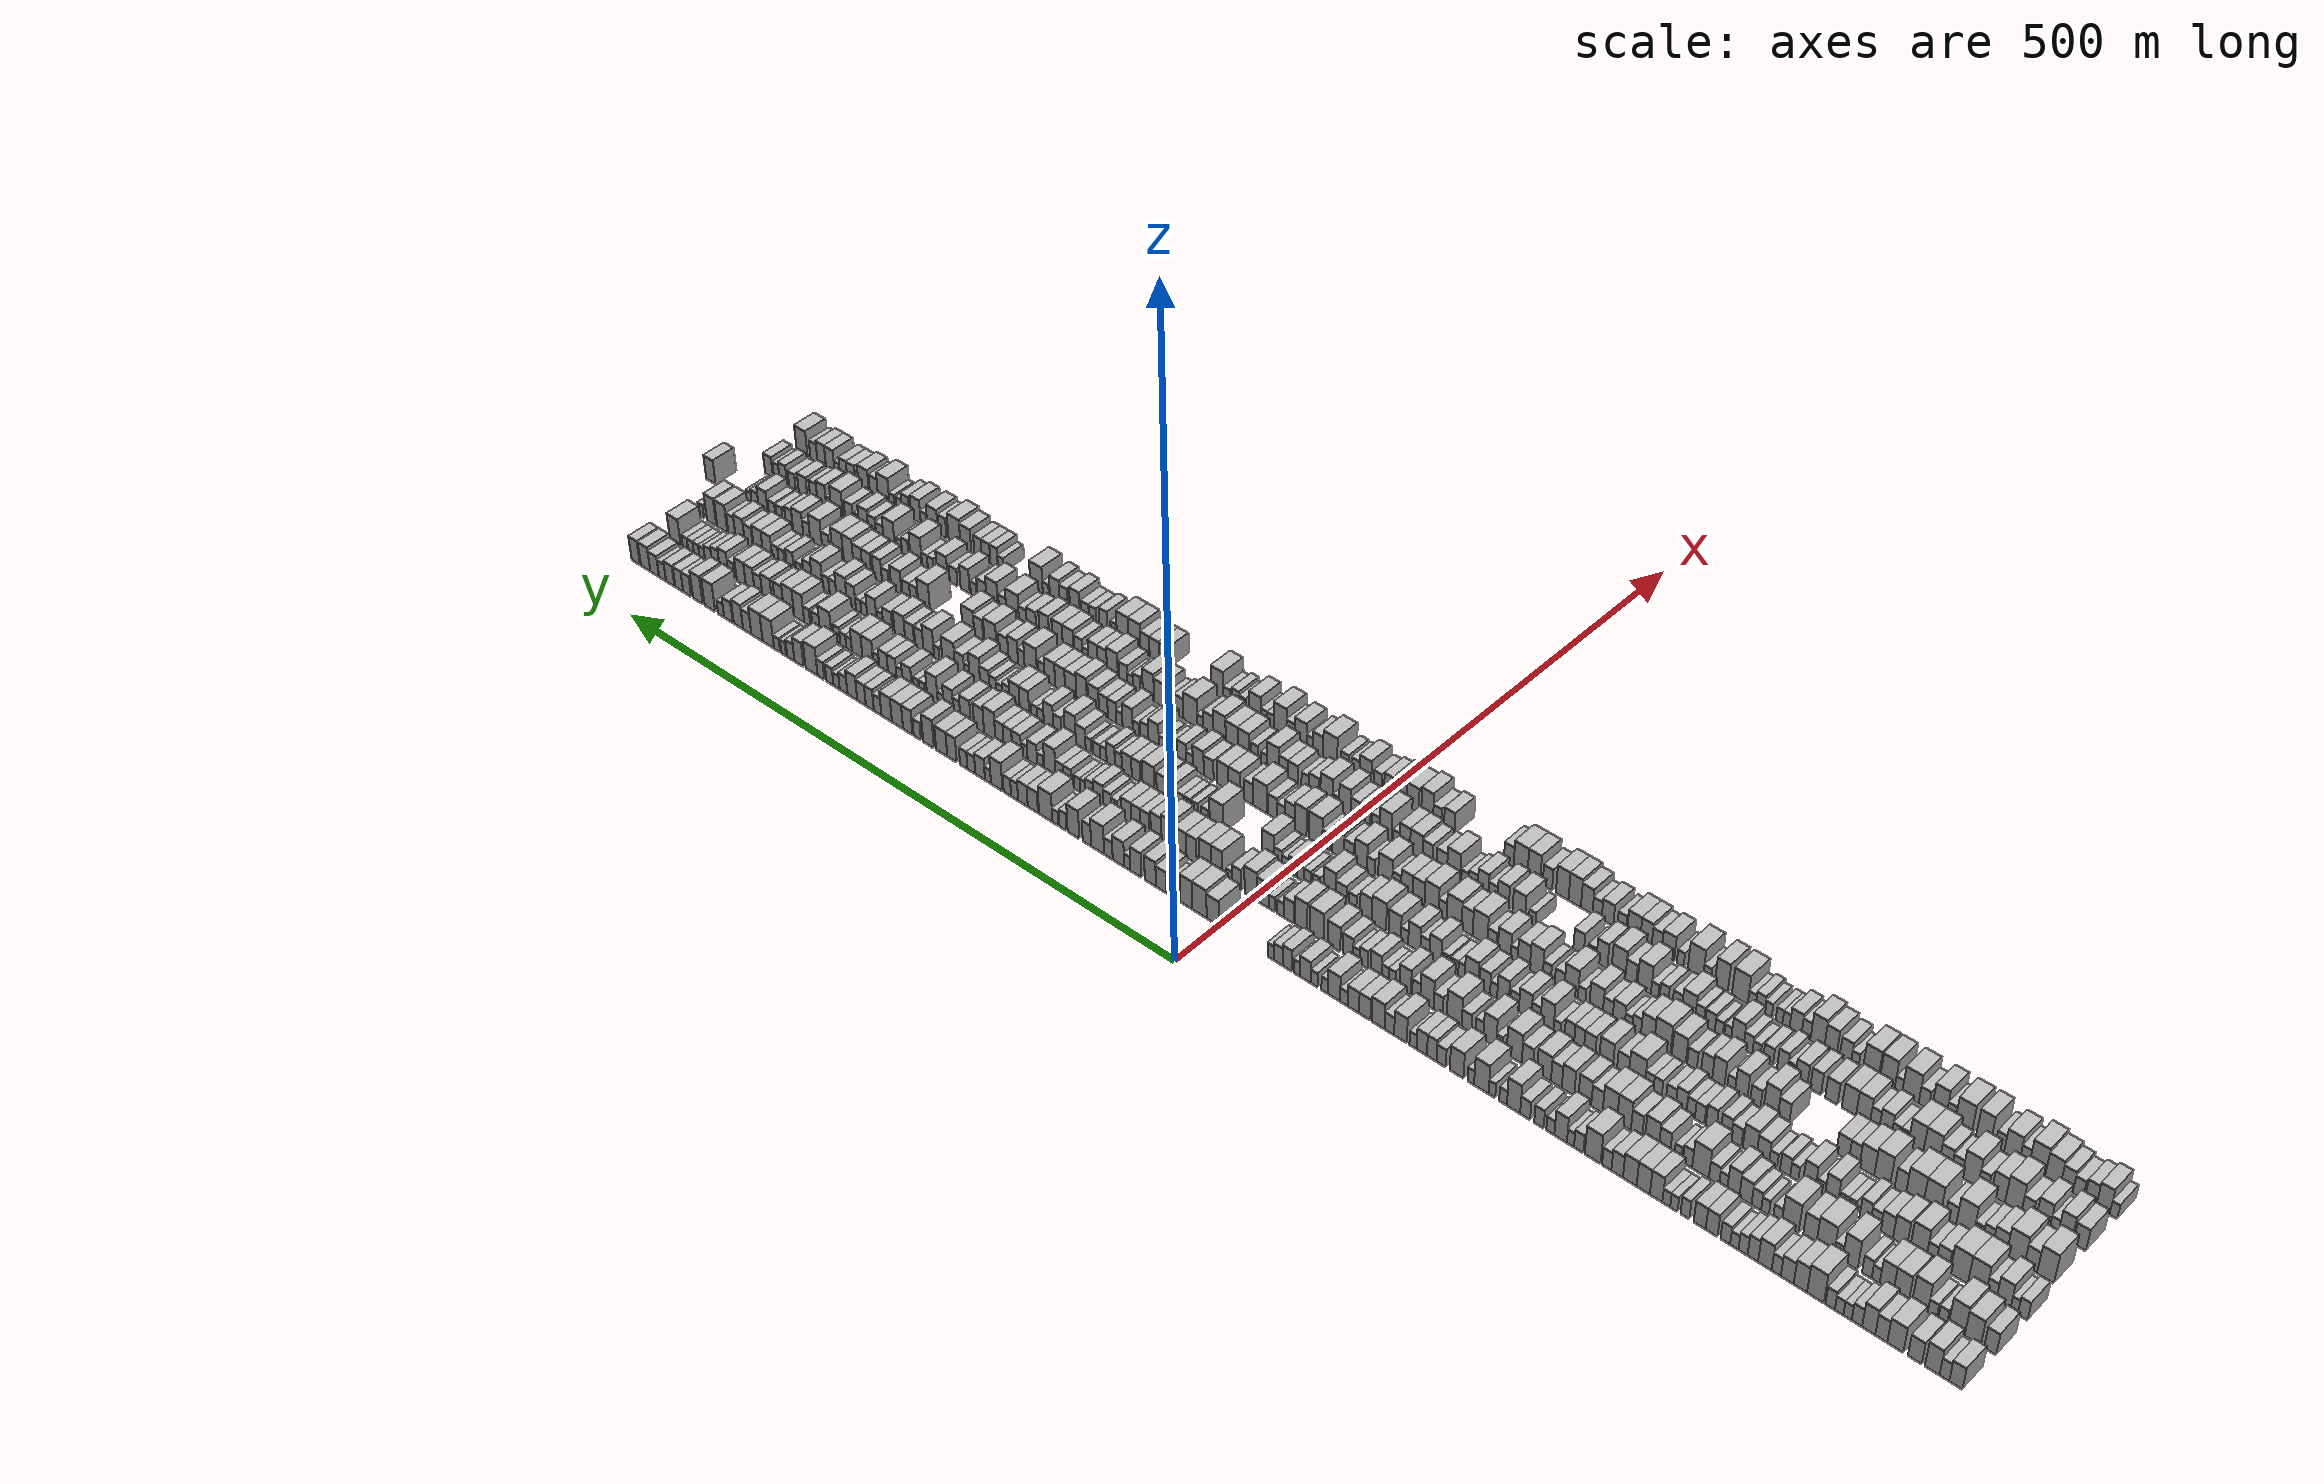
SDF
<sdf version="1.6">
 <world name="default">
  <scene>
   <sky><clouds><speed>12</speed></clouds></sky>
   <ambient>0.4 0.4 0.4 1</ambient>
   <background>0.7 0.7 0.7 1</background>
   <shadows>1</shadows>
  </scene>
  <gravity>0 0 -9.8066</gravity>
  <magnetic_field>6e-06 2.3e-05 -4.2e-05</magnetic_field>
  <physics default="0" name="default_physics" type="ode">
   <ode>
    <solver>
     <type>quick</type>
     <iters>10</iters>
     <sor>1.0</sor>
     <use_dynamic_moi_rescaling>0</use_dynamic_moi_rescaling>
    </solver>
    <constraints>
     <cfm>0</cfm>
     <erp>0.2</erp>
     <contact_max_correcting_vel>100</contact_max_correcting_vel>
     <contact_surface_layer>0.001</contact_surface_layer>
    </constraints>
   </ode>
   <max_step_size>0.004</max_step_size>
   <real_time_factor>1</real_time_factor>
   <real_time_update_rate>250</real_time_update_rate>
  </physics>
  <light name="sun" type="directional">
   <pose>0 0 10 0 0 0</pose>
   <diffuse>0.8 0.8 0.8 1</diffuse>
   <specular>0.2 0.2 0.2 1</specular>
   <attenuation>
    <range>1000</range>
    <constant>0.9</constant>
    <linear>0.01</linear>
    <quadratic>0.001</quadratic>
   </attenuation>
   <direction>-0.5 0.1 -0.9</direction>
  </light>
  <model name="building_1">
   <static>1</static>
   <pose>50.0000 -534.7649 0 0.000000 0.000000 0.000000</pose>
   <link name="link">
    <pose>0 0 9.00 0 0 0</pose>
    <collision name="collision"><geometry><box><size>20.0000 8.4702 18.0000</size></box></geometry></collision>
    <visual name="visual">
     <cast_shadows>0</cast_shadows>
     <geometry><box><size>20.0000 8.4702 18.0000</size></box></geometry>
     <material>
      <script>
       <uri>model://HANNAS_wall/materials/scripts</uri>
       <uri>model://HANNAS_wall/materials/textures</uri>
       <name>vrc/HANNAS_wall</name>
      </script>
     </material>
    </visual>
   </link>
  </model>
  <model name="building_2">
   <static>1</static>
   <pose>50.0000 -527.4299 0 0.000000 0.000000 0.000000</pose>
   <link name="link">
    <pose>0 0 7.50 0 0 0</pose>
    <collision name="collision"><geometry><box><size>20.0000 6.1998 15.0000</size></box></geometry></collision>
    <visual name="visual">
     <cast_shadows>0</cast_shadows>
     <geometry><box><size>20.0000 6.1998 15.0000</size></box></geometry>
     <material>
      <script>
       <uri>model://HANNAS_wall/materials/scripts</uri>
       <uri>model://HANNAS_wall/materials/textures</uri>
       <name>vrc/HANNAS_wall</name>
      </script>
     </material>
    </visual>
   </link>
  </model>
  <model name="building_3">
   <static>1</static>
   <pose>50.0000 -519.6073 0 0.000000 0.000000 0.000000</pose>
   <link name="link">
    <pose>0 0 10.50 0 0 0</pose>
    <collision name="collision"><geometry><box><size>20.0000 9.4454 21.0000</size></box></geometry></collision>
    <visual name="visual">
     <cast_shadows>0</cast_shadows>
     <geometry><box><size>20.0000 9.4454 21.0000</size></box></geometry>
     <material>
      <script>
       <uri>model://HANNAS_wall/materials/scripts</uri>
       <uri>model://HANNAS_wall/materials/textures</uri>
       <name>vrc/HANNAS_wall</name>
      </script>
     </material>
    </visual>
   </link>
  </model>
  <model name="building_4">
   <static>1</static>
   <pose>50.0000 -508.4007 0 0.000000 0.000000 0.000000</pose>
   <link name="link">
    <pose>0 0 9.00 0 0 0</pose>
    <collision name="collision"><geometry><box><size>20.0000 8.9678 18.0000</size></box></geometry></collision>
    <visual name="visual">
     <cast_shadows>0</cast_shadows>
     <geometry><box><size>20.0000 8.9678 18.0000</size></box></geometry>
     <material>
      <script>
       <uri>model://HANNAS_wall/materials/scripts</uri>
       <uri>model://HANNAS_wall/materials/textures</uri>
       <name>vrc/HANNAS_wall</name>
      </script>
     </material>
    </visual>
   </link>
  </model>
  <model name="building_5">
   <static>1</static>
   <pose>50.0000 -495.6780 0 0.000000 0.000000 0.000000</pose>
   <link name="link">
    <pose>0 0 10.50 0 0 0</pose>
    <collision name="collision"><geometry><box><size>20.0000 10.4776 21.0000</size></box></geometry></collision>
    <visual name="visual">
     <cast_shadows>0</cast_shadows>
     <geometry><box><size>20.0000 10.4776 21.0000</size></box></geometry>
     <material>
      <script>
       <uri>model://HANNAS_wall/materials/scripts</uri>
       <uri>model://HANNAS_wall/materials/textures</uri>
       <name>vrc/HANNAS_wall</name>
      </script>
     </material>
    </visual>
   </link>
  </model>
  <model name="building_6">
   <static>1</static>
   <pose>50.0000 -486.5109 0 0.000000 0.000000 0.000000</pose>
   <link name="link">
    <pose>0 0 9.00 0 0 0</pose>
    <collision name="collision"><geometry><box><size>20.0000 7.8567 18.0000</size></box></geometry></collision>
    <visual name="visual">
     <cast_shadows>0</cast_shadows>
     <geometry><box><size>20.0000 7.8567 18.0000</size></box></geometry>
     <material>
      <script>
       <uri>model://HANNAS_wall/materials/scripts</uri>
       <uri>model://HANNAS_wall/materials/textures</uri>
       <name>vrc/HANNAS_wall</name>
      </script>
     </material>
    </visual>
   </link>
  </model>
  <model name="building_7">
   <static>1</static>
   <pose>50.0000 -478.2406 0 0.000000 0.000000 0.000000</pose>
   <link name="link">
    <pose>0 0 10.50 0 0 0</pose>
    <collision name="collision"><geometry><box><size>20.0000 8.6838 21.0000</size></box></geometry></collision>
    <visual name="visual">
     <cast_shadows>0</cast_shadows>
     <geometry><box><size>20.0000 8.6838 21.0000</size></box></geometry>
     <material>
      <script>
       <uri>model://HANNAS_wall/materials/scripts</uri>
       <uri>model://HANNAS_wall/materials/textures</uri>
       <name>vrc/HANNAS_wall</name>
      </script>
     </material>
    </visual>
   </link>
  </model>
  <model name="building_8">
   <static>1</static>
   <pose>50.0000 -470.4626 0 0.000000 0.000000 0.000000</pose>
   <link name="link">
    <pose>0 0 7.50 0 0 0</pose>
    <collision name="collision"><geometry><box><size>20.0000 6.8724 15.0000</size></box></geometry></collision>
    <visual name="visual">
     <cast_shadows>0</cast_shadows>
     <geometry><box><size>20.0000 6.8724 15.0000</size></box></geometry>
     <material>
      <script>
       <uri>model://HANNAS_wall/materials/scripts</uri>
       <uri>model://HANNAS_wall/materials/textures</uri>
       <name>vrc/HANNAS_wall</name>
      </script>
     </material>
    </visual>
   </link>
  </model>
  <model name="building_9">
   <static>1</static>
   <pose>50.0000 -464.2918 0 0.000000 0.000000 0.000000</pose>
   <link name="link">
    <pose>0 0 6.00 0 0 0</pose>
    <collision name="collision"><geometry><box><size>20.0000 5.4692 12.0000</size></box></geometry></collision>
    <visual name="visual">
     <cast_shadows>0</cast_shadows>
     <geometry><box><size>20.0000 5.4692 12.0000</size></box></geometry>
     <material>
      <script>
       <uri>model://HANNAS_wall/materials/scripts</uri>
       <uri>model://HANNAS_wall/materials/textures</uri>
       <name>vrc/HANNAS_wall</name>
      </script>
     </material>
    </visual>
   </link>
  </model>
  <model name="building_10">
   <static>1</static>
   <pose>50.0000 -458.6943 0 0.000000 0.000000 0.000000</pose>
   <link name="link">
    <pose>0 0 6.00 0 0 0</pose>
    <collision name="collision"><geometry><box><size>20.0000 5.7256 12.0000</size></box></geometry></collision>
    <visual name="visual">
     <cast_shadows>0</cast_shadows>
     <geometry><box><size>20.0000 5.7256 12.0000</size></box></geometry>
     <material>
      <script>
       <uri>model://HANNAS_wall/materials/scripts</uri>
       <uri>model://HANNAS_wall/materials/textures</uri>
       <name>vrc/HANNAS_wall</name>
      </script>
     </material>
    </visual>
   </link>
  </model>
  <model name="building_11">
   <static>1</static>
   <pose>50.0000 -452.7089 0 0.000000 0.000000 0.000000</pose>
   <link name="link">
    <pose>0 0 7.50 0 0 0</pose>
    <collision name="collision"><geometry><box><size>20.0000 6.2452 15.0000</size></box></geometry></collision>
    <visual name="visual">
     <cast_shadows>0</cast_shadows>
     <geometry><box><size>20.0000 6.2452 15.0000</size></box></geometry>
     <material>
      <script>
       <uri>model://HANNAS_wall/materials/scripts</uri>
       <uri>model://HANNAS_wall/materials/textures</uri>
       <name>vrc/HANNAS_wall</name>
      </script>
     </material>
    </visual>
   </link>
  </model>
  <model name="building_12">
   <static>1</static>
   <pose>50.0000 -442.9442 0 0.000000 0.000000 0.000000</pose>
   <link name="link">
    <pose>0 0 12.00 0 0 0</pose>
    <collision name="collision"><geometry><box><size>20.0000 11.2843 24.0000</size></box></geometry></collision>
    <visual name="visual">
     <cast_shadows>0</cast_shadows>
     <geometry><box><size>20.0000 11.2843 24.0000</size></box></geometry>
     <material>
      <script>
       <uri>model://HANNAS_wall/materials/scripts</uri>
       <uri>model://HANNAS_wall/materials/textures</uri>
       <name>vrc/HANNAS_wall</name>
      </script>
     </material>
    </visual>
   </link>
  </model>
  <model name="building_13">
   <static>1</static>
   <pose>50.0000 -432.8231 0 0.000000 0.000000 0.000000</pose>
   <link name="link">
    <pose>0 0 10.50 0 0 0</pose>
    <collision name="collision"><geometry><box><size>20.0000 8.9580 21.0000</size></box></geometry></collision>
    <visual name="visual">
     <cast_shadows>0</cast_shadows>
     <geometry><box><size>20.0000 8.9580 21.0000</size></box></geometry>
     <material>
      <script>
       <uri>model://HANNAS_wall/materials/scripts</uri>
       <uri>model://HANNAS_wall/materials/textures</uri>
       <name>vrc/HANNAS_wall</name>
      </script>
     </material>
    </visual>
   </link>
  </model>
  <model name="building_14">
   <static>1</static>
   <pose>50.0000 -423.9955 0 0.000000 0.000000 0.000000</pose>
   <link name="link">
    <pose>0 0 9.00 0 0 0</pose>
    <collision name="collision"><geometry><box><size>20.0000 8.6971 18.0000</size></box></geometry></collision>
    <visual name="visual">
     <cast_shadows>0</cast_shadows>
     <geometry><box><size>20.0000 8.6971 18.0000</size></box></geometry>
     <material>
      <script>
       <uri>model://HANNAS_wall/materials/scripts</uri>
       <uri>model://HANNAS_wall/materials/textures</uri>
       <name>vrc/HANNAS_wall</name>
      </script>
     </material>
    </visual>
   </link>
  </model>
  <model name="building_15">
   <static>1</static>
   <pose>50.0000 -416.5268 0 0.000000 0.000000 0.000000</pose>
   <link name="link">
    <pose>0 0 7.50 0 0 0</pose>
    <collision name="collision"><geometry><box><size>20.0000 6.2402 15.0000</size></box></geometry></collision>
    <visual name="visual">
     <cast_shadows>0</cast_shadows>
     <geometry><box><size>20.0000 6.2402 15.0000</size></box></geometry>
     <material>
      <script>
       <uri>model://HANNAS_wall/materials/scripts</uri>
       <uri>model://HANNAS_wall/materials/textures</uri>
       <name>vrc/HANNAS_wall</name>
      </script>
     </material>
    </visual>
   </link>
  </model>
  <model name="building_16">
   <static>1</static>
   <pose>50.0000 -408.7989 0 0.000000 0.000000 0.000000</pose>
   <link name="link">
    <pose>0 0 10.50 0 0 0</pose>
    <collision name="collision"><geometry><box><size>20.0000 9.2158 21.0000</size></box></geometry></collision>
    <visual name="visual">
     <cast_shadows>0</cast_shadows>
     <geometry><box><size>20.0000 9.2158 21.0000</size></box></geometry>
     <material>
      <script>
       <uri>model://HANNAS_wall/materials/scripts</uri>
       <uri>model://HANNAS_wall/materials/textures</uri>
       <name>vrc/HANNAS_wall</name>
      </script>
     </material>
    </visual>
   </link>
  </model>
  <model name="building_17">
   <static>1</static>
   <pose>50.0000 -400.5640 0 0.000000 0.000000 0.000000</pose>
   <link name="link">
    <pose>0 0 9.00 0 0 0</pose>
    <collision name="collision"><geometry><box><size>20.0000 7.2541 18.0000</size></box></geometry></collision>
    <visual name="visual">
     <cast_shadows>0</cast_shadows>
     <geometry><box><size>20.0000 7.2541 18.0000</size></box></geometry>
     <material>
      <script>
       <uri>model://HANNAS_wall/materials/scripts</uri>
       <uri>model://HANNAS_wall/materials/textures</uri>
       <name>vrc/HANNAS_wall</name>
      </script>
     </material>
    </visual>
   </link>
  </model>
  <model name="building_18">
   <static>1</static>
   <pose>50.0000 -393.8505 0 0.000000 0.000000 0.000000</pose>
   <link name="link">
    <pose>0 0 7.50 0 0 0</pose>
    <collision name="collision"><geometry><box><size>20.0000 6.1730 15.0000</size></box></geometry></collision>
    <visual name="visual">
     <cast_shadows>0</cast_shadows>
     <geometry><box><size>20.0000 6.1730 15.0000</size></box></geometry>
     <material>
      <script>
       <uri>model://HANNAS_wall/materials/scripts</uri>
       <uri>model://HANNAS_wall/materials/textures</uri>
       <name>vrc/HANNAS_wall</name>
      </script>
     </material>
    </visual>
   </link>
  </model>
  <model name="building_19">
   <static>1</static>
   <pose>50.0000 -387.8867 0 0.000000 0.000000 0.000000</pose>
   <link name="link">
    <pose>0 0 6.00 0 0 0</pose>
    <collision name="collision"><geometry><box><size>20.0000 5.7544 12.0000</size></box></geometry></collision>
    <visual name="visual">
     <cast_shadows>0</cast_shadows>
     <geometry><box><size>20.0000 5.7544 12.0000</size></box></geometry>
     <material>
      <script>
       <uri>model://HANNAS_wall/materials/scripts</uri>
       <uri>model://HANNAS_wall/materials/textures</uri>
       <name>vrc/HANNAS_wall</name>
      </script>
     </material>
    </visual>
   </link>
  </model>
  <model name="building_20">
   <static>1</static>
   <pose>50.0000 -381.6869 0 0.000000 0.000000 0.000000</pose>
   <link name="link">
    <pose>0 0 7.50 0 0 0</pose>
    <collision name="collision"><geometry><box><size>20.0000 6.6452 15.0000</size></box></geometry></collision>
    <visual name="visual">
     <cast_shadows>0</cast_shadows>
     <geometry><box><size>20.0000 6.6452 15.0000</size></box></geometry>
     <material>
      <script>
       <uri>model://HANNAS_wall/materials/scripts</uri>
       <uri>model://HANNAS_wall/materials/textures</uri>
       <name>vrc/HANNAS_wall</name>
      </script>
     </material>
    </visual>
   </link>
  </model>
  <model name="building_21">
   <static>1</static>
   <pose>50.0000 -372.2459 0 0.000000 0.000000 0.000000</pose>
   <link name="link">
    <pose>0 0 9.00 0 0 0</pose>
    <collision name="collision"><geometry><box><size>20.0000 8.2368 18.0000</size></box></geometry></collision>
    <visual name="visual">
     <cast_shadows>0</cast_shadows>
     <geometry><box><size>20.0000 8.2368 18.0000</size></box></geometry>
     <material>
      <script>
       <uri>model://HANNAS_wall/materials/scripts</uri>
       <uri>model://HANNAS_wall/materials/textures</uri>
       <name>vrc/HANNAS_wall</name>
      </script>
     </material>
    </visual>
   </link>
  </model>
  <model name="building_22">
   <static>1</static>
   <pose>50.0000 -363.9504 0 0.000000 0.000000 0.000000</pose>
   <link name="link">
    <pose>0 0 9.00 0 0 0</pose>
    <collision name="collision"><geometry><box><size>20.0000 8.3542 18.0000</size></box></geometry></collision>
    <visual name="visual">
     <cast_shadows>0</cast_shadows>
     <geometry><box><size>20.0000 8.3542 18.0000</size></box></geometry>
     <material>
      <script>
       <uri>model://HANNAS_wall/materials/scripts</uri>
       <uri>model://HANNAS_wall/materials/textures</uri>
       <name>vrc/HANNAS_wall</name>
      </script>
     </material>
    </visual>
   </link>
  </model>
  <model name="building_23">
   <static>1</static>
   <pose>50.0000 -353.6612 0 0.000000 0.000000 0.000000</pose>
   <link name="link">
    <pose>0 0 7.50 0 0 0</pose>
    <collision name="collision"><geometry><box><size>20.0000 6.2243 15.0000</size></box></geometry></collision>
    <visual name="visual">
     <cast_shadows>0</cast_shadows>
     <geometry><box><size>20.0000 6.2243 15.0000</size></box></geometry>
     <material>
      <script>
       <uri>model://HANNAS_wall/materials/scripts</uri>
       <uri>model://HANNAS_wall/materials/textures</uri>
       <name>vrc/HANNAS_wall</name>
      </script>
     </material>
    </visual>
   </link>
  </model>
  <model name="building_24">
   <static>1</static>
   <pose>50.0000 -345.9473 0 0.000000 0.000000 0.000000</pose>
   <link name="link">
    <pose>0 0 6.00 0 0 0</pose>
    <collision name="collision"><geometry><box><size>20.0000 5.2035 12.0000</size></box></geometry></collision>
    <visual name="visual">
     <cast_shadows>0</cast_shadows>
     <geometry><box><size>20.0000 5.2035 12.0000</size></box></geometry>
     <material>
      <script>
       <uri>model://HANNAS_wall/materials/scripts</uri>
       <uri>model://HANNAS_wall/materials/textures</uri>
       <name>vrc/HANNAS_wall</name>
      </script>
     </material>
    </visual>
   </link>
  </model>
  <model name="building_25">
   <static>1</static>
   <pose>50.0000 -340.5783 0 0.000000 0.000000 0.000000</pose>
   <link name="link">
    <pose>0 0 6.00 0 0 0</pose>
    <collision name="collision"><geometry><box><size>20.0000 5.5344 12.0000</size></box></geometry></collision>
    <visual name="visual">
     <cast_shadows>0</cast_shadows>
     <geometry><box><size>20.0000 5.5344 12.0000</size></box></geometry>
     <material>
      <script>
       <uri>model://HANNAS_wall/materials/scripts</uri>
       <uri>model://HANNAS_wall/materials/textures</uri>
       <name>vrc/HANNAS_wall</name>
      </script>
     </material>
    </visual>
   </link>
  </model>
  <model name="building_26">
   <static>1</static>
   <pose>50.0000 -333.3948 0 0.000000 0.000000 0.000000</pose>
   <link name="link">
    <pose>0 0 10.50 0 0 0</pose>
    <collision name="collision"><geometry><box><size>20.0000 8.8327 21.0000</size></box></geometry></collision>
    <visual name="visual">
     <cast_shadows>0</cast_shadows>
     <geometry><box><size>20.0000 8.8327 21.0000</size></box></geometry>
     <material>
      <script>
       <uri>model://HANNAS_wall/materials/scripts</uri>
       <uri>model://HANNAS_wall/materials/textures</uri>
       <name>vrc/HANNAS_wall</name>
      </script>
     </material>
    </visual>
   </link>
  </model>
  <model name="building_27">
   <static>1</static>
   <pose>50.0000 -324.2665 0 0.000000 0.000000 0.000000</pose>
   <link name="link">
    <pose>0 0 10.50 0 0 0</pose>
    <collision name="collision"><geometry><box><size>20.0000 9.4238 21.0000</size></box></geometry></collision>
    <visual name="visual">
     <cast_shadows>0</cast_shadows>
     <geometry><box><size>20.0000 9.4238 21.0000</size></box></geometry>
     <material>
      <script>
       <uri>model://HANNAS_wall/materials/scripts</uri>
       <uri>model://HANNAS_wall/materials/textures</uri>
       <name>vrc/HANNAS_wall</name>
      </script>
     </material>
    </visual>
   </link>
  </model>
  <model name="building_28">
   <static>1</static>
   <pose>50.0000 -314.6912 0 0.000000 0.000000 0.000000</pose>
   <link name="link">
    <pose>0 0 10.50 0 0 0</pose>
    <collision name="collision"><geometry><box><size>20.0000 9.7268 21.0000</size></box></geometry></collision>
    <visual name="visual">
     <cast_shadows>0</cast_shadows>
     <geometry><box><size>20.0000 9.7268 21.0000</size></box></geometry>
     <material>
      <script>
       <uri>model://HANNAS_wall/materials/scripts</uri>
       <uri>model://HANNAS_wall/materials/textures</uri>
       <name>vrc/HANNAS_wall</name>
      </script>
     </material>
    </visual>
   </link>
  </model>
  <model name="building_29">
   <static>1</static>
   <pose>50.0000 -305.6842 0 0.000000 0.000000 0.000000</pose>
   <link name="link">
    <pose>0 0 9.00 0 0 0</pose>
    <collision name="collision"><geometry><box><size>20.0000 8.2872 18.0000</size></box></geometry></collision>
    <visual name="visual">
     <cast_shadows>0</cast_shadows>
     <geometry><box><size>20.0000 8.2872 18.0000</size></box></geometry>
     <material>
      <script>
       <uri>model://HANNAS_wall/materials/scripts</uri>
       <uri>model://HANNAS_wall/materials/textures</uri>
       <name>vrc/HANNAS_wall</name>
      </script>
     </material>
    </visual>
   </link>
  </model>
  <model name="building_30">
   <static>1</static>
   <pose>50.0000 -298.1791 0 0.000000 0.000000 0.000000</pose>
   <link name="link">
    <pose>0 0 7.50 0 0 0</pose>
    <collision name="collision"><geometry><box><size>20.0000 6.7229 15.0000</size></box></geometry></collision>
    <visual name="visual">
     <cast_shadows>0</cast_shadows>
     <geometry><box><size>20.0000 6.7229 15.0000</size></box></geometry>
     <material>
      <script>
       <uri>model://HANNAS_wall/materials/scripts</uri>
       <uri>model://HANNAS_wall/materials/textures</uri>
       <name>vrc/HANNAS_wall</name>
      </script>
     </material>
    </visual>
   </link>
  </model>
  <model name="building_31">
   <static>1</static>
   <pose>50.0000 -288.0655 0 0.000000 0.000000 0.000000</pose>
   <link name="link">
    <pose>0 0 12.00 0 0 0</pose>
    <collision name="collision"><geometry><box><size>20.0000 11.5043 24.0000</size></box></geometry></collision>
    <visual name="visual">
     <cast_shadows>0</cast_shadows>
     <geometry><box><size>20.0000 11.5043 24.0000</size></box></geometry>
     <material>
      <script>
       <uri>model://HANNAS_wall/materials/scripts</uri>
       <uri>model://HANNAS_wall/materials/textures</uri>
       <name>vrc/HANNAS_wall</name>
      </script>
     </material>
    </visual>
   </link>
  </model>
  <model name="building_32">
   <static>1</static>
   <pose>50.0000 -277.9415 0 0.000000 0.000000 0.000000</pose>
   <link name="link">
    <pose>0 0 7.50 0 0 0</pose>
    <collision name="collision"><geometry><box><size>20.0000 6.7436 15.0000</size></box></geometry></collision>
    <visual name="visual">
     <cast_shadows>0</cast_shadows>
     <geometry><box><size>20.0000 6.7436 15.0000</size></box></geometry>
     <material>
      <script>
       <uri>model://HANNAS_wall/materials/scripts</uri>
       <uri>model://HANNAS_wall/materials/textures</uri>
       <name>vrc/HANNAS_wall</name>
      </script>
     </material>
    </visual>
   </link>
  </model>
  <model name="building_33">
   <static>1</static>
   <pose>50.0000 -271.9626 0 0.000000 0.000000 0.000000</pose>
   <link name="link">
    <pose>0 0 6.00 0 0 0</pose>
    <collision name="collision"><geometry><box><size>20.0000 5.2142 12.0000</size></box></geometry></collision>
    <visual name="visual">
     <cast_shadows>0</cast_shadows>
     <geometry><box><size>20.0000 5.2142 12.0000</size></box></geometry>
     <material>
      <script>
       <uri>model://HANNAS_wall/materials/scripts</uri>
       <uri>model://HANNAS_wall/materials/textures</uri>
       <name>vrc/HANNAS_wall</name>
      </script>
     </material>
    </visual>
   </link>
  </model>
  <model name="building_34">
   <static>1</static>
   <pose>50.0000 -264.7930 0 0.000000 0.000000 0.000000</pose>
   <link name="link">
    <pose>0 0 10.50 0 0 0</pose>
    <collision name="collision"><geometry><box><size>20.0000 9.1251 21.0000</size></box></geometry></collision>
    <visual name="visual">
     <cast_shadows>0</cast_shadows>
     <geometry><box><size>20.0000 9.1251 21.0000</size></box></geometry>
     <material>
      <script>
       <uri>model://HANNAS_wall/materials/scripts</uri>
       <uri>model://HANNAS_wall/materials/textures</uri>
       <name>vrc/HANNAS_wall</name>
      </script>
     </material>
    </visual>
   </link>
  </model>
  <model name="building_35">
   <static>1</static>
   <pose>50.0000 -257.2922 0 0.000000 0.000000 0.000000</pose>
   <link name="link">
    <pose>0 0 6.00 0 0 0</pose>
    <collision name="collision"><geometry><box><size>20.0000 5.8765 12.0000</size></box></geometry></collision>
    <visual name="visual">
     <cast_shadows>0</cast_shadows>
     <geometry><box><size>20.0000 5.8765 12.0000</size></box></geometry>
     <material>
      <script>
       <uri>model://HANNAS_wall/materials/scripts</uri>
       <uri>model://HANNAS_wall/materials/textures</uri>
       <name>vrc/HANNAS_wall</name>
      </script>
     </material>
    </visual>
   </link>
  </model>
  <model name="building_36">
   <static>1</static>
   <pose>50.0000 -248.8845 0 0.000000 0.000000 0.000000</pose>
   <link name="link">
    <pose>0 0 7.50 0 0 0</pose>
    <collision name="collision"><geometry><box><size>20.0000 6.9388 15.0000</size></box></geometry></collision>
    <visual name="visual">
     <cast_shadows>0</cast_shadows>
     <geometry><box><size>20.0000 6.9388 15.0000</size></box></geometry>
     <material>
      <script>
       <uri>model://HANNAS_wall/materials/scripts</uri>
       <uri>model://HANNAS_wall/materials/textures</uri>
       <name>vrc/HANNAS_wall</name>
      </script>
     </material>
    </visual>
   </link>
  </model>
  <model name="building_37">
   <static>1</static>
   <pose>50.0000 -238.7318 0 0.000000 0.000000 0.000000</pose>
   <link name="link">
    <pose>0 0 7.50 0 0 0</pose>
    <collision name="collision"><geometry><box><size>20.0000 7.3666 15.0000</size></box></geometry></collision>
    <visual name="visual">
     <cast_shadows>0</cast_shadows>
     <geometry><box><size>20.0000 7.3666 15.0000</size></box></geometry>
     <material>
      <script>
       <uri>model://HANNAS_wall/materials/scripts</uri>
       <uri>model://HANNAS_wall/materials/textures</uri>
       <name>vrc/HANNAS_wall</name>
      </script>
     </material>
    </visual>
   </link>
  </model>
  <model name="building_38">
   <static>1</static>
   <pose>50.0000 -230.1152 0 0.000000 0.000000 0.000000</pose>
   <link name="link">
    <pose>0 0 12.00 0 0 0</pose>
    <collision name="collision"><geometry><box><size>20.0000 9.8665 24.0000</size></box></geometry></collision>
    <visual name="visual">
     <cast_shadows>0</cast_shadows>
     <geometry><box><size>20.0000 9.8665 24.0000</size></box></geometry>
     <material>
      <script>
       <uri>model://HANNAS_wall/materials/scripts</uri>
       <uri>model://HANNAS_wall/materials/textures</uri>
       <name>vrc/HANNAS_wall</name>
      </script>
     </material>
    </visual>
   </link>
  </model>
  <model name="building_39">
   <static>1</static>
   <pose>50.0000 -222.3284 0 0.000000 0.000000 0.000000</pose>
   <link name="link">
    <pose>0 0 6.00 0 0 0</pose>
    <collision name="collision"><geometry><box><size>20.0000 5.7073 12.0000</size></box></geometry></collision>
    <visual name="visual">
     <cast_shadows>0</cast_shadows>
     <geometry><box><size>20.0000 5.7073 12.0000</size></box></geometry>
     <material>
      <script>
       <uri>model://HANNAS_wall/materials/scripts</uri>
       <uri>model://HANNAS_wall/materials/textures</uri>
       <name>vrc/HANNAS_wall</name>
      </script>
     </material>
    </visual>
   </link>
  </model>
  <model name="building_40">
   <static>1</static>
   <pose>50.0000 -214.0314 0 0.000000 0.000000 0.000000</pose>
   <link name="link">
    <pose>0 0 6.00 0 0 0</pose>
    <collision name="collision"><geometry><box><size>20.0000 4.8867 12.0000</size></box></geometry></collision>
    <visual name="visual">
     <cast_shadows>0</cast_shadows>
     <geometry><box><size>20.0000 4.8867 12.0000</size></box></geometry>
     <material>
      <script>
       <uri>model://HANNAS_wall/materials/scripts</uri>
       <uri>model://HANNAS_wall/materials/textures</uri>
       <name>vrc/HANNAS_wall</name>
      </script>
     </material>
    </visual>
   </link>
  </model>
  <model name="building_41">
   <static>1</static>
   <pose>50.0000 -206.1150 0 0.000000 0.000000 0.000000</pose>
   <link name="link">
    <pose>0 0 12.00 0 0 0</pose>
    <collision name="collision"><geometry><box><size>20.0000 10.9460 24.0000</size></box></geometry></collision>
    <visual name="visual">
     <cast_shadows>0</cast_shadows>
     <geometry><box><size>20.0000 10.9460 24.0000</size></box></geometry>
     <material>
      <script>
       <uri>model://HANNAS_wall/materials/scripts</uri>
       <uri>model://HANNAS_wall/materials/textures</uri>
       <name>vrc/HANNAS_wall</name>
      </script>
     </material>
    </visual>
   </link>
  </model>
  <model name="building_42">
   <static>1</static>
   <pose>50.0000 -198.1602 0 0.000000 0.000000 0.000000</pose>
   <link name="link">
    <pose>0 0 6.00 0 0 0</pose>
    <collision name="collision"><geometry><box><size>20.0000 4.9636 12.0000</size></box></geometry></collision>
    <visual name="visual">
     <cast_shadows>0</cast_shadows>
     <geometry><box><size>20.0000 4.9636 12.0000</size></box></geometry>
     <material>
      <script>
       <uri>model://HANNAS_wall/materials/scripts</uri>
       <uri>model://HANNAS_wall/materials/textures</uri>
       <name>vrc/HANNAS_wall</name>
      </script>
     </material>
    </visual>
   </link>
  </model>
  <model name="building_43">
   <static>1</static>
   <pose>50.0000 -187.4657 0 0.000000 0.000000 0.000000</pose>
   <link name="link">
    <pose>0 0 10.50 0 0 0</pose>
    <collision name="collision"><geometry><box><size>20.0000 10.4254 21.0000</size></box></geometry></collision>
    <visual name="visual">
     <cast_shadows>0</cast_shadows>
     <geometry><box><size>20.0000 10.4254 21.0000</size></box></geometry>
     <material>
      <script>
       <uri>model://HANNAS_wall/materials/scripts</uri>
       <uri>model://HANNAS_wall/materials/textures</uri>
       <name>vrc/HANNAS_wall</name>
      </script>
     </material>
    </visual>
   </link>
  </model>
  <model name="building_44">
   <static>1</static>
   <pose>50.0000 -175.7352 0 0.000000 0.000000 0.000000</pose>
   <link name="link">
    <pose>0 0 7.50 0 0 0</pose>
    <collision name="collision"><geometry><box><size>20.0000 7.0357 15.0000</size></box></geometry></collision>
    <visual name="visual">
     <cast_shadows>0</cast_shadows>
     <geometry><box><size>20.0000 7.0357 15.0000</size></box></geometry>
     <material>
      <script>
       <uri>model://HANNAS_wall/materials/scripts</uri>
       <uri>model://HANNAS_wall/materials/textures</uri>
       <name>vrc/HANNAS_wall</name>
      </script>
     </material>
    </visual>
   </link>
  </model>
  <model name="building_45">
   <static>1</static>
   <pose>50.0000 -168.5302 0 0.000000 0.000000 0.000000</pose>
   <link name="link">
    <pose>0 0 9.00 0 0 0</pose>
    <collision name="collision"><geometry><box><size>20.0000 7.3744 18.0000</size></box></geometry></collision>
    <visual name="visual">
     <cast_shadows>0</cast_shadows>
     <geometry><box><size>20.0000 7.3744 18.0000</size></box></geometry>
     <material>
      <script>
       <uri>model://HANNAS_wall/materials/scripts</uri>
       <uri>model://HANNAS_wall/materials/textures</uri>
       <name>vrc/HANNAS_wall</name>
      </script>
     </material>
    </visual>
   </link>
  </model>
  <model name="building_46">
   <static>1</static>
   <pose>50.0000 -160.9089 0 0.000000 0.000000 0.000000</pose>
   <link name="link">
    <pose>0 0 9.00 0 0 0</pose>
    <collision name="collision"><geometry><box><size>20.0000 7.8682 18.0000</size></box></geometry></collision>
    <visual name="visual">
     <cast_shadows>0</cast_shadows>
     <geometry><box><size>20.0000 7.8682 18.0000</size></box></geometry>
     <material>
      <script>
       <uri>model://HANNAS_wall/materials/scripts</uri>
       <uri>model://HANNAS_wall/materials/textures</uri>
       <name>vrc/HANNAS_wall</name>
      </script>
     </material>
    </visual>
   </link>
  </model>
  <model name="building_47">
   <static>1</static>
   <pose>50.0000 -154.1960 0 0.000000 0.000000 0.000000</pose>
   <link name="link">
    <pose>0 0 6.00 0 0 0</pose>
    <collision name="collision"><geometry><box><size>20.0000 5.5577 12.0000</size></box></geometry></collision>
    <visual name="visual">
     <cast_shadows>0</cast_shadows>
     <geometry><box><size>20.0000 5.5577 12.0000</size></box></geometry>
     <material>
      <script>
       <uri>model://HANNAS_wall/materials/scripts</uri>
       <uri>model://HANNAS_wall/materials/textures</uri>
       <name>vrc/HANNAS_wall</name>
      </script>
     </material>
    </visual>
   </link>
  </model>
  <model name="building_48">
   <static>1</static>
   <pose>50.0000 -144.4930 0 0.000000 0.000000 0.000000</pose>
   <link name="link">
    <pose>0 0 10.50 0 0 0</pose>
    <collision name="collision"><geometry><box><size>20.0000 9.8482 21.0000</size></box></geometry></collision>
    <visual name="visual">
     <cast_shadows>0</cast_shadows>
     <geometry><box><size>20.0000 9.8482 21.0000</size></box></geometry>
     <material>
      <script>
       <uri>model://HANNAS_wall/materials/scripts</uri>
       <uri>model://HANNAS_wall/materials/textures</uri>
       <name>vrc/HANNAS_wall</name>
      </script>
     </material>
    </visual>
   </link>
  </model>
  <model name="building_49">
   <static>1</static>
   <pose>50.0000 -135.9271 0 0.000000 0.000000 0.000000</pose>
   <link name="link">
    <pose>0 0 7.50 0 0 0</pose>
    <collision name="collision"><geometry><box><size>20.0000 7.2836 15.0000</size></box></geometry></collision>
    <visual name="visual">
     <cast_shadows>0</cast_shadows>
     <geometry><box><size>20.0000 7.2836 15.0000</size></box></geometry>
     <material>
      <script>
       <uri>model://HANNAS_wall/materials/scripts</uri>
       <uri>model://HANNAS_wall/materials/textures</uri>
       <name>vrc/HANNAS_wall</name>
      </script>
     </material>
    </visual>
   </link>
  </model>
  <model name="building_50">
   <static>1</static>
   <pose>50.0000 -127.2014 0 0.000000 0.000000 0.000000</pose>
   <link name="link">
    <pose>0 0 10.50 0 0 0</pose>
    <collision name="collision"><geometry><box><size>20.0000 10.1678 21.0000</size></box></geometry></collision>
    <visual name="visual">
     <cast_shadows>0</cast_shadows>
     <geometry><box><size>20.0000 10.1678 21.0000</size></box></geometry>
     <material>
      <script>
       <uri>model://HANNAS_wall/materials/scripts</uri>
       <uri>model://HANNAS_wall/materials/textures</uri>
       <name>vrc/HANNAS_wall</name>
      </script>
     </material>
    </visual>
   </link>
  </model>
  <model name="building_51">
   <static>1</static>
   <pose>50.0000 -116.6768 0 0.000000 0.000000 0.000000</pose>
   <link name="link">
    <pose>0 0 9.00 0 0 0</pose>
    <collision name="collision"><geometry><box><size>20.0000 8.8815 18.0000</size></box></geometry></collision>
    <visual name="visual">
     <cast_shadows>0</cast_shadows>
     <geometry><box><size>20.0000 8.8815 18.0000</size></box></geometry>
     <material>
      <script>
       <uri>model://HANNAS_wall/materials/scripts</uri>
       <uri>model://HANNAS_wall/materials/textures</uri>
       <name>vrc/HANNAS_wall</name>
      </script>
     </material>
    </visual>
   </link>
  </model>
  <model name="building_52">
   <static>1</static>
   <pose>50.0000 -107.7741 0 0.000000 0.000000 0.000000</pose>
   <link name="link">
    <pose>0 0 9.00 0 0 0</pose>
    <collision name="collision"><geometry><box><size>20.0000 8.9239 18.0000</size></box></geometry></collision>
    <visual name="visual">
     <cast_shadows>0</cast_shadows>
     <geometry><box><size>20.0000 8.9239 18.0000</size></box></geometry>
     <material>
      <script>
       <uri>model://HANNAS_wall/materials/scripts</uri>
       <uri>model://HANNAS_wall/materials/textures</uri>
       <name>vrc/HANNAS_wall</name>
      </script>
     </material>
    </visual>
   </link>
  </model>
  <model name="building_53">
   <static>1</static>
   <pose>50.0000 -100.3353 0 0.000000 0.000000 0.000000</pose>
   <link name="link">
    <pose>0 0 6.00 0 0 0</pose>
    <collision name="collision"><geometry><box><size>20.0000 5.9537 12.0000</size></box></geometry></collision>
    <visual name="visual">
     <cast_shadows>0</cast_shadows>
     <geometry><box><size>20.0000 5.9537 12.0000</size></box></geometry>
     <material>
      <script>
       <uri>model://HANNAS_wall/materials/scripts</uri>
       <uri>model://HANNAS_wall/materials/textures</uri>
       <name>vrc/HANNAS_wall</name>
      </script>
     </material>
    </visual>
   </link>
  </model>
  <model name="building_54">
   <static>1</static>
   <pose>50.0000 -92.3650 0 0.000000 0.000000 0.000000</pose>
   <link name="link">
    <pose>0 0 10.50 0 0 0</pose>
    <collision name="collision"><geometry><box><size>20.0000 9.9867 21.0000</size></box></geometry></collision>
    <visual name="visual">
     <cast_shadows>0</cast_shadows>
     <geometry><box><size>20.0000 9.9867 21.0000</size></box></geometry>
     <material>
      <script>
       <uri>model://HANNAS_wall/materials/scripts</uri>
       <uri>model://HANNAS_wall/materials/textures</uri>
       <name>vrc/HANNAS_wall</name>
      </script>
     </material>
    </visual>
   </link>
  </model>
  <model name="building_55">
   <static>1</static>
   <pose>50.0000 -84.9421 0 0.000000 0.000000 0.000000</pose>
   <link name="link">
    <pose>0 0 6.00 0 0 0</pose>
    <collision name="collision"><geometry><box><size>20.0000 4.8591 12.0000</size></box></geometry></collision>
    <visual name="visual">
     <cast_shadows>0</cast_shadows>
     <geometry><box><size>20.0000 4.8591 12.0000</size></box></geometry>
     <material>
      <script>
       <uri>model://HANNAS_wall/materials/scripts</uri>
       <uri>model://HANNAS_wall/materials/textures</uri>
       <name>vrc/HANNAS_wall</name>
      </script>
     </material>
    </visual>
   </link>
  </model>
  <model name="building_56">
   <static>1</static>
   <pose>50.0000 -76.9135 0 0.000000 0.000000 0.000000</pose>
   <link name="link">
    <pose>0 0 6.00 0 0 0</pose>
    <collision name="collision"><geometry><box><size>20.0000 5.1982 12.0000</size></box></geometry></collision>
    <visual name="visual">
     <cast_shadows>0</cast_shadows>
     <geometry><box><size>20.0000 5.1982 12.0000</size></box></geometry>
     <material>
      <script>
       <uri>model://HANNAS_wall/materials/scripts</uri>
       <uri>model://HANNAS_wall/materials/textures</uri>
       <name>vrc/HANNAS_wall</name>
      </script>
     </material>
    </visual>
   </link>
  </model>
  <model name="building_57">
   <static>1</static>
   <pose>50.0000 -69.8189 0 0.000000 0.000000 0.000000</pose>
   <link name="link">
    <pose>0 0 9.00 0 0 0</pose>
    <collision name="collision"><geometry><box><size>20.0000 8.9910 18.0000</size></box></geometry></collision>
    <visual name="visual">
     <cast_shadows>0</cast_shadows>
     <geometry><box><size>20.0000 8.9910 18.0000</size></box></geometry>
     <material>
      <script>
       <uri>model://HANNAS_wall/materials/scripts</uri>
       <uri>model://HANNAS_wall/materials/textures</uri>
       <name>vrc/HANNAS_wall</name>
      </script>
     </material>
    </visual>
   </link>
  </model>
  <model name="building_58">
   <static>1</static>
   <pose>50.0000 -62.7859 0 0.000000 0.000000 0.000000</pose>
   <link name="link">
    <pose>0 0 6.00 0 0 0</pose>
    <collision name="collision"><geometry><box><size>20.0000 5.0750 12.0000</size></box></geometry></collision>
    <visual name="visual">
     <cast_shadows>0</cast_shadows>
     <geometry><box><size>20.0000 5.0750 12.0000</size></box></geometry>
     <material>
      <script>
       <uri>model://HANNAS_wall/materials/scripts</uri>
       <uri>model://HANNAS_wall/materials/textures</uri>
       <name>vrc/HANNAS_wall</name>
      </script>
     </material>
    </visual>
   </link>
  </model>
  <model name="building_59">
   <static>1</static>
   <pose>50.0000 -55.3145 0 0.000000 0.000000 0.000000</pose>
   <link name="link">
    <pose>0 0 9.00 0 0 0</pose>
    <collision name="collision"><geometry><box><size>20.0000 7.8678 18.0000</size></box></geometry></collision>
    <visual name="visual">
     <cast_shadows>0</cast_shadows>
     <geometry><box><size>20.0000 7.8678 18.0000</size></box></geometry>
     <material>
      <script>
       <uri>model://HANNAS_wall/materials/scripts</uri>
       <uri>model://HANNAS_wall/materials/textures</uri>
       <name>vrc/HANNAS_wall</name>
      </script>
     </material>
    </visual>
   </link>
  </model>
  <model name="building_60">
   <static>1</static>
   <pose>50.0000 -47.7853 0 0.000000 0.000000 0.000000</pose>
   <link name="link">
    <pose>0 0 7.50 0 0 0</pose>
    <collision name="collision"><geometry><box><size>20.0000 7.1906 15.0000</size></box></geometry></collision>
    <visual name="visual">
     <cast_shadows>0</cast_shadows>
     <geometry><box><size>20.0000 7.1906 15.0000</size></box></geometry>
     <material>
      <script>
       <uri>model://HANNAS_wall/materials/scripts</uri>
       <uri>model://HANNAS_wall/materials/textures</uri>
       <name>vrc/HANNAS_wall</name>
      </script>
     </material>
    </visual>
   </link>
  </model>
  <model name="building_61">
   <static>1</static>
   <pose>50.0000 -41.7685 0 0.000000 0.000000 0.000000</pose>
   <link name="link">
    <pose>0 0 6.00 0 0 0</pose>
    <collision name="collision"><geometry><box><size>20.0000 4.8429 12.0000</size></box></geometry></collision>
    <visual name="visual">
     <cast_shadows>0</cast_shadows>
     <geometry><box><size>20.0000 4.8429 12.0000</size></box></geometry>
     <material>
      <script>
       <uri>model://HANNAS_wall/materials/scripts</uri>
       <uri>model://HANNAS_wall/materials/textures</uri>
       <name>vrc/HANNAS_wall</name>
      </script>
     </material>
    </visual>
   </link>
  </model>
  <model name="building_62">
   <static>1</static>
   <pose>50.0000 5.6980 0 0.000000 0.000000 0.000000</pose>
   <link name="link">
    <pose>0 0 10.50 0 0 0</pose>
    <collision name="collision"><geometry><box><size>20.0000 10.0300 21.0000</size></box></geometry></collision>
    <visual name="visual">
     <cast_shadows>0</cast_shadows>
     <geometry><box><size>20.0000 10.0300 21.0000</size></box></geometry>
     <material>
      <script>
       <uri>model://HANNAS_wall/materials/scripts</uri>
       <uri>model://HANNAS_wall/materials/textures</uri>
       <name>vrc/HANNAS_wall</name>
      </script>
     </material>
    </visual>
   </link>
  </model>
  <model name="building_63">
   <static>1</static>
   <pose>50.0000 16.6982 0 0.000000 0.000000 0.000000</pose>
   <link name="link">
    <pose>0 0 12.00 0 0 0</pose>
    <collision name="collision"><geometry><box><size>20.0000 11.9703 24.0000</size></box></geometry></collision>
    <visual name="visual">
     <cast_shadows>0</cast_shadows>
     <geometry><box><size>20.0000 11.9703 24.0000</size></box></geometry>
     <material>
      <script>
       <uri>model://HANNAS_wall/materials/scripts</uri>
       <uri>model://HANNAS_wall/materials/textures</uri>
       <name>vrc/HANNAS_wall</name>
      </script>
     </material>
    </visual>
   </link>
  </model>
  <model name="building_64">
   <static>1</static>
   <pose>50.0000 27.7714 0 0.000000 0.000000 0.000000</pose>
   <link name="link">
    <pose>0 0 12.00 0 0 0</pose>
    <collision name="collision"><geometry><box><size>20.0000 10.1760 24.0000</size></box></geometry></collision>
    <visual name="visual">
     <cast_shadows>0</cast_shadows>
     <geometry><box><size>20.0000 10.1760 24.0000</size></box></geometry>
     <material>
      <script>
       <uri>model://HANNAS_wall/materials/scripts</uri>
       <uri>model://HANNAS_wall/materials/textures</uri>
       <name>vrc/HANNAS_wall</name>
      </script>
     </material>
    </visual>
   </link>
  </model>
  <model name="building_65">
   <static>1</static>
   <pose>50.0000 35.2730 0 0.000000 0.000000 0.000000</pose>
   <link name="link">
    <pose>0 0 6.00 0 0 0</pose>
    <collision name="collision"><geometry><box><size>20.0000 4.8272 12.0000</size></box></geometry></collision>
    <visual name="visual">
     <cast_shadows>0</cast_shadows>
     <geometry><box><size>20.0000 4.8272 12.0000</size></box></geometry>
     <material>
      <script>
       <uri>model://HANNAS_wall/materials/scripts</uri>
       <uri>model://HANNAS_wall/materials/textures</uri>
       <name>vrc/HANNAS_wall</name>
      </script>
     </material>
    </visual>
   </link>
  </model>
  <model name="building_66">
   <static>1</static>
   <pose>50.0000 41.6578 0 0.000000 0.000000 0.000000</pose>
   <link name="link">
    <pose>0 0 6.00 0 0 0</pose>
    <collision name="collision"><geometry><box><size>20.0000 5.9424 12.0000</size></box></geometry></collision>
    <visual name="visual">
     <cast_shadows>0</cast_shadows>
     <geometry><box><size>20.0000 5.9424 12.0000</size></box></geometry>
     <material>
      <script>
       <uri>model://HANNAS_wall/materials/scripts</uri>
       <uri>model://HANNAS_wall/materials/textures</uri>
       <name>vrc/HANNAS_wall</name>
      </script>
     </material>
    </visual>
   </link>
  </model>
  <model name="building_67">
   <static>1</static>
   <pose>50.0000 48.9102 0 0.000000 0.000000 0.000000</pose>
   <link name="link">
    <pose>0 0 9.00 0 0 0</pose>
    <collision name="collision"><geometry><box><size>20.0000 8.5623 18.0000</size></box></geometry></collision>
    <visual name="visual">
     <cast_shadows>0</cast_shadows>
     <geometry><box><size>20.0000 8.5623 18.0000</size></box></geometry>
     <material>
      <script>
       <uri>model://HANNAS_wall/materials/scripts</uri>
       <uri>model://HANNAS_wall/materials/textures</uri>
       <name>vrc/HANNAS_wall</name>
      </script>
     </material>
    </visual>
   </link>
  </model>
  <model name="building_68">
   <static>1</static>
   <pose>50.0000 57.9190 0 0.000000 0.000000 0.000000</pose>
   <link name="link">
    <pose>0 0 10.50 0 0 0</pose>
    <collision name="collision"><geometry><box><size>20.0000 9.4554 21.0000</size></box></geometry></collision>
    <visual name="visual">
     <cast_shadows>0</cast_shadows>
     <geometry><box><size>20.0000 9.4554 21.0000</size></box></geometry>
     <material>
      <script>
       <uri>model://HANNAS_wall/materials/scripts</uri>
       <uri>model://HANNAS_wall/materials/textures</uri>
       <name>vrc/HANNAS_wall</name>
      </script>
     </material>
    </visual>
   </link>
  </model>
  <model name="building_69">
   <static>1</static>
   <pose>50.0000 70.3135 0 0.000000 0.000000 0.000000</pose>
   <link name="link">
    <pose>0 0 10.50 0 0 0</pose>
    <collision name="collision"><geometry><box><size>20.0000 9.3337 21.0000</size></box></geometry></collision>
    <visual name="visual">
     <cast_shadows>0</cast_shadows>
     <geometry><box><size>20.0000 9.3337 21.0000</size></box></geometry>
     <material>
      <script>
       <uri>model://HANNAS_wall/materials/scripts</uri>
       <uri>model://HANNAS_wall/materials/textures</uri>
       <name>vrc/HANNAS_wall</name>
      </script>
     </material>
    </visual>
   </link>
  </model>
  <model name="building_70">
   <static>1</static>
   <pose>50.0000 77.5870 0 0.000000 0.000000 0.000000</pose>
   <link name="link">
    <pose>0 0 6.00 0 0 0</pose>
    <collision name="collision"><geometry><box><size>20.0000 5.2133 12.0000</size></box></geometry></collision>
    <visual name="visual">
     <cast_shadows>0</cast_shadows>
     <geometry><box><size>20.0000 5.2133 12.0000</size></box></geometry>
     <material>
      <script>
       <uri>model://HANNAS_wall/materials/scripts</uri>
       <uri>model://HANNAS_wall/materials/textures</uri>
       <name>vrc/HANNAS_wall</name>
      </script>
     </material>
    </visual>
   </link>
  </model>
  <model name="building_71">
   <static>1</static>
   <pose>50.0000 85.1204 0 0.000000 0.000000 0.000000</pose>
   <link name="link">
    <pose>0 0 10.50 0 0 0</pose>
    <collision name="collision"><geometry><box><size>20.0000 9.8534 21.0000</size></box></geometry></collision>
    <visual name="visual">
     <cast_shadows>0</cast_shadows>
     <geometry><box><size>20.0000 9.8534 21.0000</size></box></geometry>
     <material>
      <script>
       <uri>model://HANNAS_wall/materials/scripts</uri>
       <uri>model://HANNAS_wall/materials/textures</uri>
       <name>vrc/HANNAS_wall</name>
      </script>
     </material>
    </visual>
   </link>
  </model>
  <model name="building_72">
   <static>1</static>
   <pose>50.0000 93.7477 0 0.000000 0.000000 0.000000</pose>
   <link name="link">
    <pose>0 0 7.50 0 0 0</pose>
    <collision name="collision"><geometry><box><size>20.0000 7.4013 15.0000</size></box></geometry></collision>
    <visual name="visual">
     <cast_shadows>0</cast_shadows>
     <geometry><box><size>20.0000 7.4013 15.0000</size></box></geometry>
     <material>
      <script>
       <uri>model://HANNAS_wall/materials/scripts</uri>
       <uri>model://HANNAS_wall/materials/textures</uri>
       <name>vrc/HANNAS_wall</name>
      </script>
     </material>
    </visual>
   </link>
  </model>
  <model name="building_73">
   <static>1</static>
   <pose>50.0000 103.0483 0 0.000000 0.000000 0.000000</pose>
   <link name="link">
    <pose>0 0 12.00 0 0 0</pose>
    <collision name="collision"><geometry><box><size>20.0000 11.1998 24.0000</size></box></geometry></collision>
    <visual name="visual">
     <cast_shadows>0</cast_shadows>
     <geometry><box><size>20.0000 11.1998 24.0000</size></box></geometry>
     <material>
      <script>
       <uri>model://HANNAS_wall/materials/scripts</uri>
       <uri>model://HANNAS_wall/materials/textures</uri>
       <name>vrc/HANNAS_wall</name>
      </script>
     </material>
    </visual>
   </link>
  </model>
  <model name="building_74">
   <static>1</static>
   <pose>50.0000 112.3041 0 0.000000 0.000000 0.000000</pose>
   <link name="link">
    <pose>0 0 9.00 0 0 0</pose>
    <collision name="collision"><geometry><box><size>20.0000 7.3119 18.0000</size></box></geometry></collision>
    <visual name="visual">
     <cast_shadows>0</cast_shadows>
     <geometry><box><size>20.0000 7.3119 18.0000</size></box></geometry>
     <material>
      <script>
       <uri>model://HANNAS_wall/materials/scripts</uri>
       <uri>model://HANNAS_wall/materials/textures</uri>
       <name>vrc/HANNAS_wall</name>
      </script>
     </material>
    </visual>
   </link>
  </model>
  <model name="building_75">
   <static>1</static>
   <pose>50.0000 124.0532 0 0.000000 0.000000 0.000000</pose>
   <link name="link">
    <pose>0 0 12.00 0 0 0</pose>
    <collision name="collision"><geometry><box><size>20.0000 10.1865 24.0000</size></box></geometry></collision>
    <visual name="visual">
     <cast_shadows>0</cast_shadows>
     <geometry><box><size>20.0000 10.1865 24.0000</size></box></geometry>
     <material>
      <script>
       <uri>model://HANNAS_wall/materials/scripts</uri>
       <uri>model://HANNAS_wall/materials/textures</uri>
       <name>vrc/HANNAS_wall</name>
      </script>
     </material>
    </visual>
   </link>
  </model>
  <model name="building_76">
   <static>1</static>
   <pose>50.0000 133.1814 0 0.000000 0.000000 0.000000</pose>
   <link name="link">
    <pose>0 0 7.50 0 0 0</pose>
    <collision name="collision"><geometry><box><size>20.0000 6.0699 15.0000</size></box></geometry></collision>
    <visual name="visual">
     <cast_shadows>0</cast_shadows>
     <geometry><box><size>20.0000 6.0699 15.0000</size></box></geometry>
     <material>
      <script>
       <uri>model://HANNAS_wall/materials/scripts</uri>
       <uri>model://HANNAS_wall/materials/textures</uri>
       <name>vrc/HANNAS_wall</name>
      </script>
     </material>
    </visual>
   </link>
  </model>
  <model name="building_77">
   <static>1</static>
   <pose>50.0000 139.8246 0 0.000000 0.000000 0.000000</pose>
   <link name="link">
    <pose>0 0 6.00 0 0 0</pose>
    <collision name="collision"><geometry><box><size>20.0000 5.2166 12.0000</size></box></geometry></collision>
    <visual name="visual">
     <cast_shadows>0</cast_shadows>
     <geometry><box><size>20.0000 5.2166 12.0000</size></box></geometry>
     <material>
      <script>
       <uri>model://HANNAS_wall/materials/scripts</uri>
       <uri>model://HANNAS_wall/materials/textures</uri>
       <name>vrc/HANNAS_wall</name>
      </script>
     </material>
    </visual>
   </link>
  </model>
  <model name="building_78">
   <static>1</static>
   <pose>50.0000 148.3395 0 0.000000 0.000000 0.000000</pose>
   <link name="link">
    <pose>0 0 12.00 0 0 0</pose>
    <collision name="collision"><geometry><box><size>20.0000 11.8132 24.0000</size></box></geometry></collision>
    <visual name="visual">
     <cast_shadows>0</cast_shadows>
     <geometry><box><size>20.0000 11.8132 24.0000</size></box></geometry>
     <material>
      <script>
       <uri>model://HANNAS_wall/materials/scripts</uri>
       <uri>model://HANNAS_wall/materials/textures</uri>
       <name>vrc/HANNAS_wall</name>
      </script>
     </material>
    </visual>
   </link>
  </model>
  <model name="building_79">
   <static>1</static>
   <pose>50.0000 159.7359 0 0.000000 0.000000 0.000000</pose>
   <link name="link">
    <pose>0 0 9.00 0 0 0</pose>
    <collision name="collision"><geometry><box><size>20.0000 8.9795 18.0000</size></box></geometry></collision>
    <visual name="visual">
     <cast_shadows>0</cast_shadows>
     <geometry><box><size>20.0000 8.9795 18.0000</size></box></geometry>
     <material>
      <script>
       <uri>model://HANNAS_wall/materials/scripts</uri>
       <uri>model://HANNAS_wall/materials/textures</uri>
       <name>vrc/HANNAS_wall</name>
      </script>
     </material>
    </visual>
   </link>
  </model>
  <model name="building_80">
   <static>1</static>
   <pose>50.0000 168.5128 0 0.000000 0.000000 0.000000</pose>
   <link name="link">
    <pose>0 0 9.00 0 0 0</pose>
    <collision name="collision"><geometry><box><size>20.0000 8.5744 18.0000</size></box></geometry></collision>
    <visual name="visual">
     <cast_shadows>0</cast_shadows>
     <geometry><box><size>20.0000 8.5744 18.0000</size></box></geometry>
     <material>
      <script>
       <uri>model://HANNAS_wall/materials/scripts</uri>
       <uri>model://HANNAS_wall/materials/textures</uri>
       <name>vrc/HANNAS_wall</name>
      </script>
     </material>
    </visual>
   </link>
  </model>
  <model name="building_81">
   <static>1</static>
   <pose>50.0000 175.9390 0 0.000000 0.000000 0.000000</pose>
   <link name="link">
    <pose>0 0 7.50 0 0 0</pose>
    <collision name="collision"><geometry><box><size>20.0000 6.2779 15.0000</size></box></geometry></collision>
    <visual name="visual">
     <cast_shadows>0</cast_shadows>
     <geometry><box><size>20.0000 6.2779 15.0000</size></box></geometry>
     <material>
      <script>
       <uri>model://HANNAS_wall/materials/scripts</uri>
       <uri>model://HANNAS_wall/materials/textures</uri>
       <name>vrc/HANNAS_wall</name>
      </script>
     </material>
    </visual>
   </link>
  </model>
  <model name="building_82">
   <static>1</static>
   <pose>50.0000 182.4196 0 0.000000 0.000000 0.000000</pose>
   <link name="link">
    <pose>0 0 7.50 0 0 0</pose>
    <collision name="collision"><geometry><box><size>20.0000 6.6834 15.0000</size></box></geometry></collision>
    <visual name="visual">
     <cast_shadows>0</cast_shadows>
     <geometry><box><size>20.0000 6.6834 15.0000</size></box></geometry>
     <material>
      <script>
       <uri>model://HANNAS_wall/materials/scripts</uri>
       <uri>model://HANNAS_wall/materials/textures</uri>
       <name>vrc/HANNAS_wall</name>
      </script>
     </material>
    </visual>
   </link>
  </model>
  <model name="building_83">
   <static>1</static>
   <pose>50.0000 191.9415 0 0.000000 0.000000 0.000000</pose>
   <link name="link">
    <pose>0 0 12.00 0 0 0</pose>
    <collision name="collision"><geometry><box><size>20.0000 10.3604 24.0000</size></box></geometry></collision>
    <visual name="visual">
     <cast_shadows>0</cast_shadows>
     <geometry><box><size>20.0000 10.3604 24.0000</size></box></geometry>
     <material>
      <script>
       <uri>model://HANNAS_wall/materials/scripts</uri>
       <uri>model://HANNAS_wall/materials/textures</uri>
       <name>vrc/HANNAS_wall</name>
      </script>
     </material>
    </visual>
   </link>
  </model>
  <model name="building_84">
   <static>1</static>
   <pose>50.0000 199.7989 0 0.000000 0.000000 0.000000</pose>
   <link name="link">
    <pose>0 0 6.00 0 0 0</pose>
    <collision name="collision"><geometry><box><size>20.0000 5.3544 12.0000</size></box></geometry></collision>
    <visual name="visual">
     <cast_shadows>0</cast_shadows>
     <geometry><box><size>20.0000 5.3544 12.0000</size></box></geometry>
     <material>
      <script>
       <uri>model://HANNAS_wall/materials/scripts</uri>
       <uri>model://HANNAS_wall/materials/textures</uri>
       <name>vrc/HANNAS_wall</name>
      </script>
     </material>
    </visual>
   </link>
  </model>
  <model name="building_85">
   <static>1</static>
   <pose>50.0000 206.8734 0 0.000000 0.000000 0.000000</pose>
   <link name="link">
    <pose>0 0 9.00 0 0 0</pose>
    <collision name="collision"><geometry><box><size>20.0000 8.7946 18.0000</size></box></geometry></collision>
    <visual name="visual">
     <cast_shadows>0</cast_shadows>
     <geometry><box><size>20.0000 8.7946 18.0000</size></box></geometry>
     <material>
      <script>
       <uri>model://HANNAS_wall/materials/scripts</uri>
       <uri>model://HANNAS_wall/materials/textures</uri>
       <name>vrc/HANNAS_wall</name>
      </script>
     </material>
    </visual>
   </link>
  </model>
  <model name="building_86">
   <static>1</static>
   <pose>50.0000 214.8368 0 0.000000 0.000000 0.000000</pose>
   <link name="link">
    <pose>0 0 7.50 0 0 0</pose>
    <collision name="collision"><geometry><box><size>20.0000 7.1323 15.0000</size></box></geometry></collision>
    <visual name="visual">
     <cast_shadows>0</cast_shadows>
     <geometry><box><size>20.0000 7.1323 15.0000</size></box></geometry>
     <material>
      <script>
       <uri>model://HANNAS_wall/materials/scripts</uri>
       <uri>model://HANNAS_wall/materials/textures</uri>
       <name>vrc/HANNAS_wall</name>
      </script>
     </material>
    </visual>
   </link>
  </model>
  <model name="building_87">
   <static>1</static>
   <pose>50.0000 221.7886 0 0.000000 0.000000 0.000000</pose>
   <link name="link">
    <pose>0 0 7.50 0 0 0</pose>
    <collision name="collision"><geometry><box><size>20.0000 6.7713 15.0000</size></box></geometry></collision>
    <visual name="visual">
     <cast_shadows>0</cast_shadows>
     <geometry><box><size>20.0000 6.7713 15.0000</size></box></geometry>
     <material>
      <script>
       <uri>model://HANNAS_wall/materials/scripts</uri>
       <uri>model://HANNAS_wall/materials/textures</uri>
       <name>vrc/HANNAS_wall</name>
      </script>
     </material>
    </visual>
   </link>
  </model>
  <model name="building_88">
   <static>1</static>
   <pose>50.0000 232.4870 0 0.000000 0.000000 0.000000</pose>
   <link name="link">
    <pose>0 0 10.50 0 0 0</pose>
    <collision name="collision"><geometry><box><size>20.0000 8.6255 21.0000</size></box></geometry></collision>
    <visual name="visual">
     <cast_shadows>0</cast_shadows>
     <geometry><box><size>20.0000 8.6255 21.0000</size></box></geometry>
     <material>
      <script>
       <uri>model://HANNAS_wall/materials/scripts</uri>
       <uri>model://HANNAS_wall/materials/textures</uri>
       <name>vrc/HANNAS_wall</name>
      </script>
     </material>
    </visual>
   </link>
  </model>
  <model name="building_89">
   <static>1</static>
   <pose>50.0000 241.9355 0 0.000000 0.000000 0.000000</pose>
   <link name="link">
    <pose>0 0 10.50 0 0 0</pose>
    <collision name="collision"><geometry><box><size>20.0000 10.2713 21.0000</size></box></geometry></collision>
    <visual name="visual">
     <cast_shadows>0</cast_shadows>
     <geometry><box><size>20.0000 10.2713 21.0000</size></box></geometry>
     <material>
      <script>
       <uri>model://HANNAS_wall/materials/scripts</uri>
       <uri>model://HANNAS_wall/materials/textures</uri>
       <name>vrc/HANNAS_wall</name>
      </script>
     </material>
    </visual>
   </link>
  </model>
  <model name="building_90">
   <static>1</static>
   <pose>50.0000 254.0414 0 0.000000 0.000000 0.000000</pose>
   <link name="link">
    <pose>0 0 12.00 0 0 0</pose>
    <collision name="collision"><geometry><box><size>20.0000 9.9406 24.0000</size></box></geometry></collision>
    <visual name="visual">
     <cast_shadows>0</cast_shadows>
     <geometry><box><size>20.0000 9.9406 24.0000</size></box></geometry>
     <material>
      <script>
       <uri>model://HANNAS_wall/materials/scripts</uri>
       <uri>model://HANNAS_wall/materials/textures</uri>
       <name>vrc/HANNAS_wall</name>
      </script>
     </material>
    </visual>
   </link>
  </model>
  <model name="building_91">
   <static>1</static>
   <pose>50.0000 264.4250 0 0.000000 0.000000 0.000000</pose>
   <link name="link">
    <pose>0 0 7.50 0 0 0</pose>
    <collision name="collision"><geometry><box><size>20.0000 6.8265 15.0000</size></box></geometry></collision>
    <visual name="visual">
     <cast_shadows>0</cast_shadows>
     <geometry><box><size>20.0000 6.8265 15.0000</size></box></geometry>
     <material>
      <script>
       <uri>model://HANNAS_wall/materials/scripts</uri>
       <uri>model://HANNAS_wall/materials/textures</uri>
       <name>vrc/HANNAS_wall</name>
      </script>
     </material>
    </visual>
   </link>
  </model>
  <model name="building_92">
   <static>1</static>
   <pose>50.0000 273.2584 0 0.000000 0.000000 0.000000</pose>
   <link name="link">
    <pose>0 0 10.50 0 0 0</pose>
    <collision name="collision"><geometry><box><size>20.0000 8.8403 21.0000</size></box></geometry></collision>
    <visual name="visual">
     <cast_shadows>0</cast_shadows>
     <geometry><box><size>20.0000 8.8403 21.0000</size></box></geometry>
     <material>
      <script>
       <uri>model://HANNAS_wall/materials/scripts</uri>
       <uri>model://HANNAS_wall/materials/textures</uri>
       <name>vrc/HANNAS_wall</name>
      </script>
     </material>
    </visual>
   </link>
  </model>
  <model name="building_93">
   <static>1</static>
   <pose>50.0000 282.8624 0 0.000000 0.000000 0.000000</pose>
   <link name="link">
    <pose>0 0 10.50 0 0 0</pose>
    <collision name="collision"><geometry><box><size>20.0000 10.3677 21.0000</size></box></geometry></collision>
    <visual name="visual">
     <cast_shadows>0</cast_shadows>
     <geometry><box><size>20.0000 10.3677 21.0000</size></box></geometry>
     <material>
      <script>
       <uri>model://HANNAS_wall/materials/scripts</uri>
       <uri>model://HANNAS_wall/materials/textures</uri>
       <name>vrc/HANNAS_wall</name>
      </script>
     </material>
    </visual>
   </link>
  </model>
  <model name="building_94">
   <static>1</static>
   <pose>50.0000 292.9750 0 0.000000 0.000000 0.000000</pose>
   <link name="link">
    <pose>0 0 10.50 0 0 0</pose>
    <collision name="collision"><geometry><box><size>20.0000 9.8575 21.0000</size></box></geometry></collision>
    <visual name="visual">
     <cast_shadows>0</cast_shadows>
     <geometry><box><size>20.0000 9.8575 21.0000</size></box></geometry>
     <material>
      <script>
       <uri>model://HANNAS_wall/materials/scripts</uri>
       <uri>model://HANNAS_wall/materials/textures</uri>
       <name>vrc/HANNAS_wall</name>
      </script>
     </material>
    </visual>
   </link>
  </model>
  <model name="building_95">
   <static>1</static>
   <pose>50.0000 301.4691 0 0.000000 0.000000 0.000000</pose>
   <link name="link">
    <pose>0 0 7.50 0 0 0</pose>
    <collision name="collision"><geometry><box><size>20.0000 7.1307 15.0000</size></box></geometry></collision>
    <visual name="visual">
     <cast_shadows>0</cast_shadows>
     <geometry><box><size>20.0000 7.1307 15.0000</size></box></geometry>
     <material>
      <script>
       <uri>model://HANNAS_wall/materials/scripts</uri>
       <uri>model://HANNAS_wall/materials/textures</uri>
       <name>vrc/HANNAS_wall</name>
      </script>
     </material>
    </visual>
   </link>
  </model>
  <model name="building_96">
   <static>1</static>
   <pose>50.0000 308.8011 0 0.000000 0.000000 0.000000</pose>
   <link name="link">
    <pose>0 0 9.00 0 0 0</pose>
    <collision name="collision"><geometry><box><size>20.0000 7.5333 18.0000</size></box></geometry></collision>
    <visual name="visual">
     <cast_shadows>0</cast_shadows>
     <geometry><box><size>20.0000 7.5333 18.0000</size></box></geometry>
     <material>
      <script>
       <uri>model://HANNAS_wall/materials/scripts</uri>
       <uri>model://HANNAS_wall/materials/textures</uri>
       <name>vrc/HANNAS_wall</name>
      </script>
     </material>
    </visual>
   </link>
  </model>
  <model name="building_97">
   <static>1</static>
   <pose>50.0000 316.6374 0 0.000000 0.000000 0.000000</pose>
   <link name="link">
    <pose>0 0 9.00 0 0 0</pose>
    <collision name="collision"><geometry><box><size>20.0000 8.1393 18.0000</size></box></geometry></collision>
    <visual name="visual">
     <cast_shadows>0</cast_shadows>
     <geometry><box><size>20.0000 8.1393 18.0000</size></box></geometry>
     <material>
      <script>
       <uri>model://HANNAS_wall/materials/scripts</uri>
       <uri>model://HANNAS_wall/materials/textures</uri>
       <name>vrc/HANNAS_wall</name>
      </script>
     </material>
    </visual>
   </link>
  </model>
  <model name="building_98">
   <static>1</static>
   <pose>50.0000 325.3593 0 0.000000 0.000000 0.000000</pose>
   <link name="link">
    <pose>0 0 10.50 0 0 0</pose>
    <collision name="collision"><geometry><box><size>20.0000 9.3044 21.0000</size></box></geometry></collision>
    <visual name="visual">
     <cast_shadows>0</cast_shadows>
     <geometry><box><size>20.0000 9.3044 21.0000</size></box></geometry>
     <material>
      <script>
       <uri>model://HANNAS_wall/materials/scripts</uri>
       <uri>model://HANNAS_wall/materials/textures</uri>
       <name>vrc/HANNAS_wall</name>
      </script>
     </material>
    </visual>
   </link>
  </model>
  <model name="building_99">
   <static>1</static>
   <pose>50.0000 333.7357 0 0.000000 0.000000 0.000000</pose>
   <link name="link">
    <pose>0 0 7.50 0 0 0</pose>
    <collision name="collision"><geometry><box><size>20.0000 7.4485 15.0000</size></box></geometry></collision>
    <visual name="visual">
     <cast_shadows>0</cast_shadows>
     <geometry><box><size>20.0000 7.4485 15.0000</size></box></geometry>
     <material>
      <script>
       <uri>model://HANNAS_wall/materials/scripts</uri>
       <uri>model://HANNAS_wall/materials/textures</uri>
       <name>vrc/HANNAS_wall</name>
      </script>
     </material>
    </visual>
   </link>
  </model>
  <model name="building_100">
   <static>1</static>
   <pose>50.0000 340.4066 0 0.000000 0.000000 0.000000</pose>
   <link name="link">
    <pose>0 0 6.00 0 0 0</pose>
    <collision name="collision"><geometry><box><size>20.0000 5.8933 12.0000</size></box></geometry></collision>
    <visual name="visual">
     <cast_shadows>0</cast_shadows>
     <geometry><box><size>20.0000 5.8933 12.0000</size></box></geometry>
     <material>
      <script>
       <uri>model://HANNAS_wall/materials/scripts</uri>
       <uri>model://HANNAS_wall/materials/textures</uri>
       <name>vrc/HANNAS_wall</name>
      </script>
     </material>
    </visual>
   </link>
  </model>
  <model name="building_101">
   <static>1</static>
   <pose>50.0000 346.7478 0 0.000000 0.000000 0.000000</pose>
   <link name="link">
    <pose>0 0 7.50 0 0 0</pose>
    <collision name="collision"><geometry><box><size>20.0000 6.7892 15.0000</size></box></geometry></collision>
    <visual name="visual">
     <cast_shadows>0</cast_shadows>
     <geometry><box><size>20.0000 6.7892 15.0000</size></box></geometry>
     <material>
      <script>
       <uri>model://HANNAS_wall/materials/scripts</uri>
       <uri>model://HANNAS_wall/materials/textures</uri>
       <name>vrc/HANNAS_wall</name>
      </script>
     </material>
    </visual>
   </link>
  </model>
  <model name="building_102">
   <static>1</static>
   <pose>50.0000 355.4221 0 0.000000 0.000000 0.000000</pose>
   <link name="link">
    <pose>0 0 7.50 0 0 0</pose>
    <collision name="collision"><geometry><box><size>20.0000 6.5593 15.0000</size></box></geometry></collision>
    <visual name="visual">
     <cast_shadows>0</cast_shadows>
     <geometry><box><size>20.0000 6.5593 15.0000</size></box></geometry>
     <material>
      <script>
       <uri>model://HANNAS_wall/materials/scripts</uri>
       <uri>model://HANNAS_wall/materials/textures</uri>
       <name>vrc/HANNAS_wall</name>
      </script>
     </material>
    </visual>
   </link>
  </model>
  <model name="building_103">
   <static>1</static>
   <pose>50.0000 364.4843 0 0.000000 0.000000 0.000000</pose>
   <link name="link">
    <pose>0 0 12.00 0 0 0</pose>
    <collision name="collision"><geometry><box><size>20.0000 11.5651 24.0000</size></box></geometry></collision>
    <visual name="visual">
     <cast_shadows>0</cast_shadows>
     <geometry><box><size>20.0000 11.5651 24.0000</size></box></geometry>
     <material>
      <script>
       <uri>model://HANNAS_wall/materials/scripts</uri>
       <uri>model://HANNAS_wall/materials/textures</uri>
       <name>vrc/HANNAS_wall</name>
      </script>
     </material>
    </visual>
   </link>
  </model>
  <model name="building_104">
   <static>1</static>
   <pose>50.0000 376.6555 0 0.000000 0.000000 0.000000</pose>
   <link name="link">
    <pose>0 0 10.50 0 0 0</pose>
    <collision name="collision"><geometry><box><size>20.0000 8.7773 21.0000</size></box></geometry></collision>
    <visual name="visual">
     <cast_shadows>0</cast_shadows>
     <geometry><box><size>20.0000 8.7773 21.0000</size></box></geometry>
     <material>
      <script>
       <uri>model://HANNAS_wall/materials/scripts</uri>
       <uri>model://HANNAS_wall/materials/textures</uri>
       <name>vrc/HANNAS_wall</name>
      </script>
     </material>
    </visual>
   </link>
  </model>
  <model name="building_105">
   <static>1</static>
   <pose>50.0000 384.6055 0 0.000000 0.000000 0.000000</pose>
   <link name="link">
    <pose>0 0 7.50 0 0 0</pose>
    <collision name="collision"><geometry><box><size>20.0000 7.1227 15.0000</size></box></geometry></collision>
    <visual name="visual">
     <cast_shadows>0</cast_shadows>
     <geometry><box><size>20.0000 7.1227 15.0000</size></box></geometry>
     <material>
      <script>
       <uri>model://HANNAS_wall/materials/scripts</uri>
       <uri>model://HANNAS_wall/materials/textures</uri>
       <name>vrc/HANNAS_wall</name>
      </script>
     </material>
    </visual>
   </link>
  </model>
  <model name="building_106">
   <static>1</static>
   <pose>50.0000 391.6039 0 0.000000 0.000000 0.000000</pose>
   <link name="link">
    <pose>0 0 6.00 0 0 0</pose>
    <collision name="collision"><geometry><box><size>20.0000 4.8741 12.0000</size></box></geometry></collision>
    <visual name="visual">
     <cast_shadows>0</cast_shadows>
     <geometry><box><size>20.0000 4.8741 12.0000</size></box></geometry>
     <material>
      <script>
       <uri>model://HANNAS_wall/materials/scripts</uri>
       <uri>model://HANNAS_wall/materials/textures</uri>
       <name>vrc/HANNAS_wall</name>
      </script>
     </material>
    </visual>
   </link>
  </model>
  <model name="building_107">
   <static>1</static>
   <pose>50.0000 398.0365 0 0.000000 0.000000 0.000000</pose>
   <link name="link">
    <pose>0 0 6.00 0 0 0</pose>
    <collision name="collision"><geometry><box><size>20.0000 5.9911 12.0000</size></box></geometry></collision>
    <visual name="visual">
     <cast_shadows>0</cast_shadows>
     <geometry><box><size>20.0000 5.9911 12.0000</size></box></geometry>
     <material>
      <script>
       <uri>model://HANNAS_wall/materials/scripts</uri>
       <uri>model://HANNAS_wall/materials/textures</uri>
       <name>vrc/HANNAS_wall</name>
      </script>
     </material>
    </visual>
   </link>
  </model>
  <model name="building_108">
   <static>1</static>
   <pose>50.0000 406.6497 0 0.000000 0.000000 0.000000</pose>
   <link name="link">
    <pose>0 0 12.00 0 0 0</pose>
    <collision name="collision"><geometry><box><size>20.0000 11.2353 24.0000</size></box></geometry></collision>
    <visual name="visual">
     <cast_shadows>0</cast_shadows>
     <geometry><box><size>20.0000 11.2353 24.0000</size></box></geometry>
     <material>
      <script>
       <uri>model://HANNAS_wall/materials/scripts</uri>
       <uri>model://HANNAS_wall/materials/textures</uri>
       <name>vrc/HANNAS_wall</name>
      </script>
     </material>
    </visual>
   </link>
  </model>
  <model name="building_109">
   <static>1</static>
   <pose>50.0000 417.8699 0 0.000000 0.000000 0.000000</pose>
   <link name="link">
    <pose>0 0 12.00 0 0 0</pose>
    <collision name="collision"><geometry><box><size>20.0000 11.2051 24.0000</size></box></geometry></collision>
    <visual name="visual">
     <cast_shadows>0</cast_shadows>
     <geometry><box><size>20.0000 11.2051 24.0000</size></box></geometry>
     <material>
      <script>
       <uri>model://HANNAS_wall/materials/scripts</uri>
       <uri>model://HANNAS_wall/materials/textures</uri>
       <name>vrc/HANNAS_wall</name>
      </script>
     </material>
    </visual>
   </link>
  </model>
  <model name="building_110">
   <static>1</static>
   <pose>50.0000 427.5650 0 0.000000 0.000000 0.000000</pose>
   <link name="link">
    <pose>0 0 9.00 0 0 0</pose>
    <collision name="collision"><geometry><box><size>20.0000 8.1851 18.0000</size></box></geometry></collision>
    <visual name="visual">
     <cast_shadows>0</cast_shadows>
     <geometry><box><size>20.0000 8.1851 18.0000</size></box></geometry>
     <material>
      <script>
       <uri>model://HANNAS_wall/materials/scripts</uri>
       <uri>model://HANNAS_wall/materials/textures</uri>
       <name>vrc/HANNAS_wall</name>
      </script>
     </material>
    </visual>
   </link>
  </model>
  <model name="building_111">
   <static>1</static>
   <pose>50.0000 436.2804 0 0.000000 0.000000 0.000000</pose>
   <link name="link">
    <pose>0 0 10.50 0 0 0</pose>
    <collision name="collision"><geometry><box><size>20.0000 9.2458 21.0000</size></box></geometry></collision>
    <visual name="visual">
     <cast_shadows>0</cast_shadows>
     <geometry><box><size>20.0000 9.2458 21.0000</size></box></geometry>
     <material>
      <script>
       <uri>model://HANNAS_wall/materials/scripts</uri>
       <uri>model://HANNAS_wall/materials/textures</uri>
       <name>vrc/HANNAS_wall</name>
      </script>
     </material>
    </visual>
   </link>
  </model>
  <model name="building_112">
   <static>1</static>
   <pose>50.0000 446.2338 0 0.000000 0.000000 0.000000</pose>
   <link name="link">
    <pose>0 0 9.00 0 0 0</pose>
    <collision name="collision"><geometry><box><size>20.0000 8.6609 18.0000</size></box></geometry></collision>
    <visual name="visual">
     <cast_shadows>0</cast_shadows>
     <geometry><box><size>20.0000 8.6609 18.0000</size></box></geometry>
     <material>
      <script>
       <uri>model://HANNAS_wall/materials/scripts</uri>
       <uri>model://HANNAS_wall/materials/textures</uri>
       <name>vrc/HANNAS_wall</name>
      </script>
     </material>
    </visual>
   </link>
  </model>
  <model name="building_113">
   <static>1</static>
   <pose>50.0000 453.5342 0 0.000000 0.000000 0.000000</pose>
   <link name="link">
    <pose>0 0 6.00 0 0 0</pose>
    <collision name="collision"><geometry><box><size>20.0000 5.9399 12.0000</size></box></geometry></collision>
    <visual name="visual">
     <cast_shadows>0</cast_shadows>
     <geometry><box><size>20.0000 5.9399 12.0000</size></box></geometry>
     <material>
      <script>
       <uri>model://HANNAS_wall/materials/scripts</uri>
       <uri>model://HANNAS_wall/materials/textures</uri>
       <name>vrc/HANNAS_wall</name>
      </script>
     </material>
    </visual>
   </link>
  </model>
  <model name="building_114">
   <static>1</static>
   <pose>50.0000 464.8538 0 0.000000 0.000000 0.000000</pose>
   <link name="link">
    <pose>0 0 12.00 0 0 0</pose>
    <collision name="collision"><geometry><box><size>20.0000 10.6993 24.0000</size></box></geometry></collision>
    <visual name="visual">
     <cast_shadows>0</cast_shadows>
     <geometry><box><size>20.0000 10.6993 24.0000</size></box></geometry>
     <material>
      <script>
       <uri>model://HANNAS_wall/materials/scripts</uri>
       <uri>model://HANNAS_wall/materials/textures</uri>
       <name>vrc/HANNAS_wall</name>
      </script>
     </material>
    </visual>
   </link>
  </model>
  <model name="building_115">
   <static>1</static>
   <pose>50.0000 477.0107 0 0.000000 0.000000 0.000000</pose>
   <link name="link">
    <pose>0 0 12.00 0 0 0</pose>
    <collision name="collision"><geometry><box><size>20.0000 9.6145 24.0000</size></box></geometry></collision>
    <visual name="visual">
     <cast_shadows>0</cast_shadows>
     <geometry><box><size>20.0000 9.6145 24.0000</size></box></geometry>
     <material>
      <script>
       <uri>model://HANNAS_wall/materials/scripts</uri>
       <uri>model://HANNAS_wall/materials/textures</uri>
       <name>vrc/HANNAS_wall</name>
      </script>
     </material>
    </visual>
   </link>
  </model>
  <model name="building_116">
   <static>1</static>
   <pose>50.0000 487.8643 0 0.000000 0.000000 0.000000</pose>
   <link name="link">
    <pose>0 0 9.00 0 0 0</pose>
    <collision name="collision"><geometry><box><size>20.0000 8.0927 18.0000</size></box></geometry></collision>
    <visual name="visual">
     <cast_shadows>0</cast_shadows>
     <geometry><box><size>20.0000 8.0927 18.0000</size></box></geometry>
     <material>
      <script>
       <uri>model://HANNAS_wall/materials/scripts</uri>
       <uri>model://HANNAS_wall/materials/textures</uri>
       <name>vrc/HANNAS_wall</name>
      </script>
     </material>
    </visual>
   </link>
  </model>
  <model name="building_117">
   <static>1</static>
   <pose>50.0000 495.8843 0 0.000000 0.000000 0.000000</pose>
   <link name="link">
    <pose>0 0 9.00 0 0 0</pose>
    <collision name="collision"><geometry><box><size>20.0000 7.9472 18.0000</size></box></geometry></collision>
    <visual name="visual">
     <cast_shadows>0</cast_shadows>
     <geometry><box><size>20.0000 7.9472 18.0000</size></box></geometry>
     <material>
      <script>
       <uri>model://HANNAS_wall/materials/scripts</uri>
       <uri>model://HANNAS_wall/materials/textures</uri>
       <name>vrc/HANNAS_wall</name>
      </script>
     </material>
    </visual>
   </link>
  </model>
  <model name="building_118">
   <static>1</static>
   <pose>50.0000 505.1631 0 0.000000 0.000000 0.000000</pose>
   <link name="link">
    <pose>0 0 9.00 0 0 0</pose>
    <collision name="collision"><geometry><box><size>20.0000 8.6106 18.0000</size></box></geometry></collision>
    <visual name="visual">
     <cast_shadows>0</cast_shadows>
     <geometry><box><size>20.0000 8.6106 18.0000</size></box></geometry>
     <material>
      <script>
       <uri>model://HANNAS_wall/materials/scripts</uri>
       <uri>model://HANNAS_wall/materials/textures</uri>
       <name>vrc/HANNAS_wall</name>
      </script>
     </material>
    </visual>
   </link>
  </model>
  <model name="building_119">
   <static>1</static>
   <pose>50.0000 513.0341 0 0.000000 0.000000 0.000000</pose>
   <link name="link">
    <pose>0 0 7.50 0 0 0</pose>
    <collision name="collision"><geometry><box><size>20.0000 7.1313 15.0000</size></box></geometry></collision>
    <visual name="visual">
     <cast_shadows>0</cast_shadows>
     <geometry><box><size>20.0000 7.1313 15.0000</size></box></geometry>
     <material>
      <script>
       <uri>model://HANNAS_wall/materials/scripts</uri>
       <uri>model://HANNAS_wall/materials/textures</uri>
       <name>vrc/HANNAS_wall</name>
      </script>
     </material>
    </visual>
   </link>
  </model>
  <model name="building_120">
   <static>1</static>
   <pose>50.0000 521.0960 0 0.000000 0.000000 0.000000</pose>
   <link name="link">
    <pose>0 0 9.00 0 0 0</pose>
    <collision name="collision"><geometry><box><size>20.0000 8.9926 18.0000</size></box></geometry></collision>
    <visual name="visual">
     <cast_shadows>0</cast_shadows>
     <geometry><box><size>20.0000 8.9926 18.0000</size></box></geometry>
     <material>
      <script>
       <uri>model://HANNAS_wall/materials/scripts</uri>
       <uri>model://HANNAS_wall/materials/textures</uri>
       <name>vrc/HANNAS_wall</name>
      </script>
     </material>
    </visual>
   </link>
  </model>
  <model name="building_121">
   <static>1</static>
   <pose>50.0000 530.4503 0 0.000000 0.000000 0.000000</pose>
   <link name="link">
    <pose>0 0 10.50 0 0 0</pose>
    <collision name="collision"><geometry><box><size>20.0000 9.7160 21.0000</size></box></geometry></collision>
    <visual name="visual">
     <cast_shadows>0</cast_shadows>
     <geometry><box><size>20.0000 9.7160 21.0000</size></box></geometry>
     <material>
      <script>
       <uri>model://HANNAS_wall/materials/scripts</uri>
       <uri>model://HANNAS_wall/materials/textures</uri>
       <name>vrc/HANNAS_wall</name>
      </script>
     </material>
    </visual>
   </link>
  </model>
  <model name="building_122">
   <static>1</static>
   <pose>50.0000 540.6062 0 0.000000 0.000000 0.000000</pose>
   <link name="link">
    <pose>0 0 10.50 0 0 0</pose>
    <collision name="collision"><geometry><box><size>20.0000 8.5957 21.0000</size></box></geometry></collision>
    <visual name="visual">
     <cast_shadows>0</cast_shadows>
     <geometry><box><size>20.0000 8.5957 21.0000</size></box></geometry>
     <material>
      <script>
       <uri>model://HANNAS_wall/materials/scripts</uri>
       <uri>model://HANNAS_wall/materials/textures</uri>
       <name>vrc/HANNAS_wall</name>
      </script>
     </material>
    </visual>
   </link>
  </model>
  <model name="building_123">
   <static>1</static>
   <pose>82.0000 -536.0675 0 0.000000 0.000000 0.000000</pose>
   <link name="link">
    <pose>0 0 9.00 0 0 0</pose>
    <collision name="collision"><geometry><box><size>20.0000 7.8651 18.0000</size></box></geometry></collision>
    <visual name="visual">
     <cast_shadows>0</cast_shadows>
     <geometry><box><size>20.0000 7.8651 18.0000</size></box></geometry>
     <material>
      <script>
       <uri>model://HANNAS_wall/materials/scripts</uri>
       <uri>model://HANNAS_wall/materials/textures</uri>
       <name>vrc/HANNAS_wall</name>
      </script>
     </material>
    </visual>
   </link>
  </model>
  <model name="building_124">
   <static>1</static>
   <pose>82.0000 -524.9232 0 0.000000 0.000000 0.000000</pose>
   <link name="link">
    <pose>0 0 10.50 0 0 0</pose>
    <collision name="collision"><geometry><box><size>20.0000 10.4235 21.0000</size></box></geometry></collision>
    <visual name="visual">
     <cast_shadows>0</cast_shadows>
     <geometry><box><size>20.0000 10.4235 21.0000</size></box></geometry>
     <material>
      <script>
       <uri>model://HANNAS_wall/materials/scripts</uri>
       <uri>model://HANNAS_wall/materials/textures</uri>
       <name>vrc/HANNAS_wall</name>
      </script>
     </material>
    </visual>
   </link>
  </model>
  <model name="building_125">
   <static>1</static>
   <pose>82.0000 -514.4370 0 0.000000 0.000000 0.000000</pose>
   <link name="link">
    <pose>0 0 12.00 0 0 0</pose>
    <collision name="collision"><geometry><box><size>20.0000 10.5489 24.0000</size></box></geometry></collision>
    <visual name="visual">
     <cast_shadows>0</cast_shadows>
     <geometry><box><size>20.0000 10.5489 24.0000</size></box></geometry>
     <material>
      <script>
       <uri>model://HANNAS_wall/materials/scripts</uri>
       <uri>model://HANNAS_wall/materials/textures</uri>
       <name>vrc/HANNAS_wall</name>
      </script>
     </material>
    </visual>
   </link>
  </model>
  <model name="building_126">
   <static>1</static>
   <pose>82.0000 -505.3159 0 0.000000 0.000000 0.000000</pose>
   <link name="link">
    <pose>0 0 6.00 0 0 0</pose>
    <collision name="collision"><geometry><box><size>20.0000 5.6932 12.0000</size></box></geometry></collision>
    <visual name="visual">
     <cast_shadows>0</cast_shadows>
     <geometry><box><size>20.0000 5.6932 12.0000</size></box></geometry>
     <material>
      <script>
       <uri>model://HANNAS_wall/materials/scripts</uri>
       <uri>model://HANNAS_wall/materials/textures</uri>
       <name>vrc/HANNAS_wall</name>
      </script>
     </material>
    </visual>
   </link>
  </model>
  <model name="building_127">
   <static>1</static>
   <pose>82.0000 -498.5793 0 0.000000 0.000000 0.000000</pose>
   <link name="link">
    <pose>0 0 6.00 0 0 0</pose>
    <collision name="collision"><geometry><box><size>20.0000 5.7800 12.0000</size></box></geometry></collision>
    <visual name="visual">
     <cast_shadows>0</cast_shadows>
     <geometry><box><size>20.0000 5.7800 12.0000</size></box></geometry>
     <material>
      <script>
       <uri>model://HANNAS_wall/materials/scripts</uri>
       <uri>model://HANNAS_wall/materials/textures</uri>
       <name>vrc/HANNAS_wall</name>
      </script>
     </material>
    </visual>
   </link>
  </model>
  <model name="building_128">
   <static>1</static>
   <pose>82.0000 -490.4869 0 0.000000 0.000000 0.000000</pose>
   <link name="link">
    <pose>0 0 12.00 0 0 0</pose>
    <collision name="collision"><geometry><box><size>20.0000 10.4048 24.0000</size></box></geometry></collision>
    <visual name="visual">
     <cast_shadows>0</cast_shadows>
     <geometry><box><size>20.0000 10.4048 24.0000</size></box></geometry>
     <material>
      <script>
       <uri>model://HANNAS_wall/materials/scripts</uri>
       <uri>model://HANNAS_wall/materials/textures</uri>
       <name>vrc/HANNAS_wall</name>
      </script>
     </material>
    </visual>
   </link>
  </model>
  <model name="building_129">
   <static>1</static>
   <pose>82.0000 -478.2138 0 0.000000 0.000000 0.000000</pose>
   <link name="link">
    <pose>0 0 10.50 0 0 0</pose>
    <collision name="collision"><geometry><box><size>20.0000 10.1414 21.0000</size></box></geometry></collision>
    <visual name="visual">
     <cast_shadows>0</cast_shadows>
     <geometry><box><size>20.0000 10.1414 21.0000</size></box></geometry>
     <material>
      <script>
       <uri>model://HANNAS_wall/materials/scripts</uri>
       <uri>model://HANNAS_wall/materials/textures</uri>
       <name>vrc/HANNAS_wall</name>
      </script>
     </material>
    </visual>
   </link>
  </model>
  <model name="building_130">
   <static>1</static>
   <pose>82.0000 -468.5825 0 0.000000 0.000000 0.000000</pose>
   <link name="link">
    <pose>0 0 10.50 0 0 0</pose>
    <collision name="collision"><geometry><box><size>20.0000 9.1212 21.0000</size></box></geometry></collision>
    <visual name="visual">
     <cast_shadows>0</cast_shadows>
     <geometry><box><size>20.0000 9.1212 21.0000</size></box></geometry>
     <material>
      <script>
       <uri>model://HANNAS_wall/materials/scripts</uri>
       <uri>model://HANNAS_wall/materials/textures</uri>
       <name>vrc/HANNAS_wall</name>
      </script>
     </material>
    </visual>
   </link>
  </model>
  <model name="building_131">
   <static>1</static>
   <pose>82.0000 -461.3429 0 0.000000 0.000000 0.000000</pose>
   <link name="link">
    <pose>0 0 6.00 0 0 0</pose>
    <collision name="collision"><geometry><box><size>20.0000 5.3581 12.0000</size></box></geometry></collision>
    <visual name="visual">
     <cast_shadows>0</cast_shadows>
     <geometry><box><size>20.0000 5.3581 12.0000</size></box></geometry>
     <material>
      <script>
       <uri>model://HANNAS_wall/materials/scripts</uri>
       <uri>model://HANNAS_wall/materials/textures</uri>
       <name>vrc/HANNAS_wall</name>
      </script>
     </material>
    </visual>
   </link>
  </model>
  <model name="building_132">
   <static>1</static>
   <pose>82.0000 -455.4554 0 0.000000 0.000000 0.000000</pose>
   <link name="link">
    <pose>0 0 7.50 0 0 0</pose>
    <collision name="collision"><geometry><box><size>20.0000 6.4169 15.0000</size></box></geometry></collision>
    <visual name="visual">
     <cast_shadows>0</cast_shadows>
     <geometry><box><size>20.0000 6.4169 15.0000</size></box></geometry>
     <material>
      <script>
       <uri>model://HANNAS_wall/materials/scripts</uri>
       <uri>model://HANNAS_wall/materials/textures</uri>
       <name>vrc/HANNAS_wall</name>
      </script>
     </material>
    </visual>
   </link>
  </model>
  <model name="building_133">
   <static>1</static>
   <pose>82.0000 -444.1563 0 0.000000 0.000000 0.000000</pose>
   <link name="link">
    <pose>0 0 12.00 0 0 0</pose>
    <collision name="collision"><geometry><box><size>20.0000 10.1812 24.0000</size></box></geometry></collision>
    <visual name="visual">
     <cast_shadows>0</cast_shadows>
     <geometry><box><size>20.0000 10.1812 24.0000</size></box></geometry>
     <material>
      <script>
       <uri>model://HANNAS_wall/materials/scripts</uri>
       <uri>model://HANNAS_wall/materials/textures</uri>
       <name>vrc/HANNAS_wall</name>
      </script>
     </material>
    </visual>
   </link>
  </model>
  <model name="building_134">
   <static>1</static>
   <pose>82.0000 -436.1772 0 0.000000 0.000000 0.000000</pose>
   <link name="link">
    <pose>0 0 6.00 0 0 0</pose>
    <collision name="collision"><geometry><box><size>20.0000 5.7772 12.0000</size></box></geometry></collision>
    <visual name="visual">
     <cast_shadows>0</cast_shadows>
     <geometry><box><size>20.0000 5.7772 12.0000</size></box></geometry>
     <material>
      <script>
       <uri>model://HANNAS_wall/materials/scripts</uri>
       <uri>model://HANNAS_wall/materials/textures</uri>
       <name>vrc/HANNAS_wall</name>
      </script>
     </material>
    </visual>
   </link>
  </model>
  <model name="building_135">
   <static>1</static>
   <pose>82.0000 -427.3368 0 0.000000 0.000000 0.000000</pose>
   <link name="link">
    <pose>0 0 12.00 0 0 0</pose>
    <collision name="collision"><geometry><box><size>20.0000 11.9035 24.0000</size></box></geometry></collision>
    <visual name="visual">
     <cast_shadows>0</cast_shadows>
     <geometry><box><size>20.0000 11.9035 24.0000</size></box></geometry>
     <material>
      <script>
       <uri>model://HANNAS_wall/materials/scripts</uri>
       <uri>model://HANNAS_wall/materials/textures</uri>
       <name>vrc/HANNAS_wall</name>
      </script>
     </material>
    </visual>
   </link>
  </model>
  <model name="building_136">
   <static>1</static>
   <pose>82.0000 -416.8589 0 0.000000 0.000000 0.000000</pose>
   <link name="link">
    <pose>0 0 10.50 0 0 0</pose>
    <collision name="collision"><geometry><box><size>20.0000 9.0522 21.0000</size></box></geometry></collision>
    <visual name="visual">
     <cast_shadows>0</cast_shadows>
     <geometry><box><size>20.0000 9.0522 21.0000</size></box></geometry>
     <material>
      <script>
       <uri>model://HANNAS_wall/materials/scripts</uri>
       <uri>model://HANNAS_wall/materials/textures</uri>
       <name>vrc/HANNAS_wall</name>
      </script>
     </material>
    </visual>
   </link>
  </model>
  <model name="building_137">
   <static>1</static>
   <pose>82.0000 -403.5861 0 0.000000 0.000000 0.000000</pose>
   <link name="link">
    <pose>0 0 12.00 0 0 0</pose>
    <collision name="collision"><geometry><box><size>20.0000 11.4933 24.0000</size></box></geometry></collision>
    <visual name="visual">
     <cast_shadows>0</cast_shadows>
     <geometry><box><size>20.0000 11.4933 24.0000</size></box></geometry>
     <material>
      <script>
       <uri>model://HANNAS_wall/materials/scripts</uri>
       <uri>model://HANNAS_wall/materials/textures</uri>
       <name>vrc/HANNAS_wall</name>
      </script>
     </material>
    </visual>
   </link>
  </model>
  <model name="building_138">
   <static>1</static>
   <pose>82.0000 -394.9033 0 0.000000 0.000000 0.000000</pose>
   <link name="link">
    <pose>0 0 6.00 0 0 0</pose>
    <collision name="collision"><geometry><box><size>20.0000 5.8723 12.0000</size></box></geometry></collision>
    <visual name="visual">
     <cast_shadows>0</cast_shadows>
     <geometry><box><size>20.0000 5.8723 12.0000</size></box></geometry>
     <material>
      <script>
       <uri>model://HANNAS_wall/materials/scripts</uri>
       <uri>model://HANNAS_wall/materials/textures</uri>
       <name>vrc/HANNAS_wall</name>
      </script>
     </material>
    </visual>
   </link>
  </model>
  <model name="building_139">
   <static>1</static>
   <pose>82.0000 -386.2988 0 0.000000 0.000000 0.000000</pose>
   <link name="link">
    <pose>0 0 6.00 0 0 0</pose>
    <collision name="collision"><geometry><box><size>20.0000 5.3369 12.0000</size></box></geometry></collision>
    <visual name="visual">
     <cast_shadows>0</cast_shadows>
     <geometry><box><size>20.0000 5.3369 12.0000</size></box></geometry>
     <material>
      <script>
       <uri>model://HANNAS_wall/materials/scripts</uri>
       <uri>model://HANNAS_wall/materials/textures</uri>
       <name>vrc/HANNAS_wall</name>
      </script>
     </material>
    </visual>
   </link>
  </model>
  <model name="building_140">
   <static>1</static>
   <pose>82.0000 -380.3271 0 0.000000 0.000000 0.000000</pose>
   <link name="link">
    <pose>0 0 7.50 0 0 0</pose>
    <collision name="collision"><geometry><box><size>20.0000 6.6065 15.0000</size></box></geometry></collision>
    <visual name="visual">
     <cast_shadows>0</cast_shadows>
     <geometry><box><size>20.0000 6.6065 15.0000</size></box></geometry>
     <material>
      <script>
       <uri>model://HANNAS_wall/materials/scripts</uri>
       <uri>model://HANNAS_wall/materials/textures</uri>
       <name>vrc/HANNAS_wall</name>
      </script>
     </material>
    </visual>
   </link>
  </model>
  <model name="building_141">
   <static>1</static>
   <pose>82.0000 -372.7522 0 0.000000 0.000000 0.000000</pose>
   <link name="link">
    <pose>0 0 9.00 0 0 0</pose>
    <collision name="collision"><geometry><box><size>20.0000 8.5434 18.0000</size></box></geometry></collision>
    <visual name="visual">
     <cast_shadows>0</cast_shadows>
     <geometry><box><size>20.0000 8.5434 18.0000</size></box></geometry>
     <material>
      <script>
       <uri>model://HANNAS_wall/materials/scripts</uri>
       <uri>model://HANNAS_wall/materials/textures</uri>
       <name>vrc/HANNAS_wall</name>
      </script>
     </material>
    </visual>
   </link>
  </model>
  <model name="building_142">
   <static>1</static>
   <pose>82.0000 -364.2512 0 0.000000 0.000000 0.000000</pose>
   <link name="link">
    <pose>0 0 10.50 0 0 0</pose>
    <collision name="collision"><geometry><box><size>20.0000 8.4587 21.0000</size></box></geometry></collision>
    <visual name="visual">
     <cast_shadows>0</cast_shadows>
     <geometry><box><size>20.0000 8.4587 21.0000</size></box></geometry>
     <material>
      <script>
       <uri>model://HANNAS_wall/materials/scripts</uri>
       <uri>model://HANNAS_wall/materials/textures</uri>
       <name>vrc/HANNAS_wall</name>
      </script>
     </material>
    </visual>
   </link>
  </model>
  <model name="building_143">
   <static>1</static>
   <pose>82.0000 -357.2175 0 0.000000 0.000000 0.000000</pose>
   <link name="link">
    <pose>0 0 6.00 0 0 0</pose>
    <collision name="collision"><geometry><box><size>20.0000 5.6087 12.0000</size></box></geometry></collision>
    <visual name="visual">
     <cast_shadows>0</cast_shadows>
     <geometry><box><size>20.0000 5.6087 12.0000</size></box></geometry>
     <material>
      <script>
       <uri>model://HANNAS_wall/materials/scripts</uri>
       <uri>model://HANNAS_wall/materials/textures</uri>
       <name>vrc/HANNAS_wall</name>
      </script>
     </material>
    </visual>
   </link>
  </model>
  <model name="building_144">
   <static>1</static>
   <pose>82.0000 -350.7845 0 0.000000 0.000000 0.000000</pose>
   <link name="link">
    <pose>0 0 7.50 0 0 0</pose>
    <collision name="collision"><geometry><box><size>20.0000 7.2574 15.0000</size></box></geometry></collision>
    <visual name="visual">
     <cast_shadows>0</cast_shadows>
     <geometry><box><size>20.0000 7.2574 15.0000</size></box></geometry>
     <material>
      <script>
       <uri>model://HANNAS_wall/materials/scripts</uri>
       <uri>model://HANNAS_wall/materials/textures</uri>
       <name>vrc/HANNAS_wall</name>
      </script>
     </material>
    </visual>
   </link>
  </model>
  <model name="building_145">
   <static>1</static>
   <pose>82.0000 -341.2646 0 0.000000 0.000000 0.000000</pose>
   <link name="link">
    <pose>0 0 12.00 0 0 0</pose>
    <collision name="collision"><geometry><box><size>20.0000 11.7824 24.0000</size></box></geometry></collision>
    <visual name="visual">
     <cast_shadows>0</cast_shadows>
     <geometry><box><size>20.0000 11.7824 24.0000</size></box></geometry>
     <material>
      <script>
       <uri>model://HANNAS_wall/materials/scripts</uri>
       <uri>model://HANNAS_wall/materials/textures</uri>
       <name>vrc/HANNAS_wall</name>
      </script>
     </material>
    </visual>
   </link>
  </model>
  <model name="building_146">
   <static>1</static>
   <pose>82.0000 -332.0128 0 0.000000 0.000000 0.000000</pose>
   <link name="link">
    <pose>0 0 7.50 0 0 0</pose>
    <collision name="collision"><geometry><box><size>20.0000 6.7210 15.0000</size></box></geometry></collision>
    <visual name="visual">
     <cast_shadows>0</cast_shadows>
     <geometry><box><size>20.0000 6.7210 15.0000</size></box></geometry>
     <material>
      <script>
       <uri>model://HANNAS_wall/materials/scripts</uri>
       <uri>model://HANNAS_wall/materials/textures</uri>
       <name>vrc/HANNAS_wall</name>
      </script>
     </material>
    </visual>
   </link>
  </model>
  <model name="building_147">
   <static>1</static>
   <pose>82.0000 -325.1465 0 0.000000 0.000000 0.000000</pose>
   <link name="link">
    <pose>0 0 6.00 0 0 0</pose>
    <collision name="collision"><geometry><box><size>20.0000 5.0116 12.0000</size></box></geometry></collision>
    <visual name="visual">
     <cast_shadows>0</cast_shadows>
     <geometry><box><size>20.0000 5.0116 12.0000</size></box></geometry>
     <material>
      <script>
       <uri>model://HANNAS_wall/materials/scripts</uri>
       <uri>model://HANNAS_wall/materials/textures</uri>
       <name>vrc/HANNAS_wall</name>
      </script>
     </material>
    </visual>
   </link>
  </model>
  <model name="building_148">
   <static>1</static>
   <pose>82.0000 -315.6398 0 0.000000 0.000000 0.000000</pose>
   <link name="link">
    <pose>0 0 9.00 0 0 0</pose>
    <collision name="collision"><geometry><box><size>20.0000 8.0017 18.0000</size></box></geometry></collision>
    <visual name="visual">
     <cast_shadows>0</cast_shadows>
     <geometry><box><size>20.0000 8.0017 18.0000</size></box></geometry>
     <material>
      <script>
       <uri>model://HANNAS_wall/materials/scripts</uri>
       <uri>model://HANNAS_wall/materials/textures</uri>
       <name>vrc/HANNAS_wall</name>
      </script>
     </material>
    </visual>
   </link>
  </model>
  <model name="building_149">
   <static>1</static>
   <pose>82.0000 -306.6383 0 0.000000 0.000000 0.000000</pose>
   <link name="link">
    <pose>0 0 10.50 0 0 0</pose>
    <collision name="collision"><geometry><box><size>20.0000 10.0013 21.0000</size></box></geometry></collision>
    <visual name="visual">
     <cast_shadows>0</cast_shadows>
     <geometry><box><size>20.0000 10.0013 21.0000</size></box></geometry>
     <material>
      <script>
       <uri>model://HANNAS_wall/materials/scripts</uri>
       <uri>model://HANNAS_wall/materials/textures</uri>
       <name>vrc/HANNAS_wall</name>
      </script>
     </material>
    </visual>
   </link>
  </model>
  <model name="building_150">
   <static>1</static>
   <pose>82.0000 -295.5676 0 0.000000 0.000000 0.000000</pose>
   <link name="link">
    <pose>0 0 9.00 0 0 0</pose>
    <collision name="collision"><geometry><box><size>20.0000 8.1401 18.0000</size></box></geometry></collision>
    <visual name="visual">
     <cast_shadows>0</cast_shadows>
     <geometry><box><size>20.0000 8.1401 18.0000</size></box></geometry>
     <material>
      <script>
       <uri>model://HANNAS_wall/materials/scripts</uri>
       <uri>model://HANNAS_wall/materials/textures</uri>
       <name>vrc/HANNAS_wall</name>
      </script>
     </material>
    </visual>
   </link>
  </model>
  <model name="building_151">
   <static>1</static>
   <pose>82.0000 -286.4606 0 0.000000 0.000000 0.000000</pose>
   <link name="link">
    <pose>0 0 12.00 0 0 0</pose>
    <collision name="collision"><geometry><box><size>20.0000 10.0737 24.0000</size></box></geometry></collision>
    <visual name="visual">
     <cast_shadows>0</cast_shadows>
     <geometry><box><size>20.0000 10.0737 24.0000</size></box></geometry>
     <material>
      <script>
       <uri>model://HANNAS_wall/materials/scripts</uri>
       <uri>model://HANNAS_wall/materials/textures</uri>
       <name>vrc/HANNAS_wall</name>
      </script>
     </material>
    </visual>
   </link>
  </model>
  <model name="building_152">
   <static>1</static>
   <pose>82.0000 -276.1899 0 0.000000 0.000000 0.000000</pose>
   <link name="link">
    <pose>0 0 12.00 0 0 0</pose>
    <collision name="collision"><geometry><box><size>20.0000 10.4677 24.0000</size></box></geometry></collision>
    <visual name="visual">
     <cast_shadows>0</cast_shadows>
     <geometry><box><size>20.0000 10.4677 24.0000</size></box></geometry>
     <material>
      <script>
       <uri>model://HANNAS_wall/materials/scripts</uri>
       <uri>model://HANNAS_wall/materials/textures</uri>
       <name>vrc/HANNAS_wall</name>
      </script>
     </material>
    </visual>
   </link>
  </model>
  <model name="building_153">
   <static>1</static>
   <pose>82.0000 -266.7844 0 0.000000 0.000000 0.000000</pose>
   <link name="link">
    <pose>0 0 9.00 0 0 0</pose>
    <collision name="collision"><geometry><box><size>20.0000 8.3434 18.0000</size></box></geometry></collision>
    <visual name="visual">
     <cast_shadows>0</cast_shadows>
     <geometry><box><size>20.0000 8.3434 18.0000</size></box></geometry>
     <material>
      <script>
       <uri>model://HANNAS_wall/materials/scripts</uri>
       <uri>model://HANNAS_wall/materials/textures</uri>
       <name>vrc/HANNAS_wall</name>
      </script>
     </material>
    </visual>
   </link>
  </model>
  <model name="building_154">
   <static>1</static>
   <pose>82.0000 -257.8932 0 0.000000 0.000000 0.000000</pose>
   <link name="link">
    <pose>0 0 10.50 0 0 0</pose>
    <collision name="collision"><geometry><box><size>20.0000 9.4391 21.0000</size></box></geometry></collision>
    <visual name="visual">
     <cast_shadows>0</cast_shadows>
     <geometry><box><size>20.0000 9.4391 21.0000</size></box></geometry>
     <material>
      <script>
       <uri>model://HANNAS_wall/materials/scripts</uri>
       <uri>model://HANNAS_wall/materials/textures</uri>
       <name>vrc/HANNAS_wall</name>
      </script>
     </material>
    </visual>
   </link>
  </model>
  <model name="building_155">
   <static>1</static>
   <pose>82.0000 -245.5718 0 0.000000 0.000000 0.000000</pose>
   <link name="link">
    <pose>0 0 10.50 0 0 0</pose>
    <collision name="collision"><geometry><box><size>20.0000 9.2037 21.0000</size></box></geometry></collision>
    <visual name="visual">
     <cast_shadows>0</cast_shadows>
     <geometry><box><size>20.0000 9.2037 21.0000</size></box></geometry>
     <material>
      <script>
       <uri>model://HANNAS_wall/materials/scripts</uri>
       <uri>model://HANNAS_wall/materials/textures</uri>
       <name>vrc/HANNAS_wall</name>
      </script>
     </material>
    </visual>
   </link>
  </model>
  <model name="building_156">
   <static>1</static>
   <pose>82.0000 -236.9284 0 0.000000 0.000000 0.000000</pose>
   <link name="link">
    <pose>0 0 9.00 0 0 0</pose>
    <collision name="collision"><geometry><box><size>20.0000 8.0833 18.0000</size></box></geometry></collision>
    <visual name="visual">
     <cast_shadows>0</cast_shadows>
     <geometry><box><size>20.0000 8.0833 18.0000</size></box></geometry>
     <material>
      <script>
       <uri>model://HANNAS_wall/materials/scripts</uri>
       <uri>model://HANNAS_wall/materials/textures</uri>
       <name>vrc/HANNAS_wall</name>
      </script>
     </material>
    </visual>
   </link>
  </model>
  <model name="building_157">
   <static>1</static>
   <pose>82.0000 -227.6836 0 0.000000 0.000000 0.000000</pose>
   <link name="link">
    <pose>0 0 10.50 0 0 0</pose>
    <collision name="collision"><geometry><box><size>20.0000 10.4063 21.0000</size></box></geometry></collision>
    <visual name="visual">
     <cast_shadows>0</cast_shadows>
     <geometry><box><size>20.0000 10.4063 21.0000</size></box></geometry>
     <material>
      <script>
       <uri>model://HANNAS_wall/materials/scripts</uri>
       <uri>model://HANNAS_wall/materials/textures</uri>
       <name>vrc/HANNAS_wall</name>
      </script>
     </material>
    </visual>
   </link>
  </model>
  <model name="building_158">
   <static>1</static>
   <pose>82.0000 -215.2595 0 0.000000 0.000000 0.000000</pose>
   <link name="link">
    <pose>0 0 9.00 0 0 0</pose>
    <collision name="collision"><geometry><box><size>20.0000 8.4421 18.0000</size></box></geometry></collision>
    <visual name="visual">
     <cast_shadows>0</cast_shadows>
     <geometry><box><size>20.0000 8.4421 18.0000</size></box></geometry>
     <material>
      <script>
       <uri>model://HANNAS_wall/materials/scripts</uri>
       <uri>model://HANNAS_wall/materials/textures</uri>
       <name>vrc/HANNAS_wall</name>
      </script>
     </material>
    </visual>
   </link>
  </model>
  <model name="building_159">
   <static>1</static>
   <pose>82.0000 -205.3306 0 0.000000 0.000000 0.000000</pose>
   <link name="link">
    <pose>0 0 12.00 0 0 0</pose>
    <collision name="collision"><geometry><box><size>20.0000 11.4156 24.0000</size></box></geometry></collision>
    <visual name="visual">
     <cast_shadows>0</cast_shadows>
     <geometry><box><size>20.0000 11.4156 24.0000</size></box></geometry>
     <material>
      <script>
       <uri>model://HANNAS_wall/materials/scripts</uri>
       <uri>model://HANNAS_wall/materials/textures</uri>
       <name>vrc/HANNAS_wall</name>
      </script>
     </material>
    </visual>
   </link>
  </model>
  <model name="building_160">
   <static>1</static>
   <pose>82.0000 -194.1957 0 0.000000 0.000000 0.000000</pose>
   <link name="link">
    <pose>0 0 6.00 0 0 0</pose>
    <collision name="collision"><geometry><box><size>20.0000 4.8541 12.0000</size></box></geometry></collision>
    <visual name="visual">
     <cast_shadows>0</cast_shadows>
     <geometry><box><size>20.0000 4.8541 12.0000</size></box></geometry>
     <material>
      <script>
       <uri>model://HANNAS_wall/materials/scripts</uri>
       <uri>model://HANNAS_wall/materials/textures</uri>
       <name>vrc/HANNAS_wall</name>
      </script>
     </material>
    </visual>
   </link>
  </model>
  <model name="building_161">
   <static>1</static>
   <pose>82.0000 -186.8410 0 0.000000 0.000000 0.000000</pose>
   <link name="link">
    <pose>0 0 12.00 0 0 0</pose>
    <collision name="collision"><geometry><box><size>20.0000 9.8552 24.0000</size></box></geometry></collision>
    <visual name="visual">
     <cast_shadows>0</cast_shadows>
     <geometry><box><size>20.0000 9.8552 24.0000</size></box></geometry>
     <material>
      <script>
       <uri>model://HANNAS_wall/materials/scripts</uri>
       <uri>model://HANNAS_wall/materials/textures</uri>
       <name>vrc/HANNAS_wall</name>
      </script>
     </material>
    </visual>
   </link>
  </model>
  <model name="building_162">
   <static>1</static>
   <pose>82.0000 -178.8796 0 0.000000 0.000000 0.000000</pose>
   <link name="link">
    <pose>0 0 7.50 0 0 0</pose>
    <collision name="collision"><geometry><box><size>20.0000 6.0675 15.0000</size></box></geometry></collision>
    <visual name="visual">
     <cast_shadows>0</cast_shadows>
     <geometry><box><size>20.0000 6.0675 15.0000</size></box></geometry>
     <material>
      <script>
       <uri>model://HANNAS_wall/materials/scripts</uri>
       <uri>model://HANNAS_wall/materials/textures</uri>
       <name>vrc/HANNAS_wall</name>
      </script>
     </material>
    </visual>
   </link>
  </model>
  <model name="building_163">
   <static>1</static>
   <pose>82.0000 -169.1452 0 0.000000 0.000000 0.000000</pose>
   <link name="link">
    <pose>0 0 7.50 0 0 0</pose>
    <collision name="collision"><geometry><box><size>20.0000 7.4014 15.0000</size></box></geometry></collision>
    <visual name="visual">
     <cast_shadows>0</cast_shadows>
     <geometry><box><size>20.0000 7.4014 15.0000</size></box></geometry>
     <material>
      <script>
       <uri>model://HANNAS_wall/materials/scripts</uri>
       <uri>model://HANNAS_wall/materials/textures</uri>
       <name>vrc/HANNAS_wall</name>
      </script>
     </material>
    </visual>
   </link>
  </model>
  <model name="building_164">
   <static>1</static>
   <pose>82.0000 -159.7196 0 0.000000 0.000000 0.000000</pose>
   <link name="link">
    <pose>0 0 12.00 0 0 0</pose>
    <collision name="collision"><geometry><box><size>20.0000 11.4497 24.0000</size></box></geometry></collision>
    <visual name="visual">
     <cast_shadows>0</cast_shadows>
     <geometry><box><size>20.0000 11.4497 24.0000</size></box></geometry>
     <material>
      <script>
       <uri>model://HANNAS_wall/materials/scripts</uri>
       <uri>model://HANNAS_wall/materials/textures</uri>
       <name>vrc/HANNAS_wall</name>
      </script>
     </material>
    </visual>
   </link>
  </model>
  <model name="building_165">
   <static>1</static>
   <pose>82.0000 -147.4156 0 0.000000 0.000000 0.000000</pose>
   <link name="link">
    <pose>0 0 7.50 0 0 0</pose>
    <collision name="collision"><geometry><box><size>20.0000 7.1583 15.0000</size></box></geometry></collision>
    <visual name="visual">
     <cast_shadows>0</cast_shadows>
     <geometry><box><size>20.0000 7.1583 15.0000</size></box></geometry>
     <material>
      <script>
       <uri>model://HANNAS_wall/materials/scripts</uri>
       <uri>model://HANNAS_wall/materials/textures</uri>
       <name>vrc/HANNAS_wall</name>
      </script>
     </material>
    </visual>
   </link>
  </model>
  <model name="building_166">
   <static>1</static>
   <pose>82.0000 -138.6499 0 0.000000 0.000000 0.000000</pose>
   <link name="link">
    <pose>0 0 12.00 0 0 0</pose>
    <collision name="collision"><geometry><box><size>20.0000 10.3732 24.0000</size></box></geometry></collision>
    <visual name="visual">
     <cast_shadows>0</cast_shadows>
     <geometry><box><size>20.0000 10.3732 24.0000</size></box></geometry>
     <material>
      <script>
       <uri>model://HANNAS_wall/materials/scripts</uri>
       <uri>model://HANNAS_wall/materials/textures</uri>
       <name>vrc/HANNAS_wall</name>
      </script>
     </material>
    </visual>
   </link>
  </model>
  <model name="building_167">
   <static>1</static>
   <pose>82.0000 -130.2862 0 0.000000 0.000000 0.000000</pose>
   <link name="link">
    <pose>0 0 7.50 0 0 0</pose>
    <collision name="collision"><geometry><box><size>20.0000 6.3541 15.0000</size></box></geometry></collision>
    <visual name="visual">
     <cast_shadows>0</cast_shadows>
     <geometry><box><size>20.0000 6.3541 15.0000</size></box></geometry>
     <material>
      <script>
       <uri>model://HANNAS_wall/materials/scripts</uri>
       <uri>model://HANNAS_wall/materials/textures</uri>
       <name>vrc/HANNAS_wall</name>
      </script>
     </material>
    </visual>
   </link>
  </model>
  <model name="building_168">
   <static>1</static>
   <pose>82.0000 -121.6275 0 0.000000 0.000000 0.000000</pose>
   <link name="link">
    <pose>0 0 10.50 0 0 0</pose>
    <collision name="collision"><geometry><box><size>20.0000 8.9633 21.0000</size></box></geometry></collision>
    <visual name="visual">
     <cast_shadows>0</cast_shadows>
     <geometry><box><size>20.0000 8.9633 21.0000</size></box></geometry>
     <material>
      <script>
       <uri>model://HANNAS_wall/materials/scripts</uri>
       <uri>model://HANNAS_wall/materials/textures</uri>
       <name>vrc/HANNAS_wall</name>
      </script>
     </material>
    </visual>
   </link>
  </model>
  <model name="building_169">
   <static>1</static>
   <pose>82.0000 -111.4924 0 0.000000 0.000000 0.000000</pose>
   <link name="link">
    <pose>0 0 6.00 0 0 0</pose>
    <collision name="collision"><geometry><box><size>20.0000 5.3069 12.0000</size></box></geometry></collision>
    <visual name="visual">
     <cast_shadows>0</cast_shadows>
     <geometry><box><size>20.0000 5.3069 12.0000</size></box></geometry>
     <material>
      <script>
       <uri>model://HANNAS_wall/materials/scripts</uri>
       <uri>model://HANNAS_wall/materials/textures</uri>
       <name>vrc/HANNAS_wall</name>
      </script>
     </material>
    </visual>
   </link>
  </model>
  <model name="building_170">
   <static>1</static>
   <pose>82.0000 -106.0300 0 0.000000 0.000000 0.000000</pose>
   <link name="link">
    <pose>0 0 6.00 0 0 0</pose>
    <collision name="collision"><geometry><box><size>20.0000 5.6180 12.0000</size></box></geometry></collision>
    <visual name="visual">
     <cast_shadows>0</cast_shadows>
     <geometry><box><size>20.0000 5.6180 12.0000</size></box></geometry>
     <material>
      <script>
       <uri>model://HANNAS_wall/materials/scripts</uri>
       <uri>model://HANNAS_wall/materials/textures</uri>
       <name>vrc/HANNAS_wall</name>
      </script>
     </material>
    </visual>
   </link>
  </model>
  <model name="building_171">
   <static>1</static>
   <pose>82.0000 -98.8212 0 0.000000 0.000000 0.000000</pose>
   <link name="link">
    <pose>0 0 9.00 0 0 0</pose>
    <collision name="collision"><geometry><box><size>20.0000 8.7997 18.0000</size></box></geometry></collision>
    <visual name="visual">
     <cast_shadows>0</cast_shadows>
     <geometry><box><size>20.0000 8.7997 18.0000</size></box></geometry>
     <material>
      <script>
       <uri>model://HANNAS_wall/materials/scripts</uri>
       <uri>model://HANNAS_wall/materials/textures</uri>
       <name>vrc/HANNAS_wall</name>
      </script>
     </material>
    </visual>
   </link>
  </model>
  <model name="building_172">
   <static>1</static>
   <pose>82.0000 -89.1392 0 0.000000 0.000000 0.000000</pose>
   <link name="link">
    <pose>0 0 7.50 0 0 0</pose>
    <collision name="collision"><geometry><box><size>20.0000 6.5644 15.0000</size></box></geometry></collision>
    <visual name="visual">
     <cast_shadows>0</cast_shadows>
     <geometry><box><size>20.0000 6.5644 15.0000</size></box></geometry>
     <material>
      <script>
       <uri>model://HANNAS_wall/materials/scripts</uri>
       <uri>model://HANNAS_wall/materials/textures</uri>
       <name>vrc/HANNAS_wall</name>
      </script>
     </material>
    </visual>
   </link>
  </model>
  <model name="building_173">
   <static>1</static>
   <pose>82.0000 -83.2185 0 0.000000 0.000000 0.000000</pose>
   <link name="link">
    <pose>0 0 6.00 0 0 0</pose>
    <collision name="collision"><geometry><box><size>20.0000 5.2769 12.0000</size></box></geometry></collision>
    <visual name="visual">
     <cast_shadows>0</cast_shadows>
     <geometry><box><size>20.0000 5.2769 12.0000</size></box></geometry>
     <material>
      <script>
       <uri>model://HANNAS_wall/materials/scripts</uri>
       <uri>model://HANNAS_wall/materials/textures</uri>
       <name>vrc/HANNAS_wall</name>
      </script>
     </material>
    </visual>
   </link>
  </model>
  <model name="building_174">
   <static>1</static>
   <pose>82.0000 -76.4451 0 0.000000 0.000000 0.000000</pose>
   <link name="link">
    <pose>0 0 9.00 0 0 0</pose>
    <collision name="collision"><geometry><box><size>20.0000 8.2698 18.0000</size></box></geometry></collision>
    <visual name="visual">
     <cast_shadows>0</cast_shadows>
     <geometry><box><size>20.0000 8.2698 18.0000</size></box></geometry>
     <material>
      <script>
       <uri>model://HANNAS_wall/materials/scripts</uri>
       <uri>model://HANNAS_wall/materials/textures</uri>
       <name>vrc/HANNAS_wall</name>
      </script>
     </material>
    </visual>
   </link>
  </model>
  <model name="building_175">
   <static>1</static>
   <pose>82.0000 -65.2521 0 0.000000 0.000000 0.000000</pose>
   <link name="link">
    <pose>0 0 10.50 0 0 0</pose>
    <collision name="collision"><geometry><box><size>20.0000 10.1163 21.0000</size></box></geometry></collision>
    <visual name="visual">
     <cast_shadows>0</cast_shadows>
     <geometry><box><size>20.0000 10.1163 21.0000</size></box></geometry>
     <material>
      <script>
       <uri>model://HANNAS_wall/materials/scripts</uri>
       <uri>model://HANNAS_wall/materials/textures</uri>
       <name>vrc/HANNAS_wall</name>
      </script>
     </material>
    </visual>
   </link>
  </model>
  <model name="building_176">
   <static>1</static>
   <pose>82.0000 -51.4350 0 0.000000 0.000000 0.000000</pose>
   <link name="link">
    <pose>0 0 12.00 0 0 0</pose>
    <collision name="collision"><geometry><box><size>20.0000 11.5180 24.0000</size></box></geometry></collision>
    <visual name="visual">
     <cast_shadows>0</cast_shadows>
     <geometry><box><size>20.0000 11.5180 24.0000</size></box></geometry>
     <material>
      <script>
       <uri>model://HANNAS_wall/materials/scripts</uri>
       <uri>model://HANNAS_wall/materials/textures</uri>
       <name>vrc/HANNAS_wall</name>
      </script>
     </material>
    </visual>
   </link>
  </model>
  <model name="building_177">
   <static>1</static>
   <pose>82.0000 -38.7031 0 0.000000 0.000000 0.000000</pose>
   <link name="link">
    <pose>0 0 12.00 0 0 0</pose>
    <collision name="collision"><geometry><box><size>20.0000 9.9456 24.0000</size></box></geometry></collision>
    <visual name="visual">
     <cast_shadows>0</cast_shadows>
     <geometry><box><size>20.0000 9.9456 24.0000</size></box></geometry>
     <material>
      <script>
       <uri>model://HANNAS_wall/materials/scripts</uri>
       <uri>model://HANNAS_wall/materials/textures</uri>
       <name>vrc/HANNAS_wall</name>
      </script>
     </material>
    </visual>
   </link>
  </model>
  <model name="building_178">
   <static>1</static>
   <pose>82.0000 -28.6366 0 0.000000 0.000000 0.000000</pose>
   <link name="link">
    <pose>0 0 9.00 0 0 0</pose>
    <collision name="collision"><geometry><box><size>20.0000 8.1874 18.0000</size></box></geometry></collision>
    <visual name="visual">
     <cast_shadows>0</cast_shadows>
     <geometry><box><size>20.0000 8.1874 18.0000</size></box></geometry>
     <material>
      <script>
       <uri>model://HANNAS_wall/materials/scripts</uri>
       <uri>model://HANNAS_wall/materials/textures</uri>
       <name>vrc/HANNAS_wall</name>
      </script>
     </material>
    </visual>
   </link>
  </model>
  <model name="building_179">
   <static>1</static>
   <pose>82.0000 -21.9274 0 0.000000 0.000000 0.000000</pose>
   <link name="link">
    <pose>0 0 6.00 0 0 0</pose>
    <collision name="collision"><geometry><box><size>20.0000 5.2311 12.0000</size></box></geometry></collision>
    <visual name="visual">
     <cast_shadows>0</cast_shadows>
     <geometry><box><size>20.0000 5.2311 12.0000</size></box></geometry>
     <material>
      <script>
       <uri>model://HANNAS_wall/materials/scripts</uri>
       <uri>model://HANNAS_wall/materials/textures</uri>
       <name>vrc/HANNAS_wall</name>
      </script>
     </material>
    </visual>
   </link>
  </model>
  <model name="building_180">
   <static>1</static>
   <pose>82.0000 -14.8178 0 0.000000 0.000000 0.000000</pose>
   <link name="link">
    <pose>0 0 6.00 0 0 0</pose>
    <collision name="collision"><geometry><box><size>20.0000 4.9882 12.0000</size></box></geometry></collision>
    <visual name="visual">
     <cast_shadows>0</cast_shadows>
     <geometry><box><size>20.0000 4.9882 12.0000</size></box></geometry>
     <material>
      <script>
       <uri>model://HANNAS_wall/materials/scripts</uri>
       <uri>model://HANNAS_wall/materials/textures</uri>
       <name>vrc/HANNAS_wall</name>
      </script>
     </material>
    </visual>
   </link>
  </model>
  <model name="building_181">
   <static>1</static>
   <pose>82.0000 -7.3629 0 0.000000 0.000000 0.000000</pose>
   <link name="link">
    <pose>0 0 10.50 0 0 0</pose>
    <collision name="collision"><geometry><box><size>20.0000 9.9216 21.0000</size></box></geometry></collision>
    <visual name="visual">
     <cast_shadows>0</cast_shadows>
     <geometry><box><size>20.0000 9.9216 21.0000</size></box></geometry>
     <material>
      <script>
       <uri>model://HANNAS_wall/materials/scripts</uri>
       <uri>model://HANNAS_wall/materials/textures</uri>
       <name>vrc/HANNAS_wall</name>
      </script>
     </material>
    </visual>
   </link>
  </model>
  <model name="building_182">
   <static>1</static>
   <pose>82.0000 2.6659 0 0.000000 0.000000 0.000000</pose>
   <link name="link">
    <pose>0 0 12.00 0 0 0</pose>
    <collision name="collision"><geometry><box><size>20.0000 10.1360 24.0000</size></box></geometry></collision>
    <visual name="visual">
     <cast_shadows>0</cast_shadows>
     <geometry><box><size>20.0000 10.1360 24.0000</size></box></geometry>
     <material>
      <script>
       <uri>model://HANNAS_wall/materials/scripts</uri>
       <uri>model://HANNAS_wall/materials/textures</uri>
       <name>vrc/HANNAS_wall</name>
      </script>
     </material>
    </visual>
   </link>
  </model>
  <model name="building_183">
   <static>1</static>
   <pose>82.0000 14.5404 0 0.000000 0.000000 0.000000</pose>
   <link name="link">
    <pose>0 0 9.00 0 0 0</pose>
    <collision name="collision"><geometry><box><size>20.0000 7.6131 18.0000</size></box></geometry></collision>
    <visual name="visual">
     <cast_shadows>0</cast_shadows>
     <geometry><box><size>20.0000 7.6131 18.0000</size></box></geometry>
     <material>
      <script>
       <uri>model://HANNAS_wall/materials/scripts</uri>
       <uri>model://HANNAS_wall/materials/textures</uri>
       <name>vrc/HANNAS_wall</name>
      </script>
     </material>
    </visual>
   </link>
  </model>
  <model name="building_184">
   <static>1</static>
   <pose>82.0000 20.7653 0 0.000000 0.000000 0.000000</pose>
   <link name="link">
    <pose>0 0 6.00 0 0 0</pose>
    <collision name="collision"><geometry><box><size>20.0000 4.8366 12.0000</size></box></geometry></collision>
    <visual name="visual">
     <cast_shadows>0</cast_shadows>
     <geometry><box><size>20.0000 4.8366 12.0000</size></box></geometry>
     <material>
      <script>
       <uri>model://HANNAS_wall/materials/scripts</uri>
       <uri>model://HANNAS_wall/materials/textures</uri>
       <name>vrc/HANNAS_wall</name>
      </script>
     </material>
    </visual>
   </link>
  </model>
  <model name="building_185">
   <static>1</static>
   <pose>82.0000 31.0296 0 0.000000 0.000000 0.000000</pose>
   <link name="link">
    <pose>0 0 12.00 0 0 0</pose>
    <collision name="collision"><geometry><box><size>20.0000 9.6920 24.0000</size></box></geometry></collision>
    <visual name="visual">
     <cast_shadows>0</cast_shadows>
     <geometry><box><size>20.0000 9.6920 24.0000</size></box></geometry>
     <material>
      <script>
       <uri>model://HANNAS_wall/materials/scripts</uri>
       <uri>model://HANNAS_wall/materials/textures</uri>
       <name>vrc/HANNAS_wall</name>
      </script>
     </material>
    </visual>
   </link>
  </model>
  <model name="building_186">
   <static>1</static>
   <pose>82.0000 40.8764 0 0.000000 0.000000 0.000000</pose>
   <link name="link">
    <pose>0 0 12.00 0 0 0</pose>
    <collision name="collision"><geometry><box><size>20.0000 10.0015 24.0000</size></box></geometry></collision>
    <visual name="visual">
     <cast_shadows>0</cast_shadows>
     <geometry><box><size>20.0000 10.0015 24.0000</size></box></geometry>
     <material>
      <script>
       <uri>model://HANNAS_wall/materials/scripts</uri>
       <uri>model://HANNAS_wall/materials/textures</uri>
       <name>vrc/HANNAS_wall</name>
      </script>
     </material>
    </visual>
   </link>
  </model>
  <model name="building_187">
   <static>1</static>
   <pose>82.0000 52.3401 0 0.000000 0.000000 0.000000</pose>
   <link name="link">
    <pose>0 0 10.50 0 0 0</pose>
    <collision name="collision"><geometry><box><size>20.0000 8.9261 21.0000</size></box></geometry></collision>
    <visual name="visual">
     <cast_shadows>0</cast_shadows>
     <geometry><box><size>20.0000 8.9261 21.0000</size></box></geometry>
     <material>
      <script>
       <uri>model://HANNAS_wall/materials/scripts</uri>
       <uri>model://HANNAS_wall/materials/textures</uri>
       <name>vrc/HANNAS_wall</name>
      </script>
     </material>
    </visual>
   </link>
  </model>
  <model name="building_188">
   <static>1</static>
   <pose>82.0000 61.6002 0 0.000000 0.000000 0.000000</pose>
   <link name="link">
    <pose>0 0 10.50 0 0 0</pose>
    <collision name="collision"><geometry><box><size>20.0000 9.5939 21.0000</size></box></geometry></collision>
    <visual name="visual">
     <cast_shadows>0</cast_shadows>
     <geometry><box><size>20.0000 9.5939 21.0000</size></box></geometry>
     <material>
      <script>
       <uri>model://HANNAS_wall/materials/scripts</uri>
       <uri>model://HANNAS_wall/materials/textures</uri>
       <name>vrc/HANNAS_wall</name>
      </script>
     </material>
    </visual>
   </link>
  </model>
  <model name="building_189">
   <static>1</static>
   <pose>82.0000 72.4950 0 0.000000 0.000000 0.000000</pose>
   <link name="link">
    <pose>0 0 12.00 0 0 0</pose>
    <collision name="collision"><geometry><box><size>20.0000 10.1958 24.0000</size></box></geometry></collision>
    <visual name="visual">
     <cast_shadows>0</cast_shadows>
     <geometry><box><size>20.0000 10.1958 24.0000</size></box></geometry>
     <material>
      <script>
       <uri>model://HANNAS_wall/materials/scripts</uri>
       <uri>model://HANNAS_wall/materials/textures</uri>
       <name>vrc/HANNAS_wall</name>
      </script>
     </material>
    </visual>
   </link>
  </model>
  <model name="building_190">
   <static>1</static>
   <pose>82.0000 82.2299 0 0.000000 0.000000 0.000000</pose>
   <link name="link">
    <pose>0 0 10.50 0 0 0</pose>
    <collision name="collision"><geometry><box><size>20.0000 9.2740 21.0000</size></box></geometry></collision>
    <visual name="visual">
     <cast_shadows>0</cast_shadows>
     <geometry><box><size>20.0000 9.2740 21.0000</size></box></geometry>
     <material>
      <script>
       <uri>model://HANNAS_wall/materials/scripts</uri>
       <uri>model://HANNAS_wall/materials/textures</uri>
       <name>vrc/HANNAS_wall</name>
      </script>
     </material>
    </visual>
   </link>
  </model>
  <model name="building_191">
   <static>1</static>
   <pose>82.0000 91.7429 0 0.000000 0.000000 0.000000</pose>
   <link name="link">
    <pose>0 0 9.00 0 0 0</pose>
    <collision name="collision"><geometry><box><size>20.0000 7.7518 18.0000</size></box></geometry></collision>
    <visual name="visual">
     <cast_shadows>0</cast_shadows>
     <geometry><box><size>20.0000 7.7518 18.0000</size></box></geometry>
     <material>
      <script>
       <uri>model://HANNAS_wall/materials/scripts</uri>
       <uri>model://HANNAS_wall/materials/textures</uri>
       <name>vrc/HANNAS_wall</name>
      </script>
     </material>
    </visual>
   </link>
  </model>
  <model name="building_192">
   <static>1</static>
   <pose>82.0000 99.6893 0 0.000000 0.000000 0.000000</pose>
   <link name="link">
    <pose>0 0 9.00 0 0 0</pose>
    <collision name="collision"><geometry><box><size>20.0000 8.1411 18.0000</size></box></geometry></collision>
    <visual name="visual">
     <cast_shadows>0</cast_shadows>
     <geometry><box><size>20.0000 8.1411 18.0000</size></box></geometry>
     <material>
      <script>
       <uri>model://HANNAS_wall/materials/scripts</uri>
       <uri>model://HANNAS_wall/materials/textures</uri>
       <name>vrc/HANNAS_wall</name>
      </script>
     </material>
    </visual>
   </link>
  </model>
  <model name="building_193">
   <static>1</static>
   <pose>82.0000 108.1332 0 0.000000 0.000000 0.000000</pose>
   <link name="link">
    <pose>0 0 9.00 0 0 0</pose>
    <collision name="collision"><geometry><box><size>20.0000 8.7468 18.0000</size></box></geometry></collision>
    <visual name="visual">
     <cast_shadows>0</cast_shadows>
     <geometry><box><size>20.0000 8.7468 18.0000</size></box></geometry>
     <material>
      <script>
       <uri>model://HANNAS_wall/materials/scripts</uri>
       <uri>model://HANNAS_wall/materials/textures</uri>
       <name>vrc/HANNAS_wall</name>
      </script>
     </material>
    </visual>
   </link>
  </model>
  <model name="building_194">
   <static>1</static>
   <pose>82.0000 118.3638 0 0.000000 0.000000 0.000000</pose>
   <link name="link">
    <pose>0 0 6.00 0 0 0</pose>
    <collision name="collision"><geometry><box><size>20.0000 5.7143 12.0000</size></box></geometry></collision>
    <visual name="visual">
     <cast_shadows>0</cast_shadows>
     <geometry><box><size>20.0000 5.7143 12.0000</size></box></geometry>
     <material>
      <script>
       <uri>model://HANNAS_wall/materials/scripts</uri>
       <uri>model://HANNAS_wall/materials/textures</uri>
       <name>vrc/HANNAS_wall</name>
      </script>
     </material>
    </visual>
   </link>
  </model>
  <model name="building_195">
   <static>1</static>
   <pose>82.0000 124.6307 0 0.000000 0.000000 0.000000</pose>
   <link name="link">
    <pose>0 0 7.50 0 0 0</pose>
    <collision name="collision"><geometry><box><size>20.0000 6.8194 15.0000</size></box></geometry></collision>
    <visual name="visual">
     <cast_shadows>0</cast_shadows>
     <geometry><box><size>20.0000 6.8194 15.0000</size></box></geometry>
     <material>
      <script>
       <uri>model://HANNAS_wall/materials/scripts</uri>
       <uri>model://HANNAS_wall/materials/textures</uri>
       <name>vrc/HANNAS_wall</name>
      </script>
     </material>
    </visual>
   </link>
  </model>
  <model name="building_196">
   <static>1</static>
   <pose>82.0000 132.3668 0 0.000000 0.000000 0.000000</pose>
   <link name="link">
    <pose>0 0 9.00 0 0 0</pose>
    <collision name="collision"><geometry><box><size>20.0000 8.6529 18.0000</size></box></geometry></collision>
    <visual name="visual">
     <cast_shadows>0</cast_shadows>
     <geometry><box><size>20.0000 8.6529 18.0000</size></box></geometry>
     <material>
      <script>
       <uri>model://HANNAS_wall/materials/scripts</uri>
       <uri>model://HANNAS_wall/materials/textures</uri>
       <name>vrc/HANNAS_wall</name>
      </script>
     </material>
    </visual>
   </link>
  </model>
  <model name="building_197">
   <static>1</static>
   <pose>82.0000 140.1197 0 0.000000 0.000000 0.000000</pose>
   <link name="link">
    <pose>0 0 7.50 0 0 0</pose>
    <collision name="collision"><geometry><box><size>20.0000 6.8528 15.0000</size></box></geometry></collision>
    <visual name="visual">
     <cast_shadows>0</cast_shadows>
     <geometry><box><size>20.0000 6.8528 15.0000</size></box></geometry>
     <material>
      <script>
       <uri>model://HANNAS_wall/materials/scripts</uri>
       <uri>model://HANNAS_wall/materials/textures</uri>
       <name>vrc/HANNAS_wall</name>
      </script>
     </material>
    </visual>
   </link>
  </model>
  <model name="building_198">
   <static>1</static>
   <pose>82.0000 145.9473 0 0.000000 0.000000 0.000000</pose>
   <link name="link">
    <pose>0 0 6.00 0 0 0</pose>
    <collision name="collision"><geometry><box><size>20.0000 4.8024 12.0000</size></box></geometry></collision>
    <visual name="visual">
     <cast_shadows>0</cast_shadows>
     <geometry><box><size>20.0000 4.8024 12.0000</size></box></geometry>
     <material>
      <script>
       <uri>model://HANNAS_wall/materials/scripts</uri>
       <uri>model://HANNAS_wall/materials/textures</uri>
       <name>vrc/HANNAS_wall</name>
      </script>
     </material>
    </visual>
   </link>
  </model>
  <model name="building_199">
   <static>1</static>
   <pose>82.0000 151.1434 0 0.000000 0.000000 0.000000</pose>
   <link name="link">
    <pose>0 0 6.00 0 0 0</pose>
    <collision name="collision"><geometry><box><size>20.0000 5.5899 12.0000</size></box></geometry></collision>
    <visual name="visual">
     <cast_shadows>0</cast_shadows>
     <geometry><box><size>20.0000 5.5899 12.0000</size></box></geometry>
     <material>
      <script>
       <uri>model://HANNAS_wall/materials/scripts</uri>
       <uri>model://HANNAS_wall/materials/textures</uri>
       <name>vrc/HANNAS_wall</name>
      </script>
     </material>
    </visual>
   </link>
  </model>
  <model name="building_200">
   <static>1</static>
   <pose>82.0000 159.5462 0 0.000000 0.000000 0.000000</pose>
   <link name="link">
    <pose>0 0 7.50 0 0 0</pose>
    <collision name="collision"><geometry><box><size>20.0000 7.2158 15.0000</size></box></geometry></collision>
    <visual name="visual">
     <cast_shadows>0</cast_shadows>
     <geometry><box><size>20.0000 7.2158 15.0000</size></box></geometry>
     <material>
      <script>
       <uri>model://HANNAS_wall/materials/scripts</uri>
       <uri>model://HANNAS_wall/materials/textures</uri>
       <name>vrc/HANNAS_wall</name>
      </script>
     </material>
    </visual>
   </link>
  </model>
  <model name="building_201">
   <static>1</static>
   <pose>82.0000 166.6278 0 0.000000 0.000000 0.000000</pose>
   <link name="link">
    <pose>0 0 7.50 0 0 0</pose>
    <collision name="collision"><geometry><box><size>20.0000 6.9473 15.0000</size></box></geometry></collision>
    <visual name="visual">
     <cast_shadows>0</cast_shadows>
     <geometry><box><size>20.0000 6.9473 15.0000</size></box></geometry>
     <material>
      <script>
       <uri>model://HANNAS_wall/materials/scripts</uri>
       <uri>model://HANNAS_wall/materials/textures</uri>
       <name>vrc/HANNAS_wall</name>
      </script>
     </material>
    </visual>
   </link>
  </model>
  <model name="building_202">
   <static>1</static>
   <pose>82.0000 175.1298 0 0.000000 0.000000 0.000000</pose>
   <link name="link">
    <pose>0 0 12.00 0 0 0</pose>
    <collision name="collision"><geometry><box><size>20.0000 10.0567 24.0000</size></box></geometry></collision>
    <visual name="visual">
     <cast_shadows>0</cast_shadows>
     <geometry><box><size>20.0000 10.0567 24.0000</size></box></geometry>
     <material>
      <script>
       <uri>model://HANNAS_wall/materials/scripts</uri>
       <uri>model://HANNAS_wall/materials/textures</uri>
       <name>vrc/HANNAS_wall</name>
      </script>
     </material>
    </visual>
   </link>
  </model>
  <model name="building_203">
   <static>1</static>
   <pose>82.0000 183.8360 0 0.000000 0.000000 0.000000</pose>
   <link name="link">
    <pose>0 0 6.00 0 0 0</pose>
    <collision name="collision"><geometry><box><size>20.0000 5.3557 12.0000</size></box></geometry></collision>
    <visual name="visual">
     <cast_shadows>0</cast_shadows>
     <geometry><box><size>20.0000 5.3557 12.0000</size></box></geometry>
     <material>
      <script>
       <uri>model://HANNAS_wall/materials/scripts</uri>
       <uri>model://HANNAS_wall/materials/textures</uri>
       <name>vrc/HANNAS_wall</name>
      </script>
     </material>
    </visual>
   </link>
  </model>
  <model name="building_204">
   <static>1</static>
   <pose>82.0000 190.8900 0 0.000000 0.000000 0.000000</pose>
   <link name="link">
    <pose>0 0 9.00 0 0 0</pose>
    <collision name="collision"><geometry><box><size>20.0000 8.7524 18.0000</size></box></geometry></collision>
    <visual name="visual">
     <cast_shadows>0</cast_shadows>
     <geometry><box><size>20.0000 8.7524 18.0000</size></box></geometry>
     <material>
      <script>
       <uri>model://HANNAS_wall/materials/scripts</uri>
       <uri>model://HANNAS_wall/materials/textures</uri>
       <name>vrc/HANNAS_wall</name>
      </script>
     </material>
    </visual>
   </link>
  </model>
  <model name="building_205">
   <static>1</static>
   <pose>82.0000 198.0589 0 0.000000 0.000000 0.000000</pose>
   <link name="link">
    <pose>0 0 6.00 0 0 0</pose>
    <collision name="collision"><geometry><box><size>20.0000 5.5853 12.0000</size></box></geometry></collision>
    <visual name="visual">
     <cast_shadows>0</cast_shadows>
     <geometry><box><size>20.0000 5.5853 12.0000</size></box></geometry>
     <material>
      <script>
       <uri>model://HANNAS_wall/materials/scripts</uri>
       <uri>model://HANNAS_wall/materials/textures</uri>
       <name>vrc/HANNAS_wall</name>
      </script>
     </material>
    </visual>
   </link>
  </model>
  <model name="building_206">
   <static>1</static>
   <pose>82.0000 204.9548 0 0.000000 0.000000 0.000000</pose>
   <link name="link">
    <pose>0 0 9.00 0 0 0</pose>
    <collision name="collision"><geometry><box><size>20.0000 8.2065 18.0000</size></box></geometry></collision>
    <visual name="visual">
     <cast_shadows>0</cast_shadows>
     <geometry><box><size>20.0000 8.2065 18.0000</size></box></geometry>
     <material>
      <script>
       <uri>model://HANNAS_wall/materials/scripts</uri>
       <uri>model://HANNAS_wall/materials/textures</uri>
       <name>vrc/HANNAS_wall</name>
      </script>
     </material>
    </visual>
   </link>
  </model>
  <model name="building_207">
   <static>1</static>
   <pose>82.0000 213.0105 0 0.000000 0.000000 0.000000</pose>
   <link name="link">
    <pose>0 0 9.00 0 0 0</pose>
    <collision name="collision"><geometry><box><size>20.0000 7.9051 18.0000</size></box></geometry></collision>
    <visual name="visual">
     <cast_shadows>0</cast_shadows>
     <geometry><box><size>20.0000 7.9051 18.0000</size></box></geometry>
     <material>
      <script>
       <uri>model://HANNAS_wall/materials/scripts</uri>
       <uri>model://HANNAS_wall/materials/textures</uri>
       <name>vrc/HANNAS_wall</name>
      </script>
     </material>
    </visual>
   </link>
  </model>
  <model name="building_208">
   <static>1</static>
   <pose>82.0000 220.7102 0 0.000000 0.000000 0.000000</pose>
   <link name="link">
    <pose>0 0 9.00 0 0 0</pose>
    <collision name="collision"><geometry><box><size>20.0000 7.4942 18.0000</size></box></geometry></collision>
    <visual name="visual">
     <cast_shadows>0</cast_shadows>
     <geometry><box><size>20.0000 7.4942 18.0000</size></box></geometry>
     <material>
      <script>
       <uri>model://HANNAS_wall/materials/scripts</uri>
       <uri>model://HANNAS_wall/materials/textures</uri>
       <name>vrc/HANNAS_wall</name>
      </script>
     </material>
    </visual>
   </link>
  </model>
  <model name="building_209">
   <static>1</static>
   <pose>82.0000 229.6646 0 0.000000 0.000000 0.000000</pose>
   <link name="link">
    <pose>0 0 12.00 0 0 0</pose>
    <collision name="collision"><geometry><box><size>20.0000 10.4145 24.0000</size></box></geometry></collision>
    <visual name="visual">
     <cast_shadows>0</cast_shadows>
     <geometry><box><size>20.0000 10.4145 24.0000</size></box></geometry>
     <material>
      <script>
       <uri>model://HANNAS_wall/materials/scripts</uri>
       <uri>model://HANNAS_wall/materials/textures</uri>
       <name>vrc/HANNAS_wall</name>
      </script>
     </material>
    </visual>
   </link>
  </model>
  <model name="building_210">
   <static>1</static>
   <pose>82.0000 239.4219 0 0.000000 0.000000 0.000000</pose>
   <link name="link">
    <pose>0 0 10.50 0 0 0</pose>
    <collision name="collision"><geometry><box><size>20.0000 9.1001 21.0000</size></box></geometry></collision>
    <visual name="visual">
     <cast_shadows>0</cast_shadows>
     <geometry><box><size>20.0000 9.1001 21.0000</size></box></geometry>
     <material>
      <script>
       <uri>model://HANNAS_wall/materials/scripts</uri>
       <uri>model://HANNAS_wall/materials/textures</uri>
       <name>vrc/HANNAS_wall</name>
      </script>
     </material>
    </visual>
   </link>
  </model>
  <model name="building_211">
   <static>1</static>
   <pose>82.0000 251.8152 0 0.000000 0.000000 0.000000</pose>
   <link name="link">
    <pose>0 0 10.50 0 0 0</pose>
    <collision name="collision"><geometry><box><size>20.0000 9.6865 21.0000</size></box></geometry></collision>
    <visual name="visual">
     <cast_shadows>0</cast_shadows>
     <geometry><box><size>20.0000 9.6865 21.0000</size></box></geometry>
     <material>
      <script>
       <uri>model://HANNAS_wall/materials/scripts</uri>
       <uri>model://HANNAS_wall/materials/textures</uri>
       <name>vrc/HANNAS_wall</name>
      </script>
     </material>
    </visual>
   </link>
  </model>
  <model name="building_212">
   <static>1</static>
   <pose>82.0000 259.7631 0 0.000000 0.000000 0.000000</pose>
   <link name="link">
    <pose>0 0 7.50 0 0 0</pose>
    <collision name="collision"><geometry><box><size>20.0000 6.2091 15.0000</size></box></geometry></collision>
    <visual name="visual">
     <cast_shadows>0</cast_shadows>
     <geometry><box><size>20.0000 6.2091 15.0000</size></box></geometry>
     <material>
      <script>
       <uri>model://HANNAS_wall/materials/scripts</uri>
       <uri>model://HANNAS_wall/materials/textures</uri>
       <name>vrc/HANNAS_wall</name>
      </script>
     </material>
    </visual>
   </link>
  </model>
  <model name="building_213">
   <static>1</static>
   <pose>82.0000 267.4529 0 0.000000 0.000000 0.000000</pose>
   <link name="link">
    <pose>0 0 10.50 0 0 0</pose>
    <collision name="collision"><geometry><box><size>20.0000 9.1706 21.0000</size></box></geometry></collision>
    <visual name="visual">
     <cast_shadows>0</cast_shadows>
     <geometry><box><size>20.0000 9.1706 21.0000</size></box></geometry>
     <material>
      <script>
       <uri>model://HANNAS_wall/materials/scripts</uri>
       <uri>model://HANNAS_wall/materials/textures</uri>
       <name>vrc/HANNAS_wall</name>
      </script>
     </material>
    </visual>
   </link>
  </model>
  <model name="building_214">
   <static>1</static>
   <pose>82.0000 274.7381 0 0.000000 0.000000 0.000000</pose>
   <link name="link">
    <pose>0 0 6.00 0 0 0</pose>
    <collision name="collision"><geometry><box><size>20.0000 5.3997 12.0000</size></box></geometry></collision>
    <visual name="visual">
     <cast_shadows>0</cast_shadows>
     <geometry><box><size>20.0000 5.3997 12.0000</size></box></geometry>
     <material>
      <script>
       <uri>model://HANNAS_wall/materials/scripts</uri>
       <uri>model://HANNAS_wall/materials/textures</uri>
       <name>vrc/HANNAS_wall</name>
      </script>
     </material>
    </visual>
   </link>
  </model>
  <model name="building_215">
   <static>1</static>
   <pose>82.0000 282.4617 0 0.000000 0.000000 0.000000</pose>
   <link name="link">
    <pose>0 0 12.00 0 0 0</pose>
    <collision name="collision"><geometry><box><size>20.0000 10.0475 24.0000</size></box></geometry></collision>
    <visual name="visual">
     <cast_shadows>0</cast_shadows>
     <geometry><box><size>20.0000 10.0475 24.0000</size></box></geometry>
     <material>
      <script>
       <uri>model://HANNAS_wall/materials/scripts</uri>
       <uri>model://HANNAS_wall/materials/textures</uri>
       <name>vrc/HANNAS_wall</name>
      </script>
     </material>
    </visual>
   </link>
  </model>
  <model name="building_216">
   <static>1</static>
   <pose>82.0000 292.1893 0 0.000000 0.000000 0.000000</pose>
   <link name="link">
    <pose>0 0 6.00 0 0 0</pose>
    <collision name="collision"><geometry><box><size>20.0000 5.4076 12.0000</size></box></geometry></collision>
    <visual name="visual">
     <cast_shadows>0</cast_shadows>
     <geometry><box><size>20.0000 5.4076 12.0000</size></box></geometry>
     <material>
      <script>
       <uri>model://HANNAS_wall/materials/scripts</uri>
       <uri>model://HANNAS_wall/materials/textures</uri>
       <name>vrc/HANNAS_wall</name>
      </script>
     </material>
    </visual>
   </link>
  </model>
  <model name="building_217">
   <static>1</static>
   <pose>82.0000 297.4069 0 0.000000 0.000000 0.000000</pose>
   <link name="link">
    <pose>0 0 6.00 0 0 0</pose>
    <collision name="collision"><geometry><box><size>20.0000 5.0276 12.0000</size></box></geometry></collision>
    <visual name="visual">
     <cast_shadows>0</cast_shadows>
     <geometry><box><size>20.0000 5.0276 12.0000</size></box></geometry>
     <material>
      <script>
       <uri>model://HANNAS_wall/materials/scripts</uri>
       <uri>model://HANNAS_wall/materials/textures</uri>
       <name>vrc/HANNAS_wall</name>
      </script>
     </material>
    </visual>
   </link>
  </model>
  <model name="building_218">
   <static>1</static>
   <pose>82.0000 306.2997 0 0.000000 0.000000 0.000000</pose>
   <link name="link">
    <pose>0 0 9.00 0 0 0</pose>
    <collision name="collision"><geometry><box><size>20.0000 8.7580 18.0000</size></box></geometry></collision>
    <visual name="visual">
     <cast_shadows>0</cast_shadows>
     <geometry><box><size>20.0000 8.7580 18.0000</size></box></geometry>
     <material>
      <script>
       <uri>model://HANNAS_wall/materials/scripts</uri>
       <uri>model://HANNAS_wall/materials/textures</uri>
       <name>vrc/HANNAS_wall</name>
      </script>
     </material>
    </visual>
   </link>
  </model>
  <model name="building_219">
   <static>1</static>
   <pose>82.0000 313.4618 0 0.000000 0.000000 0.000000</pose>
   <link name="link">
    <pose>0 0 6.00 0 0 0</pose>
    <collision name="collision"><geometry><box><size>20.0000 5.5663 12.0000</size></box></geometry></collision>
    <visual name="visual">
     <cast_shadows>0</cast_shadows>
     <geometry><box><size>20.0000 5.5663 12.0000</size></box></geometry>
     <material>
      <script>
       <uri>model://HANNAS_wall/materials/scripts</uri>
       <uri>model://HANNAS_wall/materials/textures</uri>
       <name>vrc/HANNAS_wall</name>
      </script>
     </material>
    </visual>
   </link>
  </model>
  <model name="building_220">
   <static>1</static>
   <pose>82.0000 320.3215 0 0.000000 0.000000 0.000000</pose>
   <link name="link">
    <pose>0 0 9.00 0 0 0</pose>
    <collision name="collision"><geometry><box><size>20.0000 8.1531 18.0000</size></box></geometry></collision>
    <visual name="visual">
     <cast_shadows>0</cast_shadows>
     <geometry><box><size>20.0000 8.1531 18.0000</size></box></geometry>
     <material>
      <script>
       <uri>model://HANNAS_wall/materials/scripts</uri>
       <uri>model://HANNAS_wall/materials/textures</uri>
       <name>vrc/HANNAS_wall</name>
      </script>
     </material>
    </visual>
   </link>
  </model>
  <model name="building_221">
   <static>1</static>
   <pose>82.0000 328.5545 0 0.000000 0.000000 0.000000</pose>
   <link name="link">
    <pose>0 0 9.00 0 0 0</pose>
    <collision name="collision"><geometry><box><size>20.0000 8.3128 18.0000</size></box></geometry></collision>
    <visual name="visual">
     <cast_shadows>0</cast_shadows>
     <geometry><box><size>20.0000 8.3128 18.0000</size></box></geometry>
     <material>
      <script>
       <uri>model://HANNAS_wall/materials/scripts</uri>
       <uri>model://HANNAS_wall/materials/textures</uri>
       <name>vrc/HANNAS_wall</name>
      </script>
     </material>
    </visual>
   </link>
  </model>
  <model name="building_222">
   <static>1</static>
   <pose>82.0000 335.5754 0 0.000000 0.000000 0.000000</pose>
   <link name="link">
    <pose>0 0 6.00 0 0 0</pose>
    <collision name="collision"><geometry><box><size>20.0000 5.7289 12.0000</size></box></geometry></collision>
    <visual name="visual">
     <cast_shadows>0</cast_shadows>
     <geometry><box><size>20.0000 5.7289 12.0000</size></box></geometry>
     <material>
      <script>
       <uri>model://HANNAS_wall/materials/scripts</uri>
       <uri>model://HANNAS_wall/materials/textures</uri>
       <name>vrc/HANNAS_wall</name>
      </script>
     </material>
    </visual>
   </link>
  </model>
  <model name="building_223">
   <static>1</static>
   <pose>82.0000 343.6344 0 0.000000 0.000000 0.000000</pose>
   <link name="link">
    <pose>0 0 10.50 0 0 0</pose>
    <collision name="collision"><geometry><box><size>20.0000 10.3891 21.0000</size></box></geometry></collision>
    <visual name="visual">
     <cast_shadows>0</cast_shadows>
     <geometry><box><size>20.0000 10.3891 21.0000</size></box></geometry>
     <material>
      <script>
       <uri>model://HANNAS_wall/materials/scripts</uri>
       <uri>model://HANNAS_wall/materials/textures</uri>
       <name>vrc/HANNAS_wall</name>
      </script>
     </material>
    </visual>
   </link>
  </model>
  <model name="building_224">
   <static>1</static>
   <pose>82.0000 353.9509 0 0.000000 0.000000 0.000000</pose>
   <link name="link">
    <pose>0 0 10.50 0 0 0</pose>
    <collision name="collision"><geometry><box><size>20.0000 10.2439 21.0000</size></box></geometry></collision>
    <visual name="visual">
     <cast_shadows>0</cast_shadows>
     <geometry><box><size>20.0000 10.2439 21.0000</size></box></geometry>
     <material>
      <script>
       <uri>model://HANNAS_wall/materials/scripts</uri>
       <uri>model://HANNAS_wall/materials/textures</uri>
       <name>vrc/HANNAS_wall</name>
      </script>
     </material>
    </visual>
   </link>
  </model>
  <model name="building_225">
   <static>1</static>
   <pose>82.0000 361.7466 0 0.000000 0.000000 0.000000</pose>
   <link name="link">
    <pose>0 0 6.00 0 0 0</pose>
    <collision name="collision"><geometry><box><size>20.0000 5.3476 12.0000</size></box></geometry></collision>
    <visual name="visual">
     <cast_shadows>0</cast_shadows>
     <geometry><box><size>20.0000 5.3476 12.0000</size></box></geometry>
     <material>
      <script>
       <uri>model://HANNAS_wall/materials/scripts</uri>
       <uri>model://HANNAS_wall/materials/textures</uri>
       <name>vrc/HANNAS_wall</name>
      </script>
     </material>
    </visual>
   </link>
  </model>
  <model name="building_226">
   <static>1</static>
   <pose>82.0000 367.3875 0 0.000000 0.000000 0.000000</pose>
   <link name="link">
    <pose>0 0 6.00 0 0 0</pose>
    <collision name="collision"><geometry><box><size>20.0000 5.9342 12.0000</size></box></geometry></collision>
    <visual name="visual">
     <cast_shadows>0</cast_shadows>
     <geometry><box><size>20.0000 5.9342 12.0000</size></box></geometry>
     <material>
      <script>
       <uri>model://HANNAS_wall/materials/scripts</uri>
       <uri>model://HANNAS_wall/materials/textures</uri>
       <name>vrc/HANNAS_wall</name>
      </script>
     </material>
    </visual>
   </link>
  </model>
  <model name="building_227">
   <static>1</static>
   <pose>82.0000 373.4089 0 0.000000 0.000000 0.000000</pose>
   <link name="link">
    <pose>0 0 7.50 0 0 0</pose>
    <collision name="collision"><geometry><box><size>20.0000 6.1085 15.0000</size></box></geometry></collision>
    <visual name="visual">
     <cast_shadows>0</cast_shadows>
     <geometry><box><size>20.0000 6.1085 15.0000</size></box></geometry>
     <material>
      <script>
       <uri>model://HANNAS_wall/materials/scripts</uri>
       <uri>model://HANNAS_wall/materials/textures</uri>
       <name>vrc/HANNAS_wall</name>
      </script>
     </material>
    </visual>
   </link>
  </model>
  <model name="building_228">
   <static>1</static>
   <pose>82.0000 384.2389 0 0.000000 0.000000 0.000000</pose>
   <link name="link">
    <pose>0 0 12.00 0 0 0</pose>
    <collision name="collision"><geometry><box><size>20.0000 11.5516 24.0000</size></box></geometry></collision>
    <visual name="visual">
     <cast_shadows>0</cast_shadows>
     <geometry><box><size>20.0000 11.5516 24.0000</size></box></geometry>
     <material>
      <script>
       <uri>model://HANNAS_wall/materials/scripts</uri>
       <uri>model://HANNAS_wall/materials/textures</uri>
       <name>vrc/HANNAS_wall</name>
      </script>
     </material>
    </visual>
   </link>
  </model>
  <model name="building_229">
   <static>1</static>
   <pose>82.0000 393.7055 0 0.000000 0.000000 0.000000</pose>
   <link name="link">
    <pose>0 0 7.50 0 0 0</pose>
    <collision name="collision"><geometry><box><size>20.0000 7.3816 15.0000</size></box></geometry></collision>
    <visual name="visual">
     <cast_shadows>0</cast_shadows>
     <geometry><box><size>20.0000 7.3816 15.0000</size></box></geometry>
     <material>
      <script>
       <uri>model://HANNAS_wall/materials/scripts</uri>
       <uri>model://HANNAS_wall/materials/textures</uri>
       <name>vrc/HANNAS_wall</name>
      </script>
     </material>
    </visual>
   </link>
  </model>
  <model name="building_230">
   <static>1</static>
   <pose>82.0000 402.4752 0 0.000000 0.000000 0.000000</pose>
   <link name="link">
    <pose>0 0 7.50 0 0 0</pose>
    <collision name="collision"><geometry><box><size>20.0000 6.1578 15.0000</size></box></geometry></collision>
    <visual name="visual">
     <cast_shadows>0</cast_shadows>
     <geometry><box><size>20.0000 6.1578 15.0000</size></box></geometry>
     <material>
      <script>
       <uri>model://HANNAS_wall/materials/scripts</uri>
       <uri>model://HANNAS_wall/materials/textures</uri>
       <name>vrc/HANNAS_wall</name>
      </script>
     </material>
    </visual>
   </link>
  </model>
  <model name="building_231">
   <static>1</static>
   <pose>82.0000 410.4410 0 0.000000 0.000000 0.000000</pose>
   <link name="link">
    <pose>0 0 12.00 0 0 0</pose>
    <collision name="collision"><geometry><box><size>20.0000 9.7739 24.0000</size></box></geometry></collision>
    <visual name="visual">
     <cast_shadows>0</cast_shadows>
     <geometry><box><size>20.0000 9.7739 24.0000</size></box></geometry>
     <material>
      <script>
       <uri>model://HANNAS_wall/materials/scripts</uri>
       <uri>model://HANNAS_wall/materials/textures</uri>
       <name>vrc/HANNAS_wall</name>
      </script>
     </material>
    </visual>
   </link>
  </model>
  <model name="building_232">
   <static>1</static>
   <pose>82.0000 420.5223 0 0.000000 0.000000 0.000000</pose>
   <link name="link">
    <pose>0 0 12.00 0 0 0</pose>
    <collision name="collision"><geometry><box><size>20.0000 10.3886 24.0000</size></box></geometry></collision>
    <visual name="visual">
     <cast_shadows>0</cast_shadows>
     <geometry><box><size>20.0000 10.3886 24.0000</size></box></geometry>
     <material>
      <script>
       <uri>model://HANNAS_wall/materials/scripts</uri>
       <uri>model://HANNAS_wall/materials/textures</uri>
       <name>vrc/HANNAS_wall</name>
      </script>
     </material>
    </visual>
   </link>
  </model>
  <model name="building_233">
   <static>1</static>
   <pose>82.0000 430.0289 0 0.000000 0.000000 0.000000</pose>
   <link name="link">
    <pose>0 0 10.50 0 0 0</pose>
    <collision name="collision"><geometry><box><size>20.0000 8.6247 21.0000</size></box></geometry></collision>
    <visual name="visual">
     <cast_shadows>0</cast_shadows>
     <geometry><box><size>20.0000 8.6247 21.0000</size></box></geometry>
     <material>
      <script>
       <uri>model://HANNAS_wall/materials/scripts</uri>
       <uri>model://HANNAS_wall/materials/textures</uri>
       <name>vrc/HANNAS_wall</name>
      </script>
     </material>
    </visual>
   </link>
  </model>
  <model name="building_234">
   <static>1</static>
   <pose>82.0000 442.0904 0 0.000000 0.000000 0.000000</pose>
   <link name="link">
    <pose>0 0 10.50 0 0 0</pose>
    <collision name="collision"><geometry><box><size>20.0000 9.4982 21.0000</size></box></geometry></collision>
    <visual name="visual">
     <cast_shadows>0</cast_shadows>
     <geometry><box><size>20.0000 9.4982 21.0000</size></box></geometry>
     <material>
      <script>
       <uri>model://HANNAS_wall/materials/scripts</uri>
       <uri>model://HANNAS_wall/materials/textures</uri>
       <name>vrc/HANNAS_wall</name>
      </script>
     </material>
    </visual>
   </link>
  </model>
  <model name="building_235">
   <static>1</static>
   <pose>82.0000 450.7334 0 0.000000 0.000000 0.000000</pose>
   <link name="link">
    <pose>0 0 9.00 0 0 0</pose>
    <collision name="collision"><geometry><box><size>20.0000 7.7878 18.0000</size></box></geometry></collision>
    <visual name="visual">
     <cast_shadows>0</cast_shadows>
     <geometry><box><size>20.0000 7.7878 18.0000</size></box></geometry>
     <material>
      <script>
       <uri>model://HANNAS_wall/materials/scripts</uri>
       <uri>model://HANNAS_wall/materials/textures</uri>
       <name>vrc/HANNAS_wall</name>
      </script>
     </material>
    </visual>
   </link>
  </model>
  <model name="building_236">
   <static>1</static>
   <pose>82.0000 459.0969 0 0.000000 0.000000 0.000000</pose>
   <link name="link">
    <pose>0 0 10.50 0 0 0</pose>
    <collision name="collision"><geometry><box><size>20.0000 8.9391 21.0000</size></box></geometry></collision>
    <visual name="visual">
     <cast_shadows>0</cast_shadows>
     <geometry><box><size>20.0000 8.9391 21.0000</size></box></geometry>
     <material>
      <script>
       <uri>model://HANNAS_wall/materials/scripts</uri>
       <uri>model://HANNAS_wall/materials/textures</uri>
       <name>vrc/HANNAS_wall</name>
      </script>
     </material>
    </visual>
   </link>
  </model>
  <model name="building_237">
   <static>1</static>
   <pose>82.0000 468.1478 0 0.000000 0.000000 0.000000</pose>
   <link name="link">
    <pose>0 0 10.50 0 0 0</pose>
    <collision name="collision"><geometry><box><size>20.0000 9.1627 21.0000</size></box></geometry></collision>
    <visual name="visual">
     <cast_shadows>0</cast_shadows>
     <geometry><box><size>20.0000 9.1627 21.0000</size></box></geometry>
     <material>
      <script>
       <uri>model://HANNAS_wall/materials/scripts</uri>
       <uri>model://HANNAS_wall/materials/textures</uri>
       <name>vrc/HANNAS_wall</name>
      </script>
     </material>
    </visual>
   </link>
  </model>
  <model name="building_238">
   <static>1</static>
   <pose>82.0000 477.8316 0 0.000000 0.000000 0.000000</pose>
   <link name="link">
    <pose>0 0 7.50 0 0 0</pose>
    <collision name="collision"><geometry><box><size>20.0000 6.2048 15.0000</size></box></geometry></collision>
    <visual name="visual">
     <cast_shadows>0</cast_shadows>
     <geometry><box><size>20.0000 6.2048 15.0000</size></box></geometry>
     <material>
      <script>
       <uri>model://HANNAS_wall/materials/scripts</uri>
       <uri>model://HANNAS_wall/materials/textures</uri>
       <name>vrc/HANNAS_wall</name>
      </script>
     </material>
    </visual>
   </link>
  </model>
  <model name="building_239">
   <static>1</static>
   <pose>82.0000 485.3627 0 0.000000 0.000000 0.000000</pose>
   <link name="link">
    <pose>0 0 10.50 0 0 0</pose>
    <collision name="collision"><geometry><box><size>20.0000 8.8574 21.0000</size></box></geometry></collision>
    <visual name="visual">
     <cast_shadows>0</cast_shadows>
     <geometry><box><size>20.0000 8.8574 21.0000</size></box></geometry>
     <material>
      <script>
       <uri>model://HANNAS_wall/materials/scripts</uri>
       <uri>model://HANNAS_wall/materials/textures</uri>
       <name>vrc/HANNAS_wall</name>
      </script>
     </material>
    </visual>
   </link>
  </model>
  <model name="building_240">
   <static>1</static>
   <pose>82.0000 493.7003 0 0.000000 0.000000 0.000000</pose>
   <link name="link">
    <pose>0 0 9.00 0 0 0</pose>
    <collision name="collision"><geometry><box><size>20.0000 7.8179 18.0000</size></box></geometry></collision>
    <visual name="visual">
     <cast_shadows>0</cast_shadows>
     <geometry><box><size>20.0000 7.8179 18.0000</size></box></geometry>
     <material>
      <script>
       <uri>model://HANNAS_wall/materials/scripts</uri>
       <uri>model://HANNAS_wall/materials/textures</uri>
       <name>vrc/HANNAS_wall</name>
      </script>
     </material>
    </visual>
   </link>
  </model>
  <model name="building_241">
   <static>1</static>
   <pose>82.0000 501.2097 0 0.000000 0.000000 0.000000</pose>
   <link name="link">
    <pose>0 0 7.50 0 0 0</pose>
    <collision name="collision"><geometry><box><size>20.0000 7.2009 15.0000</size></box></geometry></collision>
    <visual name="visual">
     <cast_shadows>0</cast_shadows>
     <geometry><box><size>20.0000 7.2009 15.0000</size></box></geometry>
     <material>
      <script>
       <uri>model://HANNAS_wall/materials/scripts</uri>
       <uri>model://HANNAS_wall/materials/textures</uri>
       <name>vrc/HANNAS_wall</name>
      </script>
     </material>
    </visual>
   </link>
  </model>
  <model name="building_242">
   <static>1</static>
   <pose>82.0000 507.7587 0 0.000000 0.000000 0.000000</pose>
   <link name="link">
    <pose>0 0 6.00 0 0 0</pose>
    <collision name="collision"><geometry><box><size>20.0000 5.8970 12.0000</size></box></geometry></collision>
    <visual name="visual">
     <cast_shadows>0</cast_shadows>
     <geometry><box><size>20.0000 5.8970 12.0000</size></box></geometry>
     <material>
      <script>
       <uri>model://HANNAS_wall/materials/scripts</uri>
       <uri>model://HANNAS_wall/materials/textures</uri>
       <name>vrc/HANNAS_wall</name>
      </script>
     </material>
    </visual>
   </link>
  </model>
  <model name="building_243">
   <static>1</static>
   <pose>82.0000 513.5934 0 0.000000 0.000000 0.000000</pose>
   <link name="link">
    <pose>0 0 6.00 0 0 0</pose>
    <collision name="collision"><geometry><box><size>20.0000 5.7724 12.0000</size></box></geometry></collision>
    <visual name="visual">
     <cast_shadows>0</cast_shadows>
     <geometry><box><size>20.0000 5.7724 12.0000</size></box></geometry>
     <material>
      <script>
       <uri>model://HANNAS_wall/materials/scripts</uri>
       <uri>model://HANNAS_wall/materials/textures</uri>
       <name>vrc/HANNAS_wall</name>
      </script>
     </material>
    </visual>
   </link>
  </model>
  <model name="building_244">
   <static>1</static>
   <pose>82.0000 519.4344 0 0.000000 0.000000 0.000000</pose>
   <link name="link">
    <pose>0 0 6.00 0 0 0</pose>
    <collision name="collision"><geometry><box><size>20.0000 5.9096 12.0000</size></box></geometry></collision>
    <visual name="visual">
     <cast_shadows>0</cast_shadows>
     <geometry><box><size>20.0000 5.9096 12.0000</size></box></geometry>
     <material>
      <script>
       <uri>model://HANNAS_wall/materials/scripts</uri>
       <uri>model://HANNAS_wall/materials/textures</uri>
       <name>vrc/HANNAS_wall</name>
      </script>
     </material>
    </visual>
   </link>
  </model>
  <model name="building_245">
   <static>1</static>
   <pose>82.0000 525.1894 0 0.000000 0.000000 0.000000</pose>
   <link name="link">
    <pose>0 0 6.00 0 0 0</pose>
    <collision name="collision"><geometry><box><size>20.0000 5.6005 12.0000</size></box></geometry></collision>
    <visual name="visual">
     <cast_shadows>0</cast_shadows>
     <geometry><box><size>20.0000 5.6005 12.0000</size></box></geometry>
     <material>
      <script>
       <uri>model://HANNAS_wall/materials/scripts</uri>
       <uri>model://HANNAS_wall/materials/textures</uri>
       <name>vrc/HANNAS_wall</name>
      </script>
     </material>
    </visual>
   </link>
  </model>
  <model name="building_246">
   <static>1</static>
   <pose>82.0000 535.5525 0 0.000000 0.000000 0.000000</pose>
   <link name="link">
    <pose>0 0 12.00 0 0 0</pose>
    <collision name="collision"><geometry><box><size>20.0000 11.1256 24.0000</size></box></geometry></collision>
    <visual name="visual">
     <cast_shadows>0</cast_shadows>
     <geometry><box><size>20.0000 11.1256 24.0000</size></box></geometry>
     <material>
      <script>
       <uri>model://HANNAS_wall/materials/scripts</uri>
       <uri>model://HANNAS_wall/materials/textures</uri>
       <name>vrc/HANNAS_wall</name>
      </script>
     </material>
    </visual>
   </link>
  </model>
  <model name="building_247">
   <static>1</static>
   <pose>114.0000 -536.8035 0 0.000000 0.000000 0.000000</pose>
   <link name="link">
    <pose>0 0 7.50 0 0 0</pose>
    <collision name="collision"><geometry><box><size>20.0000 6.3929 15.0000</size></box></geometry></collision>
    <visual name="visual">
     <cast_shadows>0</cast_shadows>
     <geometry><box><size>20.0000 6.3929 15.0000</size></box></geometry>
     <material>
      <script>
       <uri>model://HANNAS_wall/materials/scripts</uri>
       <uri>model://HANNAS_wall/materials/textures</uri>
       <name>vrc/HANNAS_wall</name>
      </script>
     </material>
    </visual>
   </link>
  </model>
  <model name="building_248">
   <static>1</static>
   <pose>114.0000 -531.1949 0 0.000000 0.000000 0.000000</pose>
   <link name="link">
    <pose>0 0 6.00 0 0 0</pose>
    <collision name="collision"><geometry><box><size>20.0000 4.8243 12.0000</size></box></geometry></collision>
    <visual name="visual">
     <cast_shadows>0</cast_shadows>
     <geometry><box><size>20.0000 4.8243 12.0000</size></box></geometry>
     <material>
      <script>
       <uri>model://HANNAS_wall/materials/scripts</uri>
       <uri>model://HANNAS_wall/materials/textures</uri>
       <name>vrc/HANNAS_wall</name>
      </script>
     </material>
    </visual>
   </link>
  </model>
  <model name="building_249">
   <static>1</static>
   <pose>114.0000 -524.1701 0 0.000000 0.000000 0.000000</pose>
   <link name="link">
    <pose>0 0 10.50 0 0 0</pose>
    <collision name="collision"><geometry><box><size>20.0000 9.2253 21.0000</size></box></geometry></collision>
    <visual name="visual">
     <cast_shadows>0</cast_shadows>
     <geometry><box><size>20.0000 9.2253 21.0000</size></box></geometry>
     <material>
      <script>
       <uri>model://HANNAS_wall/materials/scripts</uri>
       <uri>model://HANNAS_wall/materials/textures</uri>
       <name>vrc/HANNAS_wall</name>
      </script>
     </material>
    </visual>
   </link>
  </model>
  <model name="building_250">
   <static>1</static>
   <pose>114.0000 -516.2463 0 0.000000 0.000000 0.000000</pose>
   <link name="link">
    <pose>0 0 7.50 0 0 0</pose>
    <collision name="collision"><geometry><box><size>20.0000 6.6223 15.0000</size></box></geometry></collision>
    <visual name="visual">
     <cast_shadows>0</cast_shadows>
     <geometry><box><size>20.0000 6.6223 15.0000</size></box></geometry>
     <material>
      <script>
       <uri>model://HANNAS_wall/materials/scripts</uri>
       <uri>model://HANNAS_wall/materials/textures</uri>
       <name>vrc/HANNAS_wall</name>
      </script>
     </material>
    </visual>
   </link>
  </model>
  <model name="building_251">
   <static>1</static>
   <pose>114.0000 -507.0250 0 0.000000 0.000000 0.000000</pose>
   <link name="link">
    <pose>0 0 12.00 0 0 0</pose>
    <collision name="collision"><geometry><box><size>20.0000 11.8203 24.0000</size></box></geometry></collision>
    <visual name="visual">
     <cast_shadows>0</cast_shadows>
     <geometry><box><size>20.0000 11.8203 24.0000</size></box></geometry>
     <material>
      <script>
       <uri>model://HANNAS_wall/materials/scripts</uri>
       <uri>model://HANNAS_wall/materials/textures</uri>
       <name>vrc/HANNAS_wall</name>
      </script>
     </material>
    </visual>
   </link>
  </model>
  <model name="building_252">
   <static>1</static>
   <pose>114.0000 -495.2573 0 0.000000 0.000000 0.000000</pose>
   <link name="link">
    <pose>0 0 12.00 0 0 0</pose>
    <collision name="collision"><geometry><box><size>20.0000 11.7150 24.0000</size></box></geometry></collision>
    <visual name="visual">
     <cast_shadows>0</cast_shadows>
     <geometry><box><size>20.0000 11.7150 24.0000</size></box></geometry>
     <material>
      <script>
       <uri>model://HANNAS_wall/materials/scripts</uri>
       <uri>model://HANNAS_wall/materials/textures</uri>
       <name>vrc/HANNAS_wall</name>
      </script>
     </material>
    </visual>
   </link>
  </model>
  <model name="building_253">
   <static>1</static>
   <pose>114.0000 -484.2679 0 0.000000 0.000000 0.000000</pose>
   <link name="link">
    <pose>0 0 9.00 0 0 0</pose>
    <collision name="collision"><geometry><box><size>20.0000 8.2638 18.0000</size></box></geometry></collision>
    <visual name="visual">
     <cast_shadows>0</cast_shadows>
     <geometry><box><size>20.0000 8.2638 18.0000</size></box></geometry>
     <material>
      <script>
       <uri>model://HANNAS_wall/materials/scripts</uri>
       <uri>model://HANNAS_wall/materials/textures</uri>
       <name>vrc/HANNAS_wall</name>
      </script>
     </material>
    </visual>
   </link>
  </model>
  <model name="building_254">
   <static>1</static>
   <pose>114.0000 -476.9178 0 0.000000 0.000000 0.000000</pose>
   <link name="link">
    <pose>0 0 7.50 0 0 0</pose>
    <collision name="collision"><geometry><box><size>20.0000 6.4365 15.0000</size></box></geometry></collision>
    <visual name="visual">
     <cast_shadows>0</cast_shadows>
     <geometry><box><size>20.0000 6.4365 15.0000</size></box></geometry>
     <material>
      <script>
       <uri>model://HANNAS_wall/materials/scripts</uri>
       <uri>model://HANNAS_wall/materials/textures</uri>
       <name>vrc/HANNAS_wall</name>
      </script>
     </material>
    </visual>
   </link>
  </model>
  <model name="building_255">
   <static>1</static>
   <pose>114.0000 -468.2805 0 0.000000 0.000000 0.000000</pose>
   <link name="link">
    <pose>0 0 12.00 0 0 0</pose>
    <collision name="collision"><geometry><box><size>20.0000 10.8380 24.0000</size></box></geometry></collision>
    <visual name="visual">
     <cast_shadows>0</cast_shadows>
     <geometry><box><size>20.0000 10.8380 24.0000</size></box></geometry>
     <material>
      <script>
       <uri>model://HANNAS_wall/materials/scripts</uri>
       <uri>model://HANNAS_wall/materials/textures</uri>
       <name>vrc/HANNAS_wall</name>
      </script>
     </material>
    </visual>
   </link>
  </model>
  <model name="building_256">
   <static>1</static>
   <pose>114.0000 -456.1677 0 0.000000 0.000000 0.000000</pose>
   <link name="link">
    <pose>0 0 10.50 0 0 0</pose>
    <collision name="collision"><geometry><box><size>20.0000 9.3876 21.0000</size></box></geometry></collision>
    <visual name="visual">
     <cast_shadows>0</cast_shadows>
     <geometry><box><size>20.0000 9.3876 21.0000</size></box></geometry>
     <material>
      <script>
       <uri>model://HANNAS_wall/materials/scripts</uri>
       <uri>model://HANNAS_wall/materials/textures</uri>
       <name>vrc/HANNAS_wall</name>
      </script>
     </material>
    </visual>
   </link>
  </model>
  <model name="building_257">
   <static>1</static>
   <pose>114.0000 -447.2284 0 0.000000 0.000000 0.000000</pose>
   <link name="link">
    <pose>0 0 9.00 0 0 0</pose>
    <collision name="collision"><geometry><box><size>20.0000 8.4909 18.0000</size></box></geometry></collision>
    <visual name="visual">
     <cast_shadows>0</cast_shadows>
     <geometry><box><size>20.0000 8.4909 18.0000</size></box></geometry>
     <material>
      <script>
       <uri>model://HANNAS_wall/materials/scripts</uri>
       <uri>model://HANNAS_wall/materials/textures</uri>
       <name>vrc/HANNAS_wall</name>
      </script>
     </material>
    </visual>
   </link>
  </model>
  <model name="building_258">
   <static>1</static>
   <pose>114.0000 -439.5419 0 0.000000 0.000000 0.000000</pose>
   <link name="link">
    <pose>0 0 7.50 0 0 0</pose>
    <collision name="collision"><geometry><box><size>20.0000 6.8819 15.0000</size></box></geometry></collision>
    <visual name="visual">
     <cast_shadows>0</cast_shadows>
     <geometry><box><size>20.0000 6.8819 15.0000</size></box></geometry>
     <material>
      <script>
       <uri>model://HANNAS_wall/materials/scripts</uri>
       <uri>model://HANNAS_wall/materials/textures</uri>
       <name>vrc/HANNAS_wall</name>
      </script>
     </material>
    </visual>
   </link>
  </model>
  <model name="building_259">
   <static>1</static>
   <pose>114.0000 -432.4380 0 0.000000 0.000000 0.000000</pose>
   <link name="link">
    <pose>0 0 9.00 0 0 0</pose>
    <collision name="collision"><geometry><box><size>20.0000 7.3260 18.0000</size></box></geometry></collision>
    <visual name="visual">
     <cast_shadows>0</cast_shadows>
     <geometry><box><size>20.0000 7.3260 18.0000</size></box></geometry>
     <material>
      <script>
       <uri>model://HANNAS_wall/materials/scripts</uri>
       <uri>model://HANNAS_wall/materials/textures</uri>
       <name>vrc/HANNAS_wall</name>
      </script>
     </material>
    </visual>
   </link>
  </model>
  <model name="building_260">
   <static>1</static>
   <pose>114.0000 -423.3587 0 0.000000 0.000000 0.000000</pose>
   <link name="link">
    <pose>0 0 6.00 0 0 0</pose>
    <collision name="collision"><geometry><box><size>20.0000 4.8326 12.0000</size></box></geometry></collision>
    <visual name="visual">
     <cast_shadows>0</cast_shadows>
     <geometry><box><size>20.0000 4.8326 12.0000</size></box></geometry>
     <material>
      <script>
       <uri>model://HANNAS_wall/materials/scripts</uri>
       <uri>model://HANNAS_wall/materials/textures</uri>
       <name>vrc/HANNAS_wall</name>
      </script>
     </material>
    </visual>
   </link>
  </model>
  <model name="building_261">
   <static>1</static>
   <pose>114.0000 -417.9589 0 0.000000 0.000000 0.000000</pose>
   <link name="link">
    <pose>0 0 6.00 0 0 0</pose>
    <collision name="collision"><geometry><box><size>20.0000 5.9669 12.0000</size></box></geometry></collision>
    <visual name="visual">
     <cast_shadows>0</cast_shadows>
     <geometry><box><size>20.0000 5.9669 12.0000</size></box></geometry>
     <material>
      <script>
       <uri>model://HANNAS_wall/materials/scripts</uri>
       <uri>model://HANNAS_wall/materials/textures</uri>
       <name>vrc/HANNAS_wall</name>
      </script>
     </material>
    </visual>
   </link>
  </model>
  <model name="building_262">
   <static>1</static>
   <pose>114.0000 -409.5621 0 0.000000 0.000000 0.000000</pose>
   <link name="link">
    <pose>0 0 10.50 0 0 0</pose>
    <collision name="collision"><geometry><box><size>20.0000 8.8267 21.0000</size></box></geometry></collision>
    <visual name="visual">
     <cast_shadows>0</cast_shadows>
     <geometry><box><size>20.0000 8.8267 21.0000</size></box></geometry>
     <material>
      <script>
       <uri>model://HANNAS_wall/materials/scripts</uri>
       <uri>model://HANNAS_wall/materials/textures</uri>
       <name>vrc/HANNAS_wall</name>
      </script>
     </material>
    </visual>
   </link>
  </model>
  <model name="building_263">
   <static>1</static>
   <pose>114.0000 -402.2959 0 0.000000 0.000000 0.000000</pose>
   <link name="link">
    <pose>0 0 6.00 0 0 0</pose>
    <collision name="collision"><geometry><box><size>20.0000 5.7058 12.0000</size></box></geometry></collision>
    <visual name="visual">
     <cast_shadows>0</cast_shadows>
     <geometry><box><size>20.0000 5.7058 12.0000</size></box></geometry>
     <material>
      <script>
       <uri>model://HANNAS_wall/materials/scripts</uri>
       <uri>model://HANNAS_wall/materials/textures</uri>
       <name>vrc/HANNAS_wall</name>
      </script>
     </material>
    </visual>
   </link>
  </model>
  <model name="building_264">
   <static>1</static>
   <pose>114.0000 -394.1836 0 0.000000 0.000000 0.000000</pose>
   <link name="link">
    <pose>0 0 10.50 0 0 0</pose>
    <collision name="collision"><geometry><box><size>20.0000 8.5186 21.0000</size></box></geometry></collision>
    <visual name="visual">
     <cast_shadows>0</cast_shadows>
     <geometry><box><size>20.0000 8.5186 21.0000</size></box></geometry>
     <material>
      <script>
       <uri>model://HANNAS_wall/materials/scripts</uri>
       <uri>model://HANNAS_wall/materials/textures</uri>
       <name>vrc/HANNAS_wall</name>
      </script>
     </material>
    </visual>
   </link>
  </model>
  <model name="building_265">
   <static>1</static>
   <pose>114.0000 -384.1518 0 0.000000 0.000000 0.000000</pose>
   <link name="link">
    <pose>0 0 6.00 0 0 0</pose>
    <collision name="collision"><geometry><box><size>20.0000 5.5449 12.0000</size></box></geometry></collision>
    <visual name="visual">
     <cast_shadows>0</cast_shadows>
     <geometry><box><size>20.0000 5.5449 12.0000</size></box></geometry>
     <material>
      <script>
       <uri>model://HANNAS_wall/materials/scripts</uri>
       <uri>model://HANNAS_wall/materials/textures</uri>
       <name>vrc/HANNAS_wall</name>
      </script>
     </material>
    </visual>
   </link>
  </model>
  <model name="building_266">
   <static>1</static>
   <pose>114.0000 -377.8008 0 0.000000 0.000000 0.000000</pose>
   <link name="link">
    <pose>0 0 7.50 0 0 0</pose>
    <collision name="collision"><geometry><box><size>20.0000 7.1571 15.0000</size></box></geometry></collision>
    <visual name="visual">
     <cast_shadows>0</cast_shadows>
     <geometry><box><size>20.0000 7.1571 15.0000</size></box></geometry>
     <material>
      <script>
       <uri>model://HANNAS_wall/materials/scripts</uri>
       <uri>model://HANNAS_wall/materials/textures</uri>
       <name>vrc/HANNAS_wall</name>
      </script>
     </material>
    </visual>
   </link>
  </model>
  <model name="building_267">
   <static>1</static>
   <pose>114.0000 -369.3724 0 0.000000 0.000000 0.000000</pose>
   <link name="link">
    <pose>0 0 6.00 0 0 0</pose>
    <collision name="collision"><geometry><box><size>20.0000 5.6999 12.0000</size></box></geometry></collision>
    <visual name="visual">
     <cast_shadows>0</cast_shadows>
     <geometry><box><size>20.0000 5.6999 12.0000</size></box></geometry>
     <material>
      <script>
       <uri>model://HANNAS_wall/materials/scripts</uri>
       <uri>model://HANNAS_wall/materials/textures</uri>
       <name>vrc/HANNAS_wall</name>
      </script>
     </material>
    </visual>
   </link>
  </model>
  <model name="building_268">
   <static>1</static>
   <pose>114.0000 -362.1673 0 0.000000 0.000000 0.000000</pose>
   <link name="link">
    <pose>0 0 9.00 0 0 0</pose>
    <collision name="collision"><geometry><box><size>20.0000 8.7102 18.0000</size></box></geometry></collision>
    <visual name="visual">
     <cast_shadows>0</cast_shadows>
     <geometry><box><size>20.0000 8.7102 18.0000</size></box></geometry>
     <material>
      <script>
       <uri>model://HANNAS_wall/materials/scripts</uri>
       <uri>model://HANNAS_wall/materials/textures</uri>
       <name>vrc/HANNAS_wall</name>
      </script>
     </material>
    </visual>
   </link>
  </model>
  <model name="building_269">
   <static>1</static>
   <pose>114.0000 -352.9456 0 0.000000 0.000000 0.000000</pose>
   <link name="link">
    <pose>0 0 10.50 0 0 0</pose>
    <collision name="collision"><geometry><box><size>20.0000 9.7332 21.0000</size></box></geometry></collision>
    <visual name="visual">
     <cast_shadows>0</cast_shadows>
     <geometry><box><size>20.0000 9.7332 21.0000</size></box></geometry>
     <material>
      <script>
       <uri>model://HANNAS_wall/materials/scripts</uri>
       <uri>model://HANNAS_wall/materials/textures</uri>
       <name>vrc/HANNAS_wall</name>
      </script>
     </material>
    </visual>
   </link>
  </model>
  <model name="building_270">
   <static>1</static>
   <pose>114.0000 -343.3912 0 0.000000 0.000000 0.000000</pose>
   <link name="link">
    <pose>0 0 7.50 0 0 0</pose>
    <collision name="collision"><geometry><box><size>20.0000 7.3756 15.0000</size></box></geometry></collision>
    <visual name="visual">
     <cast_shadows>0</cast_shadows>
     <geometry><box><size>20.0000 7.3756 15.0000</size></box></geometry>
     <material>
      <script>
       <uri>model://HANNAS_wall/materials/scripts</uri>
       <uri>model://HANNAS_wall/materials/textures</uri>
       <name>vrc/HANNAS_wall</name>
      </script>
     </material>
    </visual>
   </link>
  </model>
  <model name="building_271">
   <static>1</static>
   <pose>114.0000 -335.9655 0 0.000000 0.000000 0.000000</pose>
   <link name="link">
    <pose>0 0 9.00 0 0 0</pose>
    <collision name="collision"><geometry><box><size>20.0000 7.4758 18.0000</size></box></geometry></collision>
    <visual name="visual">
     <cast_shadows>0</cast_shadows>
     <geometry><box><size>20.0000 7.4758 18.0000</size></box></geometry>
     <material>
      <script>
       <uri>model://HANNAS_wall/materials/scripts</uri>
       <uri>model://HANNAS_wall/materials/textures</uri>
       <name>vrc/HANNAS_wall</name>
      </script>
     </material>
    </visual>
   </link>
  </model>
  <model name="building_272">
   <static>1</static>
   <pose>114.0000 -325.4939 0 0.000000 0.000000 0.000000</pose>
   <link name="link">
    <pose>0 0 9.00 0 0 0</pose>
    <collision name="collision"><geometry><box><size>20.0000 7.4675 18.0000</size></box></geometry></collision>
    <visual name="visual">
     <cast_shadows>0</cast_shadows>
     <geometry><box><size>20.0000 7.4675 18.0000</size></box></geometry>
     <material>
      <script>
       <uri>model://HANNAS_wall/materials/scripts</uri>
       <uri>model://HANNAS_wall/materials/textures</uri>
       <name>vrc/HANNAS_wall</name>
      </script>
     </material>
    </visual>
   </link>
  </model>
  <model name="building_273">
   <static>1</static>
   <pose>114.0000 -317.3545 0 0.000000 0.000000 0.000000</pose>
   <link name="link">
    <pose>0 0 7.50 0 0 0</pose>
    <collision name="collision"><geometry><box><size>20.0000 6.8114 15.0000</size></box></geometry></collision>
    <visual name="visual">
     <cast_shadows>0</cast_shadows>
     <geometry><box><size>20.0000 6.8114 15.0000</size></box></geometry>
     <material>
      <script>
       <uri>model://HANNAS_wall/materials/scripts</uri>
       <uri>model://HANNAS_wall/materials/textures</uri>
       <name>vrc/HANNAS_wall</name>
      </script>
     </material>
    </visual>
   </link>
  </model>
  <model name="building_274">
   <static>1</static>
   <pose>114.0000 -310.9339 0 0.000000 0.000000 0.000000</pose>
   <link name="link">
    <pose>0 0 7.50 0 0 0</pose>
    <collision name="collision"><geometry><box><size>20.0000 6.0297 15.0000</size></box></geometry></collision>
    <visual name="visual">
     <cast_shadows>0</cast_shadows>
     <geometry><box><size>20.0000 6.0297 15.0000</size></box></geometry>
     <material>
      <script>
       <uri>model://HANNAS_wall/materials/scripts</uri>
       <uri>model://HANNAS_wall/materials/textures</uri>
       <name>vrc/HANNAS_wall</name>
      </script>
     </material>
    </visual>
   </link>
  </model>
  <model name="building_275">
   <static>1</static>
   <pose>114.0000 -304.0562 0 0.000000 0.000000 0.000000</pose>
   <link name="link">
    <pose>0 0 9.00 0 0 0</pose>
    <collision name="collision"><geometry><box><size>20.0000 7.7256 18.0000</size></box></geometry></collision>
    <visual name="visual">
     <cast_shadows>0</cast_shadows>
     <geometry><box><size>20.0000 7.7256 18.0000</size></box></geometry>
     <material>
      <script>
       <uri>model://HANNAS_wall/materials/scripts</uri>
       <uri>model://HANNAS_wall/materials/textures</uri>
       <name>vrc/HANNAS_wall</name>
      </script>
     </material>
    </visual>
   </link>
  </model>
  <model name="building_276">
   <static>1</static>
   <pose>114.0000 -296.5785 0 0.000000 0.000000 0.000000</pose>
   <link name="link">
    <pose>0 0 7.50 0 0 0</pose>
    <collision name="collision"><geometry><box><size>20.0000 7.2298 15.0000</size></box></geometry></collision>
    <visual name="visual">
     <cast_shadows>0</cast_shadows>
     <geometry><box><size>20.0000 7.2298 15.0000</size></box></geometry>
     <material>
      <script>
       <uri>model://HANNAS_wall/materials/scripts</uri>
       <uri>model://HANNAS_wall/materials/textures</uri>
       <name>vrc/HANNAS_wall</name>
      </script>
     </material>
    </visual>
   </link>
  </model>
  <model name="building_277">
   <static>1</static>
   <pose>114.0000 -286.8976 0 0.000000 0.000000 0.000000</pose>
   <link name="link">
    <pose>0 0 7.50 0 0 0</pose>
    <collision name="collision"><geometry><box><size>20.0000 6.1320 15.0000</size></box></geometry></collision>
    <visual name="visual">
     <cast_shadows>0</cast_shadows>
     <geometry><box><size>20.0000 6.1320 15.0000</size></box></geometry>
     <material>
      <script>
       <uri>model://HANNAS_wall/materials/scripts</uri>
       <uri>model://HANNAS_wall/materials/textures</uri>
       <name>vrc/HANNAS_wall</name>
      </script>
     </material>
    </visual>
   </link>
  </model>
  <model name="building_278">
   <static>1</static>
   <pose>114.0000 -280.7199 0 0.000000 0.000000 0.000000</pose>
   <link name="link">
    <pose>0 0 7.50 0 0 0</pose>
    <collision name="collision"><geometry><box><size>20.0000 6.2236 15.0000</size></box></geometry></collision>
    <visual name="visual">
     <cast_shadows>0</cast_shadows>
     <geometry><box><size>20.0000 6.2236 15.0000</size></box></geometry>
     <material>
      <script>
       <uri>model://HANNAS_wall/materials/scripts</uri>
       <uri>model://HANNAS_wall/materials/textures</uri>
       <name>vrc/HANNAS_wall</name>
      </script>
     </material>
    </visual>
   </link>
  </model>
  <model name="building_279">
   <static>1</static>
   <pose>114.0000 -271.7094 0 0.000000 0.000000 0.000000</pose>
   <link name="link">
    <pose>0 0 12.00 0 0 0</pose>
    <collision name="collision"><geometry><box><size>20.0000 11.7973 24.0000</size></box></geometry></collision>
    <visual name="visual">
     <cast_shadows>0</cast_shadows>
     <geometry><box><size>20.0000 11.7973 24.0000</size></box></geometry>
     <material>
      <script>
       <uri>model://HANNAS_wall/materials/scripts</uri>
       <uri>model://HANNAS_wall/materials/textures</uri>
       <name>vrc/HANNAS_wall</name>
      </script>
     </material>
    </visual>
   </link>
  </model>
  <model name="building_280">
   <static>1</static>
   <pose>114.0000 -261.5294 0 0.000000 0.000000 0.000000</pose>
   <link name="link">
    <pose>0 0 9.00 0 0 0</pose>
    <collision name="collision"><geometry><box><size>20.0000 8.5628 18.0000</size></box></geometry></collision>
    <visual name="visual">
     <cast_shadows>0</cast_shadows>
     <geometry><box><size>20.0000 8.5628 18.0000</size></box></geometry>
     <material>
      <script>
       <uri>model://HANNAS_wall/materials/scripts</uri>
       <uri>model://HANNAS_wall/materials/textures</uri>
       <name>vrc/HANNAS_wall</name>
      </script>
     </material>
    </visual>
   </link>
  </model>
  <model name="building_281">
   <static>1</static>
   <pose>114.0000 -249.1732 0 0.000000 0.000000 0.000000</pose>
   <link name="link">
    <pose>0 0 10.50 0 0 0</pose>
    <collision name="collision"><geometry><box><size>20.0000 10.1494 21.0000</size></box></geometry></collision>
    <visual name="visual">
     <cast_shadows>0</cast_shadows>
     <geometry><box><size>20.0000 10.1494 21.0000</size></box></geometry>
     <material>
      <script>
       <uri>model://HANNAS_wall/materials/scripts</uri>
       <uri>model://HANNAS_wall/materials/textures</uri>
       <name>vrc/HANNAS_wall</name>
      </script>
     </material>
    </visual>
   </link>
  </model>
  <model name="building_282">
   <static>1</static>
   <pose>114.0000 -236.9306 0 0.000000 0.000000 0.000000</pose>
   <link name="link">
    <pose>0 0 9.00 0 0 0</pose>
    <collision name="collision"><geometry><box><size>20.0000 8.3358 18.0000</size></box></geometry></collision>
    <visual name="visual">
     <cast_shadows>0</cast_shadows>
     <geometry><box><size>20.0000 8.3358 18.0000</size></box></geometry>
     <material>
      <script>
       <uri>model://HANNAS_wall/materials/scripts</uri>
       <uri>model://HANNAS_wall/materials/textures</uri>
       <name>vrc/HANNAS_wall</name>
      </script>
     </material>
    </visual>
   </link>
  </model>
  <model name="building_283">
   <static>1</static>
   <pose>114.0000 -229.0888 0 0.000000 0.000000 0.000000</pose>
   <link name="link">
    <pose>0 0 9.00 0 0 0</pose>
    <collision name="collision"><geometry><box><size>20.0000 7.3479 18.0000</size></box></geometry></collision>
    <visual name="visual">
     <cast_shadows>0</cast_shadows>
     <geometry><box><size>20.0000 7.3479 18.0000</size></box></geometry>
     <material>
      <script>
       <uri>model://HANNAS_wall/materials/scripts</uri>
       <uri>model://HANNAS_wall/materials/textures</uri>
       <name>vrc/HANNAS_wall</name>
      </script>
     </material>
    </visual>
   </link>
  </model>
  <model name="building_284">
   <static>1</static>
   <pose>114.0000 -221.8082 0 0.000000 0.000000 0.000000</pose>
   <link name="link">
    <pose>0 0 9.00 0 0 0</pose>
    <collision name="collision"><geometry><box><size>20.0000 7.2133 18.0000</size></box></geometry></collision>
    <visual name="visual">
     <cast_shadows>0</cast_shadows>
     <geometry><box><size>20.0000 7.2133 18.0000</size></box></geometry>
     <material>
      <script>
       <uri>model://HANNAS_wall/materials/scripts</uri>
       <uri>model://HANNAS_wall/materials/textures</uri>
       <name>vrc/HANNAS_wall</name>
      </script>
     </material>
    </visual>
   </link>
  </model>
  <model name="building_285">
   <static>1</static>
   <pose>114.0000 -212.5342 0 0.000000 0.000000 0.000000</pose>
   <link name="link">
    <pose>0 0 6.00 0 0 0</pose>
    <collision name="collision"><geometry><box><size>20.0000 5.3346 12.0000</size></box></geometry></collision>
    <visual name="visual">
     <cast_shadows>0</cast_shadows>
     <geometry><box><size>20.0000 5.3346 12.0000</size></box></geometry>
     <material>
      <script>
       <uri>model://HANNAS_wall/materials/scripts</uri>
       <uri>model://HANNAS_wall/materials/textures</uri>
       <name>vrc/HANNAS_wall</name>
      </script>
     </material>
    </visual>
   </link>
  </model>
  <model name="building_286">
   <static>1</static>
   <pose>114.0000 -204.9363 0 0.000000 0.000000 0.000000</pose>
   <link name="link">
    <pose>0 0 12.00 0 0 0</pose>
    <collision name="collision"><geometry><box><size>20.0000 9.8614 24.0000</size></box></geometry></collision>
    <visual name="visual">
     <cast_shadows>0</cast_shadows>
     <geometry><box><size>20.0000 9.8614 24.0000</size></box></geometry>
     <material>
      <script>
       <uri>model://HANNAS_wall/materials/scripts</uri>
       <uri>model://HANNAS_wall/materials/textures</uri>
       <name>vrc/HANNAS_wall</name>
      </script>
     </material>
    </visual>
   </link>
  </model>
  <model name="building_287">
   <static>1</static>
   <pose>114.0000 -196.5793 0 0.000000 0.000000 0.000000</pose>
   <link name="link">
    <pose>0 0 7.50 0 0 0</pose>
    <collision name="collision"><geometry><box><size>20.0000 6.8526 15.0000</size></box></geometry></collision>
    <visual name="visual">
     <cast_shadows>0</cast_shadows>
     <geometry><box><size>20.0000 6.8526 15.0000</size></box></geometry>
     <material>
      <script>
       <uri>model://HANNAS_wall/materials/scripts</uri>
       <uri>model://HANNAS_wall/materials/textures</uri>
       <name>vrc/HANNAS_wall</name>
      </script>
     </material>
    </visual>
   </link>
  </model>
  <model name="building_288">
   <static>1</static>
   <pose>114.0000 -188.4504 0 0.000000 0.000000 0.000000</pose>
   <link name="link">
    <pose>0 0 10.50 0 0 0</pose>
    <collision name="collision"><geometry><box><size>20.0000 9.4052 21.0000</size></box></geometry></collision>
    <visual name="visual">
     <cast_shadows>0</cast_shadows>
     <geometry><box><size>20.0000 9.4052 21.0000</size></box></geometry>
     <material>
      <script>
       <uri>model://HANNAS_wall/materials/scripts</uri>
       <uri>model://HANNAS_wall/materials/textures</uri>
       <name>vrc/HANNAS_wall</name>
      </script>
     </material>
    </visual>
   </link>
  </model>
  <model name="building_289">
   <static>1</static>
   <pose>114.0000 -180.3162 0 0.000000 0.000000 0.000000</pose>
   <link name="link">
    <pose>0 0 7.50 0 0 0</pose>
    <collision name="collision"><geometry><box><size>20.0000 6.8633 15.0000</size></box></geometry></collision>
    <visual name="visual">
     <cast_shadows>0</cast_shadows>
     <geometry><box><size>20.0000 6.8633 15.0000</size></box></geometry>
     <material>
      <script>
       <uri>model://HANNAS_wall/materials/scripts</uri>
       <uri>model://HANNAS_wall/materials/textures</uri>
       <name>vrc/HANNAS_wall</name>
      </script>
     </material>
    </visual>
   </link>
  </model>
  <model name="building_290">
   <static>1</static>
   <pose>114.0000 -171.5211 0 0.000000 0.000000 0.000000</pose>
   <link name="link">
    <pose>0 0 10.50 0 0 0</pose>
    <collision name="collision"><geometry><box><size>20.0000 8.7269 21.0000</size></box></geometry></collision>
    <visual name="visual">
     <cast_shadows>0</cast_shadows>
     <geometry><box><size>20.0000 8.7269 21.0000</size></box></geometry>
     <material>
      <script>
       <uri>model://HANNAS_wall/materials/scripts</uri>
       <uri>model://HANNAS_wall/materials/textures</uri>
       <name>vrc/HANNAS_wall</name>
      </script>
     </material>
    </visual>
   </link>
  </model>
  <model name="building_291">
   <static>1</static>
   <pose>114.0000 -164.4355 0 0.000000 0.000000 0.000000</pose>
   <link name="link">
    <pose>0 0 6.00 0 0 0</pose>
    <collision name="collision"><geometry><box><size>20.0000 5.4442 12.0000</size></box></geometry></collision>
    <visual name="visual">
     <cast_shadows>0</cast_shadows>
     <geometry><box><size>20.0000 5.4442 12.0000</size></box></geometry>
     <material>
      <script>
       <uri>model://HANNAS_wall/materials/scripts</uri>
       <uri>model://HANNAS_wall/materials/textures</uri>
       <name>vrc/HANNAS_wall</name>
      </script>
     </material>
    </visual>
   </link>
  </model>
  <model name="building_292">
   <static>1</static>
   <pose>114.0000 -157.5940 0 0.000000 0.000000 0.000000</pose>
   <link name="link">
    <pose>0 0 9.00 0 0 0</pose>
    <collision name="collision"><geometry><box><size>20.0000 8.2388 18.0000</size></box></geometry></collision>
    <visual name="visual">
     <cast_shadows>0</cast_shadows>
     <geometry><box><size>20.0000 8.2388 18.0000</size></box></geometry>
     <material>
      <script>
       <uri>model://HANNAS_wall/materials/scripts</uri>
       <uri>model://HANNAS_wall/materials/textures</uri>
       <name>vrc/HANNAS_wall</name>
      </script>
     </material>
    </visual>
   </link>
  </model>
  <model name="building_293">
   <static>1</static>
   <pose>114.0000 -147.2325 0 0.000000 0.000000 0.000000</pose>
   <link name="link">
    <pose>0 0 10.50 0 0 0</pose>
    <collision name="collision"><geometry><box><size>20.0000 10.4841 21.0000</size></box></geometry></collision>
    <visual name="visual">
     <cast_shadows>0</cast_shadows>
     <geometry><box><size>20.0000 10.4841 21.0000</size></box></geometry>
     <material>
      <script>
       <uri>model://HANNAS_wall/materials/scripts</uri>
       <uri>model://HANNAS_wall/materials/textures</uri>
       <name>vrc/HANNAS_wall</name>
      </script>
     </material>
    </visual>
   </link>
  </model>
  <model name="building_294">
   <static>1</static>
   <pose>114.0000 -139.5279 0 0.000000 0.000000 0.000000</pose>
   <link name="link">
    <pose>0 0 6.00 0 0 0</pose>
    <collision name="collision"><geometry><box><size>20.0000 4.9252 12.0000</size></box></geometry></collision>
    <visual name="visual">
     <cast_shadows>0</cast_shadows>
     <geometry><box><size>20.0000 4.9252 12.0000</size></box></geometry>
     <material>
      <script>
       <uri>model://HANNAS_wall/materials/scripts</uri>
       <uri>model://HANNAS_wall/materials/textures</uri>
       <name>vrc/HANNAS_wall</name>
      </script>
     </material>
    </visual>
   </link>
  </model>
  <model name="building_295">
   <static>1</static>
   <pose>114.0000 -134.1653 0 0.000000 0.000000 0.000000</pose>
   <link name="link">
    <pose>0 0 6.00 0 0 0</pose>
    <collision name="collision"><geometry><box><size>20.0000 5.7999 12.0000</size></box></geometry></collision>
    <visual name="visual">
     <cast_shadows>0</cast_shadows>
     <geometry><box><size>20.0000 5.7999 12.0000</size></box></geometry>
     <material>
      <script>
       <uri>model://HANNAS_wall/materials/scripts</uri>
       <uri>model://HANNAS_wall/materials/textures</uri>
       <name>vrc/HANNAS_wall</name>
      </script>
     </material>
    </visual>
   </link>
  </model>
  <model name="building_296">
   <static>1</static>
   <pose>114.0000 -127.4586 0 0.000000 0.000000 0.000000</pose>
   <link name="link">
    <pose>0 0 6.00 0 0 0</pose>
    <collision name="collision"><geometry><box><size>20.0000 5.6134 12.0000</size></box></geometry></collision>
    <visual name="visual">
     <cast_shadows>0</cast_shadows>
     <geometry><box><size>20.0000 5.6134 12.0000</size></box></geometry>
     <material>
      <script>
       <uri>model://HANNAS_wall/materials/scripts</uri>
       <uri>model://HANNAS_wall/materials/textures</uri>
       <name>vrc/HANNAS_wall</name>
      </script>
     </material>
    </visual>
   </link>
  </model>
  <model name="building_297">
   <static>1</static>
   <pose>114.0000 -119.1085 0 0.000000 0.000000 0.000000</pose>
   <link name="link">
    <pose>0 0 10.50 0 0 0</pose>
    <collision name="collision"><geometry><box><size>20.0000 9.0868 21.0000</size></box></geometry></collision>
    <visual name="visual">
     <cast_shadows>0</cast_shadows>
     <geometry><box><size>20.0000 9.0868 21.0000</size></box></geometry>
     <material>
      <script>
       <uri>model://HANNAS_wall/materials/scripts</uri>
       <uri>model://HANNAS_wall/materials/textures</uri>
       <name>vrc/HANNAS_wall</name>
      </script>
     </material>
    </visual>
   </link>
  </model>
  <model name="building_298">
   <static>1</static>
   <pose>114.0000 -110.9185 0 0.000000 0.000000 0.000000</pose>
   <link name="link">
    <pose>0 0 7.50 0 0 0</pose>
    <collision name="collision"><geometry><box><size>20.0000 7.2933 15.0000</size></box></geometry></collision>
    <visual name="visual">
     <cast_shadows>0</cast_shadows>
     <geometry><box><size>20.0000 7.2933 15.0000</size></box></geometry>
     <material>
      <script>
       <uri>model://HANNAS_wall/materials/scripts</uri>
       <uri>model://HANNAS_wall/materials/textures</uri>
       <name>vrc/HANNAS_wall</name>
      </script>
     </material>
    </visual>
   </link>
  </model>
  <model name="building_299">
   <static>1</static>
   <pose>114.0000 -102.4910 0 0.000000 0.000000 0.000000</pose>
   <link name="link">
    <pose>0 0 10.50 0 0 0</pose>
    <collision name="collision"><geometry><box><size>20.0000 9.5617 21.0000</size></box></geometry></collision>
    <visual name="visual">
     <cast_shadows>0</cast_shadows>
     <geometry><box><size>20.0000 9.5617 21.0000</size></box></geometry>
     <material>
      <script>
       <uri>model://HANNAS_wall/materials/scripts</uri>
       <uri>model://HANNAS_wall/materials/textures</uri>
       <name>vrc/HANNAS_wall</name>
      </script>
     </material>
    </visual>
   </link>
  </model>
  <model name="building_300">
   <static>1</static>
   <pose>114.0000 -94.7883 0 0.000000 0.000000 0.000000</pose>
   <link name="link">
    <pose>0 0 6.00 0 0 0</pose>
    <collision name="collision"><geometry><box><size>20.0000 5.8437 12.0000</size></box></geometry></collision>
    <visual name="visual">
     <cast_shadows>0</cast_shadows>
     <geometry><box><size>20.0000 5.8437 12.0000</size></box></geometry>
     <material>
      <script>
       <uri>model://HANNAS_wall/materials/scripts</uri>
       <uri>model://HANNAS_wall/materials/textures</uri>
       <name>vrc/HANNAS_wall</name>
      </script>
     </material>
    </visual>
   </link>
  </model>
  <model name="building_301">
   <static>1</static>
   <pose>114.0000 -86.9838 0 0.000000 0.000000 0.000000</pose>
   <link name="link">
    <pose>0 0 10.50 0 0 0</pose>
    <collision name="collision"><geometry><box><size>20.0000 9.7654 21.0000</size></box></geometry></collision>
    <visual name="visual">
     <cast_shadows>0</cast_shadows>
     <geometry><box><size>20.0000 9.7654 21.0000</size></box></geometry>
     <material>
      <script>
       <uri>model://HANNAS_wall/materials/scripts</uri>
       <uri>model://HANNAS_wall/materials/textures</uri>
       <name>vrc/HANNAS_wall</name>
      </script>
     </material>
    </visual>
   </link>
  </model>
  <model name="building_302">
   <static>1</static>
   <pose>114.0000 -74.4024 0 0.000000 0.000000 0.000000</pose>
   <link name="link">
    <pose>0 0 12.00 0 0 0</pose>
    <collision name="collision"><geometry><box><size>20.0000 11.3974 24.0000</size></box></geometry></collision>
    <visual name="visual">
     <cast_shadows>0</cast_shadows>
     <geometry><box><size>20.0000 11.3974 24.0000</size></box></geometry>
     <material>
      <script>
       <uri>model://HANNAS_wall/materials/scripts</uri>
       <uri>model://HANNAS_wall/materials/textures</uri>
       <name>vrc/HANNAS_wall</name>
      </script>
     </material>
    </visual>
   </link>
  </model>
  <model name="building_303">
   <static>1</static>
   <pose>114.0000 -63.9458 0 0.000000 0.000000 0.000000</pose>
   <link name="link">
    <pose>0 0 10.50 0 0 0</pose>
    <collision name="collision"><geometry><box><size>20.0000 9.5159 21.0000</size></box></geometry></collision>
    <visual name="visual">
     <cast_shadows>0</cast_shadows>
     <geometry><box><size>20.0000 9.5159 21.0000</size></box></geometry>
     <material>
      <script>
       <uri>model://HANNAS_wall/materials/scripts</uri>
       <uri>model://HANNAS_wall/materials/textures</uri>
       <name>vrc/HANNAS_wall</name>
      </script>
     </material>
    </visual>
   </link>
  </model>
  <model name="building_304">
   <static>1</static>
   <pose>114.0000 -53.1494 0 0.000000 0.000000 0.000000</pose>
   <link name="link">
    <pose>0 0 7.50 0 0 0</pose>
    <collision name="collision"><geometry><box><size>20.0000 6.0769 15.0000</size></box></geometry></collision>
    <visual name="visual">
     <cast_shadows>0</cast_shadows>
     <geometry><box><size>20.0000 6.0769 15.0000</size></box></geometry>
     <material>
      <script>
       <uri>model://HANNAS_wall/materials/scripts</uri>
       <uri>model://HANNAS_wall/materials/textures</uri>
       <name>vrc/HANNAS_wall</name>
      </script>
     </material>
    </visual>
   </link>
  </model>
  <model name="building_305">
   <static>1</static>
   <pose>114.0000 -43.9148 0 0.000000 0.000000 0.000000</pose>
   <link name="link">
    <pose>0 0 9.00 0 0 0</pose>
    <collision name="collision"><geometry><box><size>20.0000 8.3922 18.0000</size></box></geometry></collision>
    <visual name="visual">
     <cast_shadows>0</cast_shadows>
     <geometry><box><size>20.0000 8.3922 18.0000</size></box></geometry>
     <material>
      <script>
       <uri>model://HANNAS_wall/materials/scripts</uri>
       <uri>model://HANNAS_wall/materials/textures</uri>
       <name>vrc/HANNAS_wall</name>
      </script>
     </material>
    </visual>
   </link>
  </model>
  <model name="building_306">
   <static>1</static>
   <pose>114.0000 -34.7926 0 0.000000 0.000000 0.000000</pose>
   <link name="link">
    <pose>0 0 12.00 0 0 0</pose>
    <collision name="collision"><geometry><box><size>20.0000 9.8522 24.0000</size></box></geometry></collision>
    <visual name="visual">
     <cast_shadows>0</cast_shadows>
     <geometry><box><size>20.0000 9.8522 24.0000</size></box></geometry>
     <material>
      <script>
       <uri>model://HANNAS_wall/materials/scripts</uri>
       <uri>model://HANNAS_wall/materials/textures</uri>
       <name>vrc/HANNAS_wall</name>
      </script>
     </material>
    </visual>
   </link>
  </model>
  <model name="building_307">
   <static>1</static>
   <pose>114.0000 -23.9274 0 0.000000 0.000000 0.000000</pose>
   <link name="link">
    <pose>0 0 6.00 0 0 0</pose>
    <collision name="collision"><geometry><box><size>20.0000 5.8782 12.0000</size></box></geometry></collision>
    <visual name="visual">
     <cast_shadows>0</cast_shadows>
     <geometry><box><size>20.0000 5.8782 12.0000</size></box></geometry>
     <material>
      <script>
       <uri>model://HANNAS_wall/materials/scripts</uri>
       <uri>model://HANNAS_wall/materials/textures</uri>
       <name>vrc/HANNAS_wall</name>
      </script>
     </material>
    </visual>
   </link>
  </model>
  <model name="building_308">
   <static>1</static>
   <pose>114.0000 -16.3177 0 0.000000 0.000000 0.000000</pose>
   <link name="link">
    <pose>0 0 6.00 0 0 0</pose>
    <collision name="collision"><geometry><box><size>20.0000 5.3412 12.0000</size></box></geometry></collision>
    <visual name="visual">
     <cast_shadows>0</cast_shadows>
     <geometry><box><size>20.0000 5.3412 12.0000</size></box></geometry>
     <material>
      <script>
       <uri>model://HANNAS_wall/materials/scripts</uri>
       <uri>model://HANNAS_wall/materials/textures</uri>
       <name>vrc/HANNAS_wall</name>
      </script>
     </material>
    </visual>
   </link>
  </model>
  <model name="building_309">
   <static>1</static>
   <pose>114.0000 -10.7430 0 0.000000 0.000000 0.000000</pose>
   <link name="link">
    <pose>0 0 6.00 0 0 0</pose>
    <collision name="collision"><geometry><box><size>20.0000 5.8083 12.0000</size></box></geometry></collision>
    <visual name="visual">
     <cast_shadows>0</cast_shadows>
     <geometry><box><size>20.0000 5.8083 12.0000</size></box></geometry>
     <material>
      <script>
       <uri>model://HANNAS_wall/materials/scripts</uri>
       <uri>model://HANNAS_wall/materials/textures</uri>
       <name>vrc/HANNAS_wall</name>
      </script>
     </material>
    </visual>
   </link>
  </model>
  <model name="building_310">
   <static>1</static>
   <pose>114.0000 -3.7586 0 0.000000 0.000000 0.000000</pose>
   <link name="link">
    <pose>0 0 7.50 0 0 0</pose>
    <collision name="collision"><geometry><box><size>20.0000 6.1606 15.0000</size></box></geometry></collision>
    <visual name="visual">
     <cast_shadows>0</cast_shadows>
     <geometry><box><size>20.0000 6.1606 15.0000</size></box></geometry>
     <material>
      <script>
       <uri>model://HANNAS_wall/materials/scripts</uri>
       <uri>model://HANNAS_wall/materials/textures</uri>
       <name>vrc/HANNAS_wall</name>
      </script>
     </material>
    </visual>
   </link>
  </model>
  <model name="building_311">
   <static>1</static>
   <pose>114.0000 2.0962 0 0.000000 0.000000 0.000000</pose>
   <link name="link">
    <pose>0 0 6.00 0 0 0</pose>
    <collision name="collision"><geometry><box><size>20.0000 5.5489 12.0000</size></box></geometry></collision>
    <visual name="visual">
     <cast_shadows>0</cast_shadows>
     <geometry><box><size>20.0000 5.5489 12.0000</size></box></geometry>
     <material>
      <script>
       <uri>model://HANNAS_wall/materials/scripts</uri>
       <uri>model://HANNAS_wall/materials/textures</uri>
       <name>vrc/HANNAS_wall</name>
      </script>
     </material>
    </visual>
   </link>
  </model>
  <model name="building_312">
   <static>1</static>
   <pose>114.0000 8.0338 0 0.000000 0.000000 0.000000</pose>
   <link name="link">
    <pose>0 0 7.50 0 0 0</pose>
    <collision name="collision"><geometry><box><size>20.0000 6.3263 15.0000</size></box></geometry></collision>
    <visual name="visual">
     <cast_shadows>0</cast_shadows>
     <geometry><box><size>20.0000 6.3263 15.0000</size></box></geometry>
     <material>
      <script>
       <uri>model://HANNAS_wall/materials/scripts</uri>
       <uri>model://HANNAS_wall/materials/textures</uri>
       <name>vrc/HANNAS_wall</name>
      </script>
     </material>
    </visual>
   </link>
  </model>
  <model name="building_313">
   <static>1</static>
   <pose>114.0000 16.3514 0 0.000000 0.000000 0.000000</pose>
   <link name="link">
    <pose>0 0 12.00 0 0 0</pose>
    <collision name="collision"><geometry><box><size>20.0000 10.3089 24.0000</size></box></geometry></collision>
    <visual name="visual">
     <cast_shadows>0</cast_shadows>
     <geometry><box><size>20.0000 10.3089 24.0000</size></box></geometry>
     <material>
      <script>
       <uri>model://HANNAS_wall/materials/scripts</uri>
       <uri>model://HANNAS_wall/materials/textures</uri>
       <name>vrc/HANNAS_wall</name>
      </script>
     </material>
    </visual>
   </link>
  </model>
  <model name="building_314">
   <static>1</static>
   <pose>114.0000 59.7876 0 0.000000 0.000000 0.000000</pose>
   <link name="link">
    <pose>0 0 12.00 0 0 0</pose>
    <collision name="collision"><geometry><box><size>20.0000 11.5212 24.0000</size></box></geometry></collision>
    <visual name="visual">
     <cast_shadows>0</cast_shadows>
     <geometry><box><size>20.0000 11.5212 24.0000</size></box></geometry>
     <material>
      <script>
       <uri>model://HANNAS_wall/materials/scripts</uri>
       <uri>model://HANNAS_wall/materials/textures</uri>
       <name>vrc/HANNAS_wall</name>
      </script>
     </material>
    </visual>
   </link>
  </model>
  <model name="building_315">
   <static>1</static>
   <pose>114.0000 69.5327 0 0.000000 0.000000 0.000000</pose>
   <link name="link">
    <pose>0 0 6.00 0 0 0</pose>
    <collision name="collision"><geometry><box><size>20.0000 5.9689 12.0000</size></box></geometry></collision>
    <visual name="visual">
     <cast_shadows>0</cast_shadows>
     <geometry><box><size>20.0000 5.9689 12.0000</size></box></geometry>
     <material>
      <script>
       <uri>model://HANNAS_wall/materials/scripts</uri>
       <uri>model://HANNAS_wall/materials/textures</uri>
       <name>vrc/HANNAS_wall</name>
      </script>
     </material>
    </visual>
   </link>
  </model>
  <model name="building_316">
   <static>1</static>
   <pose>114.0000 78.3164 0 0.000000 0.000000 0.000000</pose>
   <link name="link">
    <pose>0 0 6.00 0 0 0</pose>
    <collision name="collision"><geometry><box><size>20.0000 5.5986 12.0000</size></box></geometry></collision>
    <visual name="visual">
     <cast_shadows>0</cast_shadows>
     <geometry><box><size>20.0000 5.5986 12.0000</size></box></geometry>
     <material>
      <script>
       <uri>model://HANNAS_wall/materials/scripts</uri>
       <uri>model://HANNAS_wall/materials/textures</uri>
       <name>vrc/HANNAS_wall</name>
      </script>
     </material>
    </visual>
   </link>
  </model>
  <model name="building_317">
   <static>1</static>
   <pose>114.0000 85.0175 0 0.000000 0.000000 0.000000</pose>
   <link name="link">
    <pose>0 0 6.00 0 0 0</pose>
    <collision name="collision"><geometry><box><size>20.0000 5.8034 12.0000</size></box></geometry></collision>
    <visual name="visual">
     <cast_shadows>0</cast_shadows>
     <geometry><box><size>20.0000 5.8034 12.0000</size></box></geometry>
     <material>
      <script>
       <uri>model://HANNAS_wall/materials/scripts</uri>
       <uri>model://HANNAS_wall/materials/textures</uri>
       <name>vrc/HANNAS_wall</name>
      </script>
     </material>
    </visual>
   </link>
  </model>
  <model name="building_318">
   <static>1</static>
   <pose>114.0000 90.8932 0 0.000000 0.000000 0.000000</pose>
   <link name="link">
    <pose>0 0 6.00 0 0 0</pose>
    <collision name="collision"><geometry><box><size>20.0000 5.9481 12.0000</size></box></geometry></collision>
    <visual name="visual">
     <cast_shadows>0</cast_shadows>
     <geometry><box><size>20.0000 5.9481 12.0000</size></box></geometry>
     <material>
      <script>
       <uri>model://HANNAS_wall/materials/scripts</uri>
       <uri>model://HANNAS_wall/materials/textures</uri>
       <name>vrc/HANNAS_wall</name>
      </script>
     </material>
    </visual>
   </link>
  </model>
  <model name="building_319">
   <static>1</static>
   <pose>114.0000 98.2979 0 0.000000 0.000000 0.000000</pose>
   <link name="link">
    <pose>0 0 9.00 0 0 0</pose>
    <collision name="collision"><geometry><box><size>20.0000 8.8612 18.0000</size></box></geometry></collision>
    <visual name="visual">
     <cast_shadows>0</cast_shadows>
     <geometry><box><size>20.0000 8.8612 18.0000</size></box></geometry>
     <material>
      <script>
       <uri>model://HANNAS_wall/materials/scripts</uri>
       <uri>model://HANNAS_wall/materials/textures</uri>
       <name>vrc/HANNAS_wall</name>
      </script>
     </material>
    </visual>
   </link>
  </model>
  <model name="building_320">
   <static>1</static>
   <pose>114.0000 107.4354 0 0.000000 0.000000 0.000000</pose>
   <link name="link">
    <pose>0 0 9.00 0 0 0</pose>
    <collision name="collision"><geometry><box><size>20.0000 7.4138 18.0000</size></box></geometry></collision>
    <visual name="visual">
     <cast_shadows>0</cast_shadows>
     <geometry><box><size>20.0000 7.4138 18.0000</size></box></geometry>
     <material>
      <script>
       <uri>model://HANNAS_wall/materials/scripts</uri>
       <uri>model://HANNAS_wall/materials/textures</uri>
       <name>vrc/HANNAS_wall</name>
      </script>
     </material>
    </visual>
   </link>
  </model>
  <model name="building_321">
   <static>1</static>
   <pose>114.0000 118.3404 0 0.000000 0.000000 0.000000</pose>
   <link name="link">
    <pose>0 0 10.50 0 0 0</pose>
    <collision name="collision"><geometry><box><size>20.0000 10.3962 21.0000</size></box></geometry></collision>
    <visual name="visual">
     <cast_shadows>0</cast_shadows>
     <geometry><box><size>20.0000 10.3962 21.0000</size></box></geometry>
     <material>
      <script>
       <uri>model://HANNAS_wall/materials/scripts</uri>
       <uri>model://HANNAS_wall/materials/textures</uri>
       <name>vrc/HANNAS_wall</name>
      </script>
     </material>
    </visual>
   </link>
  </model>
  <model name="building_322">
   <static>1</static>
   <pose>114.0000 129.2462 0 0.000000 0.000000 0.000000</pose>
   <link name="link">
    <pose>0 0 9.00 0 0 0</pose>
    <collision name="collision"><geometry><box><size>20.0000 7.4154 18.0000</size></box></geometry></collision>
    <visual name="visual">
     <cast_shadows>0</cast_shadows>
     <geometry><box><size>20.0000 7.4154 18.0000</size></box></geometry>
     <material>
      <script>
       <uri>model://HANNAS_wall/materials/scripts</uri>
       <uri>model://HANNAS_wall/materials/textures</uri>
       <name>vrc/HANNAS_wall</name>
      </script>
     </material>
    </visual>
   </link>
  </model>
  <model name="building_323">
   <static>1</static>
   <pose>114.0000 137.2560 0 0.000000 0.000000 0.000000</pose>
   <link name="link">
    <pose>0 0 9.00 0 0 0</pose>
    <collision name="collision"><geometry><box><size>20.0000 8.6041 18.0000</size></box></geometry></collision>
    <visual name="visual">
     <cast_shadows>0</cast_shadows>
     <geometry><box><size>20.0000 8.6041 18.0000</size></box></geometry>
     <material>
      <script>
       <uri>model://HANNAS_wall/materials/scripts</uri>
       <uri>model://HANNAS_wall/materials/textures</uri>
       <name>vrc/HANNAS_wall</name>
      </script>
     </material>
    </visual>
   </link>
  </model>
  <model name="building_324">
   <static>1</static>
   <pose>114.0000 144.6471 0 0.000000 0.000000 0.000000</pose>
   <link name="link">
    <pose>0 0 7.50 0 0 0</pose>
    <collision name="collision"><geometry><box><size>20.0000 6.1782 15.0000</size></box></geometry></collision>
    <visual name="visual">
     <cast_shadows>0</cast_shadows>
     <geometry><box><size>20.0000 6.1782 15.0000</size></box></geometry>
     <material>
      <script>
       <uri>model://HANNAS_wall/materials/scripts</uri>
       <uri>model://HANNAS_wall/materials/textures</uri>
       <name>vrc/HANNAS_wall</name>
      </script>
     </material>
    </visual>
   </link>
  </model>
  <model name="building_325">
   <static>1</static>
   <pose>114.0000 151.4045 0 0.000000 0.000000 0.000000</pose>
   <link name="link">
    <pose>0 0 9.00 0 0 0</pose>
    <collision name="collision"><geometry><box><size>20.0000 7.3365 18.0000</size></box></geometry></collision>
    <visual name="visual">
     <cast_shadows>0</cast_shadows>
     <geometry><box><size>20.0000 7.3365 18.0000</size></box></geometry>
     <material>
      <script>
       <uri>model://HANNAS_wall/materials/scripts</uri>
       <uri>model://HANNAS_wall/materials/textures</uri>
       <name>vrc/HANNAS_wall</name>
      </script>
     </material>
    </visual>
   </link>
  </model>
  <model name="building_326">
   <static>1</static>
   <pose>114.0000 158.0293 0 0.000000 0.000000 0.000000</pose>
   <link name="link">
    <pose>0 0 6.00 0 0 0</pose>
    <collision name="collision"><geometry><box><size>20.0000 5.9131 12.0000</size></box></geometry></collision>
    <visual name="visual">
     <cast_shadows>0</cast_shadows>
     <geometry><box><size>20.0000 5.9131 12.0000</size></box></geometry>
     <material>
      <script>
       <uri>model://HANNAS_wall/materials/scripts</uri>
       <uri>model://HANNAS_wall/materials/textures</uri>
       <name>vrc/HANNAS_wall</name>
      </script>
     </material>
    </visual>
   </link>
  </model>
  <model name="building_327">
   <static>1</static>
   <pose>114.0000 163.9205 0 0.000000 0.000000 0.000000</pose>
   <link name="link">
    <pose>0 0 6.00 0 0 0</pose>
    <collision name="collision"><geometry><box><size>20.0000 5.8694 12.0000</size></box></geometry></collision>
    <visual name="visual">
     <cast_shadows>0</cast_shadows>
     <geometry><box><size>20.0000 5.8694 12.0000</size></box></geometry>
     <material>
      <script>
       <uri>model://HANNAS_wall/materials/scripts</uri>
       <uri>model://HANNAS_wall/materials/textures</uri>
       <name>vrc/HANNAS_wall</name>
      </script>
     </material>
    </visual>
   </link>
  </model>
  <model name="building_328">
   <static>1</static>
   <pose>114.0000 171.3100 0 0.000000 0.000000 0.000000</pose>
   <link name="link">
    <pose>0 0 6.00 0 0 0</pose>
    <collision name="collision"><geometry><box><size>20.0000 4.9096 12.0000</size></box></geometry></collision>
    <visual name="visual">
     <cast_shadows>0</cast_shadows>
     <geometry><box><size>20.0000 4.9096 12.0000</size></box></geometry>
     <material>
      <script>
       <uri>model://HANNAS_wall/materials/scripts</uri>
       <uri>model://HANNAS_wall/materials/textures</uri>
       <name>vrc/HANNAS_wall</name>
      </script>
     </material>
    </visual>
   </link>
  </model>
  <model name="building_329">
   <static>1</static>
   <pose>114.0000 178.1486 0 0.000000 0.000000 0.000000</pose>
   <link name="link">
    <pose>0 0 9.00 0 0 0</pose>
    <collision name="collision"><geometry><box><size>20.0000 8.7676 18.0000</size></box></geometry></collision>
    <visual name="visual">
     <cast_shadows>0</cast_shadows>
     <geometry><box><size>20.0000 8.7676 18.0000</size></box></geometry>
     <material>
      <script>
       <uri>model://HANNAS_wall/materials/scripts</uri>
       <uri>model://HANNAS_wall/materials/textures</uri>
       <name>vrc/HANNAS_wall</name>
      </script>
     </material>
    </visual>
   </link>
  </model>
  <model name="building_330">
   <static>1</static>
   <pose>114.0000 187.5301 0 0.000000 0.000000 0.000000</pose>
   <link name="link">
    <pose>0 0 12.00 0 0 0</pose>
    <collision name="collision"><geometry><box><size>20.0000 9.9954 24.0000</size></box></geometry></collision>
    <visual name="visual">
     <cast_shadows>0</cast_shadows>
     <geometry><box><size>20.0000 9.9954 24.0000</size></box></geometry>
     <material>
      <script>
       <uri>model://HANNAS_wall/materials/scripts</uri>
       <uri>model://HANNAS_wall/materials/textures</uri>
       <name>vrc/HANNAS_wall</name>
      </script>
     </material>
    </visual>
   </link>
  </model>
  <model name="building_331">
   <static>1</static>
   <pose>114.0000 199.1044 0 0.000000 0.000000 0.000000</pose>
   <link name="link">
    <pose>0 0 7.50 0 0 0</pose>
    <collision name="collision"><geometry><box><size>20.0000 7.1531 15.0000</size></box></geometry></collision>
    <visual name="visual">
     <cast_shadows>0</cast_shadows>
     <geometry><box><size>20.0000 7.1531 15.0000</size></box></geometry>
     <material>
      <script>
       <uri>model://HANNAS_wall/materials/scripts</uri>
       <uri>model://HANNAS_wall/materials/textures</uri>
       <name>vrc/HANNAS_wall</name>
      </script>
     </material>
    </visual>
   </link>
  </model>
  <model name="building_332">
   <static>1</static>
   <pose>114.0000 207.0483 0 0.000000 0.000000 0.000000</pose>
   <link name="link">
    <pose>0 0 10.50 0 0 0</pose>
    <collision name="collision"><geometry><box><size>20.0000 8.7348 21.0000</size></box></geometry></collision>
    <visual name="visual">
     <cast_shadows>0</cast_shadows>
     <geometry><box><size>20.0000 8.7348 21.0000</size></box></geometry>
     <material>
      <script>
       <uri>model://HANNAS_wall/materials/scripts</uri>
       <uri>model://HANNAS_wall/materials/textures</uri>
       <name>vrc/HANNAS_wall</name>
      </script>
     </material>
    </visual>
   </link>
  </model>
  <model name="building_333">
   <static>1</static>
   <pose>114.0000 214.3196 0 0.000000 0.000000 0.000000</pose>
   <link name="link">
    <pose>0 0 6.00 0 0 0</pose>
    <collision name="collision"><geometry><box><size>20.0000 5.8076 12.0000</size></box></geometry></collision>
    <visual name="visual">
     <cast_shadows>0</cast_shadows>
     <geometry><box><size>20.0000 5.8076 12.0000</size></box></geometry>
     <material>
      <script>
       <uri>model://HANNAS_wall/materials/scripts</uri>
       <uri>model://HANNAS_wall/materials/textures</uri>
       <name>vrc/HANNAS_wall</name>
      </script>
     </material>
    </visual>
   </link>
  </model>
  <model name="building_334">
   <static>1</static>
   <pose>114.0000 219.9616 0 0.000000 0.000000 0.000000</pose>
   <link name="link">
    <pose>0 0 6.00 0 0 0</pose>
    <collision name="collision"><geometry><box><size>20.0000 5.4764 12.0000</size></box></geometry></collision>
    <visual name="visual">
     <cast_shadows>0</cast_shadows>
     <geometry><box><size>20.0000 5.4764 12.0000</size></box></geometry>
     <material>
      <script>
       <uri>model://HANNAS_wall/materials/scripts</uri>
       <uri>model://HANNAS_wall/materials/textures</uri>
       <name>vrc/HANNAS_wall</name>
      </script>
     </material>
    </visual>
   </link>
  </model>
  <model name="building_335">
   <static>1</static>
   <pose>114.0000 229.0413 0 0.000000 0.000000 0.000000</pose>
   <link name="link">
    <pose>0 0 10.50 0 0 0</pose>
    <collision name="collision"><geometry><box><size>20.0000 8.6831 21.0000</size></box></geometry></collision>
    <visual name="visual">
     <cast_shadows>0</cast_shadows>
     <geometry><box><size>20.0000 8.6831 21.0000</size></box></geometry>
     <material>
      <script>
       <uri>model://HANNAS_wall/materials/scripts</uri>
       <uri>model://HANNAS_wall/materials/textures</uri>
       <name>vrc/HANNAS_wall</name>
      </script>
     </material>
    </visual>
   </link>
  </model>
  <model name="building_336">
   <static>1</static>
   <pose>114.0000 237.9569 0 0.000000 0.000000 0.000000</pose>
   <link name="link">
    <pose>0 0 10.50 0 0 0</pose>
    <collision name="collision"><geometry><box><size>20.0000 9.1480 21.0000</size></box></geometry></collision>
    <visual name="visual">
     <cast_shadows>0</cast_shadows>
     <geometry><box><size>20.0000 9.1480 21.0000</size></box></geometry>
     <material>
      <script>
       <uri>model://HANNAS_wall/materials/scripts</uri>
       <uri>model://HANNAS_wall/materials/textures</uri>
       <name>vrc/HANNAS_wall</name>
      </script>
     </material>
    </visual>
   </link>
  </model>
  <model name="building_337">
   <static>1</static>
   <pose>114.0000 245.8881 0 0.000000 0.000000 0.000000</pose>
   <link name="link">
    <pose>0 0 7.50 0 0 0</pose>
    <collision name="collision"><geometry><box><size>20.0000 6.7144 15.0000</size></box></geometry></collision>
    <visual name="visual">
     <cast_shadows>0</cast_shadows>
     <geometry><box><size>20.0000 6.7144 15.0000</size></box></geometry>
     <material>
      <script>
       <uri>model://HANNAS_wall/materials/scripts</uri>
       <uri>model://HANNAS_wall/materials/textures</uri>
       <name>vrc/HANNAS_wall</name>
      </script>
     </material>
    </visual>
   </link>
  </model>
  <model name="building_338">
   <static>1</static>
   <pose>114.0000 252.0536 0 0.000000 0.000000 0.000000</pose>
   <link name="link">
    <pose>0 0 6.00 0 0 0</pose>
    <collision name="collision"><geometry><box><size>20.0000 5.6168 12.0000</size></box></geometry></collision>
    <visual name="visual">
     <cast_shadows>0</cast_shadows>
     <geometry><box><size>20.0000 5.6168 12.0000</size></box></geometry>
     <material>
      <script>
       <uri>model://HANNAS_wall/materials/scripts</uri>
       <uri>model://HANNAS_wall/materials/textures</uri>
       <name>vrc/HANNAS_wall</name>
      </script>
     </material>
    </visual>
   </link>
  </model>
  <model name="building_339">
   <static>1</static>
   <pose>114.0000 258.0613 0 0.000000 0.000000 0.000000</pose>
   <link name="link">
    <pose>0 0 7.50 0 0 0</pose>
    <collision name="collision"><geometry><box><size>20.0000 6.3986 15.0000</size></box></geometry></collision>
    <visual name="visual">
     <cast_shadows>0</cast_shadows>
     <geometry><box><size>20.0000 6.3986 15.0000</size></box></geometry>
     <material>
      <script>
       <uri>model://HANNAS_wall/materials/scripts</uri>
       <uri>model://HANNAS_wall/materials/textures</uri>
       <name>vrc/HANNAS_wall</name>
      </script>
     </material>
    </visual>
   </link>
  </model>
  <model name="building_340">
   <static>1</static>
   <pose>114.0000 265.5376 0 0.000000 0.000000 0.000000</pose>
   <link name="link">
    <pose>0 0 9.00 0 0 0</pose>
    <collision name="collision"><geometry><box><size>20.0000 8.5540 18.0000</size></box></geometry></collision>
    <visual name="visual">
     <cast_shadows>0</cast_shadows>
     <geometry><box><size>20.0000 8.5540 18.0000</size></box></geometry>
     <material>
      <script>
       <uri>model://HANNAS_wall/materials/scripts</uri>
       <uri>model://HANNAS_wall/materials/textures</uri>
       <name>vrc/HANNAS_wall</name>
      </script>
     </material>
    </visual>
   </link>
  </model>
  <model name="building_341">
   <static>1</static>
   <pose>114.0000 274.7698 0 0.000000 0.000000 0.000000</pose>
   <link name="link">
    <pose>0 0 12.00 0 0 0</pose>
    <collision name="collision"><geometry><box><size>20.0000 9.9104 24.0000</size></box></geometry></collision>
    <visual name="visual">
     <cast_shadows>0</cast_shadows>
     <geometry><box><size>20.0000 9.9104 24.0000</size></box></geometry>
     <material>
      <script>
       <uri>model://HANNAS_wall/materials/scripts</uri>
       <uri>model://HANNAS_wall/materials/textures</uri>
       <name>vrc/HANNAS_wall</name>
      </script>
     </material>
    </visual>
   </link>
  </model>
  <model name="building_342">
   <static>1</static>
   <pose>114.0000 282.1615 0 0.000000 0.000000 0.000000</pose>
   <link name="link">
    <pose>0 0 6.00 0 0 0</pose>
    <collision name="collision"><geometry><box><size>20.0000 4.8731 12.0000</size></box></geometry></collision>
    <visual name="visual">
     <cast_shadows>0</cast_shadows>
     <geometry><box><size>20.0000 4.8731 12.0000</size></box></geometry>
     <material>
      <script>
       <uri>model://HANNAS_wall/materials/scripts</uri>
       <uri>model://HANNAS_wall/materials/textures</uri>
       <name>vrc/HANNAS_wall</name>
      </script>
     </material>
    </visual>
   </link>
  </model>
  <model name="building_343">
   <static>1</static>
   <pose>114.0000 288.9369 0 0.000000 0.000000 0.000000</pose>
   <link name="link">
    <pose>0 0 9.00 0 0 0</pose>
    <collision name="collision"><geometry><box><size>20.0000 8.6777 18.0000</size></box></geometry></collision>
    <visual name="visual">
     <cast_shadows>0</cast_shadows>
     <geometry><box><size>20.0000 8.6777 18.0000</size></box></geometry>
     <material>
      <script>
       <uri>model://HANNAS_wall/materials/scripts</uri>
       <uri>model://HANNAS_wall/materials/textures</uri>
       <name>vrc/HANNAS_wall</name>
      </script>
     </material>
    </visual>
   </link>
  </model>
  <model name="building_344">
   <static>1</static>
   <pose>114.0000 299.2702 0 0.000000 0.000000 0.000000</pose>
   <link name="link">
    <pose>0 0 12.00 0 0 0</pose>
    <collision name="collision"><geometry><box><size>20.0000 11.9890 24.0000</size></box></geometry></collision>
    <visual name="visual">
     <cast_shadows>0</cast_shadows>
     <geometry><box><size>20.0000 11.9890 24.0000</size></box></geometry>
     <material>
      <script>
       <uri>model://HANNAS_wall/materials/scripts</uri>
       <uri>model://HANNAS_wall/materials/textures</uri>
       <name>vrc/HANNAS_wall</name>
      </script>
     </material>
    </visual>
   </link>
  </model>
  <model name="building_345">
   <static>1</static>
   <pose>114.0000 310.7438 0 0.000000 0.000000 0.000000</pose>
   <link name="link">
    <pose>0 0 6.00 0 0 0</pose>
    <collision name="collision"><geometry><box><size>20.0000 4.9583 12.0000</size></box></geometry></collision>
    <visual name="visual">
     <cast_shadows>0</cast_shadows>
     <geometry><box><size>20.0000 4.9583 12.0000</size></box></geometry>
     <material>
      <script>
       <uri>model://HANNAS_wall/materials/scripts</uri>
       <uri>model://HANNAS_wall/materials/textures</uri>
       <name>vrc/HANNAS_wall</name>
      </script>
     </material>
    </visual>
   </link>
  </model>
  <model name="building_346">
   <static>1</static>
   <pose>114.0000 318.2319 0 0.000000 0.000000 0.000000</pose>
   <link name="link">
    <pose>0 0 12.00 0 0 0</pose>
    <collision name="collision"><geometry><box><size>20.0000 10.0179 24.0000</size></box></geometry></collision>
    <visual name="visual">
     <cast_shadows>0</cast_shadows>
     <geometry><box><size>20.0000 10.0179 24.0000</size></box></geometry>
     <material>
      <script>
       <uri>model://HANNAS_wall/materials/scripts</uri>
       <uri>model://HANNAS_wall/materials/textures</uri>
       <name>vrc/HANNAS_wall</name>
      </script>
     </material>
    </visual>
   </link>
  </model>
  <model name="building_347">
   <static>1</static>
   <pose>114.0000 327.1444 0 0.000000 0.000000 0.000000</pose>
   <link name="link">
    <pose>0 0 9.00 0 0 0</pose>
    <collision name="collision"><geometry><box><size>20.0000 7.8071 18.0000</size></box></geometry></collision>
    <visual name="visual">
     <cast_shadows>0</cast_shadows>
     <geometry><box><size>20.0000 7.8071 18.0000</size></box></geometry>
     <material>
      <script>
       <uri>model://HANNAS_wall/materials/scripts</uri>
       <uri>model://HANNAS_wall/materials/textures</uri>
       <name>vrc/HANNAS_wall</name>
      </script>
     </material>
    </visual>
   </link>
  </model>
  <model name="building_348">
   <static>1</static>
   <pose>114.0000 336.3921 0 0.000000 0.000000 0.000000</pose>
   <link name="link">
    <pose>0 0 9.00 0 0 0</pose>
    <collision name="collision"><geometry><box><size>20.0000 8.6884 18.0000</size></box></geometry></collision>
    <visual name="visual">
     <cast_shadows>0</cast_shadows>
     <geometry><box><size>20.0000 8.6884 18.0000</size></box></geometry>
     <material>
      <script>
       <uri>model://HANNAS_wall/materials/scripts</uri>
       <uri>model://HANNAS_wall/materials/textures</uri>
       <name>vrc/HANNAS_wall</name>
      </script>
     </material>
    </visual>
   </link>
  </model>
  <model name="building_349">
   <static>1</static>
   <pose>114.0000 345.8230 0 0.000000 0.000000 0.000000</pose>
   <link name="link">
    <pose>0 0 10.50 0 0 0</pose>
    <collision name="collision"><geometry><box><size>20.0000 10.1735 21.0000</size></box></geometry></collision>
    <visual name="visual">
     <cast_shadows>0</cast_shadows>
     <geometry><box><size>20.0000 10.1735 21.0000</size></box></geometry>
     <material>
      <script>
       <uri>model://HANNAS_wall/materials/scripts</uri>
       <uri>model://HANNAS_wall/materials/textures</uri>
       <name>vrc/HANNAS_wall</name>
      </script>
     </material>
    </visual>
   </link>
  </model>
  <model name="building_350">
   <static>1</static>
   <pose>114.0000 357.3628 0 0.000000 0.000000 0.000000</pose>
   <link name="link">
    <pose>0 0 9.00 0 0 0</pose>
    <collision name="collision"><geometry><box><size>20.0000 8.9061 18.0000</size></box></geometry></collision>
    <visual name="visual">
     <cast_shadows>0</cast_shadows>
     <geometry><box><size>20.0000 8.9061 18.0000</size></box></geometry>
     <material>
      <script>
       <uri>model://HANNAS_wall/materials/scripts</uri>
       <uri>model://HANNAS_wall/materials/textures</uri>
       <name>vrc/HANNAS_wall</name>
      </script>
     </material>
    </visual>
   </link>
  </model>
  <model name="building_351">
   <static>1</static>
   <pose>114.0000 364.4901 0 0.000000 0.000000 0.000000</pose>
   <link name="link">
    <pose>0 0 6.00 0 0 0</pose>
    <collision name="collision"><geometry><box><size>20.0000 5.3485 12.0000</size></box></geometry></collision>
    <visual name="visual">
     <cast_shadows>0</cast_shadows>
     <geometry><box><size>20.0000 5.3485 12.0000</size></box></geometry>
     <material>
      <script>
       <uri>model://HANNAS_wall/materials/scripts</uri>
       <uri>model://HANNAS_wall/materials/textures</uri>
       <name>vrc/HANNAS_wall</name>
      </script>
     </material>
    </visual>
   </link>
  </model>
  <model name="building_352">
   <static>1</static>
   <pose>114.0000 372.7066 0 0.000000 0.000000 0.000000</pose>
   <link name="link">
    <pose>0 0 10.50 0 0 0</pose>
    <collision name="collision"><geometry><box><size>20.0000 9.0844 21.0000</size></box></geometry></collision>
    <visual name="visual">
     <cast_shadows>0</cast_shadows>
     <geometry><box><size>20.0000 9.0844 21.0000</size></box></geometry>
     <material>
      <script>
       <uri>model://HANNAS_wall/materials/scripts</uri>
       <uri>model://HANNAS_wall/materials/textures</uri>
       <name>vrc/HANNAS_wall</name>
      </script>
     </material>
    </visual>
   </link>
  </model>
  <model name="building_353">
   <static>1</static>
   <pose>114.0000 380.2143 0 0.000000 0.000000 0.000000</pose>
   <link name="link">
    <pose>0 0 6.00 0 0 0</pose>
    <collision name="collision"><geometry><box><size>20.0000 5.9309 12.0000</size></box></geometry></collision>
    <visual name="visual">
     <cast_shadows>0</cast_shadows>
     <geometry><box><size>20.0000 5.9309 12.0000</size></box></geometry>
     <material>
      <script>
       <uri>model://HANNAS_wall/materials/scripts</uri>
       <uri>model://HANNAS_wall/materials/textures</uri>
       <name>vrc/HANNAS_wall</name>
      </script>
     </material>
    </visual>
   </link>
  </model>
  <model name="building_354">
   <static>1</static>
   <pose>114.0000 385.7476 0 0.000000 0.000000 0.000000</pose>
   <link name="link">
    <pose>0 0 6.00 0 0 0</pose>
    <collision name="collision"><geometry><box><size>20.0000 5.1357 12.0000</size></box></geometry></collision>
    <visual name="visual">
     <cast_shadows>0</cast_shadows>
     <geometry><box><size>20.0000 5.1357 12.0000</size></box></geometry>
     <material>
      <script>
       <uri>model://HANNAS_wall/materials/scripts</uri>
       <uri>model://HANNAS_wall/materials/textures</uri>
       <name>vrc/HANNAS_wall</name>
      </script>
     </material>
    </visual>
   </link>
  </model>
  <model name="building_355">
   <static>1</static>
   <pose>114.0000 392.6436 0 0.000000 0.000000 0.000000</pose>
   <link name="link">
    <pose>0 0 10.50 0 0 0</pose>
    <collision name="collision"><geometry><box><size>20.0000 8.6563 21.0000</size></box></geometry></collision>
    <visual name="visual">
     <cast_shadows>0</cast_shadows>
     <geometry><box><size>20.0000 8.6563 21.0000</size></box></geometry>
     <material>
      <script>
       <uri>model://HANNAS_wall/materials/scripts</uri>
       <uri>model://HANNAS_wall/materials/textures</uri>
       <name>vrc/HANNAS_wall</name>
      </script>
     </material>
    </visual>
   </link>
  </model>
  <model name="building_356">
   <static>1</static>
   <pose>114.0000 402.1119 0 0.000000 0.000000 0.000000</pose>
   <link name="link">
    <pose>0 0 12.00 0 0 0</pose>
    <collision name="collision"><geometry><box><size>20.0000 10.2802 24.0000</size></box></geometry></collision>
    <visual name="visual">
     <cast_shadows>0</cast_shadows>
     <geometry><box><size>20.0000 10.2802 24.0000</size></box></geometry>
     <material>
      <script>
       <uri>model://HANNAS_wall/materials/scripts</uri>
       <uri>model://HANNAS_wall/materials/textures</uri>
       <name>vrc/HANNAS_wall</name>
      </script>
     </material>
    </visual>
   </link>
  </model>
  <model name="building_357">
   <static>1</static>
   <pose>114.0000 410.7237 0 0.000000 0.000000 0.000000</pose>
   <link name="link">
    <pose>0 0 7.50 0 0 0</pose>
    <collision name="collision"><geometry><box><size>20.0000 6.9434 15.0000</size></box></geometry></collision>
    <visual name="visual">
     <cast_shadows>0</cast_shadows>
     <geometry><box><size>20.0000 6.9434 15.0000</size></box></geometry>
     <material>
      <script>
       <uri>model://HANNAS_wall/materials/scripts</uri>
       <uri>model://HANNAS_wall/materials/textures</uri>
       <name>vrc/HANNAS_wall</name>
      </script>
     </material>
    </visual>
   </link>
  </model>
  <model name="building_358">
   <static>1</static>
   <pose>114.0000 417.4786 0 0.000000 0.000000 0.000000</pose>
   <link name="link">
    <pose>0 0 7.50 0 0 0</pose>
    <collision name="collision"><geometry><box><size>20.0000 6.5664 15.0000</size></box></geometry></collision>
    <visual name="visual">
     <cast_shadows>0</cast_shadows>
     <geometry><box><size>20.0000 6.5664 15.0000</size></box></geometry>
     <material>
      <script>
       <uri>model://HANNAS_wall/materials/scripts</uri>
       <uri>model://HANNAS_wall/materials/textures</uri>
       <name>vrc/HANNAS_wall</name>
      </script>
     </material>
    </visual>
   </link>
  </model>
  <model name="building_359">
   <static>1</static>
   <pose>114.0000 426.0806 0 0.000000 0.000000 0.000000</pose>
   <link name="link">
    <pose>0 0 12.00 0 0 0</pose>
    <collision name="collision"><geometry><box><size>20.0000 10.6377 24.0000</size></box></geometry></collision>
    <visual name="visual">
     <cast_shadows>0</cast_shadows>
     <geometry><box><size>20.0000 10.6377 24.0000</size></box></geometry>
     <material>
      <script>
       <uri>model://HANNAS_wall/materials/scripts</uri>
       <uri>model://HANNAS_wall/materials/textures</uri>
       <name>vrc/HANNAS_wall</name>
      </script>
     </material>
    </visual>
   </link>
  </model>
  <model name="building_360">
   <static>1</static>
   <pose>114.0000 435.5520 0 0.000000 0.000000 0.000000</pose>
   <link name="link">
    <pose>0 0 9.00 0 0 0</pose>
    <collision name="collision"><geometry><box><size>20.0000 8.3051 18.0000</size></box></geometry></collision>
    <visual name="visual">
     <cast_shadows>0</cast_shadows>
     <geometry><box><size>20.0000 8.3051 18.0000</size></box></geometry>
     <material>
      <script>
       <uri>model://HANNAS_wall/materials/scripts</uri>
       <uri>model://HANNAS_wall/materials/textures</uri>
       <name>vrc/HANNAS_wall</name>
      </script>
     </material>
    </visual>
   </link>
  </model>
  <model name="building_361">
   <static>1</static>
   <pose>114.0000 444.5660 0 0.000000 0.000000 0.000000</pose>
   <link name="link">
    <pose>0 0 6.00 0 0 0</pose>
    <collision name="collision"><geometry><box><size>20.0000 5.7229 12.0000</size></box></geometry></collision>
    <visual name="visual">
     <cast_shadows>0</cast_shadows>
     <geometry><box><size>20.0000 5.7229 12.0000</size></box></geometry>
     <material>
      <script>
       <uri>model://HANNAS_wall/materials/scripts</uri>
       <uri>model://HANNAS_wall/materials/textures</uri>
       <name>vrc/HANNAS_wall</name>
      </script>
     </material>
    </visual>
   </link>
  </model>
  <model name="building_362">
   <static>1</static>
   <pose>114.0000 453.0689 0 0.000000 0.000000 0.000000</pose>
   <link name="link">
    <pose>0 0 9.00 0 0 0</pose>
    <collision name="collision"><geometry><box><size>20.0000 7.2829 18.0000</size></box></geometry></collision>
    <visual name="visual">
     <cast_shadows>0</cast_shadows>
     <geometry><box><size>20.0000 7.2829 18.0000</size></box></geometry>
     <material>
      <script>
       <uri>model://HANNAS_wall/materials/scripts</uri>
       <uri>model://HANNAS_wall/materials/textures</uri>
       <name>vrc/HANNAS_wall</name>
      </script>
     </material>
    </visual>
   </link>
  </model>
  <model name="building_363">
   <static>1</static>
   <pose>114.0000 461.7536 0 0.000000 0.000000 0.000000</pose>
   <link name="link">
    <pose>0 0 7.50 0 0 0</pose>
    <collision name="collision"><geometry><box><size>20.0000 6.0864 15.0000</size></box></geometry></collision>
    <visual name="visual">
     <cast_shadows>0</cast_shadows>
     <geometry><box><size>20.0000 6.0864 15.0000</size></box></geometry>
     <material>
      <script>
       <uri>model://HANNAS_wall/materials/scripts</uri>
       <uri>model://HANNAS_wall/materials/textures</uri>
       <name>vrc/HANNAS_wall</name>
      </script>
     </material>
    </visual>
   </link>
  </model>
  <model name="building_364">
   <static>1</static>
   <pose>114.0000 468.0591 0 0.000000 0.000000 0.000000</pose>
   <link name="link">
    <pose>0 0 7.50 0 0 0</pose>
    <collision name="collision"><geometry><box><size>20.0000 6.5246 15.0000</size></box></geometry></collision>
    <visual name="visual">
     <cast_shadows>0</cast_shadows>
     <geometry><box><size>20.0000 6.5246 15.0000</size></box></geometry>
     <material>
      <script>
       <uri>model://HANNAS_wall/materials/scripts</uri>
       <uri>model://HANNAS_wall/materials/textures</uri>
       <name>vrc/HANNAS_wall</name>
      </script>
     </material>
    </visual>
   </link>
  </model>
  <model name="building_365">
   <static>1</static>
   <pose>114.0000 476.0942 0 0.000000 0.000000 0.000000</pose>
   <link name="link">
    <pose>0 0 10.50 0 0 0</pose>
    <collision name="collision"><geometry><box><size>20.0000 9.5456 21.0000</size></box></geometry></collision>
    <visual name="visual">
     <cast_shadows>0</cast_shadows>
     <geometry><box><size>20.0000 9.5456 21.0000</size></box></geometry>
     <material>
      <script>
       <uri>model://HANNAS_wall/materials/scripts</uri>
       <uri>model://HANNAS_wall/materials/textures</uri>
       <name>vrc/HANNAS_wall</name>
      </script>
     </material>
    </visual>
   </link>
  </model>
  <model name="building_366">
   <static>1</static>
   <pose>114.0000 485.5832 0 0.000000 0.000000 0.000000</pose>
   <link name="link">
    <pose>0 0 10.50 0 0 0</pose>
    <collision name="collision"><geometry><box><size>20.0000 9.4326 21.0000</size></box></geometry></collision>
    <visual name="visual">
     <cast_shadows>0</cast_shadows>
     <geometry><box><size>20.0000 9.4326 21.0000</size></box></geometry>
     <material>
      <script>
       <uri>model://HANNAS_wall/materials/scripts</uri>
       <uri>model://HANNAS_wall/materials/textures</uri>
       <name>vrc/HANNAS_wall</name>
      </script>
     </material>
    </visual>
   </link>
  </model>
  <model name="building_367">
   <static>1</static>
   <pose>114.0000 495.3467 0 0.000000 0.000000 0.000000</pose>
   <link name="link">
    <pose>0 0 9.00 0 0 0</pose>
    <collision name="collision"><geometry><box><size>20.0000 8.0943 18.0000</size></box></geometry></collision>
    <visual name="visual">
     <cast_shadows>0</cast_shadows>
     <geometry><box><size>20.0000 8.0943 18.0000</size></box></geometry>
     <material>
      <script>
       <uri>model://HANNAS_wall/materials/scripts</uri>
       <uri>model://HANNAS_wall/materials/textures</uri>
       <name>vrc/HANNAS_wall</name>
      </script>
     </material>
    </visual>
   </link>
  </model>
  <model name="building_368">
   <static>1</static>
   <pose>114.0000 504.1490 0 0.000000 0.000000 0.000000</pose>
   <link name="link">
    <pose>0 0 10.50 0 0 0</pose>
    <collision name="collision"><geometry><box><size>20.0000 9.5102 21.0000</size></box></geometry></collision>
    <visual name="visual">
     <cast_shadows>0</cast_shadows>
     <geometry><box><size>20.0000 9.5102 21.0000</size></box></geometry>
     <material>
      <script>
       <uri>model://HANNAS_wall/materials/scripts</uri>
       <uri>model://HANNAS_wall/materials/textures</uri>
       <name>vrc/HANNAS_wall</name>
      </script>
     </material>
    </visual>
   </link>
  </model>
  <model name="building_369">
   <static>1</static>
   <pose>114.0000 512.6534 0 0.000000 0.000000 0.000000</pose>
   <link name="link">
    <pose>0 0 9.00 0 0 0</pose>
    <collision name="collision"><geometry><box><size>20.0000 7.4988 18.0000</size></box></geometry></collision>
    <visual name="visual">
     <cast_shadows>0</cast_shadows>
     <geometry><box><size>20.0000 7.4988 18.0000</size></box></geometry>
     <material>
      <script>
       <uri>model://HANNAS_wall/materials/scripts</uri>
       <uri>model://HANNAS_wall/materials/textures</uri>
       <name>vrc/HANNAS_wall</name>
      </script>
     </material>
    </visual>
   </link>
  </model>
  <model name="building_370">
   <static>1</static>
   <pose>114.0000 522.6487 0 0.000000 0.000000 0.000000</pose>
   <link name="link">
    <pose>0 0 12.00 0 0 0</pose>
    <collision name="collision"><geometry><box><size>20.0000 10.4917 24.0000</size></box></geometry></collision>
    <visual name="visual">
     <cast_shadows>0</cast_shadows>
     <geometry><box><size>20.0000 10.4917 24.0000</size></box></geometry>
     <material>
      <script>
       <uri>model://HANNAS_wall/materials/scripts</uri>
       <uri>model://HANNAS_wall/materials/textures</uri>
       <name>vrc/HANNAS_wall</name>
      </script>
     </material>
    </visual>
   </link>
  </model>
  <model name="building_371">
   <static>1</static>
   <pose>114.0000 533.7536 0 0.000000 0.000000 0.000000</pose>
   <link name="link">
    <pose>0 0 12.00 0 0 0</pose>
    <collision name="collision"><geometry><box><size>20.0000 9.7181 24.0000</size></box></geometry></collision>
    <visual name="visual">
     <cast_shadows>0</cast_shadows>
     <geometry><box><size>20.0000 9.7181 24.0000</size></box></geometry>
     <material>
      <script>
       <uri>model://HANNAS_wall/materials/scripts</uri>
       <uri>model://HANNAS_wall/materials/textures</uri>
       <name>vrc/HANNAS_wall</name>
      </script>
     </material>
    </visual>
   </link>
  </model>
  <model name="building_372">
   <static>1</static>
   <pose>114.0000 544.1948 0 0.000000 0.000000 0.000000</pose>
   <link name="link">
    <pose>0 0 6.00 0 0 0</pose>
    <collision name="collision"><geometry><box><size>20.0000 5.1642 12.0000</size></box></geometry></collision>
    <visual name="visual">
     <cast_shadows>0</cast_shadows>
     <geometry><box><size>20.0000 5.1642 12.0000</size></box></geometry>
     <material>
      <script>
       <uri>model://HANNAS_wall/materials/scripts</uri>
       <uri>model://HANNAS_wall/materials/textures</uri>
       <name>vrc/HANNAS_wall</name>
      </script>
     </material>
    </visual>
   </link>
  </model>
  <model name="building_373">
   <static>1</static>
   <pose>146.0000 -531.4832 0 0.000000 0.000000 0.000000</pose>
   <link name="link">
    <pose>0 0 12.00 0 0 0</pose>
    <collision name="collision"><geometry><box><size>20.0000 11.0336 24.0000</size></box></geometry></collision>
    <visual name="visual">
     <cast_shadows>0</cast_shadows>
     <geometry><box><size>20.0000 11.0336 24.0000</size></box></geometry>
     <material>
      <script>
       <uri>model://HANNAS_wall/materials/scripts</uri>
       <uri>model://HANNAS_wall/materials/textures</uri>
       <name>vrc/HANNAS_wall</name>
      </script>
     </material>
    </visual>
   </link>
  </model>
  <model name="building_374">
   <static>1</static>
   <pose>146.0000 -521.8300 0 0.000000 0.000000 0.000000</pose>
   <link name="link">
    <pose>0 0 9.00 0 0 0</pose>
    <collision name="collision"><geometry><box><size>20.0000 8.2729 18.0000</size></box></geometry></collision>
    <visual name="visual">
     <cast_shadows>0</cast_shadows>
     <geometry><box><size>20.0000 8.2729 18.0000</size></box></geometry>
     <material>
      <script>
       <uri>model://HANNAS_wall/materials/scripts</uri>
       <uri>model://HANNAS_wall/materials/textures</uri>
       <name>vrc/HANNAS_wall</name>
      </script>
     </material>
    </visual>
   </link>
  </model>
  <model name="building_375">
   <static>1</static>
   <pose>146.0000 -511.8132 0 0.000000 0.000000 0.000000</pose>
   <link name="link">
    <pose>0 0 12.00 0 0 0</pose>
    <collision name="collision"><geometry><box><size>20.0000 11.7607 24.0000</size></box></geometry></collision>
    <visual name="visual">
     <cast_shadows>0</cast_shadows>
     <geometry><box><size>20.0000 11.7607 24.0000</size></box></geometry>
     <material>
      <script>
       <uri>model://HANNAS_wall/materials/scripts</uri>
       <uri>model://HANNAS_wall/materials/textures</uri>
       <name>vrc/HANNAS_wall</name>
      </script>
     </material>
    </visual>
   </link>
  </model>
  <model name="building_376">
   <static>1</static>
   <pose>146.0000 -501.4531 0 0.000000 0.000000 0.000000</pose>
   <link name="link">
    <pose>0 0 9.00 0 0 0</pose>
    <collision name="collision"><geometry><box><size>20.0000 8.9595 18.0000</size></box></geometry></collision>
    <visual name="visual">
     <cast_shadows>0</cast_shadows>
     <geometry><box><size>20.0000 8.9595 18.0000</size></box></geometry>
     <material>
      <script>
       <uri>model://HANNAS_wall/materials/scripts</uri>
       <uri>model://HANNAS_wall/materials/textures</uri>
       <name>vrc/HANNAS_wall</name>
      </script>
     </material>
    </visual>
   </link>
  </model>
  <model name="building_377">
   <static>1</static>
   <pose>146.0000 -493.5754 0 0.000000 0.000000 0.000000</pose>
   <link name="link">
    <pose>0 0 7.50 0 0 0</pose>
    <collision name="collision"><geometry><box><size>20.0000 6.7960 15.0000</size></box></geometry></collision>
    <visual name="visual">
     <cast_shadows>0</cast_shadows>
     <geometry><box><size>20.0000 6.7960 15.0000</size></box></geometry>
     <material>
      <script>
       <uri>model://HANNAS_wall/materials/scripts</uri>
       <uri>model://HANNAS_wall/materials/textures</uri>
       <name>vrc/HANNAS_wall</name>
      </script>
     </material>
    </visual>
   </link>
  </model>
  <model name="building_378">
   <static>1</static>
   <pose>146.0000 -487.1990 0 0.000000 0.000000 0.000000</pose>
   <link name="link">
    <pose>0 0 6.00 0 0 0</pose>
    <collision name="collision"><geometry><box><size>20.0000 5.9569 12.0000</size></box></geometry></collision>
    <visual name="visual">
     <cast_shadows>0</cast_shadows>
     <geometry><box><size>20.0000 5.9569 12.0000</size></box></geometry>
     <material>
      <script>
       <uri>model://HANNAS_wall/materials/scripts</uri>
       <uri>model://HANNAS_wall/materials/textures</uri>
       <name>vrc/HANNAS_wall</name>
      </script>
     </material>
    </visual>
   </link>
  </model>
  <model name="building_379">
   <static>1</static>
   <pose>146.0000 -478.4581 0 0.000000 0.000000 0.000000</pose>
   <link name="link">
    <pose>0 0 12.00 0 0 0</pose>
    <collision name="collision"><geometry><box><size>20.0000 11.5248 24.0000</size></box></geometry></collision>
    <visual name="visual">
     <cast_shadows>0</cast_shadows>
     <geometry><box><size>20.0000 11.5248 24.0000</size></box></geometry>
     <material>
      <script>
       <uri>model://HANNAS_wall/materials/scripts</uri>
       <uri>model://HANNAS_wall/materials/textures</uri>
       <name>vrc/HANNAS_wall</name>
      </script>
     </material>
    </visual>
   </link>
  </model>
  <model name="building_380">
   <static>1</static>
   <pose>146.0000 -468.9826 0 0.000000 0.000000 0.000000</pose>
   <link name="link">
    <pose>0 0 7.50 0 0 0</pose>
    <collision name="collision"><geometry><box><size>20.0000 7.4263 15.0000</size></box></geometry></collision>
    <visual name="visual">
     <cast_shadows>0</cast_shadows>
     <geometry><box><size>20.0000 7.4263 15.0000</size></box></geometry>
     <material>
      <script>
       <uri>model://HANNAS_wall/materials/scripts</uri>
       <uri>model://HANNAS_wall/materials/textures</uri>
       <name>vrc/HANNAS_wall</name>
      </script>
     </material>
    </visual>
   </link>
  </model>
  <model name="building_381">
   <static>1</static>
   <pose>146.0000 -456.4423 0 0.000000 0.000000 0.000000</pose>
   <link name="link">
    <pose>0 0 12.00 0 0 0</pose>
    <collision name="collision"><geometry><box><size>20.0000 11.6545 24.0000</size></box></geometry></collision>
    <visual name="visual">
     <cast_shadows>0</cast_shadows>
     <geometry><box><size>20.0000 11.6545 24.0000</size></box></geometry>
     <material>
      <script>
       <uri>model://HANNAS_wall/materials/scripts</uri>
       <uri>model://HANNAS_wall/materials/textures</uri>
       <name>vrc/HANNAS_wall</name>
      </script>
     </material>
    </visual>
   </link>
  </model>
  <model name="building_382">
   <static>1</static>
   <pose>146.0000 -444.7440 0 0.000000 0.000000 0.000000</pose>
   <link name="link">
    <pose>0 0 12.00 0 0 0</pose>
    <collision name="collision"><geometry><box><size>20.0000 11.7420 24.0000</size></box></geometry></collision>
    <visual name="visual">
     <cast_shadows>0</cast_shadows>
     <geometry><box><size>20.0000 11.7420 24.0000</size></box></geometry>
     <material>
      <script>
       <uri>model://HANNAS_wall/materials/scripts</uri>
       <uri>model://HANNAS_wall/materials/textures</uri>
       <name>vrc/HANNAS_wall</name>
      </script>
     </material>
    </visual>
   </link>
  </model>
  <model name="building_383">
   <static>1</static>
   <pose>146.0000 -435.0840 0 0.000000 0.000000 0.000000</pose>
   <link name="link">
    <pose>0 0 9.00 0 0 0</pose>
    <collision name="collision"><geometry><box><size>20.0000 7.5781 18.0000</size></box></geometry></collision>
    <visual name="visual">
     <cast_shadows>0</cast_shadows>
     <geometry><box><size>20.0000 7.5781 18.0000</size></box></geometry>
     <material>
      <script>
       <uri>model://HANNAS_wall/materials/scripts</uri>
       <uri>model://HANNAS_wall/materials/textures</uri>
       <name>vrc/HANNAS_wall</name>
      </script>
     </material>
    </visual>
   </link>
  </model>
  <model name="building_384">
   <static>1</static>
   <pose>146.0000 -422.8370 0 0.000000 0.000000 0.000000</pose>
   <link name="link">
    <pose>0 0 12.00 0 0 0</pose>
    <collision name="collision"><geometry><box><size>20.0000 10.9158 24.0000</size></box></geometry></collision>
    <visual name="visual">
     <cast_shadows>0</cast_shadows>
     <geometry><box><size>20.0000 10.9158 24.0000</size></box></geometry>
     <material>
      <script>
       <uri>model://HANNAS_wall/materials/scripts</uri>
       <uri>model://HANNAS_wall/materials/textures</uri>
       <name>vrc/HANNAS_wall</name>
      </script>
     </material>
    </visual>
   </link>
  </model>
  <model name="building_385">
   <static>1</static>
   <pose>146.0000 -412.2259 0 0.000000 0.000000 0.000000</pose>
   <link name="link">
    <pose>0 0 10.50 0 0 0</pose>
    <collision name="collision"><geometry><box><size>20.0000 10.3064 21.0000</size></box></geometry></collision>
    <visual name="visual">
     <cast_shadows>0</cast_shadows>
     <geometry><box><size>20.0000 10.3064 21.0000</size></box></geometry>
     <material>
      <script>
       <uri>model://HANNAS_wall/materials/scripts</uri>
       <uri>model://HANNAS_wall/materials/textures</uri>
       <name>vrc/HANNAS_wall</name>
      </script>
     </material>
    </visual>
   </link>
  </model>
  <model name="building_386">
   <static>1</static>
   <pose>146.0000 -403.4700 0 0.000000 0.000000 0.000000</pose>
   <link name="link">
    <pose>0 0 9.00 0 0 0</pose>
    <collision name="collision"><geometry><box><size>20.0000 7.2055 18.0000</size></box></geometry></collision>
    <visual name="visual">
     <cast_shadows>0</cast_shadows>
     <geometry><box><size>20.0000 7.2055 18.0000</size></box></geometry>
     <material>
      <script>
       <uri>model://HANNAS_wall/materials/scripts</uri>
       <uri>model://HANNAS_wall/materials/textures</uri>
       <name>vrc/HANNAS_wall</name>
      </script>
     </material>
    </visual>
   </link>
  </model>
  <model name="building_387">
   <static>1</static>
   <pose>146.0000 -395.5017 0 0.000000 0.000000 0.000000</pose>
   <link name="link">
    <pose>0 0 9.00 0 0 0</pose>
    <collision name="collision"><geometry><box><size>20.0000 8.7310 18.0000</size></box></geometry></collision>
    <visual name="visual">
     <cast_shadows>0</cast_shadows>
     <geometry><box><size>20.0000 8.7310 18.0000</size></box></geometry>
     <material>
      <script>
       <uri>model://HANNAS_wall/materials/scripts</uri>
       <uri>model://HANNAS_wall/materials/textures</uri>
       <name>vrc/HANNAS_wall</name>
      </script>
     </material>
    </visual>
   </link>
  </model>
  <model name="building_388">
   <static>1</static>
   <pose>146.0000 -354.1051 0 0.000000 0.000000 0.000000</pose>
   <link name="link">
    <pose>0 0 9.00 0 0 0</pose>
    <collision name="collision"><geometry><box><size>20.0000 8.0208 18.0000</size></box></geometry></collision>
    <visual name="visual">
     <cast_shadows>0</cast_shadows>
     <geometry><box><size>20.0000 8.0208 18.0000</size></box></geometry>
     <material>
      <script>
       <uri>model://HANNAS_wall/materials/scripts</uri>
       <uri>model://HANNAS_wall/materials/textures</uri>
       <name>vrc/HANNAS_wall</name>
      </script>
     </material>
    </visual>
   </link>
  </model>
  <model name="building_389">
   <static>1</static>
   <pose>146.0000 -345.0427 0 0.000000 0.000000 0.000000</pose>
   <link name="link">
    <pose>0 0 12.00 0 0 0</pose>
    <collision name="collision"><geometry><box><size>20.0000 10.1039 24.0000</size></box></geometry></collision>
    <visual name="visual">
     <cast_shadows>0</cast_shadows>
     <geometry><box><size>20.0000 10.1039 24.0000</size></box></geometry>
     <material>
      <script>
       <uri>model://HANNAS_wall/materials/scripts</uri>
       <uri>model://HANNAS_wall/materials/textures</uri>
       <name>vrc/HANNAS_wall</name>
      </script>
     </material>
    </visual>
   </link>
  </model>
  <model name="building_390">
   <static>1</static>
   <pose>146.0000 -334.2426 0 0.000000 0.000000 0.000000</pose>
   <link name="link">
    <pose>0 0 7.50 0 0 0</pose>
    <collision name="collision"><geometry><box><size>20.0000 7.4965 15.0000</size></box></geometry></collision>
    <visual name="visual">
     <cast_shadows>0</cast_shadows>
     <geometry><box><size>20.0000 7.4965 15.0000</size></box></geometry>
     <material>
      <script>
       <uri>model://HANNAS_wall/materials/scripts</uri>
       <uri>model://HANNAS_wall/materials/textures</uri>
       <name>vrc/HANNAS_wall</name>
      </script>
     </material>
    </visual>
   </link>
  </model>
  <model name="building_391">
   <static>1</static>
   <pose>146.0000 -324.0637 0 0.000000 0.000000 0.000000</pose>
   <link name="link">
    <pose>0 0 10.50 0 0 0</pose>
    <collision name="collision"><geometry><box><size>20.0000 8.8613 21.0000</size></box></geometry></collision>
    <visual name="visual">
     <cast_shadows>0</cast_shadows>
     <geometry><box><size>20.0000 8.8613 21.0000</size></box></geometry>
     <material>
      <script>
       <uri>model://HANNAS_wall/materials/scripts</uri>
       <uri>model://HANNAS_wall/materials/textures</uri>
       <name>vrc/HANNAS_wall</name>
      </script>
     </material>
    </visual>
   </link>
  </model>
  <model name="building_392">
   <static>1</static>
   <pose>146.0000 -316.8599 0 0.000000 0.000000 0.000000</pose>
   <link name="link">
    <pose>0 0 6.00 0 0 0</pose>
    <collision name="collision"><geometry><box><size>20.0000 5.5462 12.0000</size></box></geometry></collision>
    <visual name="visual">
     <cast_shadows>0</cast_shadows>
     <geometry><box><size>20.0000 5.5462 12.0000</size></box></geometry>
     <material>
      <script>
       <uri>model://HANNAS_wall/materials/scripts</uri>
       <uri>model://HANNAS_wall/materials/textures</uri>
       <name>vrc/HANNAS_wall</name>
      </script>
     </material>
    </visual>
   </link>
  </model>
  <model name="building_393">
   <static>1</static>
   <pose>146.0000 -307.7128 0 0.000000 0.000000 0.000000</pose>
   <link name="link">
    <pose>0 0 10.50 0 0 0</pose>
    <collision name="collision"><geometry><box><size>20.0000 8.7479 21.0000</size></box></geometry></collision>
    <visual name="visual">
     <cast_shadows>0</cast_shadows>
     <geometry><box><size>20.0000 8.7479 21.0000</size></box></geometry>
     <material>
      <script>
       <uri>model://HANNAS_wall/materials/scripts</uri>
       <uri>model://HANNAS_wall/materials/textures</uri>
       <name>vrc/HANNAS_wall</name>
      </script>
     </material>
    </visual>
   </link>
  </model>
  <model name="building_394">
   <static>1</static>
   <pose>146.0000 -299.2348 0 0.000000 0.000000 0.000000</pose>
   <link name="link">
    <pose>0 0 9.00 0 0 0</pose>
    <collision name="collision"><geometry><box><size>20.0000 8.2081 18.0000</size></box></geometry></collision>
    <visual name="visual">
     <cast_shadows>0</cast_shadows>
     <geometry><box><size>20.0000 8.2081 18.0000</size></box></geometry>
     <material>
      <script>
       <uri>model://HANNAS_wall/materials/scripts</uri>
       <uri>model://HANNAS_wall/materials/textures</uri>
       <name>vrc/HANNAS_wall</name>
      </script>
     </material>
    </visual>
   </link>
  </model>
  <model name="building_395">
   <static>1</static>
   <pose>146.0000 -288.6034 0 0.000000 0.000000 0.000000</pose>
   <link name="link">
    <pose>0 0 7.50 0 0 0</pose>
    <collision name="collision"><geometry><box><size>20.0000 7.0547 15.0000</size></box></geometry></collision>
    <visual name="visual">
     <cast_shadows>0</cast_shadows>
     <geometry><box><size>20.0000 7.0547 15.0000</size></box></geometry>
     <material>
      <script>
       <uri>model://HANNAS_wall/materials/scripts</uri>
       <uri>model://HANNAS_wall/materials/textures</uri>
       <name>vrc/HANNAS_wall</name>
      </script>
     </material>
    </visual>
   </link>
  </model>
  <model name="building_396">
   <static>1</static>
   <pose>146.0000 -278.9494 0 0.000000 0.000000 0.000000</pose>
   <link name="link">
    <pose>0 0 10.50 0 0 0</pose>
    <collision name="collision"><geometry><box><size>20.0000 10.2532 21.0000</size></box></geometry></collision>
    <visual name="visual">
     <cast_shadows>0</cast_shadows>
     <geometry><box><size>20.0000 10.2532 21.0000</size></box></geometry>
     <material>
      <script>
       <uri>model://HANNAS_wall/materials/scripts</uri>
       <uri>model://HANNAS_wall/materials/textures</uri>
       <name>vrc/HANNAS_wall</name>
      </script>
     </material>
    </visual>
   </link>
  </model>
  <model name="building_397">
   <static>1</static>
   <pose>146.0000 -266.8339 0 0.000000 0.000000 0.000000</pose>
   <link name="link">
    <pose>0 0 12.00 0 0 0</pose>
    <collision name="collision"><geometry><box><size>20.0000 11.9777 24.0000</size></box></geometry></collision>
    <visual name="visual">
     <cast_shadows>0</cast_shadows>
     <geometry><box><size>20.0000 11.9777 24.0000</size></box></geometry>
     <material>
      <script>
       <uri>model://HANNAS_wall/materials/scripts</uri>
       <uri>model://HANNAS_wall/materials/textures</uri>
       <name>vrc/HANNAS_wall</name>
      </script>
     </material>
    </visual>
   </link>
  </model>
  <model name="building_398">
   <static>1</static>
   <pose>146.0000 -255.9065 0 0.000000 0.000000 0.000000</pose>
   <link name="link">
    <pose>0 0 10.50 0 0 0</pose>
    <collision name="collision"><geometry><box><size>20.0000 9.8773 21.0000</size></box></geometry></collision>
    <visual name="visual">
     <cast_shadows>0</cast_shadows>
     <geometry><box><size>20.0000 9.8773 21.0000</size></box></geometry>
     <material>
      <script>
       <uri>model://HANNAS_wall/materials/scripts</uri>
       <uri>model://HANNAS_wall/materials/textures</uri>
       <name>vrc/HANNAS_wall</name>
      </script>
     </material>
    </visual>
   </link>
  </model>
  <model name="building_399">
   <static>1</static>
   <pose>146.0000 -247.7172 0 0.000000 0.000000 0.000000</pose>
   <link name="link">
    <pose>0 0 7.50 0 0 0</pose>
    <collision name="collision"><geometry><box><size>20.0000 6.5012 15.0000</size></box></geometry></collision>
    <visual name="visual">
     <cast_shadows>0</cast_shadows>
     <geometry><box><size>20.0000 6.5012 15.0000</size></box></geometry>
     <material>
      <script>
       <uri>model://HANNAS_wall/materials/scripts</uri>
       <uri>model://HANNAS_wall/materials/textures</uri>
       <name>vrc/HANNAS_wall</name>
      </script>
     </material>
    </visual>
   </link>
  </model>
  <model name="building_400">
   <static>1</static>
   <pose>146.0000 -241.6901 0 0.000000 0.000000 0.000000</pose>
   <link name="link">
    <pose>0 0 6.00 0 0 0</pose>
    <collision name="collision"><geometry><box><size>20.0000 5.5531 12.0000</size></box></geometry></collision>
    <visual name="visual">
     <cast_shadows>0</cast_shadows>
     <geometry><box><size>20.0000 5.5531 12.0000</size></box></geometry>
     <material>
      <script>
       <uri>model://HANNAS_wall/materials/scripts</uri>
       <uri>model://HANNAS_wall/materials/textures</uri>
       <name>vrc/HANNAS_wall</name>
      </script>
     </material>
    </visual>
   </link>
  </model>
  <model name="building_401">
   <static>1</static>
   <pose>146.0000 -234.4210 0 0.000000 0.000000 0.000000</pose>
   <link name="link">
    <pose>0 0 9.00 0 0 0</pose>
    <collision name="collision"><geometry><box><size>20.0000 8.9851 18.0000</size></box></geometry></collision>
    <visual name="visual">
     <cast_shadows>0</cast_shadows>
     <geometry><box><size>20.0000 8.9851 18.0000</size></box></geometry>
     <material>
      <script>
       <uri>model://HANNAS_wall/materials/scripts</uri>
       <uri>model://HANNAS_wall/materials/textures</uri>
       <name>vrc/HANNAS_wall</name>
      </script>
     </material>
    </visual>
   </link>
  </model>
  <model name="building_402">
   <static>1</static>
   <pose>146.0000 -226.2702 0 0.000000 0.000000 0.000000</pose>
   <link name="link">
    <pose>0 0 7.50 0 0 0</pose>
    <collision name="collision"><geometry><box><size>20.0000 7.3166 15.0000</size></box></geometry></collision>
    <visual name="visual">
     <cast_shadows>0</cast_shadows>
     <geometry><box><size>20.0000 7.3166 15.0000</size></box></geometry>
     <material>
      <script>
       <uri>model://HANNAS_wall/materials/scripts</uri>
       <uri>model://HANNAS_wall/materials/textures</uri>
       <name>vrc/HANNAS_wall</name>
      </script>
     </material>
    </visual>
   </link>
  </model>
  <model name="building_403">
   <static>1</static>
   <pose>146.0000 -217.5632 0 0.000000 0.000000 0.000000</pose>
   <link name="link">
    <pose>0 0 10.50 0 0 0</pose>
    <collision name="collision"><geometry><box><size>20.0000 10.0974 21.0000</size></box></geometry></collision>
    <visual name="visual">
     <cast_shadows>0</cast_shadows>
     <geometry><box><size>20.0000 10.0974 21.0000</size></box></geometry>
     <material>
      <script>
       <uri>model://HANNAS_wall/materials/scripts</uri>
       <uri>model://HANNAS_wall/materials/textures</uri>
       <name>vrc/HANNAS_wall</name>
      </script>
     </material>
    </visual>
   </link>
  </model>
  <model name="building_404">
   <static>1</static>
   <pose>146.0000 -206.6311 0 0.000000 0.000000 0.000000</pose>
   <link name="link">
    <pose>0 0 6.00 0 0 0</pose>
    <collision name="collision"><geometry><box><size>20.0000 5.7667 12.0000</size></box></geometry></collision>
    <visual name="visual">
     <cast_shadows>0</cast_shadows>
     <geometry><box><size>20.0000 5.7667 12.0000</size></box></geometry>
     <material>
      <script>
       <uri>model://HANNAS_wall/materials/scripts</uri>
       <uri>model://HANNAS_wall/materials/textures</uri>
       <name>vrc/HANNAS_wall</name>
      </script>
     </material>
    </visual>
   </link>
  </model>
  <model name="building_405">
   <static>1</static>
   <pose>146.0000 -198.6115 0 0.000000 0.000000 0.000000</pose>
   <link name="link">
    <pose>0 0 12.00 0 0 0</pose>
    <collision name="collision"><geometry><box><size>20.0000 10.2726 24.0000</size></box></geometry></collision>
    <visual name="visual">
     <cast_shadows>0</cast_shadows>
     <geometry><box><size>20.0000 10.2726 24.0000</size></box></geometry>
     <material>
      <script>
       <uri>model://HANNAS_wall/materials/scripts</uri>
       <uri>model://HANNAS_wall/materials/textures</uri>
       <name>vrc/HANNAS_wall</name>
      </script>
     </material>
    </visual>
   </link>
  </model>
  <model name="building_406">
   <static>1</static>
   <pose>146.0000 -189.8200 0 0.000000 0.000000 0.000000</pose>
   <link name="link">
    <pose>0 0 7.50 0 0 0</pose>
    <collision name="collision"><geometry><box><size>20.0000 7.3104 15.0000</size></box></geometry></collision>
    <visual name="visual">
     <cast_shadows>0</cast_shadows>
     <geometry><box><size>20.0000 7.3104 15.0000</size></box></geometry>
     <material>
      <script>
       <uri>model://HANNAS_wall/materials/scripts</uri>
       <uri>model://HANNAS_wall/materials/textures</uri>
       <name>vrc/HANNAS_wall</name>
      </script>
     </material>
    </visual>
   </link>
  </model>
  <model name="building_407">
   <static>1</static>
   <pose>146.0000 -180.0628 0 0.000000 0.000000 0.000000</pose>
   <link name="link">
    <pose>0 0 7.50 0 0 0</pose>
    <collision name="collision"><geometry><box><size>20.0000 6.2042 15.0000</size></box></geometry></collision>
    <visual name="visual">
     <cast_shadows>0</cast_shadows>
     <geometry><box><size>20.0000 6.2042 15.0000</size></box></geometry>
     <material>
      <script>
       <uri>model://HANNAS_wall/materials/scripts</uri>
       <uri>model://HANNAS_wall/materials/textures</uri>
       <name>vrc/HANNAS_wall</name>
      </script>
     </material>
    </visual>
   </link>
  </model>
  <model name="building_408">
   <static>1</static>
   <pose>146.0000 -172.0106 0 0.000000 0.000000 0.000000</pose>
   <link name="link">
    <pose>0 0 12.00 0 0 0</pose>
    <collision name="collision"><geometry><box><size>20.0000 9.9000 24.0000</size></box></geometry></collision>
    <visual name="visual">
     <cast_shadows>0</cast_shadows>
     <geometry><box><size>20.0000 9.9000 24.0000</size></box></geometry>
     <material>
      <script>
       <uri>model://HANNAS_wall/materials/scripts</uri>
       <uri>model://HANNAS_wall/materials/textures</uri>
       <name>vrc/HANNAS_wall</name>
      </script>
     </material>
    </visual>
   </link>
  </model>
  <model name="building_409">
   <static>1</static>
   <pose>146.0000 -162.3052 0 0.000000 0.000000 0.000000</pose>
   <link name="link">
    <pose>0 0 10.50 0 0 0</pose>
    <collision name="collision"><geometry><box><size>20.0000 9.5108 21.0000</size></box></geometry></collision>
    <visual name="visual">
     <cast_shadows>0</cast_shadows>
     <geometry><box><size>20.0000 9.5108 21.0000</size></box></geometry>
     <material>
      <script>
       <uri>model://HANNAS_wall/materials/scripts</uri>
       <uri>model://HANNAS_wall/materials/textures</uri>
       <name>vrc/HANNAS_wall</name>
      </script>
     </material>
    </visual>
   </link>
  </model>
  <model name="building_410">
   <static>1</static>
   <pose>146.0000 -154.9117 0 0.000000 0.000000 0.000000</pose>
   <link name="link">
    <pose>0 0 6.00 0 0 0</pose>
    <collision name="collision"><geometry><box><size>20.0000 5.2762 12.0000</size></box></geometry></collision>
    <visual name="visual">
     <cast_shadows>0</cast_shadows>
     <geometry><box><size>20.0000 5.2762 12.0000</size></box></geometry>
     <material>
      <script>
       <uri>model://HANNAS_wall/materials/scripts</uri>
       <uri>model://HANNAS_wall/materials/textures</uri>
       <name>vrc/HANNAS_wall</name>
      </script>
     </material>
    </visual>
   </link>
  </model>
  <model name="building_411">
   <static>1</static>
   <pose>146.0000 -147.2935 0 0.000000 0.000000 0.000000</pose>
   <link name="link">
    <pose>0 0 10.50 0 0 0</pose>
    <collision name="collision"><geometry><box><size>20.0000 9.9602 21.0000</size></box></geometry></collision>
    <visual name="visual">
     <cast_shadows>0</cast_shadows>
     <geometry><box><size>20.0000 9.9602 21.0000</size></box></geometry>
     <material>
      <script>
       <uri>model://HANNAS_wall/materials/scripts</uri>
       <uri>model://HANNAS_wall/materials/textures</uri>
       <name>vrc/HANNAS_wall</name>
      </script>
     </material>
    </visual>
   </link>
  </model>
  <model name="building_412">
   <static>1</static>
   <pose>146.0000 -137.7056 0 0.000000 0.000000 0.000000</pose>
   <link name="link">
    <pose>0 0 7.50 0 0 0</pose>
    <collision name="collision"><geometry><box><size>20.0000 7.2155 15.0000</size></box></geometry></collision>
    <visual name="visual">
     <cast_shadows>0</cast_shadows>
     <geometry><box><size>20.0000 7.2155 15.0000</size></box></geometry>
     <material>
      <script>
       <uri>model://HANNAS_wall/materials/scripts</uri>
       <uri>model://HANNAS_wall/materials/textures</uri>
       <name>vrc/HANNAS_wall</name>
      </script>
     </material>
    </visual>
   </link>
  </model>
  <model name="building_413">
   <static>1</static>
   <pose>146.0000 -128.3263 0 0.000000 0.000000 0.000000</pose>
   <link name="link">
    <pose>0 0 12.00 0 0 0</pose>
    <collision name="collision"><geometry><box><size>20.0000 11.5433 24.0000</size></box></geometry></collision>
    <visual name="visual">
     <cast_shadows>0</cast_shadows>
     <geometry><box><size>20.0000 11.5433 24.0000</size></box></geometry>
     <material>
      <script>
       <uri>model://HANNAS_wall/materials/scripts</uri>
       <uri>model://HANNAS_wall/materials/textures</uri>
       <name>vrc/HANNAS_wall</name>
      </script>
     </material>
    </visual>
   </link>
  </model>
  <model name="building_414">
   <static>1</static>
   <pose>146.0000 -118.1820 0 0.000000 0.000000 0.000000</pose>
   <link name="link">
    <pose>0 0 10.50 0 0 0</pose>
    <collision name="collision"><geometry><box><size>20.0000 8.7452 21.0000</size></box></geometry></collision>
    <visual name="visual">
     <cast_shadows>0</cast_shadows>
     <geometry><box><size>20.0000 8.7452 21.0000</size></box></geometry>
     <material>
      <script>
       <uri>model://HANNAS_wall/materials/scripts</uri>
       <uri>model://HANNAS_wall/materials/textures</uri>
       <name>vrc/HANNAS_wall</name>
      </script>
     </material>
    </visual>
   </link>
  </model>
  <model name="building_415">
   <static>1</static>
   <pose>146.0000 -107.8850 0 0.000000 0.000000 0.000000</pose>
   <link name="link">
    <pose>0 0 12.00 0 0 0</pose>
    <collision name="collision"><geometry><box><size>20.0000 11.8488 24.0000</size></box></geometry></collision>
    <visual name="visual">
     <cast_shadows>0</cast_shadows>
     <geometry><box><size>20.0000 11.8488 24.0000</size></box></geometry>
     <material>
      <script>
       <uri>model://HANNAS_wall/materials/scripts</uri>
       <uri>model://HANNAS_wall/materials/textures</uri>
       <name>vrc/HANNAS_wall</name>
      </script>
     </material>
    </visual>
   </link>
  </model>
  <model name="building_416">
   <static>1</static>
   <pose>146.0000 -98.7507 0 0.000000 0.000000 0.000000</pose>
   <link name="link">
    <pose>0 0 7.50 0 0 0</pose>
    <collision name="collision"><geometry><box><size>20.0000 6.4197 15.0000</size></box></geometry></collision>
    <visual name="visual">
     <cast_shadows>0</cast_shadows>
     <geometry><box><size>20.0000 6.4197 15.0000</size></box></geometry>
     <material>
      <script>
       <uri>model://HANNAS_wall/materials/scripts</uri>
       <uri>model://HANNAS_wall/materials/textures</uri>
       <name>vrc/HANNAS_wall</name>
      </script>
     </material>
    </visual>
   </link>
  </model>
  <model name="building_417">
   <static>1</static>
   <pose>146.0000 -89.9720 0 0.000000 0.000000 0.000000</pose>
   <link name="link">
    <pose>0 0 12.00 0 0 0</pose>
    <collision name="collision"><geometry><box><size>20.0000 11.1377 24.0000</size></box></geometry></collision>
    <visual name="visual">
     <cast_shadows>0</cast_shadows>
     <geometry><box><size>20.0000 11.1377 24.0000</size></box></geometry>
     <material>
      <script>
       <uri>model://HANNAS_wall/materials/scripts</uri>
       <uri>model://HANNAS_wall/materials/textures</uri>
       <name>vrc/HANNAS_wall</name>
      </script>
     </material>
    </visual>
   </link>
  </model>
  <model name="building_418">
   <static>1</static>
   <pose>146.0000 -79.6216 0 0.000000 0.000000 0.000000</pose>
   <link name="link">
    <pose>0 0 10.50 0 0 0</pose>
    <collision name="collision"><geometry><box><size>20.0000 9.5632 21.0000</size></box></geometry></collision>
    <visual name="visual">
     <cast_shadows>0</cast_shadows>
     <geometry><box><size>20.0000 9.5632 21.0000</size></box></geometry>
     <material>
      <script>
       <uri>model://HANNAS_wall/materials/scripts</uri>
       <uri>model://HANNAS_wall/materials/textures</uri>
       <name>vrc/HANNAS_wall</name>
      </script>
     </material>
    </visual>
   </link>
  </model>
  <model name="building_419">
   <static>1</static>
   <pose>146.0000 -70.1855 0 0.000000 0.000000 0.000000</pose>
   <link name="link">
    <pose>0 0 10.50 0 0 0</pose>
    <collision name="collision"><geometry><box><size>20.0000 9.3090 21.0000</size></box></geometry></collision>
    <visual name="visual">
     <cast_shadows>0</cast_shadows>
     <geometry><box><size>20.0000 9.3090 21.0000</size></box></geometry>
     <material>
      <script>
       <uri>model://HANNAS_wall/materials/scripts</uri>
       <uri>model://HANNAS_wall/materials/textures</uri>
       <name>vrc/HANNAS_wall</name>
      </script>
     </material>
    </visual>
   </link>
  </model>
  <model name="building_420">
   <static>1</static>
   <pose>146.0000 -61.9744 0 0.000000 0.000000 0.000000</pose>
   <link name="link">
    <pose>0 0 7.50 0 0 0</pose>
    <collision name="collision"><geometry><box><size>20.0000 7.1132 15.0000</size></box></geometry></collision>
    <visual name="visual">
     <cast_shadows>0</cast_shadows>
     <geometry><box><size>20.0000 7.1132 15.0000</size></box></geometry>
     <material>
      <script>
       <uri>model://HANNAS_wall/materials/scripts</uri>
       <uri>model://HANNAS_wall/materials/textures</uri>
       <name>vrc/HANNAS_wall</name>
      </script>
     </material>
    </visual>
   </link>
  </model>
  <model name="building_421">
   <static>1</static>
   <pose>146.0000 -52.7507 0 0.000000 0.000000 0.000000</pose>
   <link name="link">
    <pose>0 0 12.00 0 0 0</pose>
    <collision name="collision"><geometry><box><size>20.0000 11.3343 24.0000</size></box></geometry></collision>
    <visual name="visual">
     <cast_shadows>0</cast_shadows>
     <geometry><box><size>20.0000 11.3343 24.0000</size></box></geometry>
     <material>
      <script>
       <uri>model://HANNAS_wall/materials/scripts</uri>
       <uri>model://HANNAS_wall/materials/textures</uri>
       <name>vrc/HANNAS_wall</name>
      </script>
     </material>
    </visual>
   </link>
  </model>
  <model name="building_422">
   <static>1</static>
   <pose>146.0000 -41.0544 0 0.000000 0.000000 0.000000</pose>
   <link name="link">
    <pose>0 0 7.50 0 0 0</pose>
    <collision name="collision"><geometry><box><size>20.0000 6.0582 15.0000</size></box></geometry></collision>
    <visual name="visual">
     <cast_shadows>0</cast_shadows>
     <geometry><box><size>20.0000 6.0582 15.0000</size></box></geometry>
     <material>
      <script>
       <uri>model://HANNAS_wall/materials/scripts</uri>
       <uri>model://HANNAS_wall/materials/textures</uri>
       <name>vrc/HANNAS_wall</name>
      </script>
     </material>
    </visual>
   </link>
  </model>
  <model name="building_423">
   <static>1</static>
   <pose>146.0000 -33.0567 0 0.000000 0.000000 0.000000</pose>
   <link name="link">
    <pose>0 0 12.00 0 0 0</pose>
    <collision name="collision"><geometry><box><size>20.0000 9.9373 24.0000</size></box></geometry></collision>
    <visual name="visual">
     <cast_shadows>0</cast_shadows>
     <geometry><box><size>20.0000 9.9373 24.0000</size></box></geometry>
     <material>
      <script>
       <uri>model://HANNAS_wall/materials/scripts</uri>
       <uri>model://HANNAS_wall/materials/textures</uri>
       <name>vrc/HANNAS_wall</name>
      </script>
     </material>
    </visual>
   </link>
  </model>
  <model name="building_424">
   <static>1</static>
   <pose>146.0000 -23.1585 0 0.000000 0.000000 0.000000</pose>
   <link name="link">
    <pose>0 0 9.00 0 0 0</pose>
    <collision name="collision"><geometry><box><size>20.0000 7.8590 18.0000</size></box></geometry></collision>
    <visual name="visual">
     <cast_shadows>0</cast_shadows>
     <geometry><box><size>20.0000 7.8590 18.0000</size></box></geometry>
     <material>
      <script>
       <uri>model://HANNAS_wall/materials/scripts</uri>
       <uri>model://HANNAS_wall/materials/textures</uri>
       <name>vrc/HANNAS_wall</name>
      </script>
     </material>
    </visual>
   </link>
  </model>
  <model name="building_425">
   <static>1</static>
   <pose>146.0000 -14.0882 0 0.000000 0.000000 0.000000</pose>
   <link name="link">
    <pose>0 0 10.50 0 0 0</pose>
    <collision name="collision"><geometry><box><size>20.0000 10.2817 21.0000</size></box></geometry></collision>
    <visual name="visual">
     <cast_shadows>0</cast_shadows>
     <geometry><box><size>20.0000 10.2817 21.0000</size></box></geometry>
     <material>
      <script>
       <uri>model://HANNAS_wall/materials/scripts</uri>
       <uri>model://HANNAS_wall/materials/textures</uri>
       <name>vrc/HANNAS_wall</name>
      </script>
     </material>
    </visual>
   </link>
  </model>
  <model name="building_426">
   <static>1</static>
   <pose>146.0000 -4.5714 0 0.000000 0.000000 0.000000</pose>
   <link name="link">
    <pose>0 0 7.50 0 0 0</pose>
    <collision name="collision"><geometry><box><size>20.0000 6.7519 15.0000</size></box></geometry></collision>
    <visual name="visual">
     <cast_shadows>0</cast_shadows>
     <geometry><box><size>20.0000 6.7519 15.0000</size></box></geometry>
     <material>
      <script>
       <uri>model://HANNAS_wall/materials/scripts</uri>
       <uri>model://HANNAS_wall/materials/textures</uri>
       <name>vrc/HANNAS_wall</name>
      </script>
     </material>
    </visual>
   </link>
  </model>
  <model name="building_427">
   <static>1</static>
   <pose>146.0000 4.3771 0 0.000000 0.000000 0.000000</pose>
   <link name="link">
    <pose>0 0 12.00 0 0 0</pose>
    <collision name="collision"><geometry><box><size>20.0000 11.1451 24.0000</size></box></geometry></collision>
    <visual name="visual">
     <cast_shadows>0</cast_shadows>
     <geometry><box><size>20.0000 11.1451 24.0000</size></box></geometry>
     <material>
      <script>
       <uri>model://HANNAS_wall/materials/scripts</uri>
       <uri>model://HANNAS_wall/materials/textures</uri>
       <name>vrc/HANNAS_wall</name>
      </script>
     </material>
    </visual>
   </link>
  </model>
  <model name="building_428">
   <static>1</static>
   <pose>146.0000 16.8127 0 0.000000 0.000000 0.000000</pose>
   <link name="link">
    <pose>0 0 12.00 0 0 0</pose>
    <collision name="collision"><geometry><box><size>20.0000 9.7261 24.0000</size></box></geometry></collision>
    <visual name="visual">
     <cast_shadows>0</cast_shadows>
     <geometry><box><size>20.0000 9.7261 24.0000</size></box></geometry>
     <material>
      <script>
       <uri>model://HANNAS_wall/materials/scripts</uri>
       <uri>model://HANNAS_wall/materials/textures</uri>
       <name>vrc/HANNAS_wall</name>
      </script>
     </material>
    </visual>
   </link>
  </model>
  <model name="building_429">
   <static>1</static>
   <pose>146.0000 26.0240 0 0.000000 0.000000 0.000000</pose>
   <link name="link">
    <pose>0 0 10.50 0 0 0</pose>
    <collision name="collision"><geometry><box><size>20.0000 8.6965 21.0000</size></box></geometry></collision>
    <visual name="visual">
     <cast_shadows>0</cast_shadows>
     <geometry><box><size>20.0000 8.6965 21.0000</size></box></geometry>
     <material>
      <script>
       <uri>model://HANNAS_wall/materials/scripts</uri>
       <uri>model://HANNAS_wall/materials/textures</uri>
       <name>vrc/HANNAS_wall</name>
      </script>
     </material>
    </visual>
   </link>
  </model>
  <model name="building_430">
   <static>1</static>
   <pose>146.0000 33.4552 0 0.000000 0.000000 0.000000</pose>
   <link name="link">
    <pose>0 0 7.50 0 0 0</pose>
    <collision name="collision"><geometry><box><size>20.0000 6.1661 15.0000</size></box></geometry></collision>
    <visual name="visual">
     <cast_shadows>0</cast_shadows>
     <geometry><box><size>20.0000 6.1661 15.0000</size></box></geometry>
     <material>
      <script>
       <uri>model://HANNAS_wall/materials/scripts</uri>
       <uri>model://HANNAS_wall/materials/textures</uri>
       <name>vrc/HANNAS_wall</name>
      </script>
     </material>
    </visual>
   </link>
  </model>
  <model name="building_431">
   <static>1</static>
   <pose>146.0000 40.2717 0 0.000000 0.000000 0.000000</pose>
   <link name="link">
    <pose>0 0 9.00 0 0 0</pose>
    <collision name="collision"><geometry><box><size>20.0000 7.4668 18.0000</size></box></geometry></collision>
    <visual name="visual">
     <cast_shadows>0</cast_shadows>
     <geometry><box><size>20.0000 7.4668 18.0000</size></box></geometry>
     <material>
      <script>
       <uri>model://HANNAS_wall/materials/scripts</uri>
       <uri>model://HANNAS_wall/materials/textures</uri>
       <name>vrc/HANNAS_wall</name>
      </script>
     </material>
    </visual>
   </link>
  </model>
  <model name="building_432">
   <static>1</static>
   <pose>146.0000 50.8650 0 0.000000 0.000000 0.000000</pose>
   <link name="link">
    <pose>0 0 12.00 0 0 0</pose>
    <collision name="collision"><geometry><box><size>20.0000 11.7198 24.0000</size></box></geometry></collision>
    <visual name="visual">
     <cast_shadows>0</cast_shadows>
     <geometry><box><size>20.0000 11.7198 24.0000</size></box></geometry>
     <material>
      <script>
       <uri>model://HANNAS_wall/materials/scripts</uri>
       <uri>model://HANNAS_wall/materials/textures</uri>
       <name>vrc/HANNAS_wall</name>
      </script>
     </material>
    </visual>
   </link>
  </model>
  <model name="building_433">
   <static>1</static>
   <pose>146.0000 60.8373 0 0.000000 0.000000 0.000000</pose>
   <link name="link">
    <pose>0 0 9.00 0 0 0</pose>
    <collision name="collision"><geometry><box><size>20.0000 8.2250 18.0000</size></box></geometry></collision>
    <visual name="visual">
     <cast_shadows>0</cast_shadows>
     <geometry><box><size>20.0000 8.2250 18.0000</size></box></geometry>
     <material>
      <script>
       <uri>model://HANNAS_wall/materials/scripts</uri>
       <uri>model://HANNAS_wall/materials/textures</uri>
       <name>vrc/HANNAS_wall</name>
      </script>
     </material>
    </visual>
   </link>
  </model>
  <model name="building_434">
   <static>1</static>
   <pose>146.0000 72.9304 0 0.000000 0.000000 0.000000</pose>
   <link name="link">
    <pose>0 0 10.50 0 0 0</pose>
    <collision name="collision"><geometry><box><size>20.0000 9.9611 21.0000</size></box></geometry></collision>
    <visual name="visual">
     <cast_shadows>0</cast_shadows>
     <geometry><box><size>20.0000 9.9611 21.0000</size></box></geometry>
     <material>
      <script>
       <uri>model://HANNAS_wall/materials/scripts</uri>
       <uri>model://HANNAS_wall/materials/textures</uri>
       <name>vrc/HANNAS_wall</name>
      </script>
     </material>
    </visual>
   </link>
  </model>
  <model name="building_435">
   <static>1</static>
   <pose>146.0000 82.8587 0 0.000000 0.000000 0.000000</pose>
   <link name="link">
    <pose>0 0 10.50 0 0 0</pose>
    <collision name="collision"><geometry><box><size>20.0000 9.8955 21.0000</size></box></geometry></collision>
    <visual name="visual">
     <cast_shadows>0</cast_shadows>
     <geometry><box><size>20.0000 9.8955 21.0000</size></box></geometry>
     <material>
      <script>
       <uri>model://HANNAS_wall/materials/scripts</uri>
       <uri>model://HANNAS_wall/materials/textures</uri>
       <name>vrc/HANNAS_wall</name>
      </script>
     </material>
    </visual>
   </link>
  </model>
  <model name="building_436">
   <static>1</static>
   <pose>146.0000 95.0895 0 0.000000 0.000000 0.000000</pose>
   <link name="link">
    <pose>0 0 9.00 0 0 0</pose>
    <collision name="collision"><geometry><box><size>20.0000 8.5661 18.0000</size></box></geometry></collision>
    <visual name="visual">
     <cast_shadows>0</cast_shadows>
     <geometry><box><size>20.0000 8.5661 18.0000</size></box></geometry>
     <material>
      <script>
       <uri>model://HANNAS_wall/materials/scripts</uri>
       <uri>model://HANNAS_wall/materials/textures</uri>
       <name>vrc/HANNAS_wall</name>
      </script>
     </material>
    </visual>
   </link>
  </model>
  <model name="building_437">
   <static>1</static>
   <pose>146.0000 104.1161 0 0.000000 0.000000 0.000000</pose>
   <link name="link">
    <pose>0 0 10.50 0 0 0</pose>
    <collision name="collision"><geometry><box><size>20.0000 9.4870 21.0000</size></box></geometry></collision>
    <visual name="visual">
     <cast_shadows>0</cast_shadows>
     <geometry><box><size>20.0000 9.4870 21.0000</size></box></geometry>
     <material>
      <script>
       <uri>model://HANNAS_wall/materials/scripts</uri>
       <uri>model://HANNAS_wall/materials/textures</uri>
       <name>vrc/HANNAS_wall</name>
      </script>
     </material>
    </visual>
   </link>
  </model>
  <model name="building_438">
   <static>1</static>
   <pose>146.0000 111.6367 0 0.000000 0.000000 0.000000</pose>
   <link name="link">
    <pose>0 0 6.00 0 0 0</pose>
    <collision name="collision"><geometry><box><size>20.0000 5.5542 12.0000</size></box></geometry></collision>
    <visual name="visual">
     <cast_shadows>0</cast_shadows>
     <geometry><box><size>20.0000 5.5542 12.0000</size></box></geometry>
     <material>
      <script>
       <uri>model://HANNAS_wall/materials/scripts</uri>
       <uri>model://HANNAS_wall/materials/textures</uri>
       <name>vrc/HANNAS_wall</name>
      </script>
     </material>
    </visual>
   </link>
  </model>
  <model name="building_439">
   <static>1</static>
   <pose>146.0000 118.4975 0 0.000000 0.000000 0.000000</pose>
   <link name="link">
    <pose>0 0 9.00 0 0 0</pose>
    <collision name="collision"><geometry><box><size>20.0000 8.1673 18.0000</size></box></geometry></collision>
    <visual name="visual">
     <cast_shadows>0</cast_shadows>
     <geometry><box><size>20.0000 8.1673 18.0000</size></box></geometry>
     <material>
      <script>
       <uri>model://HANNAS_wall/materials/scripts</uri>
       <uri>model://HANNAS_wall/materials/textures</uri>
       <name>vrc/HANNAS_wall</name>
      </script>
     </material>
    </visual>
   </link>
  </model>
  <model name="building_440">
   <static>1</static>
   <pose>146.0000 128.1192 0 0.000000 0.000000 0.000000</pose>
   <link name="link">
    <pose>0 0 6.00 0 0 0</pose>
    <collision name="collision"><geometry><box><size>20.0000 5.0762 12.0000</size></box></geometry></collision>
    <visual name="visual">
     <cast_shadows>0</cast_shadows>
     <geometry><box><size>20.0000 5.0762 12.0000</size></box></geometry>
     <material>
      <script>
       <uri>model://HANNAS_wall/materials/scripts</uri>
       <uri>model://HANNAS_wall/materials/textures</uri>
       <name>vrc/HANNAS_wall</name>
      </script>
     </material>
    </visual>
   </link>
  </model>
  <model name="building_441">
   <static>1</static>
   <pose>146.0000 135.5957 0 0.000000 0.000000 0.000000</pose>
   <link name="link">
    <pose>0 0 6.00 0 0 0</pose>
    <collision name="collision"><geometry><box><size>20.0000 5.8767 12.0000</size></box></geometry></collision>
    <visual name="visual">
     <cast_shadows>0</cast_shadows>
     <geometry><box><size>20.0000 5.8767 12.0000</size></box></geometry>
     <material>
      <script>
       <uri>model://HANNAS_wall/materials/scripts</uri>
       <uri>model://HANNAS_wall/materials/textures</uri>
       <name>vrc/HANNAS_wall</name>
      </script>
     </material>
    </visual>
   </link>
  </model>
  <model name="building_442">
   <static>1</static>
   <pose>146.0000 143.0808 0 0.000000 0.000000 0.000000</pose>
   <link name="link">
    <pose>0 0 10.50 0 0 0</pose>
    <collision name="collision"><geometry><box><size>20.0000 9.0933 21.0000</size></box></geometry></collision>
    <visual name="visual">
     <cast_shadows>0</cast_shadows>
     <geometry><box><size>20.0000 9.0933 21.0000</size></box></geometry>
     <material>
      <script>
       <uri>model://HANNAS_wall/materials/scripts</uri>
       <uri>model://HANNAS_wall/materials/textures</uri>
       <name>vrc/HANNAS_wall</name>
      </script>
     </material>
    </visual>
   </link>
  </model>
  <model name="building_443">
   <static>1</static>
   <pose>146.0000 151.1856 0 0.000000 0.000000 0.000000</pose>
   <link name="link">
    <pose>0 0 7.50 0 0 0</pose>
    <collision name="collision"><geometry><box><size>20.0000 7.1165 15.0000</size></box></geometry></collision>
    <visual name="visual">
     <cast_shadows>0</cast_shadows>
     <geometry><box><size>20.0000 7.1165 15.0000</size></box></geometry>
     <material>
      <script>
       <uri>model://HANNAS_wall/materials/scripts</uri>
       <uri>model://HANNAS_wall/materials/textures</uri>
       <name>vrc/HANNAS_wall</name>
      </script>
     </material>
    </visual>
   </link>
  </model>
  <model name="building_444">
   <static>1</static>
   <pose>146.0000 158.6995 0 0.000000 0.000000 0.000000</pose>
   <link name="link">
    <pose>0 0 6.00 0 0 0</pose>
    <collision name="collision"><geometry><box><size>20.0000 5.9112 12.0000</size></box></geometry></collision>
    <visual name="visual">
     <cast_shadows>0</cast_shadows>
     <geometry><box><size>20.0000 5.9112 12.0000</size></box></geometry>
     <material>
      <script>
       <uri>model://HANNAS_wall/materials/scripts</uri>
       <uri>model://HANNAS_wall/materials/textures</uri>
       <name>vrc/HANNAS_wall</name>
      </script>
     </material>
    </visual>
   </link>
  </model>
  <model name="building_445">
   <static>1</static>
   <pose>146.0000 166.1949 0 0.000000 0.000000 0.000000</pose>
   <link name="link">
    <pose>0 0 10.50 0 0 0</pose>
    <collision name="collision"><geometry><box><size>20.0000 9.0798 21.0000</size></box></geometry></collision>
    <visual name="visual">
     <cast_shadows>0</cast_shadows>
     <geometry><box><size>20.0000 9.0798 21.0000</size></box></geometry>
     <material>
      <script>
       <uri>model://HANNAS_wall/materials/scripts</uri>
       <uri>model://HANNAS_wall/materials/textures</uri>
       <name>vrc/HANNAS_wall</name>
      </script>
     </material>
    </visual>
   </link>
  </model>
  <model name="building_446">
   <static>1</static>
   <pose>146.0000 173.5675 0 0.000000 0.000000 0.000000</pose>
   <link name="link">
    <pose>0 0 6.00 0 0 0</pose>
    <collision name="collision"><geometry><box><size>20.0000 5.6654 12.0000</size></box></geometry></collision>
    <visual name="visual">
     <cast_shadows>0</cast_shadows>
     <geometry><box><size>20.0000 5.6654 12.0000</size></box></geometry>
     <material>
      <script>
       <uri>model://HANNAS_wall/materials/scripts</uri>
       <uri>model://HANNAS_wall/materials/textures</uri>
       <name>vrc/HANNAS_wall</name>
      </script>
     </material>
    </visual>
   </link>
  </model>
  <model name="building_447">
   <static>1</static>
   <pose>146.0000 180.1564 0 0.000000 0.000000 0.000000</pose>
   <link name="link">
    <pose>0 0 9.00 0 0 0</pose>
    <collision name="collision"><geometry><box><size>20.0000 7.5124 18.0000</size></box></geometry></collision>
    <visual name="visual">
     <cast_shadows>0</cast_shadows>
     <geometry><box><size>20.0000 7.5124 18.0000</size></box></geometry>
     <material>
      <script>
       <uri>model://HANNAS_wall/materials/scripts</uri>
       <uri>model://HANNAS_wall/materials/textures</uri>
       <name>vrc/HANNAS_wall</name>
      </script>
     </material>
    </visual>
   </link>
  </model>
  <model name="building_448">
   <static>1</static>
   <pose>146.0000 187.9078 0 0.000000 0.000000 0.000000</pose>
   <link name="link">
    <pose>0 0 9.00 0 0 0</pose>
    <collision name="collision"><geometry><box><size>20.0000 7.9903 18.0000</size></box></geometry></collision>
    <visual name="visual">
     <cast_shadows>0</cast_shadows>
     <geometry><box><size>20.0000 7.9903 18.0000</size></box></geometry>
     <material>
      <script>
       <uri>model://HANNAS_wall/materials/scripts</uri>
       <uri>model://HANNAS_wall/materials/textures</uri>
       <name>vrc/HANNAS_wall</name>
      </script>
     </material>
    </visual>
   </link>
  </model>
  <model name="building_449">
   <static>1</static>
   <pose>146.0000 196.7622 0 0.000000 0.000000 0.000000</pose>
   <link name="link">
    <pose>0 0 10.50 0 0 0</pose>
    <collision name="collision"><geometry><box><size>20.0000 9.7185 21.0000</size></box></geometry></collision>
    <visual name="visual">
     <cast_shadows>0</cast_shadows>
     <geometry><box><size>20.0000 9.7185 21.0000</size></box></geometry>
     <material>
      <script>
       <uri>model://HANNAS_wall/materials/scripts</uri>
       <uri>model://HANNAS_wall/materials/textures</uri>
       <name>vrc/HANNAS_wall</name>
      </script>
     </material>
    </visual>
   </link>
  </model>
  <model name="building_450">
   <static>1</static>
   <pose>146.0000 207.4247 0 0.000000 0.000000 0.000000</pose>
   <link name="link">
    <pose>0 0 12.00 0 0 0</pose>
    <collision name="collision"><geometry><box><size>20.0000 9.6065 24.0000</size></box></geometry></collision>
    <visual name="visual">
     <cast_shadows>0</cast_shadows>
     <geometry><box><size>20.0000 9.6065 24.0000</size></box></geometry>
     <material>
      <script>
       <uri>model://HANNAS_wall/materials/scripts</uri>
       <uri>model://HANNAS_wall/materials/textures</uri>
       <name>vrc/HANNAS_wall</name>
      </script>
     </material>
    </visual>
   </link>
  </model>
  <model name="building_451">
   <static>1</static>
   <pose>146.0000 217.3797 0 0.000000 0.000000 0.000000</pose>
   <link name="link">
    <pose>0 0 10.50 0 0 0</pose>
    <collision name="collision"><geometry><box><size>20.0000 10.3035 21.0000</size></box></geometry></collision>
    <visual name="visual">
     <cast_shadows>0</cast_shadows>
     <geometry><box><size>20.0000 10.3035 21.0000</size></box></geometry>
     <material>
      <script>
       <uri>model://HANNAS_wall/materials/scripts</uri>
       <uri>model://HANNAS_wall/materials/textures</uri>
       <name>vrc/HANNAS_wall</name>
      </script>
     </material>
    </visual>
   </link>
  </model>
  <model name="building_452">
   <static>1</static>
   <pose>146.0000 227.1172 0 0.000000 0.000000 0.000000</pose>
   <link name="link">
    <pose>0 0 10.50 0 0 0</pose>
    <collision name="collision"><geometry><box><size>20.0000 9.1714 21.0000</size></box></geometry></collision>
    <visual name="visual">
     <cast_shadows>0</cast_shadows>
     <geometry><box><size>20.0000 9.1714 21.0000</size></box></geometry>
     <material>
      <script>
       <uri>model://HANNAS_wall/materials/scripts</uri>
       <uri>model://HANNAS_wall/materials/textures</uri>
       <name>vrc/HANNAS_wall</name>
      </script>
     </material>
    </visual>
   </link>
  </model>
  <model name="building_453">
   <static>1</static>
   <pose>146.0000 236.4457 0 0.000000 0.000000 0.000000</pose>
   <link name="link">
    <pose>0 0 10.50 0 0 0</pose>
    <collision name="collision"><geometry><box><size>20.0000 9.4857 21.0000</size></box></geometry></collision>
    <visual name="visual">
     <cast_shadows>0</cast_shadows>
     <geometry><box><size>20.0000 9.4857 21.0000</size></box></geometry>
     <material>
      <script>
       <uri>model://HANNAS_wall/materials/scripts</uri>
       <uri>model://HANNAS_wall/materials/textures</uri>
       <name>vrc/HANNAS_wall</name>
      </script>
     </material>
    </visual>
   </link>
  </model>
  <model name="building_454">
   <static>1</static>
   <pose>146.0000 244.2884 0 0.000000 0.000000 0.000000</pose>
   <link name="link">
    <pose>0 0 7.50 0 0 0</pose>
    <collision name="collision"><geometry><box><size>20.0000 6.1997 15.0000</size></box></geometry></collision>
    <visual name="visual">
     <cast_shadows>0</cast_shadows>
     <geometry><box><size>20.0000 6.1997 15.0000</size></box></geometry>
     <material>
      <script>
       <uri>model://HANNAS_wall/materials/scripts</uri>
       <uri>model://HANNAS_wall/materials/textures</uri>
       <name>vrc/HANNAS_wall</name>
      </script>
     </material>
    </visual>
   </link>
  </model>
  <model name="building_455">
   <static>1</static>
   <pose>146.0000 254.1141 0 0.000000 0.000000 0.000000</pose>
   <link name="link">
    <pose>0 0 12.00 0 0 0</pose>
    <collision name="collision"><geometry><box><size>20.0000 11.4516 24.0000</size></box></geometry></collision>
    <visual name="visual">
     <cast_shadows>0</cast_shadows>
     <geometry><box><size>20.0000 11.4516 24.0000</size></box></geometry>
     <material>
      <script>
       <uri>model://HANNAS_wall/materials/scripts</uri>
       <uri>model://HANNAS_wall/materials/textures</uri>
       <name>vrc/HANNAS_wall</name>
      </script>
     </material>
    </visual>
   </link>
  </model>
  <model name="building_456">
   <static>1</static>
   <pose>146.0000 262.8899 0 0.000000 0.000000 0.000000</pose>
   <link name="link">
    <pose>0 0 7.50 0 0 0</pose>
    <collision name="collision"><geometry><box><size>20.0000 6.1000 15.0000</size></box></geometry></collision>
    <visual name="visual">
     <cast_shadows>0</cast_shadows>
     <geometry><box><size>20.0000 6.1000 15.0000</size></box></geometry>
     <material>
      <script>
       <uri>model://HANNAS_wall/materials/scripts</uri>
       <uri>model://HANNAS_wall/materials/textures</uri>
       <name>vrc/HANNAS_wall</name>
      </script>
     </material>
    </visual>
   </link>
  </model>
  <model name="building_457">
   <static>1</static>
   <pose>146.0000 270.4659 0 0.000000 0.000000 0.000000</pose>
   <link name="link">
    <pose>0 0 10.50 0 0 0</pose>
    <collision name="collision"><geometry><box><size>20.0000 9.0520 21.0000</size></box></geometry></collision>
    <visual name="visual">
     <cast_shadows>0</cast_shadows>
     <geometry><box><size>20.0000 9.0520 21.0000</size></box></geometry>
     <material>
      <script>
       <uri>model://HANNAS_wall/materials/scripts</uri>
       <uri>model://HANNAS_wall/materials/textures</uri>
       <name>vrc/HANNAS_wall</name>
      </script>
     </material>
    </visual>
   </link>
  </model>
  <model name="building_458">
   <static>1</static>
   <pose>146.0000 279.4520 0 0.000000 0.000000 0.000000</pose>
   <link name="link">
    <pose>0 0 9.00 0 0 0</pose>
    <collision name="collision"><geometry><box><size>20.0000 8.9203 18.0000</size></box></geometry></collision>
    <visual name="visual">
     <cast_shadows>0</cast_shadows>
     <geometry><box><size>20.0000 8.9203 18.0000</size></box></geometry>
     <material>
      <script>
       <uri>model://HANNAS_wall/materials/scripts</uri>
       <uri>model://HANNAS_wall/materials/textures</uri>
       <name>vrc/HANNAS_wall</name>
      </script>
     </material>
    </visual>
   </link>
  </model>
  <model name="building_459">
   <static>1</static>
   <pose>146.0000 291.6312 0 0.000000 0.000000 0.000000</pose>
   <link name="link">
    <pose>0 0 12.00 0 0 0</pose>
    <collision name="collision"><geometry><box><size>20.0000 11.4382 24.0000</size></box></geometry></collision>
    <visual name="visual">
     <cast_shadows>0</cast_shadows>
     <geometry><box><size>20.0000 11.4382 24.0000</size></box></geometry>
     <material>
      <script>
       <uri>model://HANNAS_wall/materials/scripts</uri>
       <uri>model://HANNAS_wall/materials/textures</uri>
       <name>vrc/HANNAS_wall</name>
      </script>
     </material>
    </visual>
   </link>
  </model>
  <model name="building_460">
   <static>1</static>
   <pose>146.0000 302.6022 0 0.000000 0.000000 0.000000</pose>
   <link name="link">
    <pose>0 0 10.50 0 0 0</pose>
    <collision name="collision"><geometry><box><size>20.0000 8.5038 21.0000</size></box></geometry></collision>
    <visual name="visual">
     <cast_shadows>0</cast_shadows>
     <geometry><box><size>20.0000 8.5038 21.0000</size></box></geometry>
     <material>
      <script>
       <uri>model://HANNAS_wall/materials/scripts</uri>
       <uri>model://HANNAS_wall/materials/textures</uri>
       <name>vrc/HANNAS_wall</name>
      </script>
     </material>
    </visual>
   </link>
  </model>
  <model name="building_461">
   <static>1</static>
   <pose>146.0000 312.4620 0 0.000000 0.000000 0.000000</pose>
   <link name="link">
    <pose>0 0 12.00 0 0 0</pose>
    <collision name="collision"><geometry><box><size>20.0000 11.2158 24.0000</size></box></geometry></collision>
    <visual name="visual">
     <cast_shadows>0</cast_shadows>
     <geometry><box><size>20.0000 11.2158 24.0000</size></box></geometry>
     <material>
      <script>
       <uri>model://HANNAS_wall/materials/scripts</uri>
       <uri>model://HANNAS_wall/materials/textures</uri>
       <name>vrc/HANNAS_wall</name>
      </script>
     </material>
    </visual>
   </link>
  </model>
  <model name="building_462">
   <static>1</static>
   <pose>146.0000 354.9447 0 0.000000 0.000000 0.000000</pose>
   <link name="link">
    <pose>0 0 12.00 0 0 0</pose>
    <collision name="collision"><geometry><box><size>20.0000 11.2498 24.0000</size></box></geometry></collision>
    <visual name="visual">
     <cast_shadows>0</cast_shadows>
     <geometry><box><size>20.0000 11.2498 24.0000</size></box></geometry>
     <material>
      <script>
       <uri>model://HANNAS_wall/materials/scripts</uri>
       <uri>model://HANNAS_wall/materials/textures</uri>
       <name>vrc/HANNAS_wall</name>
      </script>
     </material>
    </visual>
   </link>
  </model>
  <model name="building_463">
   <static>1</static>
   <pose>146.0000 364.9791 0 0.000000 0.000000 0.000000</pose>
   <link name="link">
    <pose>0 0 7.50 0 0 0</pose>
    <collision name="collision"><geometry><box><size>20.0000 6.8189 15.0000</size></box></geometry></collision>
    <visual name="visual">
     <cast_shadows>0</cast_shadows>
     <geometry><box><size>20.0000 6.8189 15.0000</size></box></geometry>
     <material>
      <script>
       <uri>model://HANNAS_wall/materials/scripts</uri>
       <uri>model://HANNAS_wall/materials/textures</uri>
       <name>vrc/HANNAS_wall</name>
      </script>
     </material>
    </visual>
   </link>
  </model>
  <model name="building_464">
   <static>1</static>
   <pose>146.0000 372.1058 0 0.000000 0.000000 0.000000</pose>
   <link name="link">
    <pose>0 0 7.50 0 0 0</pose>
    <collision name="collision"><geometry><box><size>20.0000 7.4345 15.0000</size></box></geometry></collision>
    <visual name="visual">
     <cast_shadows>0</cast_shadows>
     <geometry><box><size>20.0000 7.4345 15.0000</size></box></geometry>
     <material>
      <script>
       <uri>model://HANNAS_wall/materials/scripts</uri>
       <uri>model://HANNAS_wall/materials/textures</uri>
       <name>vrc/HANNAS_wall</name>
      </script>
     </material>
    </visual>
   </link>
  </model>
  <model name="building_465">
   <static>1</static>
   <pose>146.0000 381.8765 0 0.000000 0.000000 0.000000</pose>
   <link name="link">
    <pose>0 0 10.50 0 0 0</pose>
    <collision name="collision"><geometry><box><size>20.0000 10.1070 21.0000</size></box></geometry></collision>
    <visual name="visual">
     <cast_shadows>0</cast_shadows>
     <geometry><box><size>20.0000 10.1070 21.0000</size></box></geometry>
     <material>
      <script>
       <uri>model://HANNAS_wall/materials/scripts</uri>
       <uri>model://HANNAS_wall/materials/textures</uri>
       <name>vrc/HANNAS_wall</name>
      </script>
     </material>
    </visual>
   </link>
  </model>
  <model name="building_466">
   <static>1</static>
   <pose>146.0000 392.3546 0 0.000000 0.000000 0.000000</pose>
   <link name="link">
    <pose>0 0 7.50 0 0 0</pose>
    <collision name="collision"><geometry><box><size>20.0000 6.8492 15.0000</size></box></geometry></collision>
    <visual name="visual">
     <cast_shadows>0</cast_shadows>
     <geometry><box><size>20.0000 6.8492 15.0000</size></box></geometry>
     <material>
      <script>
       <uri>model://HANNAS_wall/materials/scripts</uri>
       <uri>model://HANNAS_wall/materials/textures</uri>
       <name>vrc/HANNAS_wall</name>
      </script>
     </material>
    </visual>
   </link>
  </model>
  <model name="building_467">
   <static>1</static>
   <pose>146.0000 400.0142 0 0.000000 0.000000 0.000000</pose>
   <link name="link">
    <pose>0 0 10.50 0 0 0</pose>
    <collision name="collision"><geometry><box><size>20.0000 8.4700 21.0000</size></box></geometry></collision>
    <visual name="visual">
     <cast_shadows>0</cast_shadows>
     <geometry><box><size>20.0000 8.4700 21.0000</size></box></geometry>
     <material>
      <script>
       <uri>model://HANNAS_wall/materials/scripts</uri>
       <uri>model://HANNAS_wall/materials/textures</uri>
       <name>vrc/HANNAS_wall</name>
      </script>
     </material>
    </visual>
   </link>
  </model>
  <model name="building_468">
   <static>1</static>
   <pose>146.0000 410.6338 0 0.000000 0.000000 0.000000</pose>
   <link name="link">
    <pose>0 0 10.50 0 0 0</pose>
    <collision name="collision"><geometry><box><size>20.0000 8.7693 21.0000</size></box></geometry></collision>
    <visual name="visual">
     <cast_shadows>0</cast_shadows>
     <geometry><box><size>20.0000 8.7693 21.0000</size></box></geometry>
     <material>
      <script>
       <uri>model://HANNAS_wall/materials/scripts</uri>
       <uri>model://HANNAS_wall/materials/textures</uri>
       <name>vrc/HANNAS_wall</name>
      </script>
     </material>
    </visual>
   </link>
  </model>
  <model name="building_469">
   <static>1</static>
   <pose>146.0000 419.4597 0 0.000000 0.000000 0.000000</pose>
   <link name="link">
    <pose>0 0 10.50 0 0 0</pose>
    <collision name="collision"><geometry><box><size>20.0000 8.8824 21.0000</size></box></geometry></collision>
    <visual name="visual">
     <cast_shadows>0</cast_shadows>
     <geometry><box><size>20.0000 8.8824 21.0000</size></box></geometry>
     <material>
      <script>
       <uri>model://HANNAS_wall/materials/scripts</uri>
       <uri>model://HANNAS_wall/materials/textures</uri>
       <name>vrc/HANNAS_wall</name>
      </script>
     </material>
    </visual>
   </link>
  </model>
  <model name="building_470">
   <static>1</static>
   <pose>146.0000 428.8825 0 0.000000 0.000000 0.000000</pose>
   <link name="link">
    <pose>0 0 12.00 0 0 0</pose>
    <collision name="collision"><geometry><box><size>20.0000 9.9632 24.0000</size></box></geometry></collision>
    <visual name="visual">
     <cast_shadows>0</cast_shadows>
     <geometry><box><size>20.0000 9.9632 24.0000</size></box></geometry>
     <material>
      <script>
       <uri>model://HANNAS_wall/materials/scripts</uri>
       <uri>model://HANNAS_wall/materials/textures</uri>
       <name>vrc/HANNAS_wall</name>
      </script>
     </material>
    </visual>
   </link>
  </model>
  <model name="building_471">
   <static>1</static>
   <pose>146.0000 439.4495 0 0.000000 0.000000 0.000000</pose>
   <link name="link">
    <pose>0 0 12.00 0 0 0</pose>
    <collision name="collision"><geometry><box><size>20.0000 11.1708 24.0000</size></box></geometry></collision>
    <visual name="visual">
     <cast_shadows>0</cast_shadows>
     <geometry><box><size>20.0000 11.1708 24.0000</size></box></geometry>
     <material>
      <script>
       <uri>model://HANNAS_wall/materials/scripts</uri>
       <uri>model://HANNAS_wall/materials/textures</uri>
       <name>vrc/HANNAS_wall</name>
      </script>
     </material>
    </visual>
   </link>
  </model>
  <model name="building_472">
   <static>1</static>
   <pose>146.0000 451.7096 0 0.000000 0.000000 0.000000</pose>
   <link name="link">
    <pose>0 0 7.50 0 0 0</pose>
    <collision name="collision"><geometry><box><size>20.0000 7.3494 15.0000</size></box></geometry></collision>
    <visual name="visual">
     <cast_shadows>0</cast_shadows>
     <geometry><box><size>20.0000 7.3494 15.0000</size></box></geometry>
     <material>
      <script>
       <uri>model://HANNAS_wall/materials/scripts</uri>
       <uri>model://HANNAS_wall/materials/textures</uri>
       <name>vrc/HANNAS_wall</name>
      </script>
     </material>
    </visual>
   </link>
  </model>
  <model name="building_473">
   <static>1</static>
   <pose>146.0000 461.3372 0 0.000000 0.000000 0.000000</pose>
   <link name="link">
    <pose>0 0 12.00 0 0 0</pose>
    <collision name="collision"><geometry><box><size>20.0000 11.9058 24.0000</size></box></geometry></collision>
    <visual name="visual">
     <cast_shadows>0</cast_shadows>
     <geometry><box><size>20.0000 11.9058 24.0000</size></box></geometry>
     <material>
      <script>
       <uri>model://HANNAS_wall/materials/scripts</uri>
       <uri>model://HANNAS_wall/materials/textures</uri>
       <name>vrc/HANNAS_wall</name>
      </script>
     </material>
    </visual>
   </link>
  </model>
  <model name="building_474">
   <static>1</static>
   <pose>146.0000 470.7799 0 0.000000 0.000000 0.000000</pose>
   <link name="link">
    <pose>0 0 7.50 0 0 0</pose>
    <collision name="collision"><geometry><box><size>20.0000 6.9796 15.0000</size></box></geometry></collision>
    <visual name="visual">
     <cast_shadows>0</cast_shadows>
     <geometry><box><size>20.0000 6.9796 15.0000</size></box></geometry>
     <material>
      <script>
       <uri>model://HANNAS_wall/materials/scripts</uri>
       <uri>model://HANNAS_wall/materials/textures</uri>
       <name>vrc/HANNAS_wall</name>
      </script>
     </material>
    </visual>
   </link>
  </model>
  <model name="building_475">
   <static>1</static>
   <pose>146.0000 479.5009 0 0.000000 0.000000 0.000000</pose>
   <link name="link">
    <pose>0 0 10.50 0 0 0</pose>
    <collision name="collision"><geometry><box><size>20.0000 10.4623 21.0000</size></box></geometry></collision>
    <visual name="visual">
     <cast_shadows>0</cast_shadows>
     <geometry><box><size>20.0000 10.4623 21.0000</size></box></geometry>
     <material>
      <script>
       <uri>model://HANNAS_wall/materials/scripts</uri>
       <uri>model://HANNAS_wall/materials/textures</uri>
       <name>vrc/HANNAS_wall</name>
      </script>
     </material>
    </visual>
   </link>
  </model>
  <model name="building_476">
   <static>1</static>
   <pose>146.0000 488.3346 0 0.000000 0.000000 0.000000</pose>
   <link name="link">
    <pose>0 0 9.00 0 0 0</pose>
    <collision name="collision"><geometry><box><size>20.0000 7.2052 18.0000</size></box></geometry></collision>
    <visual name="visual">
     <cast_shadows>0</cast_shadows>
     <geometry><box><size>20.0000 7.2052 18.0000</size></box></geometry>
     <material>
      <script>
       <uri>model://HANNAS_wall/materials/scripts</uri>
       <uri>model://HANNAS_wall/materials/textures</uri>
       <name>vrc/HANNAS_wall</name>
      </script>
     </material>
    </visual>
   </link>
  </model>
  <model name="building_477">
   <static>1</static>
   <pose>146.0000 498.1449 0 0.000000 0.000000 0.000000</pose>
   <link name="link">
    <pose>0 0 7.50 0 0 0</pose>
    <collision name="collision"><geometry><box><size>20.0000 6.4154 15.0000</size></box></geometry></collision>
    <visual name="visual">
     <cast_shadows>0</cast_shadows>
     <geometry><box><size>20.0000 6.4154 15.0000</size></box></geometry>
     <material>
      <script>
       <uri>model://HANNAS_wall/materials/scripts</uri>
       <uri>model://HANNAS_wall/materials/textures</uri>
       <name>vrc/HANNAS_wall</name>
      </script>
     </material>
    </visual>
   </link>
  </model>
  <model name="building_478">
   <static>1</static>
   <pose>146.0000 505.8616 0 0.000000 0.000000 0.000000</pose>
   <link name="link">
    <pose>0 0 7.50 0 0 0</pose>
    <collision name="collision"><geometry><box><size>20.0000 7.0180 15.0000</size></box></geometry></collision>
    <visual name="visual">
     <cast_shadows>0</cast_shadows>
     <geometry><box><size>20.0000 7.0180 15.0000</size></box></geometry>
     <material>
      <script>
       <uri>model://HANNAS_wall/materials/scripts</uri>
       <uri>model://HANNAS_wall/materials/textures</uri>
       <name>vrc/HANNAS_wall</name>
      </script>
     </material>
    </visual>
   </link>
  </model>
  <model name="building_479">
   <static>1</static>
   <pose>146.0000 515.0715 0 0.000000 0.000000 0.000000</pose>
   <link name="link">
    <pose>0 0 10.50 0 0 0</pose>
    <collision name="collision"><geometry><box><size>20.0000 9.4019 21.0000</size></box></geometry></collision>
    <visual name="visual">
     <cast_shadows>0</cast_shadows>
     <geometry><box><size>20.0000 9.4019 21.0000</size></box></geometry>
     <material>
      <script>
       <uri>model://HANNAS_wall/materials/scripts</uri>
       <uri>model://HANNAS_wall/materials/textures</uri>
       <name>vrc/HANNAS_wall</name>
      </script>
     </material>
    </visual>
   </link>
  </model>
  <model name="building_480">
   <static>1</static>
   <pose>146.0000 523.3459 0 0.000000 0.000000 0.000000</pose>
   <link name="link">
    <pose>0 0 7.50 0 0 0</pose>
    <collision name="collision"><geometry><box><size>20.0000 7.1468 15.0000</size></box></geometry></collision>
    <visual name="visual">
     <cast_shadows>0</cast_shadows>
     <geometry><box><size>20.0000 7.1468 15.0000</size></box></geometry>
     <material>
      <script>
       <uri>model://HANNAS_wall/materials/scripts</uri>
       <uri>model://HANNAS_wall/materials/textures</uri>
       <name>vrc/HANNAS_wall</name>
      </script>
     </material>
    </visual>
   </link>
  </model>
  <model name="building_481">
   <static>1</static>
   <pose>146.0000 529.5125 0 0.000000 0.000000 0.000000</pose>
   <link name="link">
    <pose>0 0 6.00 0 0 0</pose>
    <collision name="collision"><geometry><box><size>20.0000 5.1866 12.0000</size></box></geometry></collision>
    <visual name="visual">
     <cast_shadows>0</cast_shadows>
     <geometry><box><size>20.0000 5.1866 12.0000</size></box></geometry>
     <material>
      <script>
       <uri>model://HANNAS_wall/materials/scripts</uri>
       <uri>model://HANNAS_wall/materials/textures</uri>
       <name>vrc/HANNAS_wall</name>
      </script>
     </material>
    </visual>
   </link>
  </model>
  <model name="building_482">
   <static>1</static>
   <pose>146.0000 569.8055 0 0.000000 0.000000 0.000000</pose>
   <link name="link">
    <pose>0 0 10.50 0 0 0</pose>
    <collision name="collision"><geometry><box><size>20.0000 9.7998 21.0000</size></box></geometry></collision>
    <visual name="visual">
     <cast_shadows>0</cast_shadows>
     <geometry><box><size>20.0000 9.7998 21.0000</size></box></geometry>
     <material>
      <script>
       <uri>model://HANNAS_wall/materials/scripts</uri>
       <uri>model://HANNAS_wall/materials/textures</uri>
       <name>vrc/HANNAS_wall</name>
      </script>
     </material>
    </visual>
   </link>
  </model>
  <model name="building_483">
   <static>1</static>
   <pose>178.0000 -533.8310 0 0.000000 0.000000 0.000000</pose>
   <link name="link">
    <pose>0 0 9.00 0 0 0</pose>
    <collision name="collision"><geometry><box><size>20.0000 8.3381 18.0000</size></box></geometry></collision>
    <visual name="visual">
     <cast_shadows>0</cast_shadows>
     <geometry><box><size>20.0000 8.3381 18.0000</size></box></geometry>
     <material>
      <script>
       <uri>model://HANNAS_wall/materials/scripts</uri>
       <uri>model://HANNAS_wall/materials/textures</uri>
       <name>vrc/HANNAS_wall</name>
      </script>
     </material>
    </visual>
   </link>
  </model>
  <model name="building_484">
   <static>1</static>
   <pose>178.0000 -524.2179 0 0.000000 0.000000 0.000000</pose>
   <link name="link">
    <pose>0 0 10.50 0 0 0</pose>
    <collision name="collision"><geometry><box><size>20.0000 8.8881 21.0000</size></box></geometry></collision>
    <visual name="visual">
     <cast_shadows>0</cast_shadows>
     <geometry><box><size>20.0000 8.8881 21.0000</size></box></geometry>
     <material>
      <script>
       <uri>model://HANNAS_wall/materials/scripts</uri>
       <uri>model://HANNAS_wall/materials/textures</uri>
       <name>vrc/HANNAS_wall</name>
      </script>
     </material>
    </visual>
   </link>
  </model>
  <model name="building_485">
   <static>1</static>
   <pose>178.0000 -517.0210 0 0.000000 0.000000 0.000000</pose>
   <link name="link">
    <pose>0 0 6.00 0 0 0</pose>
    <collision name="collision"><geometry><box><size>20.0000 5.5055 12.0000</size></box></geometry></collision>
    <visual name="visual">
     <cast_shadows>0</cast_shadows>
     <geometry><box><size>20.0000 5.5055 12.0000</size></box></geometry>
     <material>
      <script>
       <uri>model://HANNAS_wall/materials/scripts</uri>
       <uri>model://HANNAS_wall/materials/textures</uri>
       <name>vrc/HANNAS_wall</name>
      </script>
     </material>
    </visual>
   </link>
  </model>
  <model name="building_486">
   <static>1</static>
   <pose>178.0000 -509.6315 0 0.000000 0.000000 0.000000</pose>
   <link name="link">
    <pose>0 0 10.50 0 0 0</pose>
    <collision name="collision"><geometry><box><size>20.0000 9.2734 21.0000</size></box></geometry></collision>
    <visual name="visual">
     <cast_shadows>0</cast_shadows>
     <geometry><box><size>20.0000 9.2734 21.0000</size></box></geometry>
     <material>
      <script>
       <uri>model://HANNAS_wall/materials/scripts</uri>
       <uri>model://HANNAS_wall/materials/textures</uri>
       <name>vrc/HANNAS_wall</name>
      </script>
     </material>
    </visual>
   </link>
  </model>
  <model name="building_487">
   <static>1</static>
   <pose>178.0000 -499.3168 0 0.000000 0.000000 0.000000</pose>
   <link name="link">
    <pose>0 0 7.50 0 0 0</pose>
    <collision name="collision"><geometry><box><size>20.0000 7.3560 15.0000</size></box></geometry></collision>
    <visual name="visual">
     <cast_shadows>0</cast_shadows>
     <geometry><box><size>20.0000 7.3560 15.0000</size></box></geometry>
     <material>
      <script>
       <uri>model://HANNAS_wall/materials/scripts</uri>
       <uri>model://HANNAS_wall/materials/textures</uri>
       <name>vrc/HANNAS_wall</name>
      </script>
     </material>
    </visual>
   </link>
  </model>
  <model name="building_488">
   <static>1</static>
   <pose>178.0000 -490.1928 0 0.000000 0.000000 0.000000</pose>
   <link name="link">
    <pose>0 0 12.00 0 0 0</pose>
    <collision name="collision"><geometry><box><size>20.0000 10.8920 24.0000</size></box></geometry></collision>
    <visual name="visual">
     <cast_shadows>0</cast_shadows>
     <geometry><box><size>20.0000 10.8920 24.0000</size></box></geometry>
     <material>
      <script>
       <uri>model://HANNAS_wall/materials/scripts</uri>
       <uri>model://HANNAS_wall/materials/textures</uri>
       <name>vrc/HANNAS_wall</name>
      </script>
     </material>
    </visual>
   </link>
  </model>
  <model name="building_489">
   <static>1</static>
   <pose>178.0000 -480.1021 0 0.000000 0.000000 0.000000</pose>
   <link name="link">
    <pose>0 0 10.50 0 0 0</pose>
    <collision name="collision"><geometry><box><size>20.0000 9.2893 21.0000</size></box></geometry></collision>
    <visual name="visual">
     <cast_shadows>0</cast_shadows>
     <geometry><box><size>20.0000 9.2893 21.0000</size></box></geometry>
     <material>
      <script>
       <uri>model://HANNAS_wall/materials/scripts</uri>
       <uri>model://HANNAS_wall/materials/textures</uri>
       <name>vrc/HANNAS_wall</name>
      </script>
     </material>
    </visual>
   </link>
  </model>
  <model name="building_490">
   <static>1</static>
   <pose>178.0000 -470.1048 0 0.000000 0.000000 0.000000</pose>
   <link name="link">
    <pose>0 0 7.50 0 0 0</pose>
    <collision name="collision"><geometry><box><size>20.0000 6.7054 15.0000</size></box></geometry></collision>
    <visual name="visual">
     <cast_shadows>0</cast_shadows>
     <geometry><box><size>20.0000 6.7054 15.0000</size></box></geometry>
     <material>
      <script>
       <uri>model://HANNAS_wall/materials/scripts</uri>
       <uri>model://HANNAS_wall/materials/textures</uri>
       <name>vrc/HANNAS_wall</name>
      </script>
     </material>
    </visual>
   </link>
  </model>
  <model name="building_491">
   <static>1</static>
   <pose>178.0000 -461.3218 0 0.000000 0.000000 0.000000</pose>
   <link name="link">
    <pose>0 0 12.00 0 0 0</pose>
    <collision name="collision"><geometry><box><size>20.0000 10.8605 24.0000</size></box></geometry></collision>
    <visual name="visual">
     <cast_shadows>0</cast_shadows>
     <geometry><box><size>20.0000 10.8605 24.0000</size></box></geometry>
     <material>
      <script>
       <uri>model://HANNAS_wall/materials/scripts</uri>
       <uri>model://HANNAS_wall/materials/textures</uri>
       <name>vrc/HANNAS_wall</name>
      </script>
     </material>
    </visual>
   </link>
  </model>
  <model name="building_492">
   <static>1</static>
   <pose>178.0000 -452.3043 0 0.000000 0.000000 0.000000</pose>
   <link name="link">
    <pose>0 0 7.50 0 0 0</pose>
    <collision name="collision"><geometry><box><size>20.0000 7.1746 15.0000</size></box></geometry></collision>
    <visual name="visual">
     <cast_shadows>0</cast_shadows>
     <geometry><box><size>20.0000 7.1746 15.0000</size></box></geometry>
     <material>
      <script>
       <uri>model://HANNAS_wall/materials/scripts</uri>
       <uri>model://HANNAS_wall/materials/textures</uri>
       <name>vrc/HANNAS_wall</name>
      </script>
     </material>
    </visual>
   </link>
  </model>
  <model name="building_493">
   <static>1</static>
   <pose>178.0000 -444.5192 0 0.000000 0.000000 0.000000</pose>
   <link name="link">
    <pose>0 0 9.00 0 0 0</pose>
    <collision name="collision"><geometry><box><size>20.0000 8.3955 18.0000</size></box></geometry></collision>
    <visual name="visual">
     <cast_shadows>0</cast_shadows>
     <geometry><box><size>20.0000 8.3955 18.0000</size></box></geometry>
     <material>
      <script>
       <uri>model://HANNAS_wall/materials/scripts</uri>
       <uri>model://HANNAS_wall/materials/textures</uri>
       <name>vrc/HANNAS_wall</name>
      </script>
     </material>
    </visual>
   </link>
  </model>
  <model name="building_494">
   <static>1</static>
   <pose>178.0000 -434.8717 0 0.000000 0.000000 0.000000</pose>
   <link name="link">
    <pose>0 0 12.00 0 0 0</pose>
    <collision name="collision"><geometry><box><size>20.0000 10.8996 24.0000</size></box></geometry></collision>
    <visual name="visual">
     <cast_shadows>0</cast_shadows>
     <geometry><box><size>20.0000 10.8996 24.0000</size></box></geometry>
     <material>
      <script>
       <uri>model://HANNAS_wall/materials/scripts</uri>
       <uri>model://HANNAS_wall/materials/textures</uri>
       <name>vrc/HANNAS_wall</name>
      </script>
     </material>
    </visual>
   </link>
  </model>
  <model name="building_495">
   <static>1</static>
   <pose>178.0000 -424.3292 0 0.000000 0.000000 0.000000</pose>
   <link name="link">
    <pose>0 0 12.00 0 0 0</pose>
    <collision name="collision"><geometry><box><size>20.0000 10.1855 24.0000</size></box></geometry></collision>
    <visual name="visual">
     <cast_shadows>0</cast_shadows>
     <geometry><box><size>20.0000 10.1855 24.0000</size></box></geometry>
     <material>
      <script>
       <uri>model://HANNAS_wall/materials/scripts</uri>
       <uri>model://HANNAS_wall/materials/textures</uri>
       <name>vrc/HANNAS_wall</name>
      </script>
     </material>
    </visual>
   </link>
  </model>
  <model name="building_496">
   <static>1</static>
   <pose>178.0000 -416.5259 0 0.000000 0.000000 0.000000</pose>
   <link name="link">
    <pose>0 0 6.00 0 0 0</pose>
    <collision name="collision"><geometry><box><size>20.0000 5.4212 12.0000</size></box></geometry></collision>
    <visual name="visual">
     <cast_shadows>0</cast_shadows>
     <geometry><box><size>20.0000 5.4212 12.0000</size></box></geometry>
     <material>
      <script>
       <uri>model://HANNAS_wall/materials/scripts</uri>
       <uri>model://HANNAS_wall/materials/textures</uri>
       <name>vrc/HANNAS_wall</name>
      </script>
     </material>
    </visual>
   </link>
  </model>
  <model name="building_497">
   <static>1</static>
   <pose>178.0000 -410.8362 0 0.000000 0.000000 0.000000</pose>
   <link name="link">
    <pose>0 0 6.00 0 0 0</pose>
    <collision name="collision"><geometry><box><size>20.0000 5.9581 12.0000</size></box></geometry></collision>
    <visual name="visual">
     <cast_shadows>0</cast_shadows>
     <geometry><box><size>20.0000 5.9581 12.0000</size></box></geometry>
     <material>
      <script>
       <uri>model://HANNAS_wall/materials/scripts</uri>
       <uri>model://HANNAS_wall/materials/textures</uri>
       <name>vrc/HANNAS_wall</name>
      </script>
     </material>
    </visual>
   </link>
  </model>
  <model name="building_498">
   <static>1</static>
   <pose>178.0000 -403.6278 0 0.000000 0.000000 0.000000</pose>
   <link name="link">
    <pose>0 0 9.00 0 0 0</pose>
    <collision name="collision"><geometry><box><size>20.0000 8.4588 18.0000</size></box></geometry></collision>
    <visual name="visual">
     <cast_shadows>0</cast_shadows>
     <geometry><box><size>20.0000 8.4588 18.0000</size></box></geometry>
     <material>
      <script>
       <uri>model://HANNAS_wall/materials/scripts</uri>
       <uri>model://HANNAS_wall/materials/textures</uri>
       <name>vrc/HANNAS_wall</name>
      </script>
     </material>
    </visual>
   </link>
  </model>
  <model name="building_499">
   <static>1</static>
   <pose>178.0000 -396.1391 0 0.000000 0.000000 0.000000</pose>
   <link name="link">
    <pose>0 0 7.50 0 0 0</pose>
    <collision name="collision"><geometry><box><size>20.0000 6.5186 15.0000</size></box></geometry></collision>
    <visual name="visual">
     <cast_shadows>0</cast_shadows>
     <geometry><box><size>20.0000 6.5186 15.0000</size></box></geometry>
     <material>
      <script>
       <uri>model://HANNAS_wall/materials/scripts</uri>
       <uri>model://HANNAS_wall/materials/textures</uri>
       <name>vrc/HANNAS_wall</name>
      </script>
     </material>
    </visual>
   </link>
  </model>
  <model name="building_500">
   <static>1</static>
   <pose>178.0000 -388.0681 0 0.000000 0.000000 0.000000</pose>
   <link name="link">
    <pose>0 0 10.50 0 0 0</pose>
    <collision name="collision"><geometry><box><size>20.0000 9.6234 21.0000</size></box></geometry></collision>
    <visual name="visual">
     <cast_shadows>0</cast_shadows>
     <geometry><box><size>20.0000 9.6234 21.0000</size></box></geometry>
     <material>
      <script>
       <uri>model://HANNAS_wall/materials/scripts</uri>
       <uri>model://HANNAS_wall/materials/textures</uri>
       <name>vrc/HANNAS_wall</name>
      </script>
     </material>
    </visual>
   </link>
  </model>
  <model name="building_501">
   <static>1</static>
   <pose>178.0000 -378.2596 0 0.000000 0.000000 0.000000</pose>
   <link name="link">
    <pose>0 0 10.50 0 0 0</pose>
    <collision name="collision"><geometry><box><size>20.0000 9.9937 21.0000</size></box></geometry></collision>
    <visual name="visual">
     <cast_shadows>0</cast_shadows>
     <geometry><box><size>20.0000 9.9937 21.0000</size></box></geometry>
     <material>
      <script>
       <uri>model://HANNAS_wall/materials/scripts</uri>
       <uri>model://HANNAS_wall/materials/textures</uri>
       <name>vrc/HANNAS_wall</name>
      </script>
     </material>
    </visual>
   </link>
  </model>
  <model name="building_502">
   <static>1</static>
   <pose>178.0000 -365.9231 0 0.000000 0.000000 0.000000</pose>
   <link name="link">
    <pose>0 0 9.00 0 0 0</pose>
    <collision name="collision"><geometry><box><size>20.0000 8.6793 18.0000</size></box></geometry></collision>
    <visual name="visual">
     <cast_shadows>0</cast_shadows>
     <geometry><box><size>20.0000 8.6793 18.0000</size></box></geometry>
     <material>
      <script>
       <uri>model://HANNAS_wall/materials/scripts</uri>
       <uri>model://HANNAS_wall/materials/textures</uri>
       <name>vrc/HANNAS_wall</name>
      </script>
     </material>
    </visual>
   </link>
  </model>
  <model name="building_503">
   <static>1</static>
   <pose>178.0000 -354.7025 0 0.000000 0.000000 0.000000</pose>
   <link name="link">
    <pose>0 0 9.00 0 0 0</pose>
    <collision name="collision"><geometry><box><size>20.0000 7.7619 18.0000</size></box></geometry></collision>
    <visual name="visual">
     <cast_shadows>0</cast_shadows>
     <geometry><box><size>20.0000 7.7619 18.0000</size></box></geometry>
     <material>
      <script>
       <uri>model://HANNAS_wall/materials/scripts</uri>
       <uri>model://HANNAS_wall/materials/textures</uri>
       <name>vrc/HANNAS_wall</name>
      </script>
     </material>
    </visual>
   </link>
  </model>
  <model name="building_504">
   <static>1</static>
   <pose>178.0000 -344.4427 0 0.000000 0.000000 0.000000</pose>
   <link name="link">
    <pose>0 0 9.00 0 0 0</pose>
    <collision name="collision"><geometry><box><size>20.0000 8.7576 18.0000</size></box></geometry></collision>
    <visual name="visual">
     <cast_shadows>0</cast_shadows>
     <geometry><box><size>20.0000 8.7576 18.0000</size></box></geometry>
     <material>
      <script>
       <uri>model://HANNAS_wall/materials/scripts</uri>
       <uri>model://HANNAS_wall/materials/textures</uri>
       <name>vrc/HANNAS_wall</name>
      </script>
     </material>
    </visual>
   </link>
  </model>
  <model name="building_505">
   <static>1</static>
   <pose>178.0000 -337.3018 0 0.000000 0.000000 0.000000</pose>
   <link name="link">
    <pose>0 0 6.00 0 0 0</pose>
    <collision name="collision"><geometry><box><size>20.0000 5.5242 12.0000</size></box></geometry></collision>
    <visual name="visual">
     <cast_shadows>0</cast_shadows>
     <geometry><box><size>20.0000 5.5242 12.0000</size></box></geometry>
     <material>
      <script>
       <uri>model://HANNAS_wall/materials/scripts</uri>
       <uri>model://HANNAS_wall/materials/textures</uri>
       <name>vrc/HANNAS_wall</name>
      </script>
     </material>
    </visual>
   </link>
  </model>
  <model name="building_506">
   <static>1</static>
   <pose>178.0000 -330.8714 0 0.000000 0.000000 0.000000</pose>
   <link name="link">
    <pose>0 0 9.00 0 0 0</pose>
    <collision name="collision"><geometry><box><size>20.0000 7.3366 18.0000</size></box></geometry></collision>
    <visual name="visual">
     <cast_shadows>0</cast_shadows>
     <geometry><box><size>20.0000 7.3366 18.0000</size></box></geometry>
     <material>
      <script>
       <uri>model://HANNAS_wall/materials/scripts</uri>
       <uri>model://HANNAS_wall/materials/textures</uri>
       <name>vrc/HANNAS_wall</name>
      </script>
     </material>
    </visual>
   </link>
  </model>
  <model name="building_507">
   <static>1</static>
   <pose>178.0000 -320.6570 0 0.000000 0.000000 0.000000</pose>
   <link name="link">
    <pose>0 0 7.50 0 0 0</pose>
    <collision name="collision"><geometry><box><size>20.0000 7.0921 15.0000</size></box></geometry></collision>
    <visual name="visual">
     <cast_shadows>0</cast_shadows>
     <geometry><box><size>20.0000 7.0921 15.0000</size></box></geometry>
     <material>
      <script>
       <uri>model://HANNAS_wall/materials/scripts</uri>
       <uri>model://HANNAS_wall/materials/textures</uri>
       <name>vrc/HANNAS_wall</name>
      </script>
     </material>
    </visual>
   </link>
  </model>
  <model name="building_508">
   <static>1</static>
   <pose>178.0000 -312.2766 0 0.000000 0.000000 0.000000</pose>
   <link name="link">
    <pose>0 0 6.00 0 0 0</pose>
    <collision name="collision"><geometry><box><size>20.0000 5.6686 12.0000</size></box></geometry></collision>
    <visual name="visual">
     <cast_shadows>0</cast_shadows>
     <geometry><box><size>20.0000 5.6686 12.0000</size></box></geometry>
     <material>
      <script>
       <uri>model://HANNAS_wall/materials/scripts</uri>
       <uri>model://HANNAS_wall/materials/textures</uri>
       <name>vrc/HANNAS_wall</name>
      </script>
     </material>
    </visual>
   </link>
  </model>
  <model name="building_509">
   <static>1</static>
   <pose>178.0000 -306.1624 0 0.000000 0.000000 0.000000</pose>
   <link name="link">
    <pose>0 0 7.50 0 0 0</pose>
    <collision name="collision"><geometry><box><size>20.0000 6.5598 15.0000</size></box></geometry></collision>
    <visual name="visual">
     <cast_shadows>0</cast_shadows>
     <geometry><box><size>20.0000 6.5598 15.0000</size></box></geometry>
     <material>
      <script>
       <uri>model://HANNAS_wall/materials/scripts</uri>
       <uri>model://HANNAS_wall/materials/textures</uri>
       <name>vrc/HANNAS_wall</name>
      </script>
     </material>
    </visual>
   </link>
  </model>
  <model name="building_510">
   <static>1</static>
   <pose>178.0000 -298.3930 0 0.000000 0.000000 0.000000</pose>
   <link name="link">
    <pose>0 0 10.50 0 0 0</pose>
    <collision name="collision"><geometry><box><size>20.0000 8.9790 21.0000</size></box></geometry></collision>
    <visual name="visual">
     <cast_shadows>0</cast_shadows>
     <geometry><box><size>20.0000 8.9790 21.0000</size></box></geometry>
     <material>
      <script>
       <uri>model://HANNAS_wall/materials/scripts</uri>
       <uri>model://HANNAS_wall/materials/textures</uri>
       <name>vrc/HANNAS_wall</name>
      </script>
     </material>
    </visual>
   </link>
  </model>
  <model name="building_511">
   <static>1</static>
   <pose>178.0000 -291.3516 0 0.000000 0.000000 0.000000</pose>
   <link name="link">
    <pose>0 0 6.00 0 0 0</pose>
    <collision name="collision"><geometry><box><size>20.0000 5.1040 12.0000</size></box></geometry></collision>
    <visual name="visual">
     <cast_shadows>0</cast_shadows>
     <geometry><box><size>20.0000 5.1040 12.0000</size></box></geometry>
     <material>
      <script>
       <uri>model://HANNAS_wall/materials/scripts</uri>
       <uri>model://HANNAS_wall/materials/textures</uri>
       <name>vrc/HANNAS_wall</name>
      </script>
     </material>
    </visual>
   </link>
  </model>
  <model name="building_512">
   <static>1</static>
   <pose>178.0000 -284.9552 0 0.000000 0.000000 0.000000</pose>
   <link name="link">
    <pose>0 0 6.00 0 0 0</pose>
    <collision name="collision"><geometry><box><size>20.0000 5.6887 12.0000</size></box></geometry></collision>
    <visual name="visual">
     <cast_shadows>0</cast_shadows>
     <geometry><box><size>20.0000 5.6887 12.0000</size></box></geometry>
     <material>
      <script>
       <uri>model://HANNAS_wall/materials/scripts</uri>
       <uri>model://HANNAS_wall/materials/textures</uri>
       <name>vrc/HANNAS_wall</name>
      </script>
     </material>
    </visual>
   </link>
  </model>
  <model name="building_513">
   <static>1</static>
   <pose>178.0000 -278.4836 0 0.000000 0.000000 0.000000</pose>
   <link name="link">
    <pose>0 0 7.50 0 0 0</pose>
    <collision name="collision"><geometry><box><size>20.0000 7.2546 15.0000</size></box></geometry></collision>
    <visual name="visual">
     <cast_shadows>0</cast_shadows>
     <geometry><box><size>20.0000 7.2546 15.0000</size></box></geometry>
     <material>
      <script>
       <uri>model://HANNAS_wall/materials/scripts</uri>
       <uri>model://HANNAS_wall/materials/textures</uri>
       <name>vrc/HANNAS_wall</name>
      </script>
     </material>
    </visual>
   </link>
  </model>
  <model name="building_514">
   <static>1</static>
   <pose>178.0000 -270.7150 0 0.000000 0.000000 0.000000</pose>
   <link name="link">
    <pose>0 0 7.50 0 0 0</pose>
    <collision name="collision"><geometry><box><size>20.0000 6.2827 15.0000</size></box></geometry></collision>
    <visual name="visual">
     <cast_shadows>0</cast_shadows>
     <geometry><box><size>20.0000 6.2827 15.0000</size></box></geometry>
     <material>
      <script>
       <uri>model://HANNAS_wall/materials/scripts</uri>
       <uri>model://HANNAS_wall/materials/textures</uri>
       <name>vrc/HANNAS_wall</name>
      </script>
     </material>
    </visual>
   </link>
  </model>
  <model name="building_515">
   <static>1</static>
   <pose>178.0000 -262.5838 0 0.000000 0.000000 0.000000</pose>
   <link name="link">
    <pose>0 0 10.50 0 0 0</pose>
    <collision name="collision"><geometry><box><size>20.0000 9.9797 21.0000</size></box></geometry></collision>
    <visual name="visual">
     <cast_shadows>0</cast_shadows>
     <geometry><box><size>20.0000 9.9797 21.0000</size></box></geometry>
     <material>
      <script>
       <uri>model://HANNAS_wall/materials/scripts</uri>
       <uri>model://HANNAS_wall/materials/textures</uri>
       <name>vrc/HANNAS_wall</name>
      </script>
     </material>
    </visual>
   </link>
  </model>
  <model name="building_516">
   <static>1</static>
   <pose>178.0000 -254.1086 0 0.000000 0.000000 0.000000</pose>
   <link name="link">
    <pose>0 0 7.50 0 0 0</pose>
    <collision name="collision"><geometry><box><size>20.0000 6.9706 15.0000</size></box></geometry></collision>
    <visual name="visual">
     <cast_shadows>0</cast_shadows>
     <geometry><box><size>20.0000 6.9706 15.0000</size></box></geometry>
     <material>
      <script>
       <uri>model://HANNAS_wall/materials/scripts</uri>
       <uri>model://HANNAS_wall/materials/textures</uri>
       <name>vrc/HANNAS_wall</name>
      </script>
     </material>
    </visual>
   </link>
  </model>
  <model name="building_517">
   <static>1</static>
   <pose>178.0000 -244.3906 0 0.000000 0.000000 0.000000</pose>
   <link name="link">
    <pose>0 0 7.50 0 0 0</pose>
    <collision name="collision"><geometry><box><size>20.0000 6.4654 15.0000</size></box></geometry></collision>
    <visual name="visual">
     <cast_shadows>0</cast_shadows>
     <geometry><box><size>20.0000 6.4654 15.0000</size></box></geometry>
     <material>
      <script>
       <uri>model://HANNAS_wall/materials/scripts</uri>
       <uri>model://HANNAS_wall/materials/textures</uri>
       <name>vrc/HANNAS_wall</name>
      </script>
     </material>
    </visual>
   </link>
  </model>
  <model name="building_518">
   <static>1</static>
   <pose>178.0000 -237.4492 0 0.000000 0.000000 0.000000</pose>
   <link name="link">
    <pose>0 0 6.00 0 0 0</pose>
    <collision name="collision"><geometry><box><size>20.0000 5.4176 12.0000</size></box></geometry></collision>
    <visual name="visual">
     <cast_shadows>0</cast_shadows>
     <geometry><box><size>20.0000 5.4176 12.0000</size></box></geometry>
     <material>
      <script>
       <uri>model://HANNAS_wall/materials/scripts</uri>
       <uri>model://HANNAS_wall/materials/textures</uri>
       <name>vrc/HANNAS_wall</name>
      </script>
     </material>
    </visual>
   </link>
  </model>
  <model name="building_519">
   <static>1</static>
   <pose>178.0000 -229.6336 0 0.000000 0.000000 0.000000</pose>
   <link name="link">
    <pose>0 0 12.00 0 0 0</pose>
    <collision name="collision"><geometry><box><size>20.0000 10.2136 24.0000</size></box></geometry></collision>
    <visual name="visual">
     <cast_shadows>0</cast_shadows>
     <geometry><box><size>20.0000 10.2136 24.0000</size></box></geometry>
     <material>
      <script>
       <uri>model://HANNAS_wall/materials/scripts</uri>
       <uri>model://HANNAS_wall/materials/textures</uri>
       <name>vrc/HANNAS_wall</name>
      </script>
     </material>
    </visual>
   </link>
  </model>
  <model name="building_520">
   <static>1</static>
   <pose>178.0000 -219.4998 0 0.000000 0.000000 0.000000</pose>
   <link name="link">
    <pose>0 0 9.00 0 0 0</pose>
    <collision name="collision"><geometry><box><size>20.0000 8.0539 18.0000</size></box></geometry></collision>
    <visual name="visual">
     <cast_shadows>0</cast_shadows>
     <geometry><box><size>20.0000 8.0539 18.0000</size></box></geometry>
     <material>
      <script>
       <uri>model://HANNAS_wall/materials/scripts</uri>
       <uri>model://HANNAS_wall/materials/textures</uri>
       <name>vrc/HANNAS_wall</name>
      </script>
     </material>
    </visual>
   </link>
  </model>
  <model name="building_521">
   <static>1</static>
   <pose>178.0000 -210.1867 0 0.000000 0.000000 0.000000</pose>
   <link name="link">
    <pose>0 0 12.00 0 0 0</pose>
    <collision name="collision"><geometry><box><size>20.0000 10.5723 24.0000</size></box></geometry></collision>
    <visual name="visual">
     <cast_shadows>0</cast_shadows>
     <geometry><box><size>20.0000 10.5723 24.0000</size></box></geometry>
     <material>
      <script>
       <uri>model://HANNAS_wall/materials/scripts</uri>
       <uri>model://HANNAS_wall/materials/textures</uri>
       <name>vrc/HANNAS_wall</name>
      </script>
     </material>
    </visual>
   </link>
  </model>
  <model name="building_522">
   <static>1</static>
   <pose>178.0000 -197.6320 0 0.000000 0.000000 0.000000</pose>
   <link name="link">
    <pose>0 0 10.50 0 0 0</pose>
    <collision name="collision"><geometry><box><size>20.0000 8.5370 21.0000</size></box></geometry></collision>
    <visual name="visual">
     <cast_shadows>0</cast_shadows>
     <geometry><box><size>20.0000 8.5370 21.0000</size></box></geometry>
     <material>
      <script>
       <uri>model://HANNAS_wall/materials/scripts</uri>
       <uri>model://HANNAS_wall/materials/textures</uri>
       <name>vrc/HANNAS_wall</name>
      </script>
     </material>
    </visual>
   </link>
  </model>
  <model name="building_523">
   <static>1</static>
   <pose>178.0000 -189.6013 0 0.000000 0.000000 0.000000</pose>
   <link name="link">
    <pose>0 0 6.00 0 0 0</pose>
    <collision name="collision"><geometry><box><size>20.0000 5.5245 12.0000</size></box></geometry></collision>
    <visual name="visual">
     <cast_shadows>0</cast_shadows>
     <geometry><box><size>20.0000 5.5245 12.0000</size></box></geometry>
     <material>
      <script>
       <uri>model://HANNAS_wall/materials/scripts</uri>
       <uri>model://HANNAS_wall/materials/textures</uri>
       <name>vrc/HANNAS_wall</name>
      </script>
     </material>
    </visual>
   </link>
  </model>
  <model name="building_524">
   <static>1</static>
   <pose>178.0000 -179.8545 0 0.000000 0.000000 0.000000</pose>
   <link name="link">
    <pose>0 0 9.00 0 0 0</pose>
    <collision name="collision"><geometry><box><size>20.0000 7.9691 18.0000</size></box></geometry></collision>
    <visual name="visual">
     <cast_shadows>0</cast_shadows>
     <geometry><box><size>20.0000 7.9691 18.0000</size></box></geometry>
     <material>
      <script>
       <uri>model://HANNAS_wall/materials/scripts</uri>
       <uri>model://HANNAS_wall/materials/textures</uri>
       <name>vrc/HANNAS_wall</name>
      </script>
     </material>
    </visual>
   </link>
  </model>
  <model name="building_525">
   <static>1</static>
   <pose>178.0000 -143.9809 0 0.000000 0.000000 0.000000</pose>
   <link name="link">
    <pose>0 0 6.00 0 0 0</pose>
    <collision name="collision"><geometry><box><size>20.0000 5.2594 12.0000</size></box></geometry></collision>
    <visual name="visual">
     <cast_shadows>0</cast_shadows>
     <geometry><box><size>20.0000 5.2594 12.0000</size></box></geometry>
     <material>
      <script>
       <uri>model://HANNAS_wall/materials/scripts</uri>
       <uri>model://HANNAS_wall/materials/textures</uri>
       <name>vrc/HANNAS_wall</name>
      </script>
     </material>
    </visual>
   </link>
  </model>
  <model name="building_526">
   <static>1</static>
   <pose>178.0000 -133.4163 0 0.000000 0.000000 0.000000</pose>
   <link name="link">
    <pose>0 0 10.50 0 0 0</pose>
    <collision name="collision"><geometry><box><size>20.0000 9.8697 21.0000</size></box></geometry></collision>
    <visual name="visual">
     <cast_shadows>0</cast_shadows>
     <geometry><box><size>20.0000 9.8697 21.0000</size></box></geometry>
     <material>
      <script>
       <uri>model://HANNAS_wall/materials/scripts</uri>
       <uri>model://HANNAS_wall/materials/textures</uri>
       <name>vrc/HANNAS_wall</name>
      </script>
     </material>
    </visual>
   </link>
  </model>
  <model name="building_527">
   <static>1</static>
   <pose>178.0000 -120.9904 0 0.000000 0.000000 0.000000</pose>
   <link name="link">
    <pose>0 0 10.50 0 0 0</pose>
    <collision name="collision"><geometry><box><size>20.0000 8.9822 21.0000</size></box></geometry></collision>
    <visual name="visual">
     <cast_shadows>0</cast_shadows>
     <geometry><box><size>20.0000 8.9822 21.0000</size></box></geometry>
     <material>
      <script>
       <uri>model://HANNAS_wall/materials/scripts</uri>
       <uri>model://HANNAS_wall/materials/textures</uri>
       <name>vrc/HANNAS_wall</name>
      </script>
     </material>
    </visual>
   </link>
  </model>
  <model name="building_528">
   <static>1</static>
   <pose>178.0000 -112.9741 0 0.000000 0.000000 0.000000</pose>
   <link name="link">
    <pose>0 0 7.50 0 0 0</pose>
    <collision name="collision"><geometry><box><size>20.0000 7.0504 15.0000</size></box></geometry></collision>
    <visual name="visual">
     <cast_shadows>0</cast_shadows>
     <geometry><box><size>20.0000 7.0504 15.0000</size></box></geometry>
     <material>
      <script>
       <uri>model://HANNAS_wall/materials/scripts</uri>
       <uri>model://HANNAS_wall/materials/textures</uri>
       <name>vrc/HANNAS_wall</name>
      </script>
     </material>
    </visual>
   </link>
  </model>
  <model name="building_529">
   <static>1</static>
   <pose>178.0000 -105.1641 0 0.000000 0.000000 0.000000</pose>
   <link name="link">
    <pose>0 0 10.50 0 0 0</pose>
    <collision name="collision"><geometry><box><size>20.0000 8.5698 21.0000</size></box></geometry></collision>
    <visual name="visual">
     <cast_shadows>0</cast_shadows>
     <geometry><box><size>20.0000 8.5698 21.0000</size></box></geometry>
     <material>
      <script>
       <uri>model://HANNAS_wall/materials/scripts</uri>
       <uri>model://HANNAS_wall/materials/textures</uri>
       <name>vrc/HANNAS_wall</name>
      </script>
     </material>
    </visual>
   </link>
  </model>
  <model name="building_530">
   <static>1</static>
   <pose>178.0000 -97.3598 0 0.000000 0.000000 0.000000</pose>
   <link name="link">
    <pose>0 0 7.50 0 0 0</pose>
    <collision name="collision"><geometry><box><size>20.0000 7.0388 15.0000</size></box></geometry></collision>
    <visual name="visual">
     <cast_shadows>0</cast_shadows>
     <geometry><box><size>20.0000 7.0388 15.0000</size></box></geometry>
     <material>
      <script>
       <uri>model://HANNAS_wall/materials/scripts</uri>
       <uri>model://HANNAS_wall/materials/textures</uri>
       <name>vrc/HANNAS_wall</name>
      </script>
     </material>
    </visual>
   </link>
  </model>
  <model name="building_531">
   <static>1</static>
   <pose>178.0000 -90.8548 0 0.000000 0.000000 0.000000</pose>
   <link name="link">
    <pose>0 0 6.00 0 0 0</pose>
    <collision name="collision"><geometry><box><size>20.0000 5.9710 12.0000</size></box></geometry></collision>
    <visual name="visual">
     <cast_shadows>0</cast_shadows>
     <geometry><box><size>20.0000 5.9710 12.0000</size></box></geometry>
     <material>
      <script>
       <uri>model://HANNAS_wall/materials/scripts</uri>
       <uri>model://HANNAS_wall/materials/textures</uri>
       <name>vrc/HANNAS_wall</name>
      </script>
     </material>
    </visual>
   </link>
  </model>
  <model name="building_532">
   <static>1</static>
   <pose>178.0000 -81.6304 0 0.000000 0.000000 0.000000</pose>
   <link name="link">
    <pose>0 0 12.00 0 0 0</pose>
    <collision name="collision"><geometry><box><size>20.0000 10.4779 24.0000</size></box></geometry></collision>
    <visual name="visual">
     <cast_shadows>0</cast_shadows>
     <geometry><box><size>20.0000 10.4779 24.0000</size></box></geometry>
     <material>
      <script>
       <uri>model://HANNAS_wall/materials/scripts</uri>
       <uri>model://HANNAS_wall/materials/textures</uri>
       <name>vrc/HANNAS_wall</name>
      </script>
     </material>
    </visual>
   </link>
  </model>
  <model name="building_533">
   <static>1</static>
   <pose>178.0000 -72.1485 0 0.000000 0.000000 0.000000</pose>
   <link name="link">
    <pose>0 0 9.00 0 0 0</pose>
    <collision name="collision"><geometry><box><size>20.0000 8.4860 18.0000</size></box></geometry></collision>
    <visual name="visual">
     <cast_shadows>0</cast_shadows>
     <geometry><box><size>20.0000 8.4860 18.0000</size></box></geometry>
     <material>
      <script>
       <uri>model://HANNAS_wall/materials/scripts</uri>
       <uri>model://HANNAS_wall/materials/textures</uri>
       <name>vrc/HANNAS_wall</name>
      </script>
     </material>
    </visual>
   </link>
  </model>
  <model name="building_534">
   <static>1</static>
   <pose>178.0000 -60.8300 0 0.000000 0.000000 0.000000</pose>
   <link name="link">
    <pose>0 0 9.00 0 0 0</pose>
    <collision name="collision"><geometry><box><size>20.0000 8.1510 18.0000</size></box></geometry></collision>
    <visual name="visual">
     <cast_shadows>0</cast_shadows>
     <geometry><box><size>20.0000 8.1510 18.0000</size></box></geometry>
     <material>
      <script>
       <uri>model://HANNAS_wall/materials/scripts</uri>
       <uri>model://HANNAS_wall/materials/textures</uri>
       <name>vrc/HANNAS_wall</name>
      </script>
     </material>
    </visual>
   </link>
  </model>
  <model name="building_535">
   <static>1</static>
   <pose>178.0000 -51.5942 0 0.000000 0.000000 0.000000</pose>
   <link name="link">
    <pose>0 0 10.50 0 0 0</pose>
    <collision name="collision"><geometry><box><size>20.0000 10.3205 21.0000</size></box></geometry></collision>
    <visual name="visual">
     <cast_shadows>0</cast_shadows>
     <geometry><box><size>20.0000 10.3205 21.0000</size></box></geometry>
     <material>
      <script>
       <uri>model://HANNAS_wall/materials/scripts</uri>
       <uri>model://HANNAS_wall/materials/textures</uri>
       <name>vrc/HANNAS_wall</name>
      </script>
     </material>
    </visual>
   </link>
  </model>
  <model name="building_536">
   <static>1</static>
   <pose>178.0000 -42.1791 0 0.000000 0.000000 0.000000</pose>
   <link name="link">
    <pose>0 0 10.50 0 0 0</pose>
    <collision name="collision"><geometry><box><size>20.0000 8.5099 21.0000</size></box></geometry></collision>
    <visual name="visual">
     <cast_shadows>0</cast_shadows>
     <geometry><box><size>20.0000 8.5099 21.0000</size></box></geometry>
     <material>
      <script>
       <uri>model://HANNAS_wall/materials/scripts</uri>
       <uri>model://HANNAS_wall/materials/textures</uri>
       <name>vrc/HANNAS_wall</name>
      </script>
     </material>
    </visual>
   </link>
  </model>
  <model name="building_537">
   <static>1</static>
   <pose>178.0000 -35.1860 0 0.000000 0.000000 0.000000</pose>
   <link name="link">
    <pose>0 0 6.00 0 0 0</pose>
    <collision name="collision"><geometry><box><size>20.0000 5.4763 12.0000</size></box></geometry></collision>
    <visual name="visual">
     <cast_shadows>0</cast_shadows>
     <geometry><box><size>20.0000 5.4763 12.0000</size></box></geometry>
     <material>
      <script>
       <uri>model://HANNAS_wall/materials/scripts</uri>
       <uri>model://HANNAS_wall/materials/textures</uri>
       <name>vrc/HANNAS_wall</name>
      </script>
     </material>
    </visual>
   </link>
  </model>
  <model name="building_538">
   <static>1</static>
   <pose>178.0000 -26.4154 0 0.000000 0.000000 0.000000</pose>
   <link name="link">
    <pose>0 0 12.00 0 0 0</pose>
    <collision name="collision"><geometry><box><size>20.0000 10.0648 24.0000</size></box></geometry></collision>
    <visual name="visual">
     <cast_shadows>0</cast_shadows>
     <geometry><box><size>20.0000 10.0648 24.0000</size></box></geometry>
     <material>
      <script>
       <uri>model://HANNAS_wall/materials/scripts</uri>
       <uri>model://HANNAS_wall/materials/textures</uri>
       <name>vrc/HANNAS_wall</name>
      </script>
     </material>
    </visual>
   </link>
  </model>
  <model name="building_539">
   <static>1</static>
   <pose>178.0000 -18.1074 0 0.000000 0.000000 0.000000</pose>
   <link name="link">
    <pose>0 0 7.50 0 0 0</pose>
    <collision name="collision"><geometry><box><size>20.0000 6.5513 15.0000</size></box></geometry></collision>
    <visual name="visual">
     <cast_shadows>0</cast_shadows>
     <geometry><box><size>20.0000 6.5513 15.0000</size></box></geometry>
     <material>
      <script>
       <uri>model://HANNAS_wall/materials/scripts</uri>
       <uri>model://HANNAS_wall/materials/textures</uri>
       <name>vrc/HANNAS_wall</name>
      </script>
     </material>
    </visual>
   </link>
  </model>
  <model name="building_540">
   <static>1</static>
   <pose>178.0000 -9.4080 0 0.000000 0.000000 0.000000</pose>
   <link name="link">
    <pose>0 0 9.00 0 0 0</pose>
    <collision name="collision"><geometry><box><size>20.0000 8.8475 18.0000</size></box></geometry></collision>
    <visual name="visual">
     <cast_shadows>0</cast_shadows>
     <geometry><box><size>20.0000 8.8475 18.0000</size></box></geometry>
     <material>
      <script>
       <uri>model://HANNAS_wall/materials/scripts</uri>
       <uri>model://HANNAS_wall/materials/textures</uri>
       <name>vrc/HANNAS_wall</name>
      </script>
     </material>
    </visual>
   </link>
  </model>
  <model name="building_541">
   <static>1</static>
   <pose>178.0000 -1.2815 0 0.000000 0.000000 0.000000</pose>
   <link name="link">
    <pose>0 0 9.00 0 0 0</pose>
    <collision name="collision"><geometry><box><size>20.0000 7.4055 18.0000</size></box></geometry></collision>
    <visual name="visual">
     <cast_shadows>0</cast_shadows>
     <geometry><box><size>20.0000 7.4055 18.0000</size></box></geometry>
     <material>
      <script>
       <uri>model://HANNAS_wall/materials/scripts</uri>
       <uri>model://HANNAS_wall/materials/textures</uri>
       <name>vrc/HANNAS_wall</name>
      </script>
     </material>
    </visual>
   </link>
  </model>
  <model name="building_542">
   <static>1</static>
   <pose>178.0000 7.2225 0 0.000000 0.000000 0.000000</pose>
   <link name="link">
    <pose>0 0 12.00 0 0 0</pose>
    <collision name="collision"><geometry><box><size>20.0000 9.6025 24.0000</size></box></geometry></collision>
    <visual name="visual">
     <cast_shadows>0</cast_shadows>
     <geometry><box><size>20.0000 9.6025 24.0000</size></box></geometry>
     <material>
      <script>
       <uri>model://HANNAS_wall/materials/scripts</uri>
       <uri>model://HANNAS_wall/materials/textures</uri>
       <name>vrc/HANNAS_wall</name>
      </script>
     </material>
    </visual>
   </link>
  </model>
  <model name="building_543">
   <static>1</static>
   <pose>178.0000 14.5876 0 0.000000 0.000000 0.000000</pose>
   <link name="link">
    <pose>0 0 6.00 0 0 0</pose>
    <collision name="collision"><geometry><box><size>20.0000 5.1278 12.0000</size></box></geometry></collision>
    <visual name="visual">
     <cast_shadows>0</cast_shadows>
     <geometry><box><size>20.0000 5.1278 12.0000</size></box></geometry>
     <material>
      <script>
       <uri>model://HANNAS_wall/materials/scripts</uri>
       <uri>model://HANNAS_wall/materials/textures</uri>
       <name>vrc/HANNAS_wall</name>
      </script>
     </material>
    </visual>
   </link>
  </model>
  <model name="building_544">
   <static>1</static>
   <pose>178.0000 22.4766 0 0.000000 0.000000 0.000000</pose>
   <link name="link">
    <pose>0 0 12.00 0 0 0</pose>
    <collision name="collision"><geometry><box><size>20.0000 10.6501 24.0000</size></box></geometry></collision>
    <visual name="visual">
     <cast_shadows>0</cast_shadows>
     <geometry><box><size>20.0000 10.6501 24.0000</size></box></geometry>
     <material>
      <script>
       <uri>model://HANNAS_wall/materials/scripts</uri>
       <uri>model://HANNAS_wall/materials/textures</uri>
       <name>vrc/HANNAS_wall</name>
      </script>
     </material>
    </visual>
   </link>
  </model>
  <model name="building_545">
   <static>1</static>
   <pose>178.0000 32.9993 0 0.000000 0.000000 0.000000</pose>
   <link name="link">
    <pose>0 0 9.00 0 0 0</pose>
    <collision name="collision"><geometry><box><size>20.0000 8.3952 18.0000</size></box></geometry></collision>
    <visual name="visual">
     <cast_shadows>0</cast_shadows>
     <geometry><box><size>20.0000 8.3952 18.0000</size></box></geometry>
     <material>
      <script>
       <uri>model://HANNAS_wall/materials/scripts</uri>
       <uri>model://HANNAS_wall/materials/textures</uri>
       <name>vrc/HANNAS_wall</name>
      </script>
     </material>
    </visual>
   </link>
  </model>
  <model name="building_546">
   <static>1</static>
   <pose>178.0000 40.4723 0 0.000000 0.000000 0.000000</pose>
   <link name="link">
    <pose>0 0 7.50 0 0 0</pose>
    <collision name="collision"><geometry><box><size>20.0000 6.5507 15.0000</size></box></geometry></collision>
    <visual name="visual">
     <cast_shadows>0</cast_shadows>
     <geometry><box><size>20.0000 6.5507 15.0000</size></box></geometry>
     <material>
      <script>
       <uri>model://HANNAS_wall/materials/scripts</uri>
       <uri>model://HANNAS_wall/materials/textures</uri>
       <name>vrc/HANNAS_wall</name>
      </script>
     </material>
    </visual>
   </link>
  </model>
  <model name="building_547">
   <static>1</static>
   <pose>178.0000 50.8670 0 0.000000 0.000000 0.000000</pose>
   <link name="link">
    <pose>0 0 9.00 0 0 0</pose>
    <collision name="collision"><geometry><box><size>20.0000 8.2388 18.0000</size></box></geometry></collision>
    <visual name="visual">
     <cast_shadows>0</cast_shadows>
     <geometry><box><size>20.0000 8.2388 18.0000</size></box></geometry>
     <material>
      <script>
       <uri>model://HANNAS_wall/materials/scripts</uri>
       <uri>model://HANNAS_wall/materials/textures</uri>
       <name>vrc/HANNAS_wall</name>
      </script>
     </material>
    </visual>
   </link>
  </model>
  <model name="building_548">
   <static>1</static>
   <pose>178.0000 58.8713 0 0.000000 0.000000 0.000000</pose>
   <link name="link">
    <pose>0 0 9.00 0 0 0</pose>
    <collision name="collision"><geometry><box><size>20.0000 7.7697 18.0000</size></box></geometry></collision>
    <visual name="visual">
     <cast_shadows>0</cast_shadows>
     <geometry><box><size>20.0000 7.7697 18.0000</size></box></geometry>
     <material>
      <script>
       <uri>model://HANNAS_wall/materials/scripts</uri>
       <uri>model://HANNAS_wall/materials/textures</uri>
       <name>vrc/HANNAS_wall</name>
      </script>
     </material>
    </visual>
   </link>
  </model>
  <model name="building_549">
   <static>1</static>
   <pose>178.0000 68.0190 0 0.000000 0.000000 0.000000</pose>
   <link name="link">
    <pose>0 0 12.00 0 0 0</pose>
    <collision name="collision"><geometry><box><size>20.0000 10.5257 24.0000</size></box></geometry></collision>
    <visual name="visual">
     <cast_shadows>0</cast_shadows>
     <geometry><box><size>20.0000 10.5257 24.0000</size></box></geometry>
     <material>
      <script>
       <uri>model://HANNAS_wall/materials/scripts</uri>
       <uri>model://HANNAS_wall/materials/textures</uri>
       <name>vrc/HANNAS_wall</name>
      </script>
     </material>
    </visual>
   </link>
  </model>
  <model name="building_550">
   <static>1</static>
   <pose>178.0000 75.7187 0 0.000000 0.000000 0.000000</pose>
   <link name="link">
    <pose>0 0 6.00 0 0 0</pose>
    <collision name="collision"><geometry><box><size>20.0000 4.8738 12.0000</size></box></geometry></collision>
    <visual name="visual">
     <cast_shadows>0</cast_shadows>
     <geometry><box><size>20.0000 4.8738 12.0000</size></box></geometry>
     <material>
      <script>
       <uri>model://HANNAS_wall/materials/scripts</uri>
       <uri>model://HANNAS_wall/materials/textures</uri>
       <name>vrc/HANNAS_wall</name>
      </script>
     </material>
    </visual>
   </link>
  </model>
  <model name="building_551">
   <static>1</static>
   <pose>178.0000 84.2195 0 0.000000 0.000000 0.000000</pose>
   <link name="link">
    <pose>0 0 7.50 0 0 0</pose>
    <collision name="collision"><geometry><box><size>20.0000 6.1278 15.0000</size></box></geometry></collision>
    <visual name="visual">
     <cast_shadows>0</cast_shadows>
     <geometry><box><size>20.0000 6.1278 15.0000</size></box></geometry>
     <material>
      <script>
       <uri>model://HANNAS_wall/materials/scripts</uri>
       <uri>model://HANNAS_wall/materials/textures</uri>
       <name>vrc/HANNAS_wall</name>
      </script>
     </material>
    </visual>
   </link>
  </model>
  <model name="building_552">
   <static>1</static>
   <pose>178.0000 93.3422 0 0.000000 0.000000 0.000000</pose>
   <link name="link">
    <pose>0 0 10.50 0 0 0</pose>
    <collision name="collision"><geometry><box><size>20.0000 10.1176 21.0000</size></box></geometry></collision>
    <visual name="visual">
     <cast_shadows>0</cast_shadows>
     <geometry><box><size>20.0000 10.1176 21.0000</size></box></geometry>
     <material>
      <script>
       <uri>model://HANNAS_wall/materials/scripts</uri>
       <uri>model://HANNAS_wall/materials/textures</uri>
       <name>vrc/HANNAS_wall</name>
      </script>
     </material>
    </visual>
   </link>
  </model>
  <model name="building_553">
   <static>1</static>
   <pose>178.0000 103.6470 0 0.000000 0.000000 0.000000</pose>
   <link name="link">
    <pose>0 0 10.50 0 0 0</pose>
    <collision name="collision"><geometry><box><size>20.0000 10.4919 21.0000</size></box></geometry></collision>
    <visual name="visual">
     <cast_shadows>0</cast_shadows>
     <geometry><box><size>20.0000 10.4919 21.0000</size></box></geometry>
     <material>
      <script>
       <uri>model://HANNAS_wall/materials/scripts</uri>
       <uri>model://HANNAS_wall/materials/textures</uri>
       <name>vrc/HANNAS_wall</name>
      </script>
     </material>
    </visual>
   </link>
  </model>
  <model name="building_554">
   <static>1</static>
   <pose>178.0000 114.4274 0 0.000000 0.000000 0.000000</pose>
   <link name="link">
    <pose>0 0 12.00 0 0 0</pose>
    <collision name="collision"><geometry><box><size>20.0000 11.0690 24.0000</size></box></geometry></collision>
    <visual name="visual">
     <cast_shadows>0</cast_shadows>
     <geometry><box><size>20.0000 11.0690 24.0000</size></box></geometry>
     <material>
      <script>
       <uri>model://HANNAS_wall/materials/scripts</uri>
       <uri>model://HANNAS_wall/materials/textures</uri>
       <name>vrc/HANNAS_wall</name>
      </script>
     </material>
    </visual>
   </link>
  </model>
  <model name="building_555">
   <static>1</static>
   <pose>178.0000 124.2823 0 0.000000 0.000000 0.000000</pose>
   <link name="link">
    <pose>0 0 9.00 0 0 0</pose>
    <collision name="collision"><geometry><box><size>20.0000 8.6409 18.0000</size></box></geometry></collision>
    <visual name="visual">
     <cast_shadows>0</cast_shadows>
     <geometry><box><size>20.0000 8.6409 18.0000</size></box></geometry>
     <material>
      <script>
       <uri>model://HANNAS_wall/materials/scripts</uri>
       <uri>model://HANNAS_wall/materials/textures</uri>
       <name>vrc/HANNAS_wall</name>
      </script>
     </material>
    </visual>
   </link>
  </model>
  <model name="building_556">
   <static>1</static>
   <pose>178.0000 131.3429 0 0.000000 0.000000 0.000000</pose>
   <link name="link">
    <pose>0 0 6.00 0 0 0</pose>
    <collision name="collision"><geometry><box><size>20.0000 5.4803 12.0000</size></box></geometry></collision>
    <visual name="visual">
     <cast_shadows>0</cast_shadows>
     <geometry><box><size>20.0000 5.4803 12.0000</size></box></geometry>
     <material>
      <script>
       <uri>model://HANNAS_wall/materials/scripts</uri>
       <uri>model://HANNAS_wall/materials/textures</uri>
       <name>vrc/HANNAS_wall</name>
      </script>
     </material>
    </visual>
   </link>
  </model>
  <model name="building_557">
   <static>1</static>
   <pose>178.0000 139.9928 0 0.000000 0.000000 0.000000</pose>
   <link name="link">
    <pose>0 0 12.00 0 0 0</pose>
    <collision name="collision"><geometry><box><size>20.0000 11.8195 24.0000</size></box></geometry></collision>
    <visual name="visual">
     <cast_shadows>0</cast_shadows>
     <geometry><box><size>20.0000 11.8195 24.0000</size></box></geometry>
     <material>
      <script>
       <uri>model://HANNAS_wall/materials/scripts</uri>
       <uri>model://HANNAS_wall/materials/textures</uri>
       <name>vrc/HANNAS_wall</name>
      </script>
     </material>
    </visual>
   </link>
  </model>
  <model name="building_558">
   <static>1</static>
   <pose>178.0000 149.9056 0 0.000000 0.000000 0.000000</pose>
   <link name="link">
    <pose>0 0 9.00 0 0 0</pose>
    <collision name="collision"><geometry><box><size>20.0000 8.0062 18.0000</size></box></geometry></collision>
    <visual name="visual">
     <cast_shadows>0</cast_shadows>
     <geometry><box><size>20.0000 8.0062 18.0000</size></box></geometry>
     <material>
      <script>
       <uri>model://HANNAS_wall/materials/scripts</uri>
       <uri>model://HANNAS_wall/materials/textures</uri>
       <name>vrc/HANNAS_wall</name>
      </script>
     </material>
    </visual>
   </link>
  </model>
  <model name="building_559">
   <static>1</static>
   <pose>178.0000 157.2701 0 0.000000 0.000000 0.000000</pose>
   <link name="link">
    <pose>0 0 7.50 0 0 0</pose>
    <collision name="collision"><geometry><box><size>20.0000 6.7228 15.0000</size></box></geometry></collision>
    <visual name="visual">
     <cast_shadows>0</cast_shadows>
     <geometry><box><size>20.0000 6.7228 15.0000</size></box></geometry>
     <material>
      <script>
       <uri>model://HANNAS_wall/materials/scripts</uri>
       <uri>model://HANNAS_wall/materials/textures</uri>
       <name>vrc/HANNAS_wall</name>
      </script>
     </material>
    </visual>
   </link>
  </model>
  <model name="building_560">
   <static>1</static>
   <pose>178.0000 167.4081 0 0.000000 0.000000 0.000000</pose>
   <link name="link">
    <pose>0 0 10.50 0 0 0</pose>
    <collision name="collision"><geometry><box><size>20.0000 9.5532 21.0000</size></box></geometry></collision>
    <visual name="visual">
     <cast_shadows>0</cast_shadows>
     <geometry><box><size>20.0000 9.5532 21.0000</size></box></geometry>
     <material>
      <script>
       <uri>model://HANNAS_wall/materials/scripts</uri>
       <uri>model://HANNAS_wall/materials/textures</uri>
       <name>vrc/HANNAS_wall</name>
      </script>
     </material>
    </visual>
   </link>
  </model>
  <model name="building_561">
   <static>1</static>
   <pose>178.0000 177.1918 0 0.000000 0.000000 0.000000</pose>
   <link name="link">
    <pose>0 0 12.00 0 0 0</pose>
    <collision name="collision"><geometry><box><size>20.0000 10.0141 24.0000</size></box></geometry></collision>
    <visual name="visual">
     <cast_shadows>0</cast_shadows>
     <geometry><box><size>20.0000 10.0141 24.0000</size></box></geometry>
     <material>
      <script>
       <uri>model://HANNAS_wall/materials/scripts</uri>
       <uri>model://HANNAS_wall/materials/textures</uri>
       <name>vrc/HANNAS_wall</name>
      </script>
     </material>
    </visual>
   </link>
  </model>
  <model name="building_562">
   <static>1</static>
   <pose>178.0000 187.6553 0 0.000000 0.000000 0.000000</pose>
   <link name="link">
    <pose>0 0 7.50 0 0 0</pose>
    <collision name="collision"><geometry><box><size>20.0000 6.9130 15.0000</size></box></geometry></collision>
    <visual name="visual">
     <cast_shadows>0</cast_shadows>
     <geometry><box><size>20.0000 6.9130 15.0000</size></box></geometry>
     <material>
      <script>
       <uri>model://HANNAS_wall/materials/scripts</uri>
       <uri>model://HANNAS_wall/materials/textures</uri>
       <name>vrc/HANNAS_wall</name>
      </script>
     </material>
    </visual>
   </link>
  </model>
  <model name="building_563">
   <static>1</static>
   <pose>178.0000 193.5163 0 0.000000 0.000000 0.000000</pose>
   <link name="link">
    <pose>0 0 6.00 0 0 0</pose>
    <collision name="collision"><geometry><box><size>20.0000 4.8091 12.0000</size></box></geometry></collision>
    <visual name="visual">
     <cast_shadows>0</cast_shadows>
     <geometry><box><size>20.0000 4.8091 12.0000</size></box></geometry>
     <material>
      <script>
       <uri>model://HANNAS_wall/materials/scripts</uri>
       <uri>model://HANNAS_wall/materials/textures</uri>
       <name>vrc/HANNAS_wall</name>
      </script>
     </material>
    </visual>
   </link>
  </model>
  <model name="building_564">
   <static>1</static>
   <pose>178.0000 199.8045 0 0.000000 0.000000 0.000000</pose>
   <link name="link">
    <pose>0 0 9.00 0 0 0</pose>
    <collision name="collision"><geometry><box><size>20.0000 7.7673 18.0000</size></box></geometry></collision>
    <visual name="visual">
     <cast_shadows>0</cast_shadows>
     <geometry><box><size>20.0000 7.7673 18.0000</size></box></geometry>
     <material>
      <script>
       <uri>model://HANNAS_wall/materials/scripts</uri>
       <uri>model://HANNAS_wall/materials/textures</uri>
       <name>vrc/HANNAS_wall</name>
      </script>
     </material>
    </visual>
   </link>
  </model>
  <model name="building_565">
   <static>1</static>
   <pose>178.0000 209.6328 0 0.000000 0.000000 0.000000</pose>
   <link name="link">
    <pose>0 0 12.00 0 0 0</pose>
    <collision name="collision"><geometry><box><size>20.0000 9.8893 24.0000</size></box></geometry></collision>
    <visual name="visual">
     <cast_shadows>0</cast_shadows>
     <geometry><box><size>20.0000 9.8893 24.0000</size></box></geometry>
     <material>
      <script>
       <uri>model://HANNAS_wall/materials/scripts</uri>
       <uri>model://HANNAS_wall/materials/textures</uri>
       <name>vrc/HANNAS_wall</name>
      </script>
     </material>
    </visual>
   </link>
  </model>
  <model name="building_566">
   <static>1</static>
   <pose>178.0000 218.9230 0 0.000000 0.000000 0.000000</pose>
   <link name="link">
    <pose>0 0 10.50 0 0 0</pose>
    <collision name="collision"><geometry><box><size>20.0000 8.6911 21.0000</size></box></geometry></collision>
    <visual name="visual">
     <cast_shadows>0</cast_shadows>
     <geometry><box><size>20.0000 8.6911 21.0000</size></box></geometry>
     <material>
      <script>
       <uri>model://HANNAS_wall/materials/scripts</uri>
       <uri>model://HANNAS_wall/materials/textures</uri>
       <name>vrc/HANNAS_wall</name>
      </script>
     </material>
    </visual>
   </link>
  </model>
  <model name="building_567">
   <static>1</static>
   <pose>178.0000 227.4876 0 0.000000 0.000000 0.000000</pose>
   <link name="link">
    <pose>0 0 10.50 0 0 0</pose>
    <collision name="collision"><geometry><box><size>20.0000 8.4381 21.0000</size></box></geometry></collision>
    <visual name="visual">
     <cast_shadows>0</cast_shadows>
     <geometry><box><size>20.0000 8.4381 21.0000</size></box></geometry>
     <material>
      <script>
       <uri>model://HANNAS_wall/materials/scripts</uri>
       <uri>model://HANNAS_wall/materials/textures</uri>
       <name>vrc/HANNAS_wall</name>
      </script>
     </material>
    </visual>
   </link>
  </model>
  <model name="building_568">
   <static>1</static>
   <pose>178.0000 234.2932 0 0.000000 0.000000 0.000000</pose>
   <link name="link">
    <pose>0 0 6.00 0 0 0</pose>
    <collision name="collision"><geometry><box><size>20.0000 5.1732 12.0000</size></box></geometry></collision>
    <visual name="visual">
     <cast_shadows>0</cast_shadows>
     <geometry><box><size>20.0000 5.1732 12.0000</size></box></geometry>
     <material>
      <script>
       <uri>model://HANNAS_wall/materials/scripts</uri>
       <uri>model://HANNAS_wall/materials/textures</uri>
       <name>vrc/HANNAS_wall</name>
      </script>
     </material>
    </visual>
   </link>
  </model>
  <model name="building_569">
   <static>1</static>
   <pose>178.0000 240.5420 0 0.000000 0.000000 0.000000</pose>
   <link name="link">
    <pose>0 0 9.00 0 0 0</pose>
    <collision name="collision"><geometry><box><size>20.0000 7.3244 18.0000</size></box></geometry></collision>
    <visual name="visual">
     <cast_shadows>0</cast_shadows>
     <geometry><box><size>20.0000 7.3244 18.0000</size></box></geometry>
     <material>
      <script>
       <uri>model://HANNAS_wall/materials/scripts</uri>
       <uri>model://HANNAS_wall/materials/textures</uri>
       <name>vrc/HANNAS_wall</name>
      </script>
     </material>
    </visual>
   </link>
  </model>
  <model name="building_570">
   <static>1</static>
   <pose>178.0000 250.1852 0 0.000000 0.000000 0.000000</pose>
   <link name="link">
    <pose>0 0 10.50 0 0 0</pose>
    <collision name="collision"><geometry><box><size>20.0000 9.9619 21.0000</size></box></geometry></collision>
    <visual name="visual">
     <cast_shadows>0</cast_shadows>
     <geometry><box><size>20.0000 9.9619 21.0000</size></box></geometry>
     <material>
      <script>
       <uri>model://HANNAS_wall/materials/scripts</uri>
       <uri>model://HANNAS_wall/materials/textures</uri>
       <name>vrc/HANNAS_wall</name>
      </script>
     </material>
    </visual>
   </link>
  </model>
  <model name="building_571">
   <static>1</static>
   <pose>178.0000 260.0116 0 0.000000 0.000000 0.000000</pose>
   <link name="link">
    <pose>0 0 10.50 0 0 0</pose>
    <collision name="collision"><geometry><box><size>20.0000 9.6910 21.0000</size></box></geometry></collision>
    <visual name="visual">
     <cast_shadows>0</cast_shadows>
     <geometry><box><size>20.0000 9.6910 21.0000</size></box></geometry>
     <material>
      <script>
       <uri>model://HANNAS_wall/materials/scripts</uri>
       <uri>model://HANNAS_wall/materials/textures</uri>
       <name>vrc/HANNAS_wall</name>
      </script>
     </material>
    </visual>
   </link>
  </model>
  <model name="building_572">
   <static>1</static>
   <pose>178.0000 272.4037 0 0.000000 0.000000 0.000000</pose>
   <link name="link">
    <pose>0 0 10.50 0 0 0</pose>
    <collision name="collision"><geometry><box><size>20.0000 9.0930 21.0000</size></box></geometry></collision>
    <visual name="visual">
     <cast_shadows>0</cast_shadows>
     <geometry><box><size>20.0000 9.0930 21.0000</size></box></geometry>
     <material>
      <script>
       <uri>model://HANNAS_wall/materials/scripts</uri>
       <uri>model://HANNAS_wall/materials/textures</uri>
       <name>vrc/HANNAS_wall</name>
      </script>
     </material>
    </visual>
   </link>
  </model>
  <model name="building_573">
   <static>1</static>
   <pose>178.0000 284.3723 0 0.000000 0.000000 0.000000</pose>
   <link name="link">
    <pose>0 0 9.00 0 0 0</pose>
    <collision name="collision"><geometry><box><size>20.0000 8.8443 18.0000</size></box></geometry></collision>
    <visual name="visual">
     <cast_shadows>0</cast_shadows>
     <geometry><box><size>20.0000 8.8443 18.0000</size></box></geometry>
     <material>
      <script>
       <uri>model://HANNAS_wall/materials/scripts</uri>
       <uri>model://HANNAS_wall/materials/textures</uri>
       <name>vrc/HANNAS_wall</name>
      </script>
     </material>
    </visual>
   </link>
  </model>
  <model name="building_574">
   <static>1</static>
   <pose>178.0000 292.5041 0 0.000000 0.000000 0.000000</pose>
   <link name="link">
    <pose>0 0 7.50 0 0 0</pose>
    <collision name="collision"><geometry><box><size>20.0000 7.4193 15.0000</size></box></geometry></collision>
    <visual name="visual">
     <cast_shadows>0</cast_shadows>
     <geometry><box><size>20.0000 7.4193 15.0000</size></box></geometry>
     <material>
      <script>
       <uri>model://HANNAS_wall/materials/scripts</uri>
       <uri>model://HANNAS_wall/materials/textures</uri>
       <name>vrc/HANNAS_wall</name>
      </script>
     </material>
    </visual>
   </link>
  </model>
  <model name="building_575">
   <static>1</static>
   <pose>178.0000 302.1720 0 0.000000 0.000000 0.000000</pose>
   <link name="link">
    <pose>0 0 12.00 0 0 0</pose>
    <collision name="collision"><geometry><box><size>20.0000 11.9164 24.0000</size></box></geometry></collision>
    <visual name="visual">
     <cast_shadows>0</cast_shadows>
     <geometry><box><size>20.0000 11.9164 24.0000</size></box></geometry>
     <material>
      <script>
       <uri>model://HANNAS_wall/materials/scripts</uri>
       <uri>model://HANNAS_wall/materials/textures</uri>
       <name>vrc/HANNAS_wall</name>
      </script>
     </material>
    </visual>
   </link>
  </model>
  <model name="building_576">
   <static>1</static>
   <pose>178.0000 311.6072 0 0.000000 0.000000 0.000000</pose>
   <link name="link">
    <pose>0 0 7.50 0 0 0</pose>
    <collision name="collision"><geometry><box><size>20.0000 6.9540 15.0000</size></box></geometry></collision>
    <visual name="visual">
     <cast_shadows>0</cast_shadows>
     <geometry><box><size>20.0000 6.9540 15.0000</size></box></geometry>
     <material>
      <script>
       <uri>model://HANNAS_wall/materials/scripts</uri>
       <uri>model://HANNAS_wall/materials/textures</uri>
       <name>vrc/HANNAS_wall</name>
      </script>
     </material>
    </visual>
   </link>
  </model>
  <model name="building_577">
   <static>1</static>
   <pose>178.0000 321.4688 0 0.000000 0.000000 0.000000</pose>
   <link name="link">
    <pose>0 0 12.00 0 0 0</pose>
    <collision name="collision"><geometry><box><size>20.0000 10.7692 24.0000</size></box></geometry></collision>
    <visual name="visual">
     <cast_shadows>0</cast_shadows>
     <geometry><box><size>20.0000 10.7692 24.0000</size></box></geometry>
     <material>
      <script>
       <uri>model://HANNAS_wall/materials/scripts</uri>
       <uri>model://HANNAS_wall/materials/textures</uri>
       <name>vrc/HANNAS_wall</name>
      </script>
     </material>
    </visual>
   </link>
  </model>
  <model name="building_578">
   <static>1</static>
   <pose>178.0000 331.2601 0 0.000000 0.000000 0.000000</pose>
   <link name="link">
    <pose>0 0 9.00 0 0 0</pose>
    <collision name="collision"><geometry><box><size>20.0000 8.8133 18.0000</size></box></geometry></collision>
    <visual name="visual">
     <cast_shadows>0</cast_shadows>
     <geometry><box><size>20.0000 8.8133 18.0000</size></box></geometry>
     <material>
      <script>
       <uri>model://HANNAS_wall/materials/scripts</uri>
       <uri>model://HANNAS_wall/materials/textures</uri>
       <name>vrc/HANNAS_wall</name>
      </script>
     </material>
    </visual>
   </link>
  </model>
  <model name="building_579">
   <static>1</static>
   <pose>178.0000 339.3963 0 0.000000 0.000000 0.000000</pose>
   <link name="link">
    <pose>0 0 6.00 0 0 0</pose>
    <collision name="collision"><geometry><box><size>20.0000 5.4593 12.0000</size></box></geometry></collision>
    <visual name="visual">
     <cast_shadows>0</cast_shadows>
     <geometry><box><size>20.0000 5.4593 12.0000</size></box></geometry>
     <material>
      <script>
       <uri>model://HANNAS_wall/materials/scripts</uri>
       <uri>model://HANNAS_wall/materials/textures</uri>
       <name>vrc/HANNAS_wall</name>
      </script>
     </material>
    </visual>
   </link>
  </model>
  <model name="building_580">
   <static>1</static>
   <pose>178.0000 347.5266 0 0.000000 0.000000 0.000000</pose>
   <link name="link">
    <pose>0 0 10.50 0 0 0</pose>
    <collision name="collision"><geometry><box><size>20.0000 8.8012 21.0000</size></box></geometry></collision>
    <visual name="visual">
     <cast_shadows>0</cast_shadows>
     <geometry><box><size>20.0000 8.8012 21.0000</size></box></geometry>
     <material>
      <script>
       <uri>model://HANNAS_wall/materials/scripts</uri>
       <uri>model://HANNAS_wall/materials/textures</uri>
       <name>vrc/HANNAS_wall</name>
      </script>
     </material>
    </visual>
   </link>
  </model>
  <model name="building_581">
   <static>1</static>
   <pose>178.0000 358.6401 0 0.000000 0.000000 0.000000</pose>
   <link name="link">
    <pose>0 0 7.50 0 0 0</pose>
    <collision name="collision"><geometry><box><size>20.0000 7.4258 15.0000</size></box></geometry></collision>
    <visual name="visual">
     <cast_shadows>0</cast_shadows>
     <geometry><box><size>20.0000 7.4258 15.0000</size></box></geometry>
     <material>
      <script>
       <uri>model://HANNAS_wall/materials/scripts</uri>
       <uri>model://HANNAS_wall/materials/textures</uri>
       <name>vrc/HANNAS_wall</name>
      </script>
     </material>
    </visual>
   </link>
  </model>
  <model name="building_582">
   <static>1</static>
   <pose>178.0000 369.5797 0 0.000000 0.000000 0.000000</pose>
   <link name="link">
    <pose>0 0 10.50 0 0 0</pose>
    <collision name="collision"><geometry><box><size>20.0000 10.4534 21.0000</size></box></geometry></collision>
    <visual name="visual">
     <cast_shadows>0</cast_shadows>
     <geometry><box><size>20.0000 10.4534 21.0000</size></box></geometry>
     <material>
      <script>
       <uri>model://HANNAS_wall/materials/scripts</uri>
       <uri>model://HANNAS_wall/materials/textures</uri>
       <name>vrc/HANNAS_wall</name>
      </script>
     </material>
    </visual>
   </link>
  </model>
  <model name="building_583">
   <static>1</static>
   <pose>178.0000 380.7841 0 0.000000 0.000000 0.000000</pose>
   <link name="link">
    <pose>0 0 6.00 0 0 0</pose>
    <collision name="collision"><geometry><box><size>20.0000 5.9553 12.0000</size></box></geometry></collision>
    <visual name="visual">
     <cast_shadows>0</cast_shadows>
     <geometry><box><size>20.0000 5.9553 12.0000</size></box></geometry>
     <material>
      <script>
       <uri>model://HANNAS_wall/materials/scripts</uri>
       <uri>model://HANNAS_wall/materials/textures</uri>
       <name>vrc/HANNAS_wall</name>
      </script>
     </material>
    </visual>
   </link>
  </model>
  <model name="building_584">
   <static>1</static>
   <pose>178.0000 386.5991 0 0.000000 0.000000 0.000000</pose>
   <link name="link">
    <pose>0 0 6.00 0 0 0</pose>
    <collision name="collision"><geometry><box><size>20.0000 5.6747 12.0000</size></box></geometry></collision>
    <visual name="visual">
     <cast_shadows>0</cast_shadows>
     <geometry><box><size>20.0000 5.6747 12.0000</size></box></geometry>
     <material>
      <script>
       <uri>model://HANNAS_wall/materials/scripts</uri>
       <uri>model://HANNAS_wall/materials/textures</uri>
       <name>vrc/HANNAS_wall</name>
      </script>
     </material>
    </visual>
   </link>
  </model>
  <model name="building_585">
   <static>1</static>
   <pose>178.0000 395.0417 0 0.000000 0.000000 0.000000</pose>
   <link name="link">
    <pose>0 0 12.00 0 0 0</pose>
    <collision name="collision"><geometry><box><size>20.0000 11.2105 24.0000</size></box></geometry></collision>
    <visual name="visual">
     <cast_shadows>0</cast_shadows>
     <geometry><box><size>20.0000 11.2105 24.0000</size></box></geometry>
     <material>
      <script>
       <uri>model://HANNAS_wall/materials/scripts</uri>
       <uri>model://HANNAS_wall/materials/textures</uri>
       <name>vrc/HANNAS_wall</name>
      </script>
     </material>
    </visual>
   </link>
  </model>
  <model name="building_586">
   <static>1</static>
   <pose>178.0000 405.8206 0 0.000000 0.000000 0.000000</pose>
   <link name="link">
    <pose>0 0 7.50 0 0 0</pose>
    <collision name="collision"><geometry><box><size>20.0000 6.3473 15.0000</size></box></geometry></collision>
    <visual name="visual">
     <cast_shadows>0</cast_shadows>
     <geometry><box><size>20.0000 6.3473 15.0000</size></box></geometry>
     <material>
      <script>
       <uri>model://HANNAS_wall/materials/scripts</uri>
       <uri>model://HANNAS_wall/materials/textures</uri>
       <name>vrc/HANNAS_wall</name>
      </script>
     </material>
    </visual>
   </link>
  </model>
  <model name="building_587">
   <static>1</static>
   <pose>178.0000 411.5070 0 0.000000 0.000000 0.000000</pose>
   <link name="link">
    <pose>0 0 6.00 0 0 0</pose>
    <collision name="collision"><geometry><box><size>20.0000 5.0254 12.0000</size></box></geometry></collision>
    <visual name="visual">
     <cast_shadows>0</cast_shadows>
     <geometry><box><size>20.0000 5.0254 12.0000</size></box></geometry>
     <material>
      <script>
       <uri>model://HANNAS_wall/materials/scripts</uri>
       <uri>model://HANNAS_wall/materials/textures</uri>
       <name>vrc/HANNAS_wall</name>
      </script>
     </material>
    </visual>
   </link>
  </model>
  <model name="building_588">
   <static>1</static>
   <pose>178.0000 421.5464 0 0.000000 0.000000 0.000000</pose>
   <link name="link">
    <pose>0 0 12.00 0 0 0</pose>
    <collision name="collision"><geometry><box><size>20.0000 11.0535 24.0000</size></box></geometry></collision>
    <visual name="visual">
     <cast_shadows>0</cast_shadows>
     <geometry><box><size>20.0000 11.0535 24.0000</size></box></geometry>
     <material>
      <script>
       <uri>model://HANNAS_wall/materials/scripts</uri>
       <uri>model://HANNAS_wall/materials/textures</uri>
       <name>vrc/HANNAS_wall</name>
      </script>
     </material>
    </visual>
   </link>
  </model>
  <model name="building_589">
   <static>1</static>
   <pose>178.0000 430.7871 0 0.000000 0.000000 0.000000</pose>
   <link name="link">
    <pose>0 0 7.50 0 0 0</pose>
    <collision name="collision"><geometry><box><size>20.0000 7.4278 15.0000</size></box></geometry></collision>
    <visual name="visual">
     <cast_shadows>0</cast_shadows>
     <geometry><box><size>20.0000 7.4278 15.0000</size></box></geometry>
     <material>
      <script>
       <uri>model://HANNAS_wall/materials/scripts</uri>
       <uri>model://HANNAS_wall/materials/textures</uri>
       <name>vrc/HANNAS_wall</name>
      </script>
     </material>
    </visual>
   </link>
  </model>
  <model name="building_590">
   <static>1</static>
   <pose>178.0000 438.3497 0 0.000000 0.000000 0.000000</pose>
   <link name="link">
    <pose>0 0 9.00 0 0 0</pose>
    <collision name="collision"><geometry><box><size>20.0000 7.6975 18.0000</size></box></geometry></collision>
    <visual name="visual">
     <cast_shadows>0</cast_shadows>
     <geometry><box><size>20.0000 7.6975 18.0000</size></box></geometry>
     <material>
      <script>
       <uri>model://HANNAS_wall/materials/scripts</uri>
       <uri>model://HANNAS_wall/materials/textures</uri>
       <name>vrc/HANNAS_wall</name>
      </script>
     </material>
    </visual>
   </link>
  </model>
  <model name="building_591">
   <static>1</static>
   <pose>178.0000 446.8443 0 0.000000 0.000000 0.000000</pose>
   <link name="link">
    <pose>0 0 10.50 0 0 0</pose>
    <collision name="collision"><geometry><box><size>20.0000 9.2918 21.0000</size></box></geometry></collision>
    <visual name="visual">
     <cast_shadows>0</cast_shadows>
     <geometry><box><size>20.0000 9.2918 21.0000</size></box></geometry>
     <material>
      <script>
       <uri>model://HANNAS_wall/materials/scripts</uri>
       <uri>model://HANNAS_wall/materials/textures</uri>
       <name>vrc/HANNAS_wall</name>
      </script>
     </material>
    </visual>
   </link>
  </model>
  <model name="building_592">
   <static>1</static>
   <pose>178.0000 453.9352 0 0.000000 0.000000 0.000000</pose>
   <link name="link">
    <pose>0 0 6.00 0 0 0</pose>
    <collision name="collision"><geometry><box><size>20.0000 4.8898 12.0000</size></box></geometry></collision>
    <visual name="visual">
     <cast_shadows>0</cast_shadows>
     <geometry><box><size>20.0000 4.8898 12.0000</size></box></geometry>
     <material>
      <script>
       <uri>model://HANNAS_wall/materials/scripts</uri>
       <uri>model://HANNAS_wall/materials/textures</uri>
       <name>vrc/HANNAS_wall</name>
      </script>
     </material>
    </visual>
   </link>
  </model>
  <model name="building_593">
   <static>1</static>
   <pose>178.0000 461.5483 0 0.000000 0.000000 0.000000</pose>
   <link name="link">
    <pose>0 0 9.00 0 0 0</pose>
    <collision name="collision"><geometry><box><size>20.0000 8.3365 18.0000</size></box></geometry></collision>
    <visual name="visual">
     <cast_shadows>0</cast_shadows>
     <geometry><box><size>20.0000 8.3365 18.0000</size></box></geometry>
     <material>
      <script>
       <uri>model://HANNAS_wall/materials/scripts</uri>
       <uri>model://HANNAS_wall/materials/textures</uri>
       <name>vrc/HANNAS_wall</name>
      </script>
     </material>
    </visual>
   </link>
  </model>
  <model name="building_594">
   <static>1</static>
   <pose>178.0000 473.6701 0 0.000000 0.000000 0.000000</pose>
   <link name="link">
    <pose>0 0 12.00 0 0 0</pose>
    <collision name="collision"><geometry><box><size>20.0000 11.9069 24.0000</size></box></geometry></collision>
    <visual name="visual">
     <cast_shadows>0</cast_shadows>
     <geometry><box><size>20.0000 11.9069 24.0000</size></box></geometry>
     <material>
      <script>
       <uri>model://HANNAS_wall/materials/scripts</uri>
       <uri>model://HANNAS_wall/materials/textures</uri>
       <name>vrc/HANNAS_wall</name>
      </script>
     </material>
    </visual>
   </link>
  </model>
  <model name="building_595">
   <static>1</static>
   <pose>178.0000 482.1223 0 0.000000 0.000000 0.000000</pose>
   <link name="link">
    <pose>0 0 6.00 0 0 0</pose>
    <collision name="collision"><geometry><box><size>20.0000 4.9976 12.0000</size></box></geometry></collision>
    <visual name="visual">
     <cast_shadows>0</cast_shadows>
     <geometry><box><size>20.0000 4.9976 12.0000</size></box></geometry>
     <material>
      <script>
       <uri>model://HANNAS_wall/materials/scripts</uri>
       <uri>model://HANNAS_wall/materials/textures</uri>
       <name>vrc/HANNAS_wall</name>
      </script>
     </material>
    </visual>
   </link>
  </model>
  <model name="building_596">
   <static>1</static>
   <pose>178.0000 489.1215 0 0.000000 0.000000 0.000000</pose>
   <link name="link">
    <pose>0 0 10.50 0 0 0</pose>
    <collision name="collision"><geometry><box><size>20.0000 9.0008 21.0000</size></box></geometry></collision>
    <visual name="visual">
     <cast_shadows>0</cast_shadows>
     <geometry><box><size>20.0000 9.0008 21.0000</size></box></geometry>
     <material>
      <script>
       <uri>model://HANNAS_wall/materials/scripts</uri>
       <uri>model://HANNAS_wall/materials/textures</uri>
       <name>vrc/HANNAS_wall</name>
      </script>
     </material>
    </visual>
   </link>
  </model>
  <model name="building_597">
   <static>1</static>
   <pose>178.0000 497.3705 0 0.000000 0.000000 0.000000</pose>
   <link name="link">
    <pose>0 0 9.00 0 0 0</pose>
    <collision name="collision"><geometry><box><size>20.0000 7.4971 18.0000</size></box></geometry></collision>
    <visual name="visual">
     <cast_shadows>0</cast_shadows>
     <geometry><box><size>20.0000 7.4971 18.0000</size></box></geometry>
     <material>
      <script>
       <uri>model://HANNAS_wall/materials/scripts</uri>
       <uri>model://HANNAS_wall/materials/textures</uri>
       <name>vrc/HANNAS_wall</name>
      </script>
     </material>
    </visual>
   </link>
  </model>
  <model name="building_598">
   <static>1</static>
   <pose>178.0000 508.6089 0 0.000000 0.000000 0.000000</pose>
   <link name="link">
    <pose>0 0 9.00 0 0 0</pose>
    <collision name="collision"><geometry><box><size>20.0000 8.9797 18.0000</size></box></geometry></collision>
    <visual name="visual">
     <cast_shadows>0</cast_shadows>
     <geometry><box><size>20.0000 8.9797 18.0000</size></box></geometry>
     <material>
      <script>
       <uri>model://HANNAS_wall/materials/scripts</uri>
       <uri>model://HANNAS_wall/materials/textures</uri>
       <name>vrc/HANNAS_wall</name>
      </script>
     </material>
    </visual>
   </link>
  </model>
  <model name="building_599">
   <static>1</static>
   <pose>178.0000 519.5574 0 0.000000 0.000000 0.000000</pose>
   <link name="link">
    <pose>0 0 7.50 0 0 0</pose>
    <collision name="collision"><geometry><box><size>20.0000 6.9173 15.0000</size></box></geometry></collision>
    <visual name="visual">
     <cast_shadows>0</cast_shadows>
     <geometry><box><size>20.0000 6.9173 15.0000</size></box></geometry>
     <material>
      <script>
       <uri>model://HANNAS_wall/materials/scripts</uri>
       <uri>model://HANNAS_wall/materials/textures</uri>
       <name>vrc/HANNAS_wall</name>
      </script>
     </material>
    </visual>
   </link>
  </model>
  <model name="building_600">
   <static>1</static>
   <pose>178.0000 528.8172 0 0.000000 0.000000 0.000000</pose>
   <link name="link">
    <pose>0 0 9.00 0 0 0</pose>
    <collision name="collision"><geometry><box><size>20.0000 7.6022 18.0000</size></box></geometry></collision>
    <visual name="visual">
     <cast_shadows>0</cast_shadows>
     <geometry><box><size>20.0000 7.6022 18.0000</size></box></geometry>
     <material>
      <script>
       <uri>model://HANNAS_wall/materials/scripts</uri>
       <uri>model://HANNAS_wall/materials/textures</uri>
       <name>vrc/HANNAS_wall</name>
      </script>
     </material>
    </visual>
   </link>
  </model>
  <model name="building_601">
   <static>1</static>
   <pose>178.0000 535.6901 0 0.000000 0.000000 0.000000</pose>
   <link name="link">
    <pose>0 0 7.50 0 0 0</pose>
    <collision name="collision"><geometry><box><size>20.0000 6.1435 15.0000</size></box></geometry></collision>
    <visual name="visual">
     <cast_shadows>0</cast_shadows>
     <geometry><box><size>20.0000 6.1435 15.0000</size></box></geometry>
     <material>
      <script>
       <uri>model://HANNAS_wall/materials/scripts</uri>
       <uri>model://HANNAS_wall/materials/textures</uri>
       <name>vrc/HANNAS_wall</name>
      </script>
     </material>
    </visual>
   </link>
  </model>
  <model name="building_602">
   <static>1</static>
   <pose>178.0000 543.8804 0 0.000000 0.000000 0.000000</pose>
   <link name="link">
    <pose>0 0 9.00 0 0 0</pose>
    <collision name="collision"><geometry><box><size>20.0000 8.2371 18.0000</size></box></geometry></collision>
    <visual name="visual">
     <cast_shadows>0</cast_shadows>
     <geometry><box><size>20.0000 8.2371 18.0000</size></box></geometry>
     <material>
      <script>
       <uri>model://HANNAS_wall/materials/scripts</uri>
       <uri>model://HANNAS_wall/materials/textures</uri>
       <name>vrc/HANNAS_wall</name>
      </script>
     </material>
    </visual>
   </link>
  </model>
  <model name="building_603">
   <static>1</static>
   <pose>210.0000 -536.4538 0 0.000000 0.000000 0.000000</pose>
   <link name="link">
    <pose>0 0 6.00 0 0 0</pose>
    <collision name="collision"><geometry><box><size>20.0000 5.0925 12.0000</size></box></geometry></collision>
    <visual name="visual">
     <cast_shadows>0</cast_shadows>
     <geometry><box><size>20.0000 5.0925 12.0000</size></box></geometry>
     <material>
      <script>
       <uri>model://HANNAS_wall/materials/scripts</uri>
       <uri>model://HANNAS_wall/materials/textures</uri>
       <name>vrc/HANNAS_wall</name>
      </script>
     </material>
    </visual>
   </link>
  </model>
  <model name="building_604">
   <static>1</static>
   <pose>210.0000 -529.4962 0 0.000000 0.000000 0.000000</pose>
   <link name="link">
    <pose>0 0 10.50 0 0 0</pose>
    <collision name="collision"><geometry><box><size>20.0000 8.8227 21.0000</size></box></geometry></collision>
    <visual name="visual">
     <cast_shadows>0</cast_shadows>
     <geometry><box><size>20.0000 8.8227 21.0000</size></box></geometry>
     <material>
      <script>
       <uri>model://HANNAS_wall/materials/scripts</uri>
       <uri>model://HANNAS_wall/materials/textures</uri>
       <name>vrc/HANNAS_wall</name>
      </script>
     </material>
    </visual>
   </link>
  </model>
  <model name="building_605">
   <static>1</static>
   <pose>210.0000 -521.2705 0 0.000000 0.000000 0.000000</pose>
   <link name="link">
    <pose>0 0 9.00 0 0 0</pose>
    <collision name="collision"><geometry><box><size>20.0000 7.6288 18.0000</size></box></geometry></collision>
    <visual name="visual">
     <cast_shadows>0</cast_shadows>
     <geometry><box><size>20.0000 7.6288 18.0000</size></box></geometry>
     <material>
      <script>
       <uri>model://HANNAS_wall/materials/scripts</uri>
       <uri>model://HANNAS_wall/materials/textures</uri>
       <name>vrc/HANNAS_wall</name>
      </script>
     </material>
    </visual>
   </link>
  </model>
  <model name="building_606">
   <static>1</static>
   <pose>210.0000 -513.0599 0 0.000000 0.000000 0.000000</pose>
   <link name="link">
    <pose>0 0 7.50 0 0 0</pose>
    <collision name="collision"><geometry><box><size>20.0000 6.7924 15.0000</size></box></geometry></collision>
    <visual name="visual">
     <cast_shadows>0</cast_shadows>
     <geometry><box><size>20.0000 6.7924 15.0000</size></box></geometry>
     <material>
      <script>
       <uri>model://HANNAS_wall/materials/scripts</uri>
       <uri>model://HANNAS_wall/materials/textures</uri>
       <name>vrc/HANNAS_wall</name>
      </script>
     </material>
    </visual>
   </link>
  </model>
  <model name="building_607">
   <static>1</static>
   <pose>210.0000 -505.6244 0 0.000000 0.000000 0.000000</pose>
   <link name="link">
    <pose>0 0 9.00 0 0 0</pose>
    <collision name="collision"><geometry><box><size>20.0000 8.0787 18.0000</size></box></geometry></collision>
    <visual name="visual">
     <cast_shadows>0</cast_shadows>
     <geometry><box><size>20.0000 8.0787 18.0000</size></box></geometry>
     <material>
      <script>
       <uri>model://HANNAS_wall/materials/scripts</uri>
       <uri>model://HANNAS_wall/materials/textures</uri>
       <name>vrc/HANNAS_wall</name>
      </script>
     </material>
    </visual>
   </link>
  </model>
  <model name="building_608">
   <static>1</static>
   <pose>210.0000 -496.4598 0 0.000000 0.000000 0.000000</pose>
   <link name="link">
    <pose>0 0 10.50 0 0 0</pose>
    <collision name="collision"><geometry><box><size>20.0000 10.2503 21.0000</size></box></geometry></collision>
    <visual name="visual">
     <cast_shadows>0</cast_shadows>
     <geometry><box><size>20.0000 10.2503 21.0000</size></box></geometry>
     <material>
      <script>
       <uri>model://HANNAS_wall/materials/scripts</uri>
       <uri>model://HANNAS_wall/materials/textures</uri>
       <name>vrc/HANNAS_wall</name>
      </script>
     </material>
    </visual>
   </link>
  </model>
  <model name="building_609">
   <static>1</static>
   <pose>210.0000 -485.8815 0 0.000000 0.000000 0.000000</pose>
   <link name="link">
    <pose>0 0 12.00 0 0 0</pose>
    <collision name="collision"><geometry><box><size>20.0000 10.9064 24.0000</size></box></geometry></collision>
    <visual name="visual">
     <cast_shadows>0</cast_shadows>
     <geometry><box><size>20.0000 10.9064 24.0000</size></box></geometry>
     <material>
      <script>
       <uri>model://HANNAS_wall/materials/scripts</uri>
       <uri>model://HANNAS_wall/materials/textures</uri>
       <name>vrc/HANNAS_wall</name>
      </script>
     </material>
    </visual>
   </link>
  </model>
  <model name="building_610">
   <static>1</static>
   <pose>210.0000 -477.3376 0 0.000000 0.000000 0.000000</pose>
   <link name="link">
    <pose>0 0 7.50 0 0 0</pose>
    <collision name="collision"><geometry><box><size>20.0000 6.1812 15.0000</size></box></geometry></collision>
    <visual name="visual">
     <cast_shadows>0</cast_shadows>
     <geometry><box><size>20.0000 6.1812 15.0000</size></box></geometry>
     <material>
      <script>
       <uri>model://HANNAS_wall/materials/scripts</uri>
       <uri>model://HANNAS_wall/materials/textures</uri>
       <name>vrc/HANNAS_wall</name>
      </script>
     </material>
    </visual>
   </link>
  </model>
  <model name="building_611">
   <static>1</static>
   <pose>210.0000 -469.0263 0 0.000000 0.000000 0.000000</pose>
   <link name="link">
    <pose>0 0 10.50 0 0 0</pose>
    <collision name="collision"><geometry><box><size>20.0000 10.4415 21.0000</size></box></geometry></collision>
    <visual name="visual">
     <cast_shadows>0</cast_shadows>
     <geometry><box><size>20.0000 10.4415 21.0000</size></box></geometry>
     <material>
      <script>
       <uri>model://HANNAS_wall/materials/scripts</uri>
       <uri>model://HANNAS_wall/materials/textures</uri>
       <name>vrc/HANNAS_wall</name>
      </script>
     </material>
    </visual>
   </link>
  </model>
  <model name="building_612">
   <static>1</static>
   <pose>210.0000 -460.7118 0 0.000000 0.000000 0.000000</pose>
   <link name="link">
    <pose>0 0 7.50 0 0 0</pose>
    <collision name="collision"><geometry><box><size>20.0000 6.1874 15.0000</size></box></geometry></collision>
    <visual name="visual">
     <cast_shadows>0</cast_shadows>
     <geometry><box><size>20.0000 6.1874 15.0000</size></box></geometry>
     <material>
      <script>
       <uri>model://HANNAS_wall/materials/scripts</uri>
       <uri>model://HANNAS_wall/materials/textures</uri>
       <name>vrc/HANNAS_wall</name>
      </script>
     </material>
    </visual>
   </link>
  </model>
  <model name="building_613">
   <static>1</static>
   <pose>210.0000 -449.7360 0 0.000000 0.000000 0.000000</pose>
   <link name="link">
    <pose>0 0 12.00 0 0 0</pose>
    <collision name="collision"><geometry><box><size>20.0000 9.7643 24.0000</size></box></geometry></collision>
    <visual name="visual">
     <cast_shadows>0</cast_shadows>
     <geometry><box><size>20.0000 9.7643 24.0000</size></box></geometry>
     <material>
      <script>
       <uri>model://HANNAS_wall/materials/scripts</uri>
       <uri>model://HANNAS_wall/materials/textures</uri>
       <name>vrc/HANNAS_wall</name>
      </script>
     </material>
    </visual>
   </link>
  </model>
  <model name="building_614">
   <static>1</static>
   <pose>210.0000 -436.0699 0 0.000000 0.000000 0.000000</pose>
   <link name="link">
    <pose>0 0 12.00 0 0 0</pose>
    <collision name="collision"><geometry><box><size>20.0000 11.5679 24.0000</size></box></geometry></collision>
    <visual name="visual">
     <cast_shadows>0</cast_shadows>
     <geometry><box><size>20.0000 11.5679 24.0000</size></box></geometry>
     <material>
      <script>
       <uri>model://HANNAS_wall/materials/scripts</uri>
       <uri>model://HANNAS_wall/materials/textures</uri>
       <name>vrc/HANNAS_wall</name>
      </script>
     </material>
    </visual>
   </link>
  </model>
  <model name="building_615">
   <static>1</static>
   <pose>210.0000 -427.2001 0 0.000000 0.000000 0.000000</pose>
   <link name="link">
    <pose>0 0 7.50 0 0 0</pose>
    <collision name="collision"><geometry><box><size>20.0000 6.1717 15.0000</size></box></geometry></collision>
    <visual name="visual">
     <cast_shadows>0</cast_shadows>
     <geometry><box><size>20.0000 6.1717 15.0000</size></box></geometry>
     <material>
      <script>
       <uri>model://HANNAS_wall/materials/scripts</uri>
       <uri>model://HANNAS_wall/materials/textures</uri>
       <name>vrc/HANNAS_wall</name>
      </script>
     </material>
    </visual>
   </link>
  </model>
  <model name="building_616">
   <static>1</static>
   <pose>210.0000 -419.2128 0 0.000000 0.000000 0.000000</pose>
   <link name="link">
    <pose>0 0 12.00 0 0 0</pose>
    <collision name="collision"><geometry><box><size>20.0000 9.8029 24.0000</size></box></geometry></collision>
    <visual name="visual">
     <cast_shadows>0</cast_shadows>
     <geometry><box><size>20.0000 9.8029 24.0000</size></box></geometry>
     <material>
      <script>
       <uri>model://HANNAS_wall/materials/scripts</uri>
       <uri>model://HANNAS_wall/materials/textures</uri>
       <name>vrc/HANNAS_wall</name>
      </script>
     </material>
    </visual>
   </link>
  </model>
  <model name="building_617">
   <static>1</static>
   <pose>210.0000 -408.8625 0 0.000000 0.000000 0.000000</pose>
   <link name="link">
    <pose>0 0 7.50 0 0 0</pose>
    <collision name="collision"><geometry><box><size>20.0000 6.8977 15.0000</size></box></geometry></collision>
    <visual name="visual">
     <cast_shadows>0</cast_shadows>
     <geometry><box><size>20.0000 6.8977 15.0000</size></box></geometry>
     <material>
      <script>
       <uri>model://HANNAS_wall/materials/scripts</uri>
       <uri>model://HANNAS_wall/materials/textures</uri>
       <name>vrc/HANNAS_wall</name>
      </script>
     </material>
    </visual>
   </link>
  </model>
  <model name="building_618">
   <static>1</static>
   <pose>210.0000 -399.6324 0 0.000000 0.000000 0.000000</pose>
   <link name="link">
    <pose>0 0 12.00 0 0 0</pose>
    <collision name="collision"><geometry><box><size>20.0000 11.5626 24.0000</size></box></geometry></collision>
    <visual name="visual">
     <cast_shadows>0</cast_shadows>
     <geometry><box><size>20.0000 11.5626 24.0000</size></box></geometry>
     <material>
      <script>
       <uri>model://HANNAS_wall/materials/scripts</uri>
       <uri>model://HANNAS_wall/materials/textures</uri>
       <name>vrc/HANNAS_wall</name>
      </script>
     </material>
    </visual>
   </link>
  </model>
  <model name="building_619">
   <static>1</static>
   <pose>210.0000 -391.2510 0 0.000000 0.000000 0.000000</pose>
   <link name="link">
    <pose>0 0 6.00 0 0 0</pose>
    <collision name="collision"><geometry><box><size>20.0000 5.2004 12.0000</size></box></geometry></collision>
    <visual name="visual">
     <cast_shadows>0</cast_shadows>
     <geometry><box><size>20.0000 5.2004 12.0000</size></box></geometry>
     <material>
      <script>
       <uri>model://HANNAS_wall/materials/scripts</uri>
       <uri>model://HANNAS_wall/materials/textures</uri>
       <name>vrc/HANNAS_wall</name>
      </script>
     </material>
    </visual>
   </link>
  </model>
  <model name="building_620">
   <static>1</static>
   <pose>210.0000 -383.4089 0 0.000000 0.000000 0.000000</pose>
   <link name="link">
    <pose>0 0 12.00 0 0 0</pose>
    <collision name="collision"><geometry><box><size>20.0000 10.4837 24.0000</size></box></geometry></collision>
    <visual name="visual">
     <cast_shadows>0</cast_shadows>
     <geometry><box><size>20.0000 10.4837 24.0000</size></box></geometry>
     <material>
      <script>
       <uri>model://HANNAS_wall/materials/scripts</uri>
       <uri>model://HANNAS_wall/materials/textures</uri>
       <name>vrc/HANNAS_wall</name>
      </script>
     </material>
    </visual>
   </link>
  </model>
  <model name="building_621">
   <static>1</static>
   <pose>210.0000 -371.6850 0 0.000000 0.000000 0.000000</pose>
   <link name="link">
    <pose>0 0 12.00 0 0 0</pose>
    <collision name="collision"><geometry><box><size>20.0000 10.9642 24.0000</size></box></geometry></collision>
    <visual name="visual">
     <cast_shadows>0</cast_shadows>
     <geometry><box><size>20.0000 10.9642 24.0000</size></box></geometry>
     <material>
      <script>
       <uri>model://HANNAS_wall/materials/scripts</uri>
       <uri>model://HANNAS_wall/materials/textures</uri>
       <name>vrc/HANNAS_wall</name>
      </script>
     </material>
    </visual>
   </link>
  </model>
  <model name="building_622">
   <static>1</static>
   <pose>210.0000 -360.5433 0 0.000000 0.000000 0.000000</pose>
   <link name="link">
    <pose>0 0 6.00 0 0 0</pose>
    <collision name="collision"><geometry><box><size>20.0000 5.3190 12.0000</size></box></geometry></collision>
    <visual name="visual">
     <cast_shadows>0</cast_shadows>
     <geometry><box><size>20.0000 5.3190 12.0000</size></box></geometry>
     <material>
      <script>
       <uri>model://HANNAS_wall/materials/scripts</uri>
       <uri>model://HANNAS_wall/materials/textures</uri>
       <name>vrc/HANNAS_wall</name>
      </script>
     </material>
    </visual>
   </link>
  </model>
  <model name="building_623">
   <static>1</static>
   <pose>210.0000 -353.8302 0 0.000000 0.000000 0.000000</pose>
   <link name="link">
    <pose>0 0 9.00 0 0 0</pose>
    <collision name="collision"><geometry><box><size>20.0000 8.1072 18.0000</size></box></geometry></collision>
    <visual name="visual">
     <cast_shadows>0</cast_shadows>
     <geometry><box><size>20.0000 8.1072 18.0000</size></box></geometry>
     <material>
      <script>
       <uri>model://HANNAS_wall/materials/scripts</uri>
       <uri>model://HANNAS_wall/materials/textures</uri>
       <name>vrc/HANNAS_wall</name>
      </script>
     </material>
    </visual>
   </link>
  </model>
  <model name="building_624">
   <static>1</static>
   <pose>210.0000 -343.2902 0 0.000000 0.000000 0.000000</pose>
   <link name="link">
    <pose>0 0 10.50 0 0 0</pose>
    <collision name="collision"><geometry><box><size>20.0000 8.9728 21.0000</size></box></geometry></collision>
    <visual name="visual">
     <cast_shadows>0</cast_shadows>
     <geometry><box><size>20.0000 8.9728 21.0000</size></box></geometry>
     <material>
      <script>
       <uri>model://HANNAS_wall/materials/scripts</uri>
       <uri>model://HANNAS_wall/materials/textures</uri>
       <name>vrc/HANNAS_wall</name>
      </script>
     </material>
    </visual>
   </link>
  </model>
  <model name="building_625">
   <static>1</static>
   <pose>210.0000 -333.8599 0 0.000000 0.000000 0.000000</pose>
   <link name="link">
    <pose>0 0 12.00 0 0 0</pose>
    <collision name="collision"><geometry><box><size>20.0000 9.8877 24.0000</size></box></geometry></collision>
    <visual name="visual">
     <cast_shadows>0</cast_shadows>
     <geometry><box><size>20.0000 9.8877 24.0000</size></box></geometry>
     <material>
      <script>
       <uri>model://HANNAS_wall/materials/scripts</uri>
       <uri>model://HANNAS_wall/materials/textures</uri>
       <name>vrc/HANNAS_wall</name>
      </script>
     </material>
    </visual>
   </link>
  </model>
  <model name="building_626">
   <static>1</static>
   <pose>210.0000 -325.6822 0 0.000000 0.000000 0.000000</pose>
   <link name="link">
    <pose>0 0 7.50 0 0 0</pose>
    <collision name="collision"><geometry><box><size>20.0000 6.4678 15.0000</size></box></geometry></collision>
    <visual name="visual">
     <cast_shadows>0</cast_shadows>
     <geometry><box><size>20.0000 6.4678 15.0000</size></box></geometry>
     <material>
      <script>
       <uri>model://HANNAS_wall/materials/scripts</uri>
       <uri>model://HANNAS_wall/materials/textures</uri>
       <name>vrc/HANNAS_wall</name>
      </script>
     </material>
    </visual>
   </link>
  </model>
  <model name="building_627">
   <static>1</static>
   <pose>210.0000 -318.1522 0 0.000000 0.000000 0.000000</pose>
   <link name="link">
    <pose>0 0 9.00 0 0 0</pose>
    <collision name="collision"><geometry><box><size>20.0000 8.5921 18.0000</size></box></geometry></collision>
    <visual name="visual">
     <cast_shadows>0</cast_shadows>
     <geometry><box><size>20.0000 8.5921 18.0000</size></box></geometry>
     <material>
      <script>
       <uri>model://HANNAS_wall/materials/scripts</uri>
       <uri>model://HANNAS_wall/materials/textures</uri>
       <name>vrc/HANNAS_wall</name>
      </script>
     </material>
    </visual>
   </link>
  </model>
  <model name="building_628">
   <static>1</static>
   <pose>210.0000 -311.2867 0 0.000000 0.000000 0.000000</pose>
   <link name="link">
    <pose>0 0 6.00 0 0 0</pose>
    <collision name="collision"><geometry><box><size>20.0000 5.1389 12.0000</size></box></geometry></collision>
    <visual name="visual">
     <cast_shadows>0</cast_shadows>
     <geometry><box><size>20.0000 5.1389 12.0000</size></box></geometry>
     <material>
      <script>
       <uri>model://HANNAS_wall/materials/scripts</uri>
       <uri>model://HANNAS_wall/materials/textures</uri>
       <name>vrc/HANNAS_wall</name>
      </script>
     </material>
    </visual>
   </link>
  </model>
  <model name="building_629">
   <static>1</static>
   <pose>210.0000 -306.2950 0 0.000000 0.000000 0.000000</pose>
   <link name="link">
    <pose>0 0 6.00 0 0 0</pose>
    <collision name="collision"><geometry><box><size>20.0000 4.8445 12.0000</size></box></geometry></collision>
    <visual name="visual">
     <cast_shadows>0</cast_shadows>
     <geometry><box><size>20.0000 4.8445 12.0000</size></box></geometry>
     <material>
      <script>
       <uri>model://HANNAS_wall/materials/scripts</uri>
       <uri>model://HANNAS_wall/materials/textures</uri>
       <name>vrc/HANNAS_wall</name>
      </script>
     </material>
    </visual>
   </link>
  </model>
  <model name="building_630">
   <static>1</static>
   <pose>210.0000 -298.2642 0 0.000000 0.000000 0.000000</pose>
   <link name="link">
    <pose>0 0 6.00 0 0 0</pose>
    <collision name="collision"><geometry><box><size>20.0000 5.2171 12.0000</size></box></geometry></collision>
    <visual name="visual">
     <cast_shadows>0</cast_shadows>
     <geometry><box><size>20.0000 5.2171 12.0000</size></box></geometry>
     <material>
      <script>
       <uri>model://HANNAS_wall/materials/scripts</uri>
       <uri>model://HANNAS_wall/materials/textures</uri>
       <name>vrc/HANNAS_wall</name>
      </script>
     </material>
    </visual>
   </link>
  </model>
  <model name="building_631">
   <static>1</static>
   <pose>210.0000 -292.3558 0 0.000000 0.000000 0.000000</pose>
   <link name="link">
    <pose>0 0 7.50 0 0 0</pose>
    <collision name="collision"><geometry><box><size>20.0000 6.5996 15.0000</size></box></geometry></collision>
    <visual name="visual">
     <cast_shadows>0</cast_shadows>
     <geometry><box><size>20.0000 6.5996 15.0000</size></box></geometry>
     <material>
      <script>
       <uri>model://HANNAS_wall/materials/scripts</uri>
       <uri>model://HANNAS_wall/materials/textures</uri>
       <name>vrc/HANNAS_wall</name>
      </script>
     </material>
    </visual>
   </link>
  </model>
  <model name="building_632">
   <static>1</static>
   <pose>210.0000 -286.2524 0 0.000000 0.000000 0.000000</pose>
   <link name="link">
    <pose>0 0 6.00 0 0 0</pose>
    <collision name="collision"><geometry><box><size>20.0000 5.6071 12.0000</size></box></geometry></collision>
    <visual name="visual">
     <cast_shadows>0</cast_shadows>
     <geometry><box><size>20.0000 5.6071 12.0000</size></box></geometry>
     <material>
      <script>
       <uri>model://HANNAS_wall/materials/scripts</uri>
       <uri>model://HANNAS_wall/materials/textures</uri>
       <name>vrc/HANNAS_wall</name>
      </script>
     </material>
    </visual>
   </link>
  </model>
  <model name="building_633">
   <static>1</static>
   <pose>210.0000 -277.5885 0 0.000000 0.000000 0.000000</pose>
   <link name="link">
    <pose>0 0 12.00 0 0 0</pose>
    <collision name="collision"><geometry><box><size>20.0000 11.7208 24.0000</size></box></geometry></collision>
    <visual name="visual">
     <cast_shadows>0</cast_shadows>
     <geometry><box><size>20.0000 11.7208 24.0000</size></box></geometry>
     <material>
      <script>
       <uri>model://HANNAS_wall/materials/scripts</uri>
       <uri>model://HANNAS_wall/materials/textures</uri>
       <name>vrc/HANNAS_wall</name>
      </script>
     </material>
    </visual>
   </link>
  </model>
  <model name="building_634">
   <static>1</static>
   <pose>210.0000 -263.8603 0 0.000000 0.000000 0.000000</pose>
   <link name="link">
    <pose>0 0 12.00 0 0 0</pose>
    <collision name="collision"><geometry><box><size>20.0000 9.7356 24.0000</size></box></geometry></collision>
    <visual name="visual">
     <cast_shadows>0</cast_shadows>
     <geometry><box><size>20.0000 9.7356 24.0000</size></box></geometry>
     <material>
      <script>
       <uri>model://HANNAS_wall/materials/scripts</uri>
       <uri>model://HANNAS_wall/materials/textures</uri>
       <name>vrc/HANNAS_wall</name>
      </script>
     </material>
    </visual>
   </link>
  </model>
  <model name="building_635">
   <static>1</static>
   <pose>210.0000 -253.1697 0 0.000000 0.000000 0.000000</pose>
   <link name="link">
    <pose>0 0 6.00 0 0 0</pose>
    <collision name="collision"><geometry><box><size>20.0000 5.6456 12.0000</size></box></geometry></collision>
    <visual name="visual">
     <cast_shadows>0</cast_shadows>
     <geometry><box><size>20.0000 5.6456 12.0000</size></box></geometry>
     <material>
      <script>
       <uri>model://HANNAS_wall/materials/scripts</uri>
       <uri>model://HANNAS_wall/materials/textures</uri>
       <name>vrc/HANNAS_wall</name>
      </script>
     </material>
    </visual>
   </link>
  </model>
  <model name="building_636">
   <static>1</static>
   <pose>210.0000 -244.6054 0 0.000000 0.000000 0.000000</pose>
   <link name="link">
    <pose>0 0 12.00 0 0 0</pose>
    <collision name="collision"><geometry><box><size>20.0000 11.4829 24.0000</size></box></geometry></collision>
    <visual name="visual">
     <cast_shadows>0</cast_shadows>
     <geometry><box><size>20.0000 11.4829 24.0000</size></box></geometry>
     <material>
      <script>
       <uri>model://HANNAS_wall/materials/scripts</uri>
       <uri>model://HANNAS_wall/materials/textures</uri>
       <name>vrc/HANNAS_wall</name>
      </script>
     </material>
    </visual>
   </link>
  </model>
  <model name="building_637">
   <static>1</static>
   <pose>210.0000 -233.2648 0 0.000000 0.000000 0.000000</pose>
   <link name="link">
    <pose>0 0 6.00 0 0 0</pose>
    <collision name="collision"><geometry><box><size>20.0000 5.1983 12.0000</size></box></geometry></collision>
    <visual name="visual">
     <cast_shadows>0</cast_shadows>
     <geometry><box><size>20.0000 5.1983 12.0000</size></box></geometry>
     <material>
      <script>
       <uri>model://HANNAS_wall/materials/scripts</uri>
       <uri>model://HANNAS_wall/materials/textures</uri>
       <name>vrc/HANNAS_wall</name>
      </script>
     </material>
    </visual>
   </link>
  </model>
  <model name="building_638">
   <static>1</static>
   <pose>210.0000 -223.8738 0 0.000000 0.000000 0.000000</pose>
   <link name="link">
    <pose>0 0 10.50 0 0 0</pose>
    <collision name="collision"><geometry><box><size>20.0000 9.5836 21.0000</size></box></geometry></collision>
    <visual name="visual">
     <cast_shadows>0</cast_shadows>
     <geometry><box><size>20.0000 9.5836 21.0000</size></box></geometry>
     <material>
      <script>
       <uri>model://HANNAS_wall/materials/scripts</uri>
       <uri>model://HANNAS_wall/materials/textures</uri>
       <name>vrc/HANNAS_wall</name>
      </script>
     </material>
    </visual>
   </link>
  </model>
  <model name="building_639">
   <static>1</static>
   <pose>210.0000 -215.2970 0 0.000000 0.000000 0.000000</pose>
   <link name="link">
    <pose>0 0 9.00 0 0 0</pose>
    <collision name="collision"><geometry><box><size>20.0000 7.5700 18.0000</size></box></geometry></collision>
    <visual name="visual">
     <cast_shadows>0</cast_shadows>
     <geometry><box><size>20.0000 7.5700 18.0000</size></box></geometry>
     <material>
      <script>
       <uri>model://HANNAS_wall/materials/scripts</uri>
       <uri>model://HANNAS_wall/materials/textures</uri>
       <name>vrc/HANNAS_wall</name>
      </script>
     </material>
    </visual>
   </link>
  </model>
  <model name="building_640">
   <static>1</static>
   <pose>210.0000 -207.1417 0 0.000000 0.000000 0.000000</pose>
   <link name="link">
    <pose>0 0 10.50 0 0 0</pose>
    <collision name="collision"><geometry><box><size>20.0000 8.7407 21.0000</size></box></geometry></collision>
    <visual name="visual">
     <cast_shadows>0</cast_shadows>
     <geometry><box><size>20.0000 8.7407 21.0000</size></box></geometry>
     <material>
      <script>
       <uri>model://HANNAS_wall/materials/scripts</uri>
       <uri>model://HANNAS_wall/materials/textures</uri>
       <name>vrc/HANNAS_wall</name>
      </script>
     </material>
    </visual>
   </link>
  </model>
  <model name="building_641">
   <static>1</static>
   <pose>210.0000 -197.7643 0 0.000000 0.000000 0.000000</pose>
   <link name="link">
    <pose>0 0 10.50 0 0 0</pose>
    <collision name="collision"><geometry><box><size>20.0000 10.0140 21.0000</size></box></geometry></collision>
    <visual name="visual">
     <cast_shadows>0</cast_shadows>
     <geometry><box><size>20.0000 10.0140 21.0000</size></box></geometry>
     <material>
      <script>
       <uri>model://HANNAS_wall/materials/scripts</uri>
       <uri>model://HANNAS_wall/materials/textures</uri>
       <name>vrc/HANNAS_wall</name>
      </script>
     </material>
    </visual>
   </link>
  </model>
  <model name="building_642">
   <static>1</static>
   <pose>210.0000 -188.5497 0 0.000000 0.000000 0.000000</pose>
   <link name="link">
    <pose>0 0 7.50 0 0 0</pose>
    <collision name="collision"><geometry><box><size>20.0000 6.4152 15.0000</size></box></geometry></collision>
    <visual name="visual">
     <cast_shadows>0</cast_shadows>
     <geometry><box><size>20.0000 6.4152 15.0000</size></box></geometry>
     <material>
      <script>
       <uri>model://HANNAS_wall/materials/scripts</uri>
       <uri>model://HANNAS_wall/materials/textures</uri>
       <name>vrc/HANNAS_wall</name>
      </script>
     </material>
    </visual>
   </link>
  </model>
  <model name="building_643">
   <static>1</static>
   <pose>210.0000 -177.8450 0 0.000000 0.000000 0.000000</pose>
   <link name="link">
    <pose>0 0 9.00 0 0 0</pose>
    <collision name="collision"><geometry><box><size>20.0000 8.9943 18.0000</size></box></geometry></collision>
    <visual name="visual">
     <cast_shadows>0</cast_shadows>
     <geometry><box><size>20.0000 8.9943 18.0000</size></box></geometry>
     <material>
      <script>
       <uri>model://HANNAS_wall/materials/scripts</uri>
       <uri>model://HANNAS_wall/materials/textures</uri>
       <name>vrc/HANNAS_wall</name>
      </script>
     </material>
    </visual>
   </link>
  </model>
  <model name="building_644">
   <static>1</static>
   <pose>210.0000 -169.7944 0 0.000000 0.000000 0.000000</pose>
   <link name="link">
    <pose>0 0 7.50 0 0 0</pose>
    <collision name="collision"><geometry><box><size>20.0000 7.1067 15.0000</size></box></geometry></collision>
    <visual name="visual">
     <cast_shadows>0</cast_shadows>
     <geometry><box><size>20.0000 7.1067 15.0000</size></box></geometry>
     <material>
      <script>
       <uri>model://HANNAS_wall/materials/scripts</uri>
       <uri>model://HANNAS_wall/materials/textures</uri>
       <name>vrc/HANNAS_wall</name>
      </script>
     </material>
    </visual>
   </link>
  </model>
  <model name="building_645">
   <static>1</static>
   <pose>210.0000 -161.7461 0 0.000000 0.000000 0.000000</pose>
   <link name="link">
    <pose>0 0 10.50 0 0 0</pose>
    <collision name="collision"><geometry><box><size>20.0000 8.9899 21.0000</size></box></geometry></collision>
    <visual name="visual">
     <cast_shadows>0</cast_shadows>
     <geometry><box><size>20.0000 8.9899 21.0000</size></box></geometry>
     <material>
      <script>
       <uri>model://HANNAS_wall/materials/scripts</uri>
       <uri>model://HANNAS_wall/materials/textures</uri>
       <name>vrc/HANNAS_wall</name>
      </script>
     </material>
    </visual>
   </link>
  </model>
  <model name="building_646">
   <static>1</static>
   <pose>210.0000 -152.4367 0 0.000000 0.000000 0.000000</pose>
   <link name="link">
    <pose>0 0 12.00 0 0 0</pose>
    <collision name="collision"><geometry><box><size>20.0000 9.6290 24.0000</size></box></geometry></collision>
    <visual name="visual">
     <cast_shadows>0</cast_shadows>
     <geometry><box><size>20.0000 9.6290 24.0000</size></box></geometry>
     <material>
      <script>
       <uri>model://HANNAS_wall/materials/scripts</uri>
       <uri>model://HANNAS_wall/materials/textures</uri>
       <name>vrc/HANNAS_wall</name>
      </script>
     </material>
    </visual>
   </link>
  </model>
  <model name="building_647">
   <static>1</static>
   <pose>210.0000 -142.6785 0 0.000000 0.000000 0.000000</pose>
   <link name="link">
    <pose>0 0 12.00 0 0 0</pose>
    <collision name="collision"><geometry><box><size>20.0000 9.8873 24.0000</size></box></geometry></collision>
    <visual name="visual">
     <cast_shadows>0</cast_shadows>
     <geometry><box><size>20.0000 9.8873 24.0000</size></box></geometry>
     <material>
      <script>
       <uri>model://HANNAS_wall/materials/scripts</uri>
       <uri>model://HANNAS_wall/materials/textures</uri>
       <name>vrc/HANNAS_wall</name>
      </script>
     </material>
    </visual>
   </link>
  </model>
  <model name="building_648">
   <static>1</static>
   <pose>210.0000 -131.0080 0 0.000000 0.000000 0.000000</pose>
   <link name="link">
    <pose>0 0 9.00 0 0 0</pose>
    <collision name="collision"><geometry><box><size>20.0000 7.4538 18.0000</size></box></geometry></collision>
    <visual name="visual">
     <cast_shadows>0</cast_shadows>
     <geometry><box><size>20.0000 7.4538 18.0000</size></box></geometry>
     <material>
      <script>
       <uri>model://HANNAS_wall/materials/scripts</uri>
       <uri>model://HANNAS_wall/materials/textures</uri>
       <name>vrc/HANNAS_wall</name>
      </script>
     </material>
    </visual>
   </link>
  </model>
  <model name="building_649">
   <static>1</static>
   <pose>210.0000 -120.2708 0 0.000000 0.000000 0.000000</pose>
   <link name="link">
    <pose>0 0 12.00 0 0 0</pose>
    <collision name="collision"><geometry><box><size>20.0000 10.0204 24.0000</size></box></geometry></collision>
    <visual name="visual">
     <cast_shadows>0</cast_shadows>
     <geometry><box><size>20.0000 10.0204 24.0000</size></box></geometry>
     <material>
      <script>
       <uri>model://HANNAS_wall/materials/scripts</uri>
       <uri>model://HANNAS_wall/materials/textures</uri>
       <name>vrc/HANNAS_wall</name>
      </script>
     </material>
    </visual>
   </link>
  </model>
  <model name="building_650">
   <static>1</static>
   <pose>210.0000 -109.7220 0 0.000000 0.000000 0.000000</pose>
   <link name="link">
    <pose>0 0 12.00 0 0 0</pose>
    <collision name="collision"><geometry><box><size>20.0000 11.0772 24.0000</size></box></geometry></collision>
    <visual name="visual">
     <cast_shadows>0</cast_shadows>
     <geometry><box><size>20.0000 11.0772 24.0000</size></box></geometry>
     <material>
      <script>
       <uri>model://HANNAS_wall/materials/scripts</uri>
       <uri>model://HANNAS_wall/materials/textures</uri>
       <name>vrc/HANNAS_wall</name>
      </script>
     </material>
    </visual>
   </link>
  </model>
  <model name="building_651">
   <static>1</static>
   <pose>210.0000 -100.2877 0 0.000000 0.000000 0.000000</pose>
   <link name="link">
    <pose>0 0 9.00 0 0 0</pose>
    <collision name="collision"><geometry><box><size>20.0000 7.7916 18.0000</size></box></geometry></collision>
    <visual name="visual">
     <cast_shadows>0</cast_shadows>
     <geometry><box><size>20.0000 7.7916 18.0000</size></box></geometry>
     <material>
      <script>
       <uri>model://HANNAS_wall/materials/scripts</uri>
       <uri>model://HANNAS_wall/materials/textures</uri>
       <name>vrc/HANNAS_wall</name>
      </script>
     </material>
    </visual>
   </link>
  </model>
  <model name="building_652">
   <static>1</static>
   <pose>210.0000 -52.4012 0 0.000000 0.000000 0.000000</pose>
   <link name="link">
    <pose>0 0 9.00 0 0 0</pose>
    <collision name="collision"><geometry><box><size>20.0000 8.6605 18.0000</size></box></geometry></collision>
    <visual name="visual">
     <cast_shadows>0</cast_shadows>
     <geometry><box><size>20.0000 8.6605 18.0000</size></box></geometry>
     <material>
      <script>
       <uri>model://HANNAS_wall/materials/scripts</uri>
       <uri>model://HANNAS_wall/materials/textures</uri>
       <name>vrc/HANNAS_wall</name>
      </script>
     </material>
    </visual>
   </link>
  </model>
  <model name="building_653">
   <static>1</static>
   <pose>210.0000 -42.5843 0 0.000000 0.000000 0.000000</pose>
   <link name="link">
    <pose>0 0 7.50 0 0 0</pose>
    <collision name="collision"><geometry><box><size>20.0000 6.9732 15.0000</size></box></geometry></collision>
    <visual name="visual">
     <cast_shadows>0</cast_shadows>
     <geometry><box><size>20.0000 6.9732 15.0000</size></box></geometry>
     <material>
      <script>
       <uri>model://HANNAS_wall/materials/scripts</uri>
       <uri>model://HANNAS_wall/materials/textures</uri>
       <name>vrc/HANNAS_wall</name>
      </script>
     </material>
    </visual>
   </link>
  </model>
  <model name="building_654">
   <static>1</static>
   <pose>210.0000 -34.2383 0 0.000000 0.000000 0.000000</pose>
   <link name="link">
    <pose>0 0 12.00 0 0 0</pose>
    <collision name="collision"><geometry><box><size>20.0000 9.7189 24.0000</size></box></geometry></collision>
    <visual name="visual">
     <cast_shadows>0</cast_shadows>
     <geometry><box><size>20.0000 9.7189 24.0000</size></box></geometry>
     <material>
      <script>
       <uri>model://HANNAS_wall/materials/scripts</uri>
       <uri>model://HANNAS_wall/materials/textures</uri>
       <name>vrc/HANNAS_wall</name>
      </script>
     </material>
    </visual>
   </link>
  </model>
  <model name="building_655">
   <static>1</static>
   <pose>210.0000 -22.2078 0 0.000000 0.000000 0.000000</pose>
   <link name="link">
    <pose>0 0 10.50 0 0 0</pose>
    <collision name="collision"><geometry><box><size>20.0000 10.3420 21.0000</size></box></geometry></collision>
    <visual name="visual">
     <cast_shadows>0</cast_shadows>
     <geometry><box><size>20.0000 10.3420 21.0000</size></box></geometry>
     <material>
      <script>
       <uri>model://HANNAS_wall/materials/scripts</uri>
       <uri>model://HANNAS_wall/materials/textures</uri>
       <name>vrc/HANNAS_wall</name>
      </script>
     </material>
    </visual>
   </link>
  </model>
  <model name="building_656">
   <static>1</static>
   <pose>210.0000 -12.3208 0 0.000000 0.000000 0.000000</pose>
   <link name="link">
    <pose>0 0 10.50 0 0 0</pose>
    <collision name="collision"><geometry><box><size>20.0000 9.4320 21.0000</size></box></geometry></collision>
    <visual name="visual">
     <cast_shadows>0</cast_shadows>
     <geometry><box><size>20.0000 9.4320 21.0000</size></box></geometry>
     <material>
      <script>
       <uri>model://HANNAS_wall/materials/scripts</uri>
       <uri>model://HANNAS_wall/materials/textures</uri>
       <name>vrc/HANNAS_wall</name>
      </script>
     </material>
    </visual>
   </link>
  </model>
  <model name="building_657">
   <static>1</static>
   <pose>210.0000 -3.1577 0 0.000000 0.000000 0.000000</pose>
   <link name="link">
    <pose>0 0 9.00 0 0 0</pose>
    <collision name="collision"><geometry><box><size>20.0000 8.8942 18.0000</size></box></geometry></collision>
    <visual name="visual">
     <cast_shadows>0</cast_shadows>
     <geometry><box><size>20.0000 8.8942 18.0000</size></box></geometry>
     <material>
      <script>
       <uri>model://HANNAS_wall/materials/scripts</uri>
       <uri>model://HANNAS_wall/materials/textures</uri>
       <name>vrc/HANNAS_wall</name>
      </script>
     </material>
    </visual>
   </link>
  </model>
  <model name="building_658">
   <static>1</static>
   <pose>210.0000 6.6925 0 0.000000 0.000000 0.000000</pose>
   <link name="link">
    <pose>0 0 7.50 0 0 0</pose>
    <collision name="collision"><geometry><box><size>20.0000 6.8062 15.0000</size></box></geometry></collision>
    <visual name="visual">
     <cast_shadows>0</cast_shadows>
     <geometry><box><size>20.0000 6.8062 15.0000</size></box></geometry>
     <material>
      <script>
       <uri>model://HANNAS_wall/materials/scripts</uri>
       <uri>model://HANNAS_wall/materials/textures</uri>
       <name>vrc/HANNAS_wall</name>
      </script>
     </material>
    </visual>
   </link>
  </model>
  <model name="building_659">
   <static>1</static>
   <pose>210.0000 16.9834 0 0.000000 0.000000 0.000000</pose>
   <link name="link">
    <pose>0 0 10.50 0 0 0</pose>
    <collision name="collision"><geometry><box><size>20.0000 9.7755 21.0000</size></box></geometry></collision>
    <visual name="visual">
     <cast_shadows>0</cast_shadows>
     <geometry><box><size>20.0000 9.7755 21.0000</size></box></geometry>
     <material>
      <script>
       <uri>model://HANNAS_wall/materials/scripts</uri>
       <uri>model://HANNAS_wall/materials/textures</uri>
       <name>vrc/HANNAS_wall</name>
      </script>
     </material>
    </visual>
   </link>
  </model>
  <model name="building_660">
   <static>1</static>
   <pose>210.0000 25.3763 0 0.000000 0.000000 0.000000</pose>
   <link name="link">
    <pose>0 0 7.50 0 0 0</pose>
    <collision name="collision"><geometry><box><size>20.0000 7.0103 15.0000</size></box></geometry></collision>
    <visual name="visual">
     <cast_shadows>0</cast_shadows>
     <geometry><box><size>20.0000 7.0103 15.0000</size></box></geometry>
     <material>
      <script>
       <uri>model://HANNAS_wall/materials/scripts</uri>
       <uri>model://HANNAS_wall/materials/textures</uri>
       <name>vrc/HANNAS_wall</name>
      </script>
     </material>
    </visual>
   </link>
  </model>
  <model name="building_661">
   <static>1</static>
   <pose>210.0000 34.3350 0 0.000000 0.000000 0.000000</pose>
   <link name="link">
    <pose>0 0 7.50 0 0 0</pose>
    <collision name="collision"><geometry><box><size>20.0000 6.9071 15.0000</size></box></geometry></collision>
    <visual name="visual">
     <cast_shadows>0</cast_shadows>
     <geometry><box><size>20.0000 6.9071 15.0000</size></box></geometry>
     <material>
      <script>
       <uri>model://HANNAS_wall/materials/scripts</uri>
       <uri>model://HANNAS_wall/materials/textures</uri>
       <name>vrc/HANNAS_wall</name>
      </script>
     </material>
    </visual>
   </link>
  </model>
  <model name="building_662">
   <static>1</static>
   <pose>210.0000 46.7545 0 0.000000 0.000000 0.000000</pose>
   <link name="link">
    <pose>0 0 12.00 0 0 0</pose>
    <collision name="collision"><geometry><box><size>20.0000 11.9318 24.0000</size></box></geometry></collision>
    <visual name="visual">
     <cast_shadows>0</cast_shadows>
     <geometry><box><size>20.0000 11.9318 24.0000</size></box></geometry>
     <material>
      <script>
       <uri>model://HANNAS_wall/materials/scripts</uri>
       <uri>model://HANNAS_wall/materials/textures</uri>
       <name>vrc/HANNAS_wall</name>
      </script>
     </material>
    </visual>
   </link>
  </model>
  <model name="building_663">
   <static>1</static>
   <pose>210.0000 57.1118 0 0.000000 0.000000 0.000000</pose>
   <link name="link">
    <pose>0 0 9.00 0 0 0</pose>
    <collision name="collision"><geometry><box><size>20.0000 8.7827 18.0000</size></box></geometry></collision>
    <visual name="visual">
     <cast_shadows>0</cast_shadows>
     <geometry><box><size>20.0000 8.7827 18.0000</size></box></geometry>
     <material>
      <script>
       <uri>model://HANNAS_wall/materials/scripts</uri>
       <uri>model://HANNAS_wall/materials/textures</uri>
       <name>vrc/HANNAS_wall</name>
      </script>
     </material>
    </visual>
   </link>
  </model>
  <model name="building_664">
   <static>1</static>
   <pose>210.0000 64.1801 0 0.000000 0.000000 0.000000</pose>
   <link name="link">
    <pose>0 0 6.00 0 0 0</pose>
    <collision name="collision"><geometry><box><size>20.0000 5.3539 12.0000</size></box></geometry></collision>
    <visual name="visual">
     <cast_shadows>0</cast_shadows>
     <geometry><box><size>20.0000 5.3539 12.0000</size></box></geometry>
     <material>
      <script>
       <uri>model://HANNAS_wall/materials/scripts</uri>
       <uri>model://HANNAS_wall/materials/textures</uri>
       <name>vrc/HANNAS_wall</name>
      </script>
     </material>
    </visual>
   </link>
  </model>
  <model name="building_665">
   <static>1</static>
   <pose>210.0000 71.9190 0 0.000000 0.000000 0.000000</pose>
   <link name="link">
    <pose>0 0 10.50 0 0 0</pose>
    <collision name="collision"><geometry><box><size>20.0000 10.1239 21.0000</size></box></geometry></collision>
    <visual name="visual">
     <cast_shadows>0</cast_shadows>
     <geometry><box><size>20.0000 10.1239 21.0000</size></box></geometry>
     <material>
      <script>
       <uri>model://HANNAS_wall/materials/scripts</uri>
       <uri>model://HANNAS_wall/materials/textures</uri>
       <name>vrc/HANNAS_wall</name>
      </script>
     </material>
    </visual>
   </link>
  </model>
  <model name="building_666">
   <static>1</static>
   <pose>210.0000 80.6060 0 0.000000 0.000000 0.000000</pose>
   <link name="link">
    <pose>0 0 7.50 0 0 0</pose>
    <collision name="collision"><geometry><box><size>20.0000 7.2501 15.0000</size></box></geometry></collision>
    <visual name="visual">
     <cast_shadows>0</cast_shadows>
     <geometry><box><size>20.0000 7.2501 15.0000</size></box></geometry>
     <material>
      <script>
       <uri>model://HANNAS_wall/materials/scripts</uri>
       <uri>model://HANNAS_wall/materials/textures</uri>
       <name>vrc/HANNAS_wall</name>
      </script>
     </material>
    </visual>
   </link>
  </model>
  <model name="building_667">
   <static>1</static>
   <pose>210.0000 89.7602 0 0.000000 0.000000 0.000000</pose>
   <link name="link">
    <pose>0 0 12.00 0 0 0</pose>
    <collision name="collision"><geometry><box><size>20.0000 11.0584 24.0000</size></box></geometry></collision>
    <visual name="visual">
     <cast_shadows>0</cast_shadows>
     <geometry><box><size>20.0000 11.0584 24.0000</size></box></geometry>
     <material>
      <script>
       <uri>model://HANNAS_wall/materials/scripts</uri>
       <uri>model://HANNAS_wall/materials/textures</uri>
       <name>vrc/HANNAS_wall</name>
      </script>
     </material>
    </visual>
   </link>
  </model>
  <model name="building_668">
   <static>1</static>
   <pose>210.0000 98.1138 0 0.000000 0.000000 0.000000</pose>
   <link name="link">
    <pose>0 0 6.00 0 0 0</pose>
    <collision name="collision"><geometry><box><size>20.0000 5.6486 12.0000</size></box></geometry></collision>
    <visual name="visual">
     <cast_shadows>0</cast_shadows>
     <geometry><box><size>20.0000 5.6486 12.0000</size></box></geometry>
     <material>
      <script>
       <uri>model://HANNAS_wall/materials/scripts</uri>
       <uri>model://HANNAS_wall/materials/textures</uri>
       <name>vrc/HANNAS_wall</name>
      </script>
     </material>
    </visual>
   </link>
  </model>
  <model name="building_669">
   <static>1</static>
   <pose>210.0000 103.6962 0 0.000000 0.000000 0.000000</pose>
   <link name="link">
    <pose>0 0 6.00 0 0 0</pose>
    <collision name="collision"><geometry><box><size>20.0000 5.5163 12.0000</size></box></geometry></collision>
    <visual name="visual">
     <cast_shadows>0</cast_shadows>
     <geometry><box><size>20.0000 5.5163 12.0000</size></box></geometry>
     <material>
      <script>
       <uri>model://HANNAS_wall/materials/scripts</uri>
       <uri>model://HANNAS_wall/materials/textures</uri>
       <name>vrc/HANNAS_wall</name>
      </script>
     </material>
    </visual>
   </link>
  </model>
  <model name="building_670">
   <static>1</static>
   <pose>210.0000 111.5087 0 0.000000 0.000000 0.000000</pose>
   <link name="link">
    <pose>0 0 10.50 0 0 0</pose>
    <collision name="collision"><geometry><box><size>20.0000 10.1086 21.0000</size></box></geometry></collision>
    <visual name="visual">
     <cast_shadows>0</cast_shadows>
     <geometry><box><size>20.0000 10.1086 21.0000</size></box></geometry>
     <material>
      <script>
       <uri>model://HANNAS_wall/materials/scripts</uri>
       <uri>model://HANNAS_wall/materials/textures</uri>
       <name>vrc/HANNAS_wall</name>
      </script>
     </material>
    </visual>
   </link>
  </model>
  <model name="building_671">
   <static>1</static>
   <pose>210.0000 122.4469 0 0.000000 0.000000 0.000000</pose>
   <link name="link">
    <pose>0 0 6.00 0 0 0</pose>
    <collision name="collision"><geometry><box><size>20.0000 5.7677 12.0000</size></box></geometry></collision>
    <visual name="visual">
     <cast_shadows>0</cast_shadows>
     <geometry><box><size>20.0000 5.7677 12.0000</size></box></geometry>
     <material>
      <script>
       <uri>model://HANNAS_wall/materials/scripts</uri>
       <uri>model://HANNAS_wall/materials/textures</uri>
       <name>vrc/HANNAS_wall</name>
      </script>
     </material>
    </visual>
   </link>
  </model>
  <model name="building_672">
   <static>1</static>
   <pose>210.0000 128.5549 0 0.000000 0.000000 0.000000</pose>
   <link name="link">
    <pose>0 0 7.50 0 0 0</pose>
    <collision name="collision"><geometry><box><size>20.0000 6.4484 15.0000</size></box></geometry></collision>
    <visual name="visual">
     <cast_shadows>0</cast_shadows>
     <geometry><box><size>20.0000 6.4484 15.0000</size></box></geometry>
     <material>
      <script>
       <uri>model://HANNAS_wall/materials/scripts</uri>
       <uri>model://HANNAS_wall/materials/textures</uri>
       <name>vrc/HANNAS_wall</name>
      </script>
     </material>
    </visual>
   </link>
  </model>
  <model name="building_673">
   <static>1</static>
   <pose>210.0000 136.5085 0 0.000000 0.000000 0.000000</pose>
   <link name="link">
    <pose>0 0 6.00 0 0 0</pose>
    <collision name="collision"><geometry><box><size>20.0000 5.4587 12.0000</size></box></geometry></collision>
    <visual name="visual">
     <cast_shadows>0</cast_shadows>
     <geometry><box><size>20.0000 5.4587 12.0000</size></box></geometry>
     <material>
      <script>
       <uri>model://HANNAS_wall/materials/scripts</uri>
       <uri>model://HANNAS_wall/materials/textures</uri>
       <name>vrc/HANNAS_wall</name>
      </script>
     </material>
    </visual>
   </link>
  </model>
  <model name="building_674">
   <static>1</static>
   <pose>210.0000 144.8161 0 0.000000 0.000000 0.000000</pose>
   <link name="link">
    <pose>0 0 12.00 0 0 0</pose>
    <collision name="collision"><geometry><box><size>20.0000 11.1565 24.0000</size></box></geometry></collision>
    <visual name="visual">
     <cast_shadows>0</cast_shadows>
     <geometry><box><size>20.0000 11.1565 24.0000</size></box></geometry>
     <material>
      <script>
       <uri>model://HANNAS_wall/materials/scripts</uri>
       <uri>model://HANNAS_wall/materials/textures</uri>
       <name>vrc/HANNAS_wall</name>
      </script>
     </material>
    </visual>
   </link>
  </model>
  <model name="building_675">
   <static>1</static>
   <pose>210.0000 192.6002 0 0.000000 0.000000 0.000000</pose>
   <link name="link">
    <pose>0 0 9.00 0 0 0</pose>
    <collision name="collision"><geometry><box><size>20.0000 8.8039 18.0000</size></box></geometry></collision>
    <visual name="visual">
     <cast_shadows>0</cast_shadows>
     <geometry><box><size>20.0000 8.8039 18.0000</size></box></geometry>
     <material>
      <script>
       <uri>model://HANNAS_wall/materials/scripts</uri>
       <uri>model://HANNAS_wall/materials/textures</uri>
       <name>vrc/HANNAS_wall</name>
      </script>
     </material>
    </visual>
   </link>
  </model>
  <model name="building_676">
   <static>1</static>
   <pose>210.0000 201.2493 0 0.000000 0.000000 0.000000</pose>
   <link name="link">
    <pose>0 0 9.00 0 0 0</pose>
    <collision name="collision"><geometry><box><size>20.0000 8.4943 18.0000</size></box></geometry></collision>
    <visual name="visual">
     <cast_shadows>0</cast_shadows>
     <geometry><box><size>20.0000 8.4943 18.0000</size></box></geometry>
     <material>
      <script>
       <uri>model://HANNAS_wall/materials/scripts</uri>
       <uri>model://HANNAS_wall/materials/textures</uri>
       <name>vrc/HANNAS_wall</name>
      </script>
     </material>
    </visual>
   </link>
  </model>
  <model name="building_677">
   <static>1</static>
   <pose>210.0000 209.6121 0 0.000000 0.000000 0.000000</pose>
   <link name="link">
    <pose>0 0 9.00 0 0 0</pose>
    <collision name="collision"><geometry><box><size>20.0000 8.2312 18.0000</size></box></geometry></collision>
    <visual name="visual">
     <cast_shadows>0</cast_shadows>
     <geometry><box><size>20.0000 8.2312 18.0000</size></box></geometry>
     <material>
      <script>
       <uri>model://HANNAS_wall/materials/scripts</uri>
       <uri>model://HANNAS_wall/materials/textures</uri>
       <name>vrc/HANNAS_wall</name>
      </script>
     </material>
    </visual>
   </link>
  </model>
  <model name="building_678">
   <static>1</static>
   <pose>210.0000 219.1773 0 0.000000 0.000000 0.000000</pose>
   <link name="link">
    <pose>0 0 12.00 0 0 0</pose>
    <collision name="collision"><geometry><box><size>20.0000 10.8992 24.0000</size></box></geometry></collision>
    <visual name="visual">
     <cast_shadows>0</cast_shadows>
     <geometry><box><size>20.0000 10.8992 24.0000</size></box></geometry>
     <material>
      <script>
       <uri>model://HANNAS_wall/materials/scripts</uri>
       <uri>model://HANNAS_wall/materials/textures</uri>
       <name>vrc/HANNAS_wall</name>
      </script>
     </material>
    </visual>
   </link>
  </model>
  <model name="building_679">
   <static>1</static>
   <pose>210.0000 230.0453 0 0.000000 0.000000 0.000000</pose>
   <link name="link">
    <pose>0 0 12.00 0 0 0</pose>
    <collision name="collision"><geometry><box><size>20.0000 10.8367 24.0000</size></box></geometry></collision>
    <visual name="visual">
     <cast_shadows>0</cast_shadows>
     <geometry><box><size>20.0000 10.8367 24.0000</size></box></geometry>
     <material>
      <script>
       <uri>model://HANNAS_wall/materials/scripts</uri>
       <uri>model://HANNAS_wall/materials/textures</uri>
       <name>vrc/HANNAS_wall</name>
      </script>
     </material>
    </visual>
   </link>
  </model>
  <model name="building_680">
   <static>1</static>
   <pose>210.0000 238.2755 0 0.000000 0.000000 0.000000</pose>
   <link name="link">
    <pose>0 0 6.00 0 0 0</pose>
    <collision name="collision"><geometry><box><size>20.0000 5.6238 12.0000</size></box></geometry></collision>
    <visual name="visual">
     <cast_shadows>0</cast_shadows>
     <geometry><box><size>20.0000 5.6238 12.0000</size></box></geometry>
     <material>
      <script>
       <uri>model://HANNAS_wall/materials/scripts</uri>
       <uri>model://HANNAS_wall/materials/textures</uri>
       <name>vrc/HANNAS_wall</name>
      </script>
     </material>
    </visual>
   </link>
  </model>
  <model name="building_681">
   <static>1</static>
   <pose>210.0000 247.8522 0 0.000000 0.000000 0.000000</pose>
   <link name="link">
    <pose>0 0 9.00 0 0 0</pose>
    <collision name="collision"><geometry><box><size>20.0000 7.5296 18.0000</size></box></geometry></collision>
    <visual name="visual">
     <cast_shadows>0</cast_shadows>
     <geometry><box><size>20.0000 7.5296 18.0000</size></box></geometry>
     <material>
      <script>
       <uri>model://HANNAS_wall/materials/scripts</uri>
       <uri>model://HANNAS_wall/materials/textures</uri>
       <name>vrc/HANNAS_wall</name>
      </script>
     </material>
    </visual>
   </link>
  </model>
  <model name="building_682">
   <static>1</static>
   <pose>210.0000 257.9439 0 0.000000 0.000000 0.000000</pose>
   <link name="link">
    <pose>0 0 7.50 0 0 0</pose>
    <collision name="collision"><geometry><box><size>20.0000 6.6538 15.0000</size></box></geometry></collision>
    <visual name="visual">
     <cast_shadows>0</cast_shadows>
     <geometry><box><size>20.0000 6.6538 15.0000</size></box></geometry>
     <material>
      <script>
       <uri>model://HANNAS_wall/materials/scripts</uri>
       <uri>model://HANNAS_wall/materials/textures</uri>
       <name>vrc/HANNAS_wall</name>
      </script>
     </material>
    </visual>
   </link>
  </model>
  <model name="building_683">
   <static>1</static>
   <pose>210.0000 264.9593 0 0.000000 0.000000 0.000000</pose>
   <link name="link">
    <pose>0 0 7.50 0 0 0</pose>
    <collision name="collision"><geometry><box><size>20.0000 7.3769 15.0000</size></box></geometry></collision>
    <visual name="visual">
     <cast_shadows>0</cast_shadows>
     <geometry><box><size>20.0000 7.3769 15.0000</size></box></geometry>
     <material>
      <script>
       <uri>model://HANNAS_wall/materials/scripts</uri>
       <uri>model://HANNAS_wall/materials/textures</uri>
       <name>vrc/HANNAS_wall</name>
      </script>
     </material>
    </visual>
   </link>
  </model>
  <model name="building_684">
   <static>1</static>
   <pose>210.0000 274.2931 0 0.000000 0.000000 0.000000</pose>
   <link name="link">
    <pose>0 0 10.50 0 0 0</pose>
    <collision name="collision"><geometry><box><size>20.0000 9.2907 21.0000</size></box></geometry></collision>
    <visual name="visual">
     <cast_shadows>0</cast_shadows>
     <geometry><box><size>20.0000 9.2907 21.0000</size></box></geometry>
     <material>
      <script>
       <uri>model://HANNAS_wall/materials/scripts</uri>
       <uri>model://HANNAS_wall/materials/textures</uri>
       <name>vrc/HANNAS_wall</name>
      </script>
     </material>
    </visual>
   </link>
  </model>
  <model name="building_685">
   <static>1</static>
   <pose>210.0000 284.8262 0 0.000000 0.000000 0.000000</pose>
   <link name="link">
    <pose>0 0 9.00 0 0 0</pose>
    <collision name="collision"><geometry><box><size>20.0000 7.7756 18.0000</size></box></geometry></collision>
    <visual name="visual">
     <cast_shadows>0</cast_shadows>
     <geometry><box><size>20.0000 7.7756 18.0000</size></box></geometry>
     <material>
      <script>
       <uri>model://HANNAS_wall/materials/scripts</uri>
       <uri>model://HANNAS_wall/materials/textures</uri>
       <name>vrc/HANNAS_wall</name>
      </script>
     </material>
    </visual>
   </link>
  </model>
  <model name="building_686">
   <static>1</static>
   <pose>210.0000 293.2716 0 0.000000 0.000000 0.000000</pose>
   <link name="link">
    <pose>0 0 10.50 0 0 0</pose>
    <collision name="collision"><geometry><box><size>20.0000 9.1152 21.0000</size></box></geometry></collision>
    <visual name="visual">
     <cast_shadows>0</cast_shadows>
     <geometry><box><size>20.0000 9.1152 21.0000</size></box></geometry>
     <material>
      <script>
       <uri>model://HANNAS_wall/materials/scripts</uri>
       <uri>model://HANNAS_wall/materials/textures</uri>
       <name>vrc/HANNAS_wall</name>
      </script>
     </material>
    </visual>
   </link>
  </model>
  <model name="building_687">
   <static>1</static>
   <pose>210.0000 301.7295 0 0.000000 0.000000 0.000000</pose>
   <link name="link">
    <pose>0 0 6.00 0 0 0</pose>
    <collision name="collision"><geometry><box><size>20.0000 5.8006 12.0000</size></box></geometry></collision>
    <visual name="visual">
     <cast_shadows>0</cast_shadows>
     <geometry><box><size>20.0000 5.8006 12.0000</size></box></geometry>
     <material>
      <script>
       <uri>model://HANNAS_wall/materials/scripts</uri>
       <uri>model://HANNAS_wall/materials/textures</uri>
       <name>vrc/HANNAS_wall</name>
      </script>
     </material>
    </visual>
   </link>
  </model>
  <model name="building_688">
   <static>1</static>
   <pose>210.0000 310.4913 0 0.000000 0.000000 0.000000</pose>
   <link name="link">
    <pose>0 0 12.00 0 0 0</pose>
    <collision name="collision"><geometry><box><size>20.0000 11.7232 24.0000</size></box></geometry></collision>
    <visual name="visual">
     <cast_shadows>0</cast_shadows>
     <geometry><box><size>20.0000 11.7232 24.0000</size></box></geometry>
     <material>
      <script>
       <uri>model://HANNAS_wall/materials/scripts</uri>
       <uri>model://HANNAS_wall/materials/textures</uri>
       <name>vrc/HANNAS_wall</name>
      </script>
     </material>
    </visual>
   </link>
  </model>
  <model name="building_689">
   <static>1</static>
   <pose>210.0000 344.7333 0 0.000000 0.000000 0.000000</pose>
   <link name="link">
    <pose>0 0 6.00 0 0 0</pose>
    <collision name="collision"><geometry><box><size>20.0000 5.5869 12.0000</size></box></geometry></collision>
    <visual name="visual">
     <cast_shadows>0</cast_shadows>
     <geometry><box><size>20.0000 5.5869 12.0000</size></box></geometry>
     <material>
      <script>
       <uri>model://HANNAS_wall/materials/scripts</uri>
       <uri>model://HANNAS_wall/materials/textures</uri>
       <name>vrc/HANNAS_wall</name>
      </script>
     </material>
    </visual>
   </link>
  </model>
  <model name="building_690">
   <static>1</static>
   <pose>210.0000 351.1361 0 0.000000 0.000000 0.000000</pose>
   <link name="link">
    <pose>0 0 9.00 0 0 0</pose>
    <collision name="collision"><geometry><box><size>20.0000 7.2188 18.0000</size></box></geometry></collision>
    <visual name="visual">
     <cast_shadows>0</cast_shadows>
     <geometry><box><size>20.0000 7.2188 18.0000</size></box></geometry>
     <material>
      <script>
       <uri>model://HANNAS_wall/materials/scripts</uri>
       <uri>model://HANNAS_wall/materials/textures</uri>
       <name>vrc/HANNAS_wall</name>
      </script>
     </material>
    </visual>
   </link>
  </model>
  <model name="building_691">
   <static>1</static>
   <pose>210.0000 358.8847 0 0.000000 0.000000 0.000000</pose>
   <link name="link">
    <pose>0 0 9.00 0 0 0</pose>
    <collision name="collision"><geometry><box><size>20.0000 8.2783 18.0000</size></box></geometry></collision>
    <visual name="visual">
     <cast_shadows>0</cast_shadows>
     <geometry><box><size>20.0000 8.2783 18.0000</size></box></geometry>
     <material>
      <script>
       <uri>model://HANNAS_wall/materials/scripts</uri>
       <uri>model://HANNAS_wall/materials/textures</uri>
       <name>vrc/HANNAS_wall</name>
      </script>
     </material>
    </visual>
   </link>
  </model>
  <model name="building_692">
   <static>1</static>
   <pose>210.0000 366.6614 0 0.000000 0.000000 0.000000</pose>
   <link name="link">
    <pose>0 0 9.00 0 0 0</pose>
    <collision name="collision"><geometry><box><size>20.0000 7.2752 18.0000</size></box></geometry></collision>
    <visual name="visual">
     <cast_shadows>0</cast_shadows>
     <geometry><box><size>20.0000 7.2752 18.0000</size></box></geometry>
     <material>
      <script>
       <uri>model://HANNAS_wall/materials/scripts</uri>
       <uri>model://HANNAS_wall/materials/textures</uri>
       <name>vrc/HANNAS_wall</name>
      </script>
     </material>
    </visual>
   </link>
  </model>
  <model name="building_693">
   <static>1</static>
   <pose>210.0000 378.5184 0 0.000000 0.000000 0.000000</pose>
   <link name="link">
    <pose>0 0 10.50 0 0 0</pose>
    <collision name="collision"><geometry><box><size>20.0000 10.4387 21.0000</size></box></geometry></collision>
    <visual name="visual">
     <cast_shadows>0</cast_shadows>
     <geometry><box><size>20.0000 10.4387 21.0000</size></box></geometry>
     <material>
      <script>
       <uri>model://HANNAS_wall/materials/scripts</uri>
       <uri>model://HANNAS_wall/materials/textures</uri>
       <name>vrc/HANNAS_wall</name>
      </script>
     </material>
    </visual>
   </link>
  </model>
  <model name="building_694">
   <static>1</static>
   <pose>210.0000 389.6457 0 0.000000 0.000000 0.000000</pose>
   <link name="link">
    <pose>0 0 12.00 0 0 0</pose>
    <collision name="collision"><geometry><box><size>20.0000 11.8158 24.0000</size></box></geometry></collision>
    <visual name="visual">
     <cast_shadows>0</cast_shadows>
     <geometry><box><size>20.0000 11.8158 24.0000</size></box></geometry>
     <material>
      <script>
       <uri>model://HANNAS_wall/materials/scripts</uri>
       <uri>model://HANNAS_wall/materials/textures</uri>
       <name>vrc/HANNAS_wall</name>
      </script>
     </material>
    </visual>
   </link>
  </model>
  <model name="building_695">
   <static>1</static>
   <pose>210.0000 401.2689 0 0.000000 0.000000 0.000000</pose>
   <link name="link">
    <pose>0 0 9.00 0 0 0</pose>
    <collision name="collision"><geometry><box><size>20.0000 7.4305 18.0000</size></box></geometry></collision>
    <visual name="visual">
     <cast_shadows>0</cast_shadows>
     <geometry><box><size>20.0000 7.4305 18.0000</size></box></geometry>
     <material>
      <script>
       <uri>model://HANNAS_wall/materials/scripts</uri>
       <uri>model://HANNAS_wall/materials/textures</uri>
       <name>vrc/HANNAS_wall</name>
      </script>
     </material>
    </visual>
   </link>
  </model>
  <model name="building_696">
   <static>1</static>
   <pose>210.0000 411.1792 0 0.000000 0.000000 0.000000</pose>
   <link name="link">
    <pose>0 0 10.50 0 0 0</pose>
    <collision name="collision"><geometry><box><size>20.0000 10.3900 21.0000</size></box></geometry></collision>
    <visual name="visual">
     <cast_shadows>0</cast_shadows>
     <geometry><box><size>20.0000 10.3900 21.0000</size></box></geometry>
     <material>
      <script>
       <uri>model://HANNAS_wall/materials/scripts</uri>
       <uri>model://HANNAS_wall/materials/textures</uri>
       <name>vrc/HANNAS_wall</name>
      </script>
     </material>
    </visual>
   </link>
  </model>
  <model name="building_697">
   <static>1</static>
   <pose>210.0000 420.1612 0 0.000000 0.000000 0.000000</pose>
   <link name="link">
    <pose>0 0 6.00 0 0 0</pose>
    <collision name="collision"><geometry><box><size>20.0000 5.5740 12.0000</size></box></geometry></collision>
    <visual name="visual">
     <cast_shadows>0</cast_shadows>
     <geometry><box><size>20.0000 5.5740 12.0000</size></box></geometry>
     <material>
      <script>
       <uri>model://HANNAS_wall/materials/scripts</uri>
       <uri>model://HANNAS_wall/materials/textures</uri>
       <name>vrc/HANNAS_wall</name>
      </script>
     </material>
    </visual>
   </link>
  </model>
  <model name="building_698">
   <static>1</static>
   <pose>210.0000 427.6328 0 0.000000 0.000000 0.000000</pose>
   <link name="link">
    <pose>0 0 10.50 0 0 0</pose>
    <collision name="collision"><geometry><box><size>20.0000 9.3692 21.0000</size></box></geometry></collision>
    <visual name="visual">
     <cast_shadows>0</cast_shadows>
     <geometry><box><size>20.0000 9.3692 21.0000</size></box></geometry>
     <material>
      <script>
       <uri>model://HANNAS_wall/materials/scripts</uri>
       <uri>model://HANNAS_wall/materials/textures</uri>
       <name>vrc/HANNAS_wall</name>
      </script>
     </material>
    </visual>
   </link>
  </model>
  <model name="building_699">
   <static>1</static>
   <pose>210.0000 438.0067 0 0.000000 0.000000 0.000000</pose>
   <link name="link">
    <pose>0 0 9.00 0 0 0</pose>
    <collision name="collision"><geometry><box><size>20.0000 7.3786 18.0000</size></box></geometry></collision>
    <visual name="visual">
     <cast_shadows>0</cast_shadows>
     <geometry><box><size>20.0000 7.3786 18.0000</size></box></geometry>
     <material>
      <script>
       <uri>model://HANNAS_wall/materials/scripts</uri>
       <uri>model://HANNAS_wall/materials/textures</uri>
       <name>vrc/HANNAS_wall</name>
      </script>
     </material>
    </visual>
   </link>
  </model>
  <model name="building_700">
   <static>1</static>
   <pose>210.0000 444.3261 0 0.000000 0.000000 0.000000</pose>
   <link name="link">
    <pose>0 0 6.00 0 0 0</pose>
    <collision name="collision"><geometry><box><size>20.0000 5.2602 12.0000</size></box></geometry></collision>
    <visual name="visual">
     <cast_shadows>0</cast_shadows>
     <geometry><box><size>20.0000 5.2602 12.0000</size></box></geometry>
     <material>
      <script>
       <uri>model://HANNAS_wall/materials/scripts</uri>
       <uri>model://HANNAS_wall/materials/textures</uri>
       <name>vrc/HANNAS_wall</name>
      </script>
     </material>
    </visual>
   </link>
  </model>
  <model name="building_701">
   <static>1</static>
   <pose>210.0000 451.5367 0 0.000000 0.000000 0.000000</pose>
   <link name="link">
    <pose>0 0 6.00 0 0 0</pose>
    <collision name="collision"><geometry><box><size>20.0000 5.1610 12.0000</size></box></geometry></collision>
    <visual name="visual">
     <cast_shadows>0</cast_shadows>
     <geometry><box><size>20.0000 5.1610 12.0000</size></box></geometry>
     <material>
      <script>
       <uri>model://HANNAS_wall/materials/scripts</uri>
       <uri>model://HANNAS_wall/materials/textures</uri>
       <name>vrc/HANNAS_wall</name>
      </script>
     </material>
    </visual>
   </link>
  </model>
  <model name="building_702">
   <static>1</static>
   <pose>210.0000 459.8385 0 0.000000 0.000000 0.000000</pose>
   <link name="link">
    <pose>0 0 12.00 0 0 0</pose>
    <collision name="collision"><geometry><box><size>20.0000 11.4425 24.0000</size></box></geometry></collision>
    <visual name="visual">
     <cast_shadows>0</cast_shadows>
     <geometry><box><size>20.0000 11.4425 24.0000</size></box></geometry>
     <material>
      <script>
       <uri>model://HANNAS_wall/materials/scripts</uri>
       <uri>model://HANNAS_wall/materials/textures</uri>
       <name>vrc/HANNAS_wall</name>
      </script>
     </material>
    </visual>
   </link>
  </model>
  <model name="building_703">
   <static>1</static>
   <pose>210.0000 469.7301 0 0.000000 0.000000 0.000000</pose>
   <link name="link">
    <pose>0 0 9.00 0 0 0</pose>
    <collision name="collision"><geometry><box><size>20.0000 8.3407 18.0000</size></box></geometry></collision>
    <visual name="visual">
     <cast_shadows>0</cast_shadows>
     <geometry><box><size>20.0000 8.3407 18.0000</size></box></geometry>
     <material>
      <script>
       <uri>model://HANNAS_wall/materials/scripts</uri>
       <uri>model://HANNAS_wall/materials/textures</uri>
       <name>vrc/HANNAS_wall</name>
      </script>
     </material>
    </visual>
   </link>
  </model>
  <model name="building_704">
   <static>1</static>
   <pose>210.0000 480.0961 0 0.000000 0.000000 0.000000</pose>
   <link name="link">
    <pose>0 0 10.50 0 0 0</pose>
    <collision name="collision"><geometry><box><size>20.0000 10.3913 21.0000</size></box></geometry></collision>
    <visual name="visual">
     <cast_shadows>0</cast_shadows>
     <geometry><box><size>20.0000 10.3913 21.0000</size></box></geometry>
     <material>
      <script>
       <uri>model://HANNAS_wall/materials/scripts</uri>
       <uri>model://HANNAS_wall/materials/textures</uri>
       <name>vrc/HANNAS_wall</name>
      </script>
     </material>
    </visual>
   </link>
  </model>
  <model name="building_705">
   <static>1</static>
   <pose>210.0000 492.5366 0 0.000000 0.000000 0.000000</pose>
   <link name="link">
    <pose>0 0 9.00 0 0 0</pose>
    <collision name="collision"><geometry><box><size>20.0000 8.4898 18.0000</size></box></geometry></collision>
    <visual name="visual">
     <cast_shadows>0</cast_shadows>
     <geometry><box><size>20.0000 8.4898 18.0000</size></box></geometry>
     <material>
      <script>
       <uri>model://HANNAS_wall/materials/scripts</uri>
       <uri>model://HANNAS_wall/materials/textures</uri>
       <name>vrc/HANNAS_wall</name>
      </script>
     </material>
    </visual>
   </link>
  </model>
  <model name="building_706">
   <static>1</static>
   <pose>210.0000 500.5464 0 0.000000 0.000000 0.000000</pose>
   <link name="link">
    <pose>0 0 9.00 0 0 0</pose>
    <collision name="collision"><geometry><box><size>20.0000 7.5297 18.0000</size></box></geometry></collision>
    <visual name="visual">
     <cast_shadows>0</cast_shadows>
     <geometry><box><size>20.0000 7.5297 18.0000</size></box></geometry>
     <material>
      <script>
       <uri>model://HANNAS_wall/materials/scripts</uri>
       <uri>model://HANNAS_wall/materials/textures</uri>
       <name>vrc/HANNAS_wall</name>
      </script>
     </material>
    </visual>
   </link>
  </model>
  <model name="building_707">
   <static>1</static>
   <pose>210.0000 507.0674 0 0.000000 0.000000 0.000000</pose>
   <link name="link">
    <pose>0 0 6.00 0 0 0</pose>
    <collision name="collision"><geometry><box><size>20.0000 5.5125 12.0000</size></box></geometry></collision>
    <visual name="visual">
     <cast_shadows>0</cast_shadows>
     <geometry><box><size>20.0000 5.5125 12.0000</size></box></geometry>
     <material>
      <script>
       <uri>model://HANNAS_wall/materials/scripts</uri>
       <uri>model://HANNAS_wall/materials/textures</uri>
       <name>vrc/HANNAS_wall</name>
      </script>
     </material>
    </visual>
   </link>
  </model>
  <model name="building_708">
   <static>1</static>
   <pose>210.0000 514.2953 0 0.000000 0.000000 0.000000</pose>
   <link name="link">
    <pose>0 0 10.50 0 0 0</pose>
    <collision name="collision"><geometry><box><size>20.0000 8.9433 21.0000</size></box></geometry></collision>
    <visual name="visual">
     <cast_shadows>0</cast_shadows>
     <geometry><box><size>20.0000 8.9433 21.0000</size></box></geometry>
     <material>
      <script>
       <uri>model://HANNAS_wall/materials/scripts</uri>
       <uri>model://HANNAS_wall/materials/textures</uri>
       <name>vrc/HANNAS_wall</name>
      </script>
     </material>
    </visual>
   </link>
  </model>
  <model name="building_709">
   <static>1</static>
   <pose>210.0000 523.1120 0 0.000000 0.000000 0.000000</pose>
   <link name="link">
    <pose>0 0 10.50 0 0 0</pose>
    <collision name="collision"><geometry><box><size>20.0000 8.6902 21.0000</size></box></geometry></collision>
    <visual name="visual">
     <cast_shadows>0</cast_shadows>
     <geometry><box><size>20.0000 8.6902 21.0000</size></box></geometry>
     <material>
      <script>
       <uri>model://HANNAS_wall/materials/scripts</uri>
       <uri>model://HANNAS_wall/materials/textures</uri>
       <name>vrc/HANNAS_wall</name>
      </script>
     </material>
    </visual>
   </link>
  </model>
  <model name="building_710">
   <static>1</static>
   <pose>210.0000 531.1413 0 0.000000 0.000000 0.000000</pose>
   <link name="link">
    <pose>0 0 9.00 0 0 0</pose>
    <collision name="collision"><geometry><box><size>20.0000 7.3683 18.0000</size></box></geometry></collision>
    <visual name="visual">
     <cast_shadows>0</cast_shadows>
     <geometry><box><size>20.0000 7.3683 18.0000</size></box></geometry>
     <material>
      <script>
       <uri>model://HANNAS_wall/materials/scripts</uri>
       <uri>model://HANNAS_wall/materials/textures</uri>
       <name>vrc/HANNAS_wall</name>
      </script>
     </material>
    </visual>
   </link>
  </model>
  <model name="building_711">
   <static>1</static>
   <pose>210.0000 543.5381 0 0.000000 0.000000 0.000000</pose>
   <link name="link">
    <pose>0 0 12.00 0 0 0</pose>
    <collision name="collision"><geometry><box><size>20.0000 11.4252 24.0000</size></box></geometry></collision>
    <visual name="visual">
     <cast_shadows>0</cast_shadows>
     <geometry><box><size>20.0000 11.4252 24.0000</size></box></geometry>
     <material>
      <script>
       <uri>model://HANNAS_wall/materials/scripts</uri>
       <uri>model://HANNAS_wall/materials/textures</uri>
       <name>vrc/HANNAS_wall</name>
      </script>
     </material>
    </visual>
   </link>
  </model>
 </world>
</sdf>
